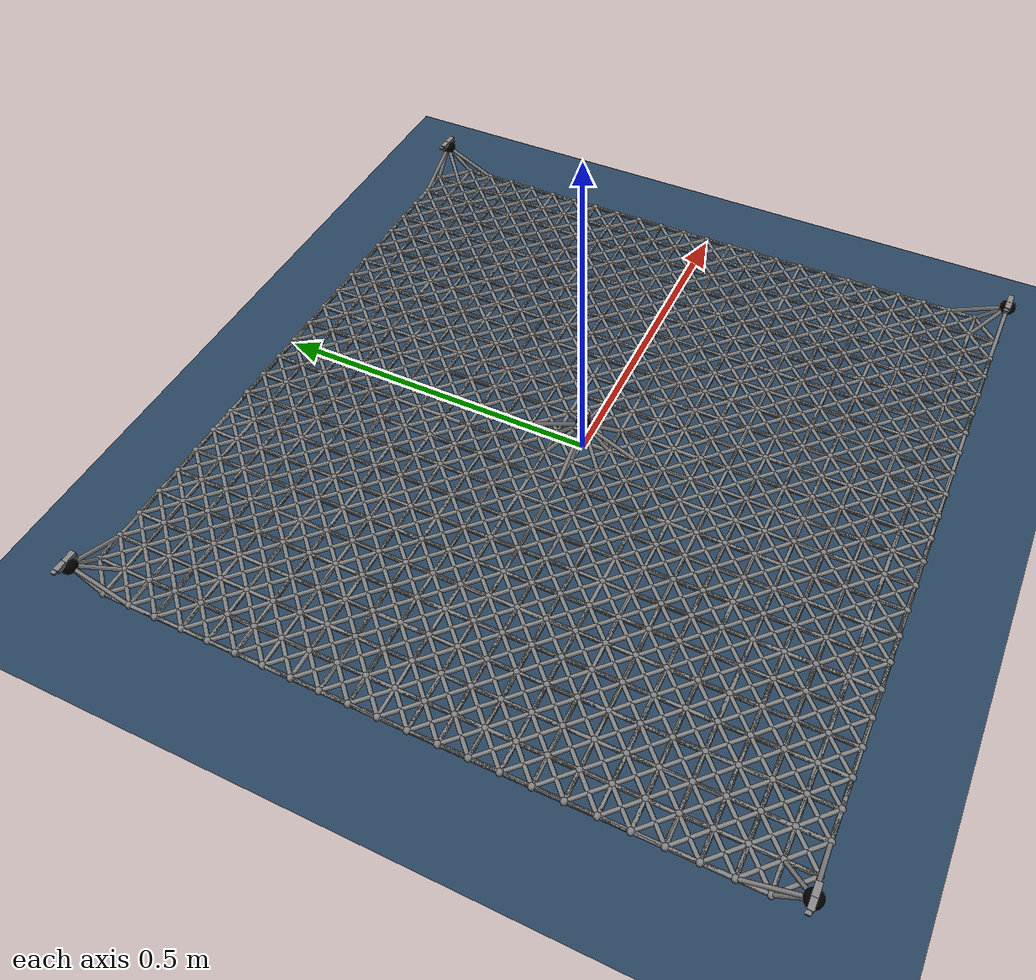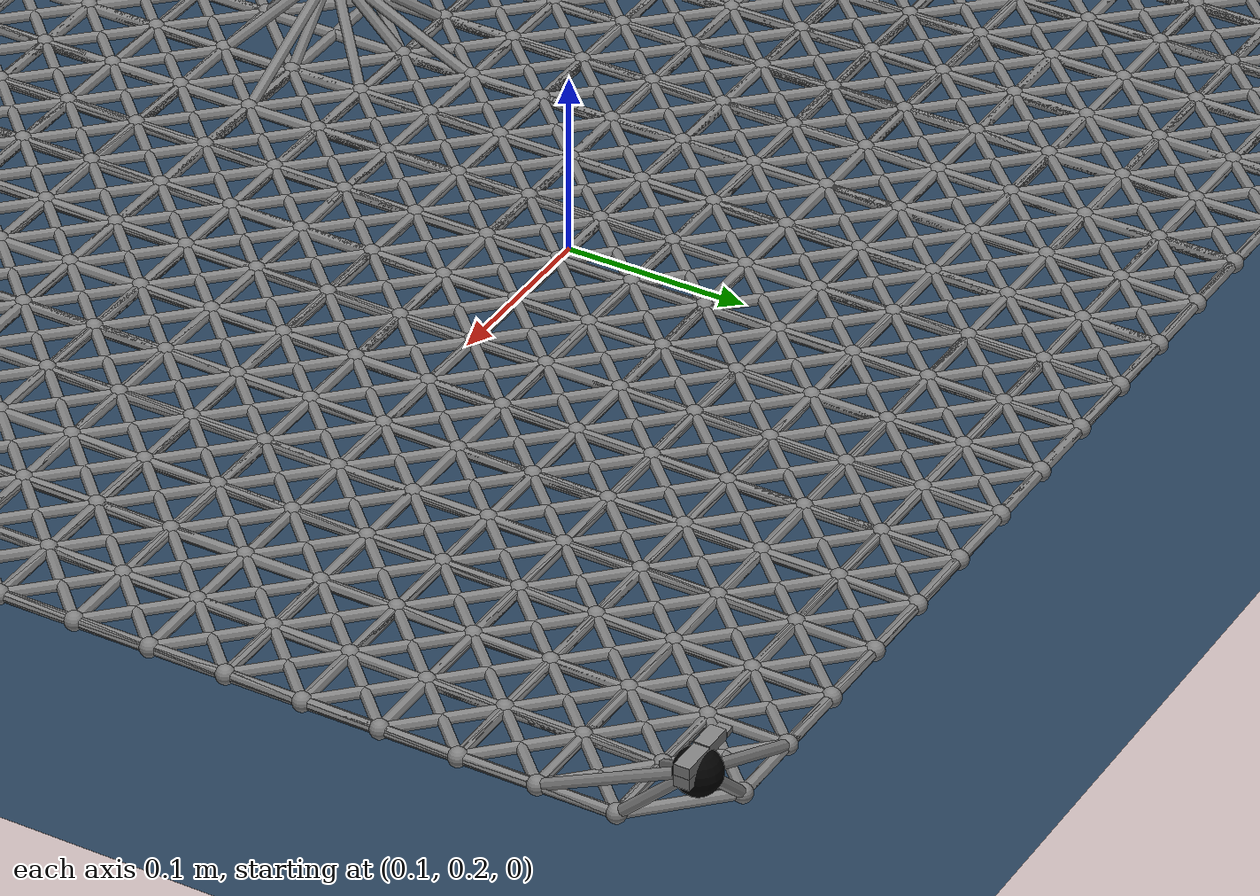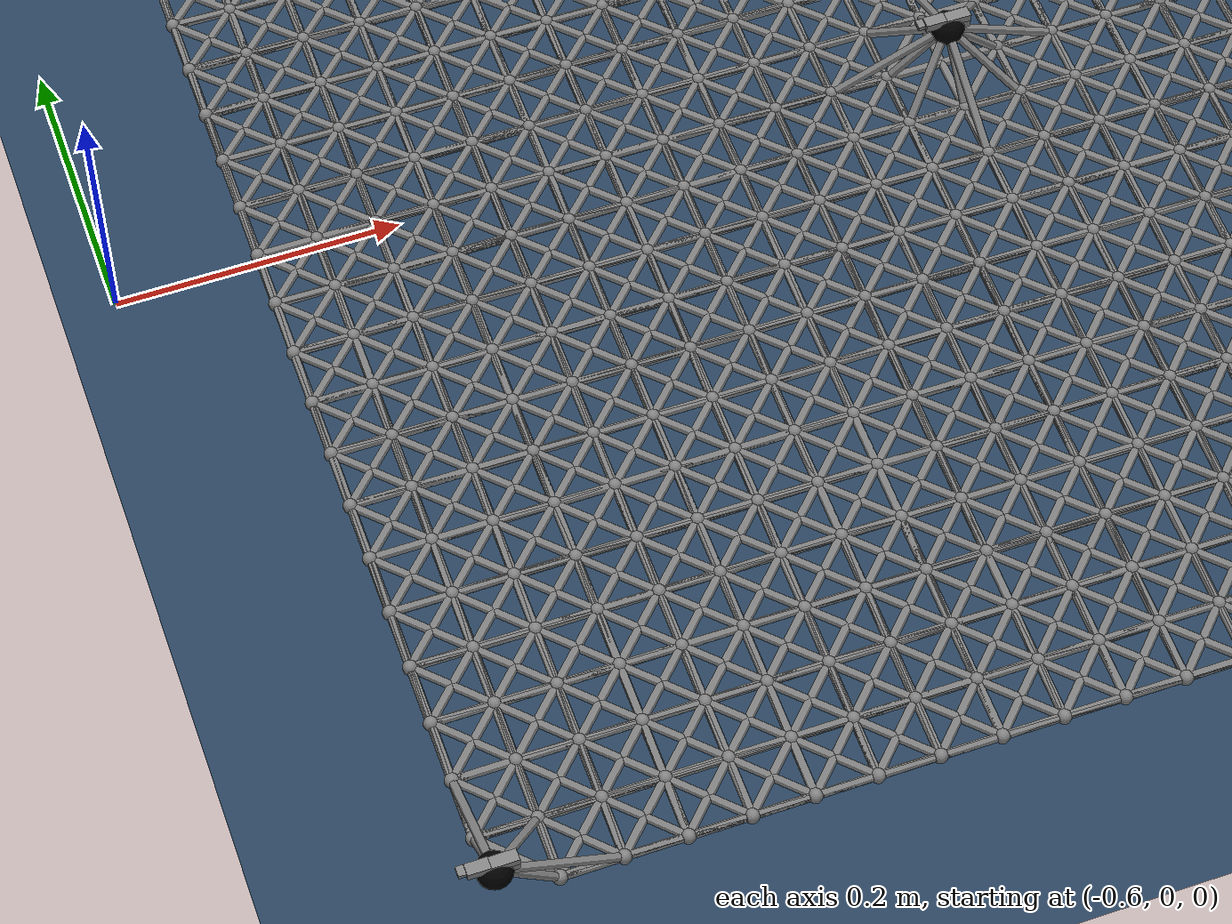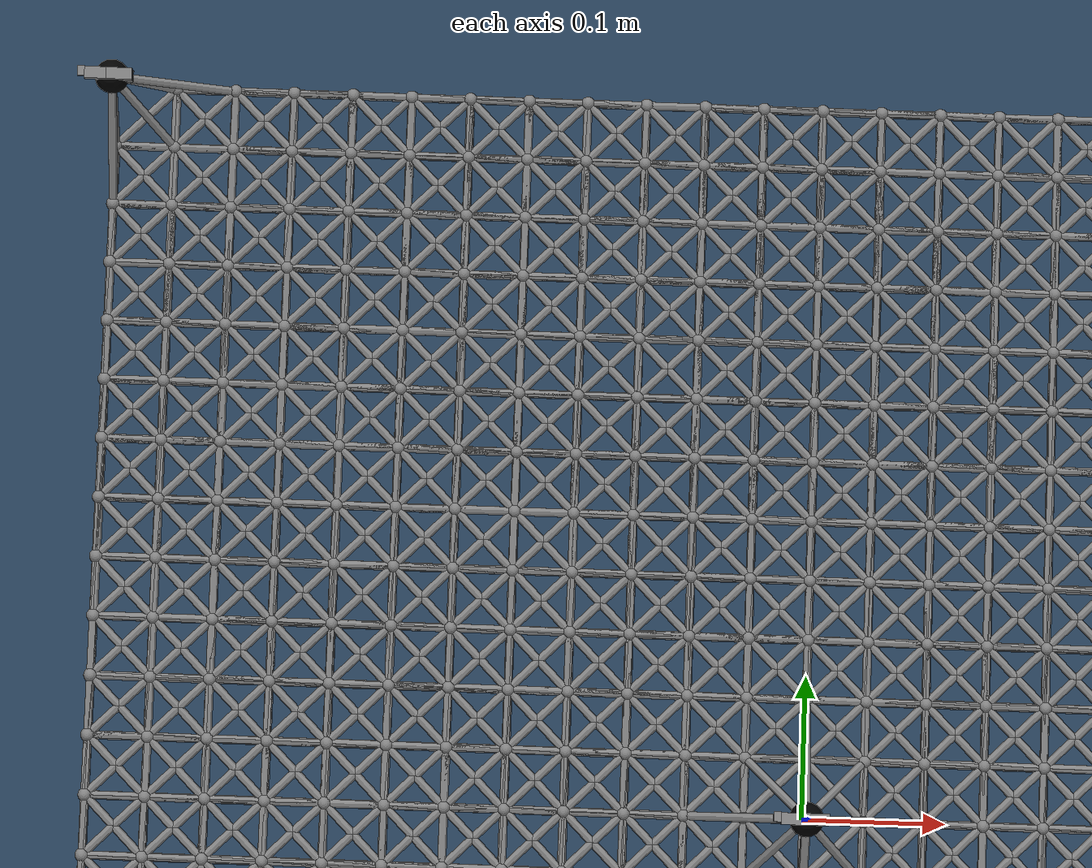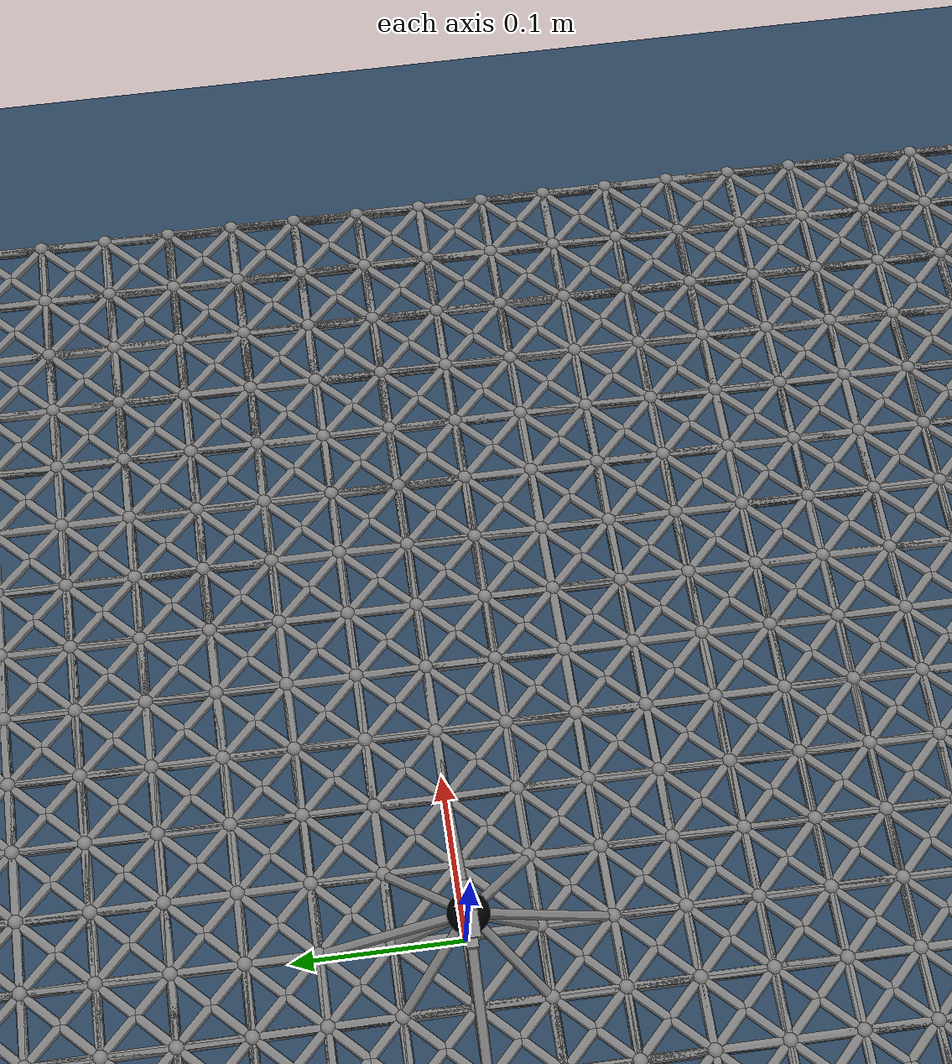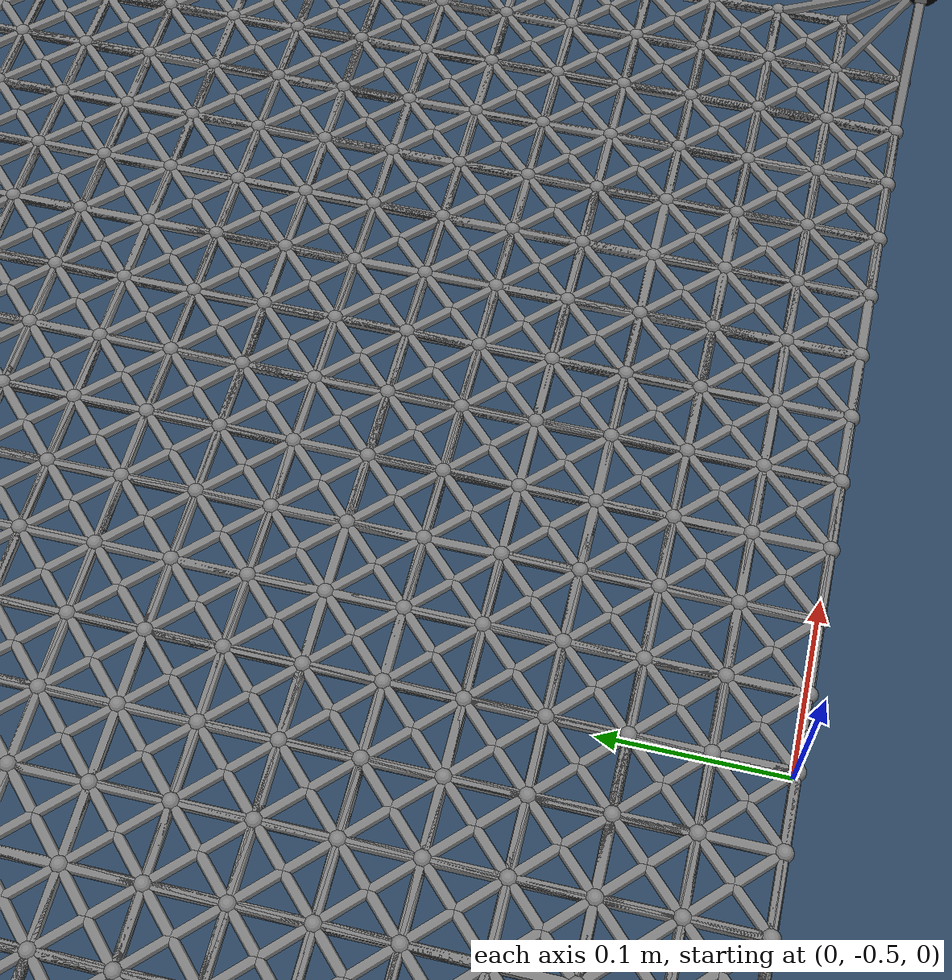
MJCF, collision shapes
<mujoco model="Skydio X2 scene">
  <include file="config_FlySurf_Simulator.xml"/>
  <option timestep="0.002"/>  <!-- Updated timestep -->

  <asset>
    <texture type="skybox" builtin="gradient" rgb1="0.3 0.5 0.7" rgb2="0 0 0" width="512" height="3072"/>
    <texture type="2d" name="groundplane" builtin="checker" mark="edge" rgb1="0.2 0.3 0.4" rgb2="0.1 0.2 0.3"
      markrgb="0.8 0.8 0.8" width="300" height="300"/>
    <material name="groundplane" texture="groundplane" texuniform="true" texrepeat="5 5" reflectance="0.2"/>
  </asset>

  <worldbody>
    <light pos="0 0 1.5" dir="0 0 -1" directional="true"/>
    <geom name="floor" size="0 0 0.05" type="plane" material="groundplane"/>
  </worldbody>
</mujoco>

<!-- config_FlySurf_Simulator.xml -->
<mujoco model="Skydio X2">
  <compiler autolimits="true" assetdir="assets"/>

  <option timestep="0.01" density="1.225" viscosity="1.8e-5"/>
  <default>
    <default class="ball">
        <geom size="0.005" mass="0.0025"/>
    </default>
    <default class="x2">
      <geom mass="0"/>
      <motor ctrlrange="0 13"/>
      <default class="visual">
        <geom group="2" type="mesh" contype="0" conaffinity="0"/>
      </default>
      <default class="collision">
        <geom group="3" type="box"/>
      </default>
      <site group="5"/>
    </default>
  </default>

  <asset>
    <texture type="2d" file="X2_lowpoly_texture_SpinningProps_1024.png"/>
    <material name="phong3SG" texture="X2_lowpoly_texture_SpinningProps_1024"/>
    <material name="invisible" rgba="0 0 0 0"/>
    <mesh class="x2" file="X2_lowpoly.obj" scale="0.0015 0.0015 0.0015"/>
  </asset>

  <worldbody>

    <body name="quad_1" pos="-0.5000 -0.5000 0.05" childclass="x2">
        <joint type="free" damping="0.001"/>
        <geom material="phong3SG" mesh="X2_lowpoly" class="visual" quat="0 0 1 1"/>
        <geom class="collision" size=".009 .00405 .003" pos=".006 0 .003"/>
        <geom class="collision" size=".009 .00405 .003" pos=".006 0 .009"/>
        <geom class="collision" size=".0075 .00405 .003" pos="-.0105 0 .00975"/>
        <geom class="collision" size=".00345 .00255 .0015" pos="-.02055 .0012 .00975" quat="1 0 0 1"/>
        <geom name="point_mass_1" type="sphere" size="0.012" pos="0 0 0" mass="0.32" material="invisible"/>
        <site name="ball_1_1" pos="0 0 0"/>
    </body>

    <body pos="-0.4583 -0.5000 0.01">
        <joint type="free" damping="0.6"/>
        <geom class="ball"/>
        <site name="ball_1_2" pos="0 0 0"/>
    </body>

    <body pos="-0.4167 -0.5000 0.01">
        <joint type="free" damping="0.6"/>
        <geom class="ball"/>
        <site name="ball_1_3" pos="0 0 0"/>
    </body>

    <body pos="-0.3750 -0.5000 0.01">
        <joint type="free" damping="0.6"/>
        <geom class="ball"/>
        <site name="ball_1_4" pos="0 0 0"/>
    </body>

    <body pos="-0.3333 -0.5000 0.01">
        <joint type="free" damping="0.6"/>
        <geom class="ball"/>
        <site name="ball_1_5" pos="0 0 0"/>
    </body>

    <body pos="-0.2917 -0.5000 0.01">
        <joint type="free" damping="0.6"/>
        <geom class="ball"/>
        <site name="ball_1_6" pos="0 0 0"/>
    </body>

    <body pos="-0.2500 -0.5000 0.01">
        <joint type="free" damping="0.6"/>
        <geom class="ball"/>
        <site name="ball_1_7" pos="0 0 0"/>
    </body>

    <body pos="-0.2083 -0.5000 0.01">
        <joint type="free" damping="0.6"/>
        <geom class="ball"/>
        <site name="ball_1_8" pos="0 0 0"/>
    </body>

    <body pos="-0.1667 -0.5000 0.01">
        <joint type="free" damping="0.6"/>
        <geom class="ball"/>
        <site name="ball_1_9" pos="0 0 0"/>
    </body>

    <body pos="-0.1250 -0.5000 0.01">
        <joint type="free" damping="0.6"/>
        <geom class="ball"/>
        <site name="ball_1_10" pos="0 0 0"/>
    </body>

    <body pos="-0.0833 -0.5000 0.01">
        <joint type="free" damping="0.6"/>
        <geom class="ball"/>
        <site name="ball_1_11" pos="0 0 0"/>
    </body>

    <body pos="-0.0417 -0.5000 0.01">
        <joint type="free" damping="0.6"/>
        <geom class="ball"/>
        <site name="ball_1_12" pos="0 0 0"/>
    </body>

    <body pos="0.0000 -0.5000 0.01">
        <joint type="free" damping="0.6"/>
        <geom class="ball"/>
        <site name="ball_1_13" pos="0 0 0"/>
    </body>

    <body pos="0.0417 -0.5000 0.01">
        <joint type="free" damping="0.6"/>
        <geom class="ball"/>
        <site name="ball_1_14" pos="0 0 0"/>
    </body>

    <body pos="0.0833 -0.5000 0.01">
        <joint type="free" damping="0.6"/>
        <geom class="ball"/>
        <site name="ball_1_15" pos="0 0 0"/>
    </body>

    <body pos="0.1250 -0.5000 0.01">
        <joint type="free" damping="0.6"/>
        <geom class="ball"/>
        <site name="ball_1_16" pos="0 0 0"/>
    </body>

    <body pos="0.1667 -0.5000 0.01">
        <joint type="free" damping="0.6"/>
        <geom class="ball"/>
        <site name="ball_1_17" pos="0 0 0"/>
    </body>

    <body pos="0.2083 -0.5000 0.01">
        <joint type="free" damping="0.6"/>
        <geom class="ball"/>
        <site name="ball_1_18" pos="0 0 0"/>
    </body>

    <body pos="0.2500 -0.5000 0.01">
        <joint type="free" damping="0.6"/>
        <geom class="ball"/>
        <site name="ball_1_19" pos="0 0 0"/>
    </body>

    <body pos="0.2917 -0.5000 0.01">
        <joint type="free" damping="0.6"/>
        <geom class="ball"/>
        <site name="ball_1_20" pos="0 0 0"/>
    </body>

    <body pos="0.3333 -0.5000 0.01">
        <joint type="free" damping="0.6"/>
        <geom class="ball"/>
        <site name="ball_1_21" pos="0 0 0"/>
    </body>

    <body pos="0.3750 -0.5000 0.01">
        <joint type="free" damping="0.6"/>
        <geom class="ball"/>
        <site name="ball_1_22" pos="0 0 0"/>
    </body>

    <body pos="0.4167 -0.5000 0.01">
        <joint type="free" damping="0.6"/>
        <geom class="ball"/>
        <site name="ball_1_23" pos="0 0 0"/>
    </body>

    <body pos="0.4583 -0.5000 0.01">
        <joint type="free" damping="0.6"/>
        <geom class="ball"/>
        <site name="ball_1_24" pos="0 0 0"/>
    </body>

    <body name="quad_2" pos="0.5000 -0.5000 0.05" childclass="x2">
        <joint type="free" damping="0.001"/>
        <geom material="phong3SG" mesh="X2_lowpoly" class="visual" quat="0 0 1 1"/>
        <geom class="collision" size=".009 .00405 .003" pos=".006 0 .003"/>
        <geom class="collision" size=".009 .00405 .003" pos=".006 0 .009"/>
        <geom class="collision" size=".0075 .00405 .003" pos="-.0105 0 .00975"/>
        <geom class="collision" size=".00345 .00255 .0015" pos="-.02055 .0012 .00975" quat="1 0 0 1"/>
        <geom name="point_mass_2" type="sphere" size="0.012" pos="0 0 0" mass="0.32" material="invisible"/>
        <site name="ball_1_25" pos="0 0 0"/>
    </body>

    <body pos="-0.5000 -0.4583 0.01">
        <joint type="free" damping="0.6"/>
        <geom class="ball"/>
        <site name="ball_2_1" pos="0 0 0"/>
    </body>

    <body pos="-0.4583 -0.4583 0.01">
        <joint type="free" damping="0.6"/>
        <geom class="ball"/>
        <site name="ball_2_2" pos="0 0 0"/>
    </body>

    <body pos="-0.4167 -0.4583 0.01">
        <joint type="free" damping="0.6"/>
        <geom class="ball"/>
        <site name="ball_2_3" pos="0 0 0"/>
    </body>

    <body pos="-0.3750 -0.4583 0.01">
        <joint type="free" damping="0.6"/>
        <geom class="ball"/>
        <site name="ball_2_4" pos="0 0 0"/>
    </body>

    <body pos="-0.3333 -0.4583 0.01">
        <joint type="free" damping="0.6"/>
        <geom class="ball"/>
        <site name="ball_2_5" pos="0 0 0"/>
    </body>

    <body pos="-0.2917 -0.4583 0.01">
        <joint type="free" damping="0.6"/>
        <geom class="ball"/>
        <site name="ball_2_6" pos="0 0 0"/>
    </body>

    <body pos="-0.2500 -0.4583 0.01">
        <joint type="free" damping="0.6"/>
        <geom class="ball"/>
        <site name="ball_2_7" pos="0 0 0"/>
    </body>

    <body pos="-0.2083 -0.4583 0.01">
        <joint type="free" damping="0.6"/>
        <geom class="ball"/>
        <site name="ball_2_8" pos="0 0 0"/>
    </body>

    <body pos="-0.1667 -0.4583 0.01">
        <joint type="free" damping="0.6"/>
        <geom class="ball"/>
        <site name="ball_2_9" pos="0 0 0"/>
    </body>

    <body pos="-0.1250 -0.4583 0.01">
        <joint type="free" damping="0.6"/>
        <geom class="ball"/>
        <site name="ball_2_10" pos="0 0 0"/>
    </body>

    <body pos="-0.0833 -0.4583 0.01">
        <joint type="free" damping="0.6"/>
        <geom class="ball"/>
        <site name="ball_2_11" pos="0 0 0"/>
    </body>

    <body pos="-0.0417 -0.4583 0.01">
        <joint type="free" damping="0.6"/>
        <geom class="ball"/>
        <site name="ball_2_12" pos="0 0 0"/>
    </body>

    <body pos="0.0000 -0.4583 0.01">
        <joint type="free" damping="0.6"/>
        <geom class="ball"/>
        <site name="ball_2_13" pos="0 0 0"/>
    </body>

    <body pos="0.0417 -0.4583 0.01">
        <joint type="free" damping="0.6"/>
        <geom class="ball"/>
        <site name="ball_2_14" pos="0 0 0"/>
    </body>

    <body pos="0.0833 -0.4583 0.01">
        <joint type="free" damping="0.6"/>
        <geom class="ball"/>
        <site name="ball_2_15" pos="0 0 0"/>
    </body>

    <body pos="0.1250 -0.4583 0.01">
        <joint type="free" damping="0.6"/>
        <geom class="ball"/>
        <site name="ball_2_16" pos="0 0 0"/>
    </body>

    <body pos="0.1667 -0.4583 0.01">
        <joint type="free" damping="0.6"/>
        <geom class="ball"/>
        <site name="ball_2_17" pos="0 0 0"/>
    </body>

    <body pos="0.2083 -0.4583 0.01">
        <joint type="free" damping="0.6"/>
        <geom class="ball"/>
        <site name="ball_2_18" pos="0 0 0"/>
    </body>

    <body pos="0.2500 -0.4583 0.01">
        <joint type="free" damping="0.6"/>
        <geom class="ball"/>
        <site name="ball_2_19" pos="0 0 0"/>
    </body>

    <body pos="0.2917 -0.4583 0.01">
        <joint type="free" damping="0.6"/>
        <geom class="ball"/>
        <site name="ball_2_20" pos="0 0 0"/>
    </body>

    <body pos="0.3333 -0.4583 0.01">
        <joint type="free" damping="0.6"/>
        <geom class="ball"/>
        <site name="ball_2_21" pos="0 0 0"/>
    </body>

    <body pos="0.3750 -0.4583 0.01">
        <joint type="free" damping="0.6"/>
        <geom class="ball"/>
        <site name="ball_2_22" pos="0 0 0"/>
    </body>

    <body pos="0.4167 -0.4583 0.01">
        <joint type="free" damping="0.6"/>
        <geom class="ball"/>
        <site name="ball_2_23" pos="0 0 0"/>
    </body>

    <body pos="0.4583 -0.4583 0.01">
        <joint type="free" damping="0.6"/>
        <geom class="ball"/>
        <site name="ball_2_24" pos="0 0 0"/>
    </body>

    <body pos="0.5000 -0.4583 0.01">
        <joint type="free" damping="0.6"/>
        <geom class="ball"/>
        <site name="ball_2_25" pos="0 0 0"/>
    </body>

    <body pos="-0.5000 -0.4167 0.01">
        <joint type="free" damping="0.6"/>
        <geom class="ball"/>
        <site name="ball_3_1" pos="0 0 0"/>
    </body>

    <body pos="-0.4583 -0.4167 0.01">
        <joint type="free" damping="0.6"/>
        <geom class="ball"/>
        <site name="ball_3_2" pos="0 0 0"/>
    </body>

    <body pos="-0.4167 -0.4167 0.01">
        <joint type="free" damping="0.6"/>
        <geom class="ball"/>
        <site name="ball_3_3" pos="0 0 0"/>
    </body>

    <body pos="-0.3750 -0.4167 0.01">
        <joint type="free" damping="0.6"/>
        <geom class="ball"/>
        <site name="ball_3_4" pos="0 0 0"/>
    </body>

    <body pos="-0.3333 -0.4167 0.01">
        <joint type="free" damping="0.6"/>
        <geom class="ball"/>
        <site name="ball_3_5" pos="0 0 0"/>
    </body>

    <body pos="-0.2917 -0.4167 0.01">
        <joint type="free" damping="0.6"/>
        <geom class="ball"/>
        <site name="ball_3_6" pos="0 0 0"/>
    </body>

    <body pos="-0.2500 -0.4167 0.01">
        <joint type="free" damping="0.6"/>
        <geom class="ball"/>
        <site name="ball_3_7" pos="0 0 0"/>
    </body>

    <body pos="-0.2083 -0.4167 0.01">
        <joint type="free" damping="0.6"/>
        <geom class="ball"/>
        <site name="ball_3_8" pos="0 0 0"/>
    </body>

    <body pos="-0.1667 -0.4167 0.01">
        <joint type="free" damping="0.6"/>
        <geom class="ball"/>
        <site name="ball_3_9" pos="0 0 0"/>
    </body>

    <body pos="-0.1250 -0.4167 0.01">
        <joint type="free" damping="0.6"/>
        <geom class="ball"/>
        <site name="ball_3_10" pos="0 0 0"/>
    </body>

    <body pos="-0.0833 -0.4167 0.01">
        <joint type="free" damping="0.6"/>
        <geom class="ball"/>
        <site name="ball_3_11" pos="0 0 0"/>
    </body>

    <body pos="-0.0417 -0.4167 0.01">
        <joint type="free" damping="0.6"/>
        <geom class="ball"/>
        <site name="ball_3_12" pos="0 0 0"/>
    </body>

    <body pos="0.0000 -0.4167 0.01">
        <joint type="free" damping="0.6"/>
        <geom class="ball"/>
        <site name="ball_3_13" pos="0 0 0"/>
    </body>

    <body pos="0.0417 -0.4167 0.01">
        <joint type="free" damping="0.6"/>
        <geom class="ball"/>
        <site name="ball_3_14" pos="0 0 0"/>
    </body>

    <body pos="0.0833 -0.4167 0.01">
        <joint type="free" damping="0.6"/>
        <geom class="ball"/>
        <site name="ball_3_15" pos="0 0 0"/>
    </body>

    <body pos="0.1250 -0.4167 0.01">
        <joint type="free" damping="0.6"/>
        <geom class="ball"/>
        <site name="ball_3_16" pos="0 0 0"/>
    </body>

    <body pos="0.1667 -0.4167 0.01">
        <joint type="free" damping="0.6"/>
        <geom class="ball"/>
        <site name="ball_3_17" pos="0 0 0"/>
    </body>

    <body pos="0.2083 -0.4167 0.01">
        <joint type="free" damping="0.6"/>
        <geom class="ball"/>
        <site name="ball_3_18" pos="0 0 0"/>
    </body>

    <body pos="0.2500 -0.4167 0.01">
        <joint type="free" damping="0.6"/>
        <geom class="ball"/>
        <site name="ball_3_19" pos="0 0 0"/>
    </body>

    <body pos="0.2917 -0.4167 0.01">
        <joint type="free" damping="0.6"/>
        <geom class="ball"/>
        <site name="ball_3_20" pos="0 0 0"/>
    </body>

    <body pos="0.3333 -0.4167 0.01">
        <joint type="free" damping="0.6"/>
        <geom class="ball"/>
        <site name="ball_3_21" pos="0 0 0"/>
    </body>

    <body pos="0.3750 -0.4167 0.01">
        <joint type="free" damping="0.6"/>
        <geom class="ball"/>
        <site name="ball_3_22" pos="0 0 0"/>
    </body>

    <body pos="0.4167 -0.4167 0.01">
        <joint type="free" damping="0.6"/>
        <geom class="ball"/>
        <site name="ball_3_23" pos="0 0 0"/>
    </body>

    <body pos="0.4583 -0.4167 0.01">
        <joint type="free" damping="0.6"/>
        <geom class="ball"/>
        <site name="ball_3_24" pos="0 0 0"/>
    </body>

    <body pos="0.5000 -0.4167 0.01">
        <joint type="free" damping="0.6"/>
        <geom class="ball"/>
        <site name="ball_3_25" pos="0 0 0"/>
    </body>

    <body pos="-0.5000 -0.3750 0.01">
        <joint type="free" damping="0.6"/>
        <geom class="ball"/>
        <site name="ball_4_1" pos="0 0 0"/>
    </body>

    <body pos="-0.4583 -0.3750 0.01">
        <joint type="free" damping="0.6"/>
        <geom class="ball"/>
        <site name="ball_4_2" pos="0 0 0"/>
    </body>

    <body pos="-0.4167 -0.3750 0.01">
        <joint type="free" damping="0.6"/>
        <geom class="ball"/>
        <site name="ball_4_3" pos="0 0 0"/>
    </body>

    <body pos="-0.3750 -0.3750 0.01">
        <joint type="free" damping="0.6"/>
        <geom class="ball"/>
        <site name="ball_4_4" pos="0 0 0"/>
    </body>

    <body pos="-0.3333 -0.3750 0.01">
        <joint type="free" damping="0.6"/>
        <geom class="ball"/>
        <site name="ball_4_5" pos="0 0 0"/>
    </body>

    <body pos="-0.2917 -0.3750 0.01">
        <joint type="free" damping="0.6"/>
        <geom class="ball"/>
        <site name="ball_4_6" pos="0 0 0"/>
    </body>

    <body pos="-0.2500 -0.3750 0.01">
        <joint type="free" damping="0.6"/>
        <geom class="ball"/>
        <site name="ball_4_7" pos="0 0 0"/>
    </body>

    <body pos="-0.2083 -0.3750 0.01">
        <joint type="free" damping="0.6"/>
        <geom class="ball"/>
        <site name="ball_4_8" pos="0 0 0"/>
    </body>

    <body pos="-0.1667 -0.3750 0.01">
        <joint type="free" damping="0.6"/>
        <geom class="ball"/>
        <site name="ball_4_9" pos="0 0 0"/>
    </body>

    <body pos="-0.1250 -0.3750 0.01">
        <joint type="free" damping="0.6"/>
        <geom class="ball"/>
        <site name="ball_4_10" pos="0 0 0"/>
    </body>

    <body pos="-0.0833 -0.3750 0.01">
        <joint type="free" damping="0.6"/>
        <geom class="ball"/>
        <site name="ball_4_11" pos="0 0 0"/>
    </body>

    <body pos="-0.0417 -0.3750 0.01">
        <joint type="free" damping="0.6"/>
        <geom class="ball"/>
        <site name="ball_4_12" pos="0 0 0"/>
    </body>

    <body pos="0.0000 -0.3750 0.01">
        <joint type="free" damping="0.6"/>
        <geom class="ball"/>
        <site name="ball_4_13" pos="0 0 0"/>
    </body>

    <body pos="0.0417 -0.3750 0.01">
        <joint type="free" damping="0.6"/>
        <geom class="ball"/>
        <site name="ball_4_14" pos="0 0 0"/>
    </body>

    <body pos="0.0833 -0.3750 0.01">
        <joint type="free" damping="0.6"/>
        <geom class="ball"/>
        <site name="ball_4_15" pos="0 0 0"/>
    </body>

    <body pos="0.1250 -0.3750 0.01">
        <joint type="free" damping="0.6"/>
        <geom class="ball"/>
        <site name="ball_4_16" pos="0 0 0"/>
    </body>

    <body pos="0.1667 -0.3750 0.01">
        <joint type="free" damping="0.6"/>
        <geom class="ball"/>
        <site name="ball_4_17" pos="0 0 0"/>
    </body>

    <body pos="0.2083 -0.3750 0.01">
        <joint type="free" damping="0.6"/>
        <geom class="ball"/>
        <site name="ball_4_18" pos="0 0 0"/>
    </body>

    <body pos="0.2500 -0.3750 0.01">
        <joint type="free" damping="0.6"/>
        <geom class="ball"/>
        <site name="ball_4_19" pos="0 0 0"/>
    </body>

    <body pos="0.2917 -0.3750 0.01">
        <joint type="free" damping="0.6"/>
        <geom class="ball"/>
        <site name="ball_4_20" pos="0 0 0"/>
    </body>

    <body pos="0.3333 -0.3750 0.01">
        <joint type="free" damping="0.6"/>
        <geom class="ball"/>
        <site name="ball_4_21" pos="0 0 0"/>
    </body>

    <body pos="0.3750 -0.3750 0.01">
        <joint type="free" damping="0.6"/>
        <geom class="ball"/>
        <site name="ball_4_22" pos="0 0 0"/>
    </body>

    <body pos="0.4167 -0.3750 0.01">
        <joint type="free" damping="0.6"/>
        <geom class="ball"/>
        <site name="ball_4_23" pos="0 0 0"/>
    </body>

    <body pos="0.4583 -0.3750 0.01">
        <joint type="free" damping="0.6"/>
        <geom class="ball"/>
        <site name="ball_4_24" pos="0 0 0"/>
    </body>

    <body pos="0.5000 -0.3750 0.01">
        <joint type="free" damping="0.6"/>
        <geom class="ball"/>
        <site name="ball_4_25" pos="0 0 0"/>
    </body>

    <body pos="-0.5000 -0.3333 0.01">
        <joint type="free" damping="0.6"/>
        <geom class="ball"/>
        <site name="ball_5_1" pos="0 0 0"/>
    </body>

    <body pos="-0.4583 -0.3333 0.01">
        <joint type="free" damping="0.6"/>
        <geom class="ball"/>
        <site name="ball_5_2" pos="0 0 0"/>
    </body>

    <body pos="-0.4167 -0.3333 0.01">
        <joint type="free" damping="0.6"/>
        <geom class="ball"/>
        <site name="ball_5_3" pos="0 0 0"/>
    </body>

    <body pos="-0.3750 -0.3333 0.01">
        <joint type="free" damping="0.6"/>
        <geom class="ball"/>
        <site name="ball_5_4" pos="0 0 0"/>
    </body>

    <body pos="-0.3333 -0.3333 0.01">
        <joint type="free" damping="0.6"/>
        <geom class="ball"/>
        <site name="ball_5_5" pos="0 0 0"/>
    </body>

    <body pos="-0.2917 -0.3333 0.01">
        <joint type="free" damping="0.6"/>
        <geom class="ball"/>
        <site name="ball_5_6" pos="0 0 0"/>
    </body>

    <body pos="-0.2500 -0.3333 0.01">
        <joint type="free" damping="0.6"/>
        <geom class="ball"/>
        <site name="ball_5_7" pos="0 0 0"/>
    </body>

    <body pos="-0.2083 -0.3333 0.01">
        <joint type="free" damping="0.6"/>
        <geom class="ball"/>
        <site name="ball_5_8" pos="0 0 0"/>
    </body>

    <body pos="-0.1667 -0.3333 0.01">
        <joint type="free" damping="0.6"/>
        <geom class="ball"/>
        <site name="ball_5_9" pos="0 0 0"/>
    </body>

    <body pos="-0.1250 -0.3333 0.01">
        <joint type="free" damping="0.6"/>
        <geom class="ball"/>
        <site name="ball_5_10" pos="0 0 0"/>
    </body>

    <body pos="-0.0833 -0.3333 0.01">
        <joint type="free" damping="0.6"/>
        <geom class="ball"/>
        <site name="ball_5_11" pos="0 0 0"/>
    </body>

    <body pos="-0.0417 -0.3333 0.01">
        <joint type="free" damping="0.6"/>
        <geom class="ball"/>
        <site name="ball_5_12" pos="0 0 0"/>
    </body>

    <body pos="0.0000 -0.3333 0.01">
        <joint type="free" damping="0.6"/>
        <geom class="ball"/>
        <site name="ball_5_13" pos="0 0 0"/>
    </body>

    <body pos="0.0417 -0.3333 0.01">
        <joint type="free" damping="0.6"/>
        <geom class="ball"/>
        <site name="ball_5_14" pos="0 0 0"/>
    </body>

    <body pos="0.0833 -0.3333 0.01">
        <joint type="free" damping="0.6"/>
        <geom class="ball"/>
        <site name="ball_5_15" pos="0 0 0"/>
    </body>

    <body pos="0.1250 -0.3333 0.01">
        <joint type="free" damping="0.6"/>
        <geom class="ball"/>
        <site name="ball_5_16" pos="0 0 0"/>
    </body>

    <body pos="0.1667 -0.3333 0.01">
        <joint type="free" damping="0.6"/>
        <geom class="ball"/>
        <site name="ball_5_17" pos="0 0 0"/>
    </body>

    <body pos="0.2083 -0.3333 0.01">
        <joint type="free" damping="0.6"/>
        <geom class="ball"/>
        <site name="ball_5_18" pos="0 0 0"/>
    </body>

    <body pos="0.2500 -0.3333 0.01">
        <joint type="free" damping="0.6"/>
        <geom class="ball"/>
        <site name="ball_5_19" pos="0 0 0"/>
    </body>

    <body pos="0.2917 -0.3333 0.01">
        <joint type="free" damping="0.6"/>
        <geom class="ball"/>
        <site name="ball_5_20" pos="0 0 0"/>
    </body>

    <body pos="0.3333 -0.3333 0.01">
        <joint type="free" damping="0.6"/>
        <geom class="ball"/>
        <site name="ball_5_21" pos="0 0 0"/>
    </body>

    <body pos="0.3750 -0.3333 0.01">
        <joint type="free" damping="0.6"/>
        <geom class="ball"/>
        <site name="ball_5_22" pos="0 0 0"/>
    </body>

    <body pos="0.4167 -0.3333 0.01">
        <joint type="free" damping="0.6"/>
        <geom class="ball"/>
        <site name="ball_5_23" pos="0 0 0"/>
    </body>

    <body pos="0.4583 -0.3333 0.01">
        <joint type="free" damping="0.6"/>
        <geom class="ball"/>
        <site name="ball_5_24" pos="0 0 0"/>
    </body>

    <body pos="0.5000 -0.3333 0.01">
        <joint type="free" damping="0.6"/>
        <geom class="ball"/>
        <site name="ball_5_25" pos="0 0 0"/>
    </body>

    <body pos="-0.5000 -0.2917 0.01">
        <joint type="free" damping="0.6"/>
        <geom class="ball"/>
        <site name="ball_6_1" pos="0 0 0"/>
    </body>

    <body pos="-0.4583 -0.2917 0.01">
        <joint type="free" damping="0.6"/>
        <geom class="ball"/>
        <site name="ball_6_2" pos="0 0 0"/>
    </body>

    <body pos="-0.4167 -0.2917 0.01">
        <joint type="free" damping="0.6"/>
        <geom class="ball"/>
        <site name="ball_6_3" pos="0 0 0"/>
    </body>

    <body pos="-0.3750 -0.2917 0.01">
        <joint type="free" damping="0.6"/>
        <geom class="ball"/>
        <site name="ball_6_4" pos="0 0 0"/>
    </body>

    <body pos="-0.3333 -0.2917 0.01">
        <joint type="free" damping="0.6"/>
        <geom class="ball"/>
        <site name="ball_6_5" pos="0 0 0"/>
    </body>

    <body pos="-0.2917 -0.2917 0.01">
        <joint type="free" damping="0.6"/>
        <geom class="ball"/>
        <site name="ball_6_6" pos="0 0 0"/>
    </body>

    <body pos="-0.2500 -0.2917 0.01">
        <joint type="free" damping="0.6"/>
        <geom class="ball"/>
        <site name="ball_6_7" pos="0 0 0"/>
    </body>

    <body pos="-0.2083 -0.2917 0.01">
        <joint type="free" damping="0.6"/>
        <geom class="ball"/>
        <site name="ball_6_8" pos="0 0 0"/>
    </body>

    <body pos="-0.1667 -0.2917 0.01">
        <joint type="free" damping="0.6"/>
        <geom class="ball"/>
        <site name="ball_6_9" pos="0 0 0"/>
    </body>

    <body pos="-0.1250 -0.2917 0.01">
        <joint type="free" damping="0.6"/>
        <geom class="ball"/>
        <site name="ball_6_10" pos="0 0 0"/>
    </body>

    <body pos="-0.0833 -0.2917 0.01">
        <joint type="free" damping="0.6"/>
        <geom class="ball"/>
        <site name="ball_6_11" pos="0 0 0"/>
    </body>

    <body pos="-0.0417 -0.2917 0.01">
        <joint type="free" damping="0.6"/>
        <geom class="ball"/>
        <site name="ball_6_12" pos="0 0 0"/>
    </body>

    <body pos="0.0000 -0.2917 0.01">
        <joint type="free" damping="0.6"/>
        <geom class="ball"/>
        <site name="ball_6_13" pos="0 0 0"/>
    </body>

    <body pos="0.0417 -0.2917 0.01">
        <joint type="free" damping="0.6"/>
        <geom class="ball"/>
        <site name="ball_6_14" pos="0 0 0"/>
    </body>

    <body pos="0.0833 -0.2917 0.01">
        <joint type="free" damping="0.6"/>
        <geom class="ball"/>
        <site name="ball_6_15" pos="0 0 0"/>
    </body>

    <body pos="0.1250 -0.2917 0.01">
        <joint type="free" damping="0.6"/>
        <geom class="ball"/>
        <site name="ball_6_16" pos="0 0 0"/>
    </body>

    <body pos="0.1667 -0.2917 0.01">
        <joint type="free" damping="0.6"/>
        <geom class="ball"/>
        <site name="ball_6_17" pos="0 0 0"/>
    </body>

    <body pos="0.2083 -0.2917 0.01">
        <joint type="free" damping="0.6"/>
        <geom class="ball"/>
        <site name="ball_6_18" pos="0 0 0"/>
    </body>

    <body pos="0.2500 -0.2917 0.01">
        <joint type="free" damping="0.6"/>
        <geom class="ball"/>
        <site name="ball_6_19" pos="0 0 0"/>
    </body>

    <body pos="0.2917 -0.2917 0.01">
        <joint type="free" damping="0.6"/>
        <geom class="ball"/>
        <site name="ball_6_20" pos="0 0 0"/>
    </body>

    <body pos="0.3333 -0.2917 0.01">
        <joint type="free" damping="0.6"/>
        <geom class="ball"/>
        <site name="ball_6_21" pos="0 0 0"/>
    </body>

    <body pos="0.3750 -0.2917 0.01">
        <joint type="free" damping="0.6"/>
        <geom class="ball"/>
        <site name="ball_6_22" pos="0 0 0"/>
    </body>

    <body pos="0.4167 -0.2917 0.01">
        <joint type="free" damping="0.6"/>
        <geom class="ball"/>
        <site name="ball_6_23" pos="0 0 0"/>
    </body>

    <body pos="0.4583 -0.2917 0.01">
        <joint type="free" damping="0.6"/>
        <geom class="ball"/>
        <site name="ball_6_24" pos="0 0 0"/>
    </body>

    <body pos="0.5000 -0.2917 0.01">
        <joint type="free" damping="0.6"/>
        <geom class="ball"/>
        <site name="ball_6_25" pos="0 0 0"/>
    </body>

    <body pos="-0.5000 -0.2500 0.01">
        <joint type="free" damping="0.6"/>
        <geom class="ball"/>
        <site name="ball_7_1" pos="0 0 0"/>
    </body>

    <body pos="-0.4583 -0.2500 0.01">
        <joint type="free" damping="0.6"/>
        <geom class="ball"/>
        <site name="ball_7_2" pos="0 0 0"/>
    </body>

    <body pos="-0.4167 -0.2500 0.01">
        <joint type="free" damping="0.6"/>
        <geom class="ball"/>
        <site name="ball_7_3" pos="0 0 0"/>
    </body>

    <body pos="-0.3750 -0.2500 0.01">
        <joint type="free" damping="0.6"/>
        <geom class="ball"/>
        <site name="ball_7_4" pos="0 0 0"/>
    </body>

    <body pos="-0.3333 -0.2500 0.01">
        <joint type="free" damping="0.6"/>
        <geom class="ball"/>
        <site name="ball_7_5" pos="0 0 0"/>
    </body>

    <body pos="-0.2917 -0.2500 0.01">
        <joint type="free" damping="0.6"/>
        <geom class="ball"/>
        <site name="ball_7_6" pos="0 0 0"/>
    </body>

    <body pos="-0.2500 -0.2500 0.01">
        <joint type="free" damping="0.6"/>
        <geom class="ball"/>
        <site name="ball_7_7" pos="0 0 0"/>
    </body>

    <body pos="-0.2083 -0.2500 0.01">
        <joint type="free" damping="0.6"/>
        <geom class="ball"/>
        <site name="ball_7_8" pos="0 0 0"/>
    </body>

    <body pos="-0.1667 -0.2500 0.01">
        <joint type="free" damping="0.6"/>
        <geom class="ball"/>
        <site name="ball_7_9" pos="0 0 0"/>
    </body>

    <body pos="-0.1250 -0.2500 0.01">
        <joint type="free" damping="0.6"/>
        <geom class="ball"/>
        <site name="ball_7_10" pos="0 0 0"/>
    </body>

    <body pos="-0.0833 -0.2500 0.01">
        <joint type="free" damping="0.6"/>
        <geom class="ball"/>
        <site name="ball_7_11" pos="0 0 0"/>
    </body>

    <body pos="-0.0417 -0.2500 0.01">
        <joint type="free" damping="0.6"/>
        <geom class="ball"/>
        <site name="ball_7_12" pos="0 0 0"/>
    </body>

    <body pos="0.0000 -0.2500 0.01">
        <joint type="free" damping="0.6"/>
        <geom class="ball"/>
        <site name="ball_7_13" pos="0 0 0"/>
    </body>

    <body pos="0.0417 -0.2500 0.01">
        <joint type="free" damping="0.6"/>
        <geom class="ball"/>
        <site name="ball_7_14" pos="0 0 0"/>
    </body>

    <body pos="0.0833 -0.2500 0.01">
        <joint type="free" damping="0.6"/>
        <geom class="ball"/>
        <site name="ball_7_15" pos="0 0 0"/>
    </body>

    <body pos="0.1250 -0.2500 0.01">
        <joint type="free" damping="0.6"/>
        <geom class="ball"/>
        <site name="ball_7_16" pos="0 0 0"/>
    </body>

    <body pos="0.1667 -0.2500 0.01">
        <joint type="free" damping="0.6"/>
        <geom class="ball"/>
        <site name="ball_7_17" pos="0 0 0"/>
    </body>

    <body pos="0.2083 -0.2500 0.01">
        <joint type="free" damping="0.6"/>
        <geom class="ball"/>
        <site name="ball_7_18" pos="0 0 0"/>
    </body>

    <body pos="0.2500 -0.2500 0.01">
        <joint type="free" damping="0.6"/>
        <geom class="ball"/>
        <site name="ball_7_19" pos="0 0 0"/>
    </body>

    <body pos="0.2917 -0.2500 0.01">
        <joint type="free" damping="0.6"/>
        <geom class="ball"/>
        <site name="ball_7_20" pos="0 0 0"/>
    </body>

    <body pos="0.3333 -0.2500 0.01">
        <joint type="free" damping="0.6"/>
        <geom class="ball"/>
        <site name="ball_7_21" pos="0 0 0"/>
    </body>

    <body pos="0.3750 -0.2500 0.01">
        <joint type="free" damping="0.6"/>
        <geom class="ball"/>
        <site name="ball_7_22" pos="0 0 0"/>
    </body>

    <body pos="0.4167 -0.2500 0.01">
        <joint type="free" damping="0.6"/>
        <geom class="ball"/>
        <site name="ball_7_23" pos="0 0 0"/>
    </body>

    <body pos="0.4583 -0.2500 0.01">
        <joint type="free" damping="0.6"/>
        <geom class="ball"/>
        <site name="ball_7_24" pos="0 0 0"/>
    </body>

    <body pos="0.5000 -0.2500 0.01">
        <joint type="free" damping="0.6"/>
        <geom class="ball"/>
        <site name="ball_7_25" pos="0 0 0"/>
    </body>

    <body pos="-0.5000 -0.2083 0.01">
        <joint type="free" damping="0.6"/>
        <geom class="ball"/>
        <site name="ball_8_1" pos="0 0 0"/>
    </body>

    <body pos="-0.4583 -0.2083 0.01">
        <joint type="free" damping="0.6"/>
        <geom class="ball"/>
        <site name="ball_8_2" pos="0 0 0"/>
    </body>

    <body pos="-0.4167 -0.2083 0.01">
        <joint type="free" damping="0.6"/>
        <geom class="ball"/>
        <site name="ball_8_3" pos="0 0 0"/>
    </body>

    <body pos="-0.3750 -0.2083 0.01">
        <joint type="free" damping="0.6"/>
        <geom class="ball"/>
        <site name="ball_8_4" pos="0 0 0"/>
    </body>

    <body pos="-0.3333 -0.2083 0.01">
        <joint type="free" damping="0.6"/>
        <geom class="ball"/>
        <site name="ball_8_5" pos="0 0 0"/>
    </body>

    <body pos="-0.2917 -0.2083 0.01">
        <joint type="free" damping="0.6"/>
        <geom class="ball"/>
        <site name="ball_8_6" pos="0 0 0"/>
    </body>

    <body pos="-0.2500 -0.2083 0.01">
        <joint type="free" damping="0.6"/>
        <geom class="ball"/>
        <site name="ball_8_7" pos="0 0 0"/>
    </body>

    <body pos="-0.2083 -0.2083 0.01">
        <joint type="free" damping="0.6"/>
        <geom class="ball"/>
        <site name="ball_8_8" pos="0 0 0"/>
    </body>

    <body pos="-0.1667 -0.2083 0.01">
        <joint type="free" damping="0.6"/>
        <geom class="ball"/>
        <site name="ball_8_9" pos="0 0 0"/>
    </body>

    <body pos="-0.1250 -0.2083 0.01">
        <joint type="free" damping="0.6"/>
        <geom class="ball"/>
        <site name="ball_8_10" pos="0 0 0"/>
    </body>

    <body pos="-0.0833 -0.2083 0.01">
        <joint type="free" damping="0.6"/>
        <geom class="ball"/>
        <site name="ball_8_11" pos="0 0 0"/>
    </body>

    <body pos="-0.0417 -0.2083 0.01">
        <joint type="free" damping="0.6"/>
        <geom class="ball"/>
        <site name="ball_8_12" pos="0 0 0"/>
    </body>

    <body pos="0.0000 -0.2083 0.01">
        <joint type="free" damping="0.6"/>
        <geom class="ball"/>
        <site name="ball_8_13" pos="0 0 0"/>
    </body>

    <body pos="0.0417 -0.2083 0.01">
        <joint type="free" damping="0.6"/>
        <geom class="ball"/>
        <site name="ball_8_14" pos="0 0 0"/>
    </body>

    <body pos="0.0833 -0.2083 0.01">
        <joint type="free" damping="0.6"/>
        <geom class="ball"/>
        <site name="ball_8_15" pos="0 0 0"/>
    </body>

    <body pos="0.1250 -0.2083 0.01">
        <joint type="free" damping="0.6"/>
        <geom class="ball"/>
        <site name="ball_8_16" pos="0 0 0"/>
    </body>

    <body pos="0.1667 -0.2083 0.01">
        <joint type="free" damping="0.6"/>
        <geom class="ball"/>
        <site name="ball_8_17" pos="0 0 0"/>
    </body>

    <body pos="0.2083 -0.2083 0.01">
        <joint type="free" damping="0.6"/>
        <geom class="ball"/>
        <site name="ball_8_18" pos="0 0 0"/>
    </body>

    <body pos="0.2500 -0.2083 0.01">
        <joint type="free" damping="0.6"/>
        <geom class="ball"/>
        <site name="ball_8_19" pos="0 0 0"/>
    </body>

    <body pos="0.2917 -0.2083 0.01">
        <joint type="free" damping="0.6"/>
        <geom class="ball"/>
        <site name="ball_8_20" pos="0 0 0"/>
    </body>

    <body pos="0.3333 -0.2083 0.01">
        <joint type="free" damping="0.6"/>
        <geom class="ball"/>
        <site name="ball_8_21" pos="0 0 0"/>
    </body>

    <body pos="0.3750 -0.2083 0.01">
        <joint type="free" damping="0.6"/>
        <geom class="ball"/>
        <site name="ball_8_22" pos="0 0 0"/>
    </body>

    <body pos="0.4167 -0.2083 0.01">
        <joint type="free" damping="0.6"/>
        <geom class="ball"/>
        <site name="ball_8_23" pos="0 0 0"/>
    </body>

    <body pos="0.4583 -0.2083 0.01">
        <joint type="free" damping="0.6"/>
        <geom class="ball"/>
        <site name="ball_8_24" pos="0 0 0"/>
    </body>

    <body pos="0.5000 -0.2083 0.01">
        <joint type="free" damping="0.6"/>
        <geom class="ball"/>
        <site name="ball_8_25" pos="0 0 0"/>
    </body>

    <body pos="-0.5000 -0.1667 0.01">
        <joint type="free" damping="0.6"/>
        <geom class="ball"/>
        <site name="ball_9_1" pos="0 0 0"/>
    </body>

    <body pos="-0.4583 -0.1667 0.01">
        <joint type="free" damping="0.6"/>
        <geom class="ball"/>
        <site name="ball_9_2" pos="0 0 0"/>
    </body>

    <body pos="-0.4167 -0.1667 0.01">
        <joint type="free" damping="0.6"/>
        <geom class="ball"/>
        <site name="ball_9_3" pos="0 0 0"/>
    </body>

    <body pos="-0.3750 -0.1667 0.01">
        <joint type="free" damping="0.6"/>
        <geom class="ball"/>
        <site name="ball_9_4" pos="0 0 0"/>
    </body>

    <body pos="-0.3333 -0.1667 0.01">
        <joint type="free" damping="0.6"/>
        <geom class="ball"/>
        <site name="ball_9_5" pos="0 0 0"/>
    </body>

    <body pos="-0.2917 -0.1667 0.01">
        <joint type="free" damping="0.6"/>
        <geom class="ball"/>
        <site name="ball_9_6" pos="0 0 0"/>
    </body>

    <body pos="-0.2500 -0.1667 0.01">
        <joint type="free" damping="0.6"/>
        <geom class="ball"/>
        <site name="ball_9_7" pos="0 0 0"/>
    </body>

    <body pos="-0.2083 -0.1667 0.01">
        <joint type="free" damping="0.6"/>
        <geom class="ball"/>
        <site name="ball_9_8" pos="0 0 0"/>
    </body>

    <body pos="-0.1667 -0.1667 0.01">
        <joint type="free" damping="0.6"/>
        <geom class="ball"/>
        <site name="ball_9_9" pos="0 0 0"/>
    </body>

    <body pos="-0.1250 -0.1667 0.01">
        <joint type="free" damping="0.6"/>
        <geom class="ball"/>
        <site name="ball_9_10" pos="0 0 0"/>
    </body>

    <body pos="-0.0833 -0.1667 0.01">
        <joint type="free" damping="0.6"/>
        <geom class="ball"/>
        <site name="ball_9_11" pos="0 0 0"/>
    </body>

    <body pos="-0.0417 -0.1667 0.01">
        <joint type="free" damping="0.6"/>
        <geom class="ball"/>
        <site name="ball_9_12" pos="0 0 0"/>
    </body>

    <body pos="0.0000 -0.1667 0.01">
        <joint type="free" damping="0.6"/>
        <geom class="ball"/>
        <site name="ball_9_13" pos="0 0 0"/>
    </body>

    <body pos="0.0417 -0.1667 0.01">
        <joint type="free" damping="0.6"/>
        <geom class="ball"/>
        <site name="ball_9_14" pos="0 0 0"/>
    </body>

    <body pos="0.0833 -0.1667 0.01">
        <joint type="free" damping="0.6"/>
        <geom class="ball"/>
        <site name="ball_9_15" pos="0 0 0"/>
    </body>

    <body pos="0.1250 -0.1667 0.01">
        <joint type="free" damping="0.6"/>
        <geom class="ball"/>
        <site name="ball_9_16" pos="0 0 0"/>
    </body>

    <body pos="0.1667 -0.1667 0.01">
        <joint type="free" damping="0.6"/>
        <geom class="ball"/>
        <site name="ball_9_17" pos="0 0 0"/>
    </body>

    <body pos="0.2083 -0.1667 0.01">
        <joint type="free" damping="0.6"/>
        <geom class="ball"/>
        <site name="ball_9_18" pos="0 0 0"/>
    </body>

    <body pos="0.2500 -0.1667 0.01">
        <joint type="free" damping="0.6"/>
        <geom class="ball"/>
        <site name="ball_9_19" pos="0 0 0"/>
    </body>

    <body pos="0.2917 -0.1667 0.01">
        <joint type="free" damping="0.6"/>
        <geom class="ball"/>
        <site name="ball_9_20" pos="0 0 0"/>
    </body>

    <body pos="0.3333 -0.1667 0.01">
        <joint type="free" damping="0.6"/>
        <geom class="ball"/>
        <site name="ball_9_21" pos="0 0 0"/>
    </body>

    <body pos="0.3750 -0.1667 0.01">
        <joint type="free" damping="0.6"/>
        <geom class="ball"/>
        <site name="ball_9_22" pos="0 0 0"/>
    </body>

    <body pos="0.4167 -0.1667 0.01">
        <joint type="free" damping="0.6"/>
        <geom class="ball"/>
        <site name="ball_9_23" pos="0 0 0"/>
    </body>

    <body pos="0.4583 -0.1667 0.01">
        <joint type="free" damping="0.6"/>
        <geom class="ball"/>
        <site name="ball_9_24" pos="0 0 0"/>
    </body>

    <body pos="0.5000 -0.1667 0.01">
        <joint type="free" damping="0.6"/>
        <geom class="ball"/>
        <site name="ball_9_25" pos="0 0 0"/>
    </body>

    <body pos="-0.5000 -0.1250 0.01">
        <joint type="free" damping="0.6"/>
        <geom class="ball"/>
        <site name="ball_10_1" pos="0 0 0"/>
    </body>

    <body pos="-0.4583 -0.1250 0.01">
        <joint type="free" damping="0.6"/>
        <geom class="ball"/>
        <site name="ball_10_2" pos="0 0 0"/>
    </body>

    <body pos="-0.4167 -0.1250 0.01">
        <joint type="free" damping="0.6"/>
        <geom class="ball"/>
        <site name="ball_10_3" pos="0 0 0"/>
    </body>

    <body pos="-0.3750 -0.1250 0.01">
        <joint type="free" damping="0.6"/>
        <geom class="ball"/>
        <site name="ball_10_4" pos="0 0 0"/>
    </body>

    <body pos="-0.3333 -0.1250 0.01">
        <joint type="free" damping="0.6"/>
        <geom class="ball"/>
        <site name="ball_10_5" pos="0 0 0"/>
    </body>

    <body pos="-0.2917 -0.1250 0.01">
        <joint type="free" damping="0.6"/>
        <geom class="ball"/>
        <site name="ball_10_6" pos="0 0 0"/>
    </body>

    <body pos="-0.2500 -0.1250 0.01">
        <joint type="free" damping="0.6"/>
        <geom class="ball"/>
        <site name="ball_10_7" pos="0 0 0"/>
    </body>

    <body pos="-0.2083 -0.1250 0.01">
        <joint type="free" damping="0.6"/>
        <geom class="ball"/>
        <site name="ball_10_8" pos="0 0 0"/>
    </body>

    <body pos="-0.1667 -0.1250 0.01">
        <joint type="free" damping="0.6"/>
        <geom class="ball"/>
        <site name="ball_10_9" pos="0 0 0"/>
    </body>

    <body pos="-0.1250 -0.1250 0.01">
        <joint type="free" damping="0.6"/>
        <geom class="ball"/>
        <site name="ball_10_10" pos="0 0 0"/>
    </body>

    <body pos="-0.0833 -0.1250 0.01">
        <joint type="free" damping="0.6"/>
        <geom class="ball"/>
        <site name="ball_10_11" pos="0 0 0"/>
    </body>

    <body pos="-0.0417 -0.1250 0.01">
        <joint type="free" damping="0.6"/>
        <geom class="ball"/>
        <site name="ball_10_12" pos="0 0 0"/>
    </body>

    <body pos="0.0000 -0.1250 0.01">
        <joint type="free" damping="0.6"/>
        <geom class="ball"/>
        <site name="ball_10_13" pos="0 0 0"/>
    </body>

    <body pos="0.0417 -0.1250 0.01">
        <joint type="free" damping="0.6"/>
        <geom class="ball"/>
        <site name="ball_10_14" pos="0 0 0"/>
    </body>

    <body pos="0.0833 -0.1250 0.01">
        <joint type="free" damping="0.6"/>
        <geom class="ball"/>
        <site name="ball_10_15" pos="0 0 0"/>
    </body>

    <body pos="0.1250 -0.1250 0.01">
        <joint type="free" damping="0.6"/>
        <geom class="ball"/>
        <site name="ball_10_16" pos="0 0 0"/>
    </body>

    <body pos="0.1667 -0.1250 0.01">
        <joint type="free" damping="0.6"/>
        <geom class="ball"/>
        <site name="ball_10_17" pos="0 0 0"/>
    </body>

    <body pos="0.2083 -0.1250 0.01">
        <joint type="free" damping="0.6"/>
        <geom class="ball"/>
        <site name="ball_10_18" pos="0 0 0"/>
    </body>

    <body pos="0.2500 -0.1250 0.01">
        <joint type="free" damping="0.6"/>
        <geom class="ball"/>
        <site name="ball_10_19" pos="0 0 0"/>
    </body>

    <body pos="0.2917 -0.1250 0.01">
        <joint type="free" damping="0.6"/>
        <geom class="ball"/>
        <site name="ball_10_20" pos="0 0 0"/>
    </body>

    <body pos="0.3333 -0.1250 0.01">
        <joint type="free" damping="0.6"/>
        <geom class="ball"/>
        <site name="ball_10_21" pos="0 0 0"/>
    </body>

    <body pos="0.3750 -0.1250 0.01">
        <joint type="free" damping="0.6"/>
        <geom class="ball"/>
        <site name="ball_10_22" pos="0 0 0"/>
    </body>

    <body pos="0.4167 -0.1250 0.01">
        <joint type="free" damping="0.6"/>
        <geom class="ball"/>
        <site name="ball_10_23" pos="0 0 0"/>
    </body>

    <body pos="0.4583 -0.1250 0.01">
        <joint type="free" damping="0.6"/>
        <geom class="ball"/>
        <site name="ball_10_24" pos="0 0 0"/>
    </body>

    <body pos="0.5000 -0.1250 0.01">
        <joint type="free" damping="0.6"/>
        <geom class="ball"/>
        <site name="ball_10_25" pos="0 0 0"/>
    </body>

    <body pos="-0.5000 -0.0833 0.01">
        <joint type="free" damping="0.6"/>
        <geom class="ball"/>
        <site name="ball_11_1" pos="0 0 0"/>
    </body>

    <body pos="-0.4583 -0.0833 0.01">
        <joint type="free" damping="0.6"/>
        <geom class="ball"/>
        <site name="ball_11_2" pos="0 0 0"/>
    </body>

    <body pos="-0.4167 -0.0833 0.01">
        <joint type="free" damping="0.6"/>
        <geom class="ball"/>
        <site name="ball_11_3" pos="0 0 0"/>
    </body>

    <body pos="-0.3750 -0.0833 0.01">
        <joint type="free" damping="0.6"/>
        <geom class="ball"/>
        <site name="ball_11_4" pos="0 0 0"/>
    </body>

    <body pos="-0.3333 -0.0833 0.01">
        <joint type="free" damping="0.6"/>
        <geom class="ball"/>
        <site name="ball_11_5" pos="0 0 0"/>
    </body>

    <body pos="-0.2917 -0.0833 0.01">
        <joint type="free" damping="0.6"/>
        <geom class="ball"/>
        <site name="ball_11_6" pos="0 0 0"/>
    </body>

    <body pos="-0.2500 -0.0833 0.01">
        <joint type="free" damping="0.6"/>
        <geom class="ball"/>
        <site name="ball_11_7" pos="0 0 0"/>
    </body>

    <body pos="-0.2083 -0.0833 0.01">
        <joint type="free" damping="0.6"/>
        <geom class="ball"/>
        <site name="ball_11_8" pos="0 0 0"/>
    </body>

    <body pos="-0.1667 -0.0833 0.01">
        <joint type="free" damping="0.6"/>
        <geom class="ball"/>
        <site name="ball_11_9" pos="0 0 0"/>
    </body>

    <body pos="-0.1250 -0.0833 0.01">
        <joint type="free" damping="0.6"/>
        <geom class="ball"/>
        <site name="ball_11_10" pos="0 0 0"/>
    </body>

    <body pos="-0.0833 -0.0833 0.01">
        <joint type="free" damping="0.6"/>
        <geom class="ball"/>
        <site name="ball_11_11" pos="0 0 0"/>
    </body>

    <body pos="-0.0417 -0.0833 0.01">
        <joint type="free" damping="0.6"/>
        <geom class="ball"/>
        <site name="ball_11_12" pos="0 0 0"/>
    </body>

    <body pos="0.0000 -0.0833 0.01">
        <joint type="free" damping="0.6"/>
        <geom class="ball"/>
        <site name="ball_11_13" pos="0 0 0"/>
    </body>

    <body pos="0.0417 -0.0833 0.01">
        <joint type="free" damping="0.6"/>
        <geom class="ball"/>
        <site name="ball_11_14" pos="0 0 0"/>
    </body>

    <body pos="0.0833 -0.0833 0.01">
        <joint type="free" damping="0.6"/>
        <geom class="ball"/>
        <site name="ball_11_15" pos="0 0 0"/>
    </body>

    <body pos="0.1250 -0.0833 0.01">
        <joint type="free" damping="0.6"/>
        <geom class="ball"/>
        <site name="ball_11_16" pos="0 0 0"/>
    </body>

    <body pos="0.1667 -0.0833 0.01">
        <joint type="free" damping="0.6"/>
        <geom class="ball"/>
        <site name="ball_11_17" pos="0 0 0"/>
    </body>

    <body pos="0.2083 -0.0833 0.01">
        <joint type="free" damping="0.6"/>
        <geom class="ball"/>
        <site name="ball_11_18" pos="0 0 0"/>
    </body>

    <body pos="0.2500 -0.0833 0.01">
        <joint type="free" damping="0.6"/>
        <geom class="ball"/>
        <site name="ball_11_19" pos="0 0 0"/>
    </body>

    <body pos="0.2917 -0.0833 0.01">
        <joint type="free" damping="0.6"/>
        <geom class="ball"/>
        <site name="ball_11_20" pos="0 0 0"/>
    </body>

    <body pos="0.3333 -0.0833 0.01">
        <joint type="free" damping="0.6"/>
        <geom class="ball"/>
        <site name="ball_11_21" pos="0 0 0"/>
    </body>

    <body pos="0.3750 -0.0833 0.01">
        <joint type="free" damping="0.6"/>
        <geom class="ball"/>
        <site name="ball_11_22" pos="0 0 0"/>
    </body>

    <body pos="0.4167 -0.0833 0.01">
        <joint type="free" damping="0.6"/>
        <geom class="ball"/>
        <site name="ball_11_23" pos="0 0 0"/>
    </body>

    <body pos="0.4583 -0.0833 0.01">
        <joint type="free" damping="0.6"/>
        <geom class="ball"/>
        <site name="ball_11_24" pos="0 0 0"/>
    </body>

    <body pos="0.5000 -0.0833 0.01">
        <joint type="free" damping="0.6"/>
        <geom class="ball"/>
        <site name="ball_11_25" pos="0 0 0"/>
    </body>

    <body pos="-0.5000 -0.0417 0.01">
        <joint type="free" damping="0.6"/>
        <geom class="ball"/>
        <site name="ball_12_1" pos="0 0 0"/>
    </body>

    <body pos="-0.4583 -0.0417 0.01">
        <joint type="free" damping="0.6"/>
        <geom class="ball"/>
        <site name="ball_12_2" pos="0 0 0"/>
    </body>

    <body pos="-0.4167 -0.0417 0.01">
        <joint type="free" damping="0.6"/>
        <geom class="ball"/>
        <site name="ball_12_3" pos="0 0 0"/>
    </body>

    <body pos="-0.3750 -0.0417 0.01">
        <joint type="free" damping="0.6"/>
        <geom class="ball"/>
        <site name="ball_12_4" pos="0 0 0"/>
    </body>

    <body pos="-0.3333 -0.0417 0.01">
        <joint type="free" damping="0.6"/>
        <geom class="ball"/>
        <site name="ball_12_5" pos="0 0 0"/>
    </body>

    <body pos="-0.2917 -0.0417 0.01">
        <joint type="free" damping="0.6"/>
        <geom class="ball"/>
        <site name="ball_12_6" pos="0 0 0"/>
    </body>

    <body pos="-0.2500 -0.0417 0.01">
        <joint type="free" damping="0.6"/>
        <geom class="ball"/>
        <site name="ball_12_7" pos="0 0 0"/>
    </body>

    <body pos="-0.2083 -0.0417 0.01">
        <joint type="free" damping="0.6"/>
        <geom class="ball"/>
        <site name="ball_12_8" pos="0 0 0"/>
    </body>

    <body pos="-0.1667 -0.0417 0.01">
        <joint type="free" damping="0.6"/>
        <geom class="ball"/>
        <site name="ball_12_9" pos="0 0 0"/>
    </body>

    <body pos="-0.1250 -0.0417 0.01">
        <joint type="free" damping="0.6"/>
        <geom class="ball"/>
        <site name="ball_12_10" pos="0 0 0"/>
    </body>

    <body pos="-0.0833 -0.0417 0.01">
        <joint type="free" damping="0.6"/>
        <geom class="ball"/>
        <site name="ball_12_11" pos="0 0 0"/>
    </body>

    <body pos="-0.0417 -0.0417 0.01">
        <joint type="free" damping="0.6"/>
        <geom class="ball"/>
        <site name="ball_12_12" pos="0 0 0"/>
    </body>

    <body pos="0.0000 -0.0417 0.01">
        <joint type="free" damping="0.6"/>
        <geom class="ball"/>
        <site name="ball_12_13" pos="0 0 0"/>
    </body>

    <body pos="0.0417 -0.0417 0.01">
        <joint type="free" damping="0.6"/>
        <geom class="ball"/>
        <site name="ball_12_14" pos="0 0 0"/>
    </body>

    <body pos="0.0833 -0.0417 0.01">
        <joint type="free" damping="0.6"/>
        <geom class="ball"/>
        <site name="ball_12_15" pos="0 0 0"/>
    </body>

    <body pos="0.1250 -0.0417 0.01">
        <joint type="free" damping="0.6"/>
        <geom class="ball"/>
        <site name="ball_12_16" pos="0 0 0"/>
    </body>

    <body pos="0.1667 -0.0417 0.01">
        <joint type="free" damping="0.6"/>
        <geom class="ball"/>
        <site name="ball_12_17" pos="0 0 0"/>
    </body>

    <body pos="0.2083 -0.0417 0.01">
        <joint type="free" damping="0.6"/>
        <geom class="ball"/>
        <site name="ball_12_18" pos="0 0 0"/>
    </body>

    <body pos="0.2500 -0.0417 0.01">
        <joint type="free" damping="0.6"/>
        <geom class="ball"/>
        <site name="ball_12_19" pos="0 0 0"/>
    </body>

    <body pos="0.2917 -0.0417 0.01">
        <joint type="free" damping="0.6"/>
        <geom class="ball"/>
        <site name="ball_12_20" pos="0 0 0"/>
    </body>

    <body pos="0.3333 -0.0417 0.01">
        <joint type="free" damping="0.6"/>
        <geom class="ball"/>
        <site name="ball_12_21" pos="0 0 0"/>
    </body>

    <body pos="0.3750 -0.0417 0.01">
        <joint type="free" damping="0.6"/>
        <geom class="ball"/>
        <site name="ball_12_22" pos="0 0 0"/>
    </body>

    <body pos="0.4167 -0.0417 0.01">
        <joint type="free" damping="0.6"/>
        <geom class="ball"/>
        <site name="ball_12_23" pos="0 0 0"/>
    </body>

    <body pos="0.4583 -0.0417 0.01">
        <joint type="free" damping="0.6"/>
        <geom class="ball"/>
        <site name="ball_12_24" pos="0 0 0"/>
    </body>

    <body pos="0.5000 -0.0417 0.01">
        <joint type="free" damping="0.6"/>
        <geom class="ball"/>
        <site name="ball_12_25" pos="0 0 0"/>
    </body>

    <body pos="-0.5000 0.0000 0.01">
        <joint type="free" damping="0.6"/>
        <geom class="ball"/>
        <site name="ball_13_1" pos="0 0 0"/>
    </body>

    <body pos="-0.4583 0.0000 0.01">
        <joint type="free" damping="0.6"/>
        <geom class="ball"/>
        <site name="ball_13_2" pos="0 0 0"/>
    </body>

    <body pos="-0.4167 0.0000 0.01">
        <joint type="free" damping="0.6"/>
        <geom class="ball"/>
        <site name="ball_13_3" pos="0 0 0"/>
    </body>

    <body pos="-0.3750 0.0000 0.01">
        <joint type="free" damping="0.6"/>
        <geom class="ball"/>
        <site name="ball_13_4" pos="0 0 0"/>
    </body>

    <body pos="-0.3333 0.0000 0.01">
        <joint type="free" damping="0.6"/>
        <geom class="ball"/>
        <site name="ball_13_5" pos="0 0 0"/>
    </body>

    <body pos="-0.2917 0.0000 0.01">
        <joint type="free" damping="0.6"/>
        <geom class="ball"/>
        <site name="ball_13_6" pos="0 0 0"/>
    </body>

    <body pos="-0.2500 0.0000 0.01">
        <joint type="free" damping="0.6"/>
        <geom class="ball"/>
        <site name="ball_13_7" pos="0 0 0"/>
    </body>

    <body pos="-0.2083 0.0000 0.01">
        <joint type="free" damping="0.6"/>
        <geom class="ball"/>
        <site name="ball_13_8" pos="0 0 0"/>
    </body>

    <body pos="-0.1667 0.0000 0.01">
        <joint type="free" damping="0.6"/>
        <geom class="ball"/>
        <site name="ball_13_9" pos="0 0 0"/>
    </body>

    <body pos="-0.1250 0.0000 0.01">
        <joint type="free" damping="0.6"/>
        <geom class="ball"/>
        <site name="ball_13_10" pos="0 0 0"/>
    </body>

    <body pos="-0.0833 0.0000 0.01">
        <joint type="free" damping="0.6"/>
        <geom class="ball"/>
        <site name="ball_13_11" pos="0 0 0"/>
    </body>

    <body pos="-0.0417 0.0000 0.01">
        <joint type="free" damping="0.6"/>
        <geom class="ball"/>
        <site name="ball_13_12" pos="0 0 0"/>
    </body>

    <body name="quad_3" pos="0.0000 0.0000 0.05" childclass="x2">
        <joint type="free" damping="0.001"/>
        <geom material="phong3SG" mesh="X2_lowpoly" class="visual" quat="0 0 1 1"/>
        <geom class="collision" size=".009 .00405 .003" pos=".006 0 .003"/>
        <geom class="collision" size=".009 .00405 .003" pos=".006 0 .009"/>
        <geom class="collision" size=".0075 .00405 .003" pos="-.0105 0 .00975"/>
        <geom class="collision" size=".00345 .00255 .0015" pos="-.02055 .0012 .00975" quat="1 0 0 1"/>
        <geom name="point_mass_3" type="sphere" size="0.012" pos="0 0 0" mass="0.32" material="invisible"/>
        <site name="ball_13_13" pos="0 0 0"/>
    </body>

    <body pos="0.0417 0.0000 0.01">
        <joint type="free" damping="0.6"/>
        <geom class="ball"/>
        <site name="ball_13_14" pos="0 0 0"/>
    </body>

    <body pos="0.0833 0.0000 0.01">
        <joint type="free" damping="0.6"/>
        <geom class="ball"/>
        <site name="ball_13_15" pos="0 0 0"/>
    </body>

    <body pos="0.1250 0.0000 0.01">
        <joint type="free" damping="0.6"/>
        <geom class="ball"/>
        <site name="ball_13_16" pos="0 0 0"/>
    </body>

    <body pos="0.1667 0.0000 0.01">
        <joint type="free" damping="0.6"/>
        <geom class="ball"/>
        <site name="ball_13_17" pos="0 0 0"/>
    </body>

    <body pos="0.2083 0.0000 0.01">
        <joint type="free" damping="0.6"/>
        <geom class="ball"/>
        <site name="ball_13_18" pos="0 0 0"/>
    </body>

    <body pos="0.2500 0.0000 0.01">
        <joint type="free" damping="0.6"/>
        <geom class="ball"/>
        <site name="ball_13_19" pos="0 0 0"/>
    </body>

    <body pos="0.2917 0.0000 0.01">
        <joint type="free" damping="0.6"/>
        <geom class="ball"/>
        <site name="ball_13_20" pos="0 0 0"/>
    </body>

    <body pos="0.3333 0.0000 0.01">
        <joint type="free" damping="0.6"/>
        <geom class="ball"/>
        <site name="ball_13_21" pos="0 0 0"/>
    </body>

    <body pos="0.3750 0.0000 0.01">
        <joint type="free" damping="0.6"/>
        <geom class="ball"/>
        <site name="ball_13_22" pos="0 0 0"/>
    </body>

    <body pos="0.4167 0.0000 0.01">
        <joint type="free" damping="0.6"/>
        <geom class="ball"/>
        <site name="ball_13_23" pos="0 0 0"/>
    </body>

    <body pos="0.4583 0.0000 0.01">
        <joint type="free" damping="0.6"/>
        <geom class="ball"/>
        <site name="ball_13_24" pos="0 0 0"/>
    </body>

    <body pos="0.5000 0.0000 0.01">
        <joint type="free" damping="0.6"/>
        <geom class="ball"/>
        <site name="ball_13_25" pos="0 0 0"/>
    </body>

    <body pos="-0.5000 0.0417 0.01">
        <joint type="free" damping="0.6"/>
        <geom class="ball"/>
        <site name="ball_14_1" pos="0 0 0"/>
    </body>

    <body pos="-0.4583 0.0417 0.01">
        <joint type="free" damping="0.6"/>
        <geom class="ball"/>
        <site name="ball_14_2" pos="0 0 0"/>
    </body>

    <body pos="-0.4167 0.0417 0.01">
        <joint type="free" damping="0.6"/>
        <geom class="ball"/>
        <site name="ball_14_3" pos="0 0 0"/>
    </body>

    <body pos="-0.3750 0.0417 0.01">
        <joint type="free" damping="0.6"/>
        <geom class="ball"/>
        <site name="ball_14_4" pos="0 0 0"/>
    </body>

    <body pos="-0.3333 0.0417 0.01">
        <joint type="free" damping="0.6"/>
        <geom class="ball"/>
        <site name="ball_14_5" pos="0 0 0"/>
    </body>

    <body pos="-0.2917 0.0417 0.01">
        <joint type="free" damping="0.6"/>
        <geom class="ball"/>
        <site name="ball_14_6" pos="0 0 0"/>
    </body>

    <body pos="-0.2500 0.0417 0.01">
        <joint type="free" damping="0.6"/>
        <geom class="ball"/>
        <site name="ball_14_7" pos="0 0 0"/>
    </body>

    <body pos="-0.2083 0.0417 0.01">
        <joint type="free" damping="0.6"/>
        <geom class="ball"/>
        <site name="ball_14_8" pos="0 0 0"/>
    </body>

    <body pos="-0.1667 0.0417 0.01">
        <joint type="free" damping="0.6"/>
        <geom class="ball"/>
        <site name="ball_14_9" pos="0 0 0"/>
    </body>

    <body pos="-0.1250 0.0417 0.01">
        <joint type="free" damping="0.6"/>
        <geom class="ball"/>
        <site name="ball_14_10" pos="0 0 0"/>
    </body>

    <body pos="-0.0833 0.0417 0.01">
        <joint type="free" damping="0.6"/>
        <geom class="ball"/>
        <site name="ball_14_11" pos="0 0 0"/>
    </body>

    <body pos="-0.0417 0.0417 0.01">
        <joint type="free" damping="0.6"/>
        <geom class="ball"/>
        <site name="ball_14_12" pos="0 0 0"/>
    </body>

    <body pos="0.0000 0.0417 0.01">
        <joint type="free" damping="0.6"/>
        <geom class="ball"/>
        <site name="ball_14_13" pos="0 0 0"/>
    </body>

    <body pos="0.0417 0.0417 0.01">
        <joint type="free" damping="0.6"/>
        <geom class="ball"/>
        <site name="ball_14_14" pos="0 0 0"/>
    </body>

    <body pos="0.0833 0.0417 0.01">
        <joint type="free" damping="0.6"/>
        <geom class="ball"/>
        <site name="ball_14_15" pos="0 0 0"/>
    </body>

    <body pos="0.1250 0.0417 0.01">
        <joint type="free" damping="0.6"/>
        <geom class="ball"/>
        <site name="ball_14_16" pos="0 0 0"/>
    </body>

    <body pos="0.1667 0.0417 0.01">
        <joint type="free" damping="0.6"/>
        <geom class="ball"/>
        <site name="ball_14_17" pos="0 0 0"/>
    </body>

    <body pos="0.2083 0.0417 0.01">
        <joint type="free" damping="0.6"/>
        <geom class="ball"/>
        <site name="ball_14_18" pos="0 0 0"/>
    </body>

    <body pos="0.2500 0.0417 0.01">
        <joint type="free" damping="0.6"/>
        <geom class="ball"/>
        <site name="ball_14_19" pos="0 0 0"/>
    </body>

    <body pos="0.2917 0.0417 0.01">
        <joint type="free" damping="0.6"/>
        <geom class="ball"/>
        <site name="ball_14_20" pos="0 0 0"/>
    </body>

    <body pos="0.3333 0.0417 0.01">
        <joint type="free" damping="0.6"/>
        <geom class="ball"/>
        <site name="ball_14_21" pos="0 0 0"/>
    </body>

    <body pos="0.3750 0.0417 0.01">
        <joint type="free" damping="0.6"/>
        <geom class="ball"/>
        <site name="ball_14_22" pos="0 0 0"/>
    </body>

    <body pos="0.4167 0.0417 0.01">
        <joint type="free" damping="0.6"/>
        <geom class="ball"/>
        <site name="ball_14_23" pos="0 0 0"/>
    </body>

    <body pos="0.4583 0.0417 0.01">
        <joint type="free" damping="0.6"/>
        <geom class="ball"/>
        <site name="ball_14_24" pos="0 0 0"/>
    </body>

    <body pos="0.5000 0.0417 0.01">
        <joint type="free" damping="0.6"/>
        <geom class="ball"/>
        <site name="ball_14_25" pos="0 0 0"/>
    </body>

    <body pos="-0.5000 0.0833 0.01">
        <joint type="free" damping="0.6"/>
        <geom class="ball"/>
        <site name="ball_15_1" pos="0 0 0"/>
    </body>

    <body pos="-0.4583 0.0833 0.01">
        <joint type="free" damping="0.6"/>
        <geom class="ball"/>
        <site name="ball_15_2" pos="0 0 0"/>
    </body>

    <body pos="-0.4167 0.0833 0.01">
        <joint type="free" damping="0.6"/>
        <geom class="ball"/>
        <site name="ball_15_3" pos="0 0 0"/>
    </body>

    <body pos="-0.3750 0.0833 0.01">
        <joint type="free" damping="0.6"/>
        <geom class="ball"/>
        <site name="ball_15_4" pos="0 0 0"/>
    </body>

    <body pos="-0.3333 0.0833 0.01">
        <joint type="free" damping="0.6"/>
        <geom class="ball"/>
        <site name="ball_15_5" pos="0 0 0"/>
    </body>

    <body pos="-0.2917 0.0833 0.01">
        <joint type="free" damping="0.6"/>
        <geom class="ball"/>
        <site name="ball_15_6" pos="0 0 0"/>
    </body>

    <body pos="-0.2500 0.0833 0.01">
        <joint type="free" damping="0.6"/>
        <geom class="ball"/>
        <site name="ball_15_7" pos="0 0 0"/>
    </body>

    <body pos="-0.2083 0.0833 0.01">
        <joint type="free" damping="0.6"/>
        <geom class="ball"/>
        <site name="ball_15_8" pos="0 0 0"/>
    </body>

    <body pos="-0.1667 0.0833 0.01">
        <joint type="free" damping="0.6"/>
        <geom class="ball"/>
        <site name="ball_15_9" pos="0 0 0"/>
    </body>

    <body pos="-0.1250 0.0833 0.01">
        <joint type="free" damping="0.6"/>
        <geom class="ball"/>
        <site name="ball_15_10" pos="0 0 0"/>
    </body>

    <body pos="-0.0833 0.0833 0.01">
        <joint type="free" damping="0.6"/>
        <geom class="ball"/>
        <site name="ball_15_11" pos="0 0 0"/>
    </body>

    <body pos="-0.0417 0.0833 0.01">
        <joint type="free" damping="0.6"/>
        <geom class="ball"/>
        <site name="ball_15_12" pos="0 0 0"/>
    </body>

    <body pos="0.0000 0.0833 0.01">
        <joint type="free" damping="0.6"/>
        <geom class="ball"/>
        <site name="ball_15_13" pos="0 0 0"/>
    </body>

    <body pos="0.0417 0.0833 0.01">
        <joint type="free" damping="0.6"/>
        <geom class="ball"/>
        <site name="ball_15_14" pos="0 0 0"/>
    </body>

    <body pos="0.0833 0.0833 0.01">
        <joint type="free" damping="0.6"/>
        <geom class="ball"/>
        <site name="ball_15_15" pos="0 0 0"/>
    </body>

    <body pos="0.1250 0.0833 0.01">
        <joint type="free" damping="0.6"/>
        <geom class="ball"/>
        <site name="ball_15_16" pos="0 0 0"/>
    </body>

    <body pos="0.1667 0.0833 0.01">
        <joint type="free" damping="0.6"/>
        <geom class="ball"/>
        <site name="ball_15_17" pos="0 0 0"/>
    </body>

    <body pos="0.2083 0.0833 0.01">
        <joint type="free" damping="0.6"/>
        <geom class="ball"/>
        <site name="ball_15_18" pos="0 0 0"/>
    </body>

    <body pos="0.2500 0.0833 0.01">
        <joint type="free" damping="0.6"/>
        <geom class="ball"/>
        <site name="ball_15_19" pos="0 0 0"/>
    </body>

    <body pos="0.2917 0.0833 0.01">
        <joint type="free" damping="0.6"/>
        <geom class="ball"/>
        <site name="ball_15_20" pos="0 0 0"/>
    </body>

    <body pos="0.3333 0.0833 0.01">
        <joint type="free" damping="0.6"/>
        <geom class="ball"/>
        <site name="ball_15_21" pos="0 0 0"/>
    </body>

    <body pos="0.3750 0.0833 0.01">
        <joint type="free" damping="0.6"/>
        <geom class="ball"/>
        <site name="ball_15_22" pos="0 0 0"/>
    </body>

    <body pos="0.4167 0.0833 0.01">
        <joint type="free" damping="0.6"/>
        <geom class="ball"/>
        <site name="ball_15_23" pos="0 0 0"/>
    </body>

    <body pos="0.4583 0.0833 0.01">
        <joint type="free" damping="0.6"/>
        <geom class="ball"/>
        <site name="ball_15_24" pos="0 0 0"/>
    </body>

    <body pos="0.5000 0.0833 0.01">
        <joint type="free" damping="0.6"/>
        <geom class="ball"/>
        <site name="ball_15_25" pos="0 0 0"/>
    </body>

    <body pos="-0.5000 0.1250 0.01">
        <joint type="free" damping="0.6"/>
        <geom class="ball"/>
        <site name="ball_16_1" pos="0 0 0"/>
    </body>

    <body pos="-0.4583 0.1250 0.01">
        <joint type="free" damping="0.6"/>
        <geom class="ball"/>
        <site name="ball_16_2" pos="0 0 0"/>
    </body>

    <body pos="-0.4167 0.1250 0.01">
        <joint type="free" damping="0.6"/>
        <geom class="ball"/>
        <site name="ball_16_3" pos="0 0 0"/>
    </body>

    <body pos="-0.3750 0.1250 0.01">
        <joint type="free" damping="0.6"/>
        <geom class="ball"/>
        <site name="ball_16_4" pos="0 0 0"/>
    </body>

    <body pos="-0.3333 0.1250 0.01">
        <joint type="free" damping="0.6"/>
        <geom class="ball"/>
        <site name="ball_16_5" pos="0 0 0"/>
    </body>

    <body pos="-0.2917 0.1250 0.01">
        <joint type="free" damping="0.6"/>
        <geom class="ball"/>
        <site name="ball_16_6" pos="0 0 0"/>
    </body>

    <body pos="-0.2500 0.1250 0.01">
        <joint type="free" damping="0.6"/>
        <geom class="ball"/>
        <site name="ball_16_7" pos="0 0 0"/>
    </body>

    <body pos="-0.2083 0.1250 0.01">
        <joint type="free" damping="0.6"/>
        <geom class="ball"/>
        <site name="ball_16_8" pos="0 0 0"/>
    </body>

    <body pos="-0.1667 0.1250 0.01">
        <joint type="free" damping="0.6"/>
        <geom class="ball"/>
        <site name="ball_16_9" pos="0 0 0"/>
    </body>

    <body pos="-0.1250 0.1250 0.01">
        <joint type="free" damping="0.6"/>
        <geom class="ball"/>
        <site name="ball_16_10" pos="0 0 0"/>
    </body>

    <body pos="-0.0833 0.1250 0.01">
        <joint type="free" damping="0.6"/>
        <geom class="ball"/>
        <site name="ball_16_11" pos="0 0 0"/>
    </body>

    <body pos="-0.0417 0.1250 0.01">
        <joint type="free" damping="0.6"/>
        <geom class="ball"/>
        <site name="ball_16_12" pos="0 0 0"/>
    </body>

    <body pos="0.0000 0.1250 0.01">
        <joint type="free" damping="0.6"/>
        <geom class="ball"/>
        <site name="ball_16_13" pos="0 0 0"/>
    </body>

    <body pos="0.0417 0.1250 0.01">
        <joint type="free" damping="0.6"/>
        <geom class="ball"/>
        <site name="ball_16_14" pos="0 0 0"/>
    </body>

    <body pos="0.0833 0.1250 0.01">
        <joint type="free" damping="0.6"/>
        <geom class="ball"/>
        <site name="ball_16_15" pos="0 0 0"/>
    </body>

    <body pos="0.1250 0.1250 0.01">
        <joint type="free" damping="0.6"/>
        <geom class="ball"/>
        <site name="ball_16_16" pos="0 0 0"/>
    </body>

    <body pos="0.1667 0.1250 0.01">
        <joint type="free" damping="0.6"/>
        <geom class="ball"/>
        <site name="ball_16_17" pos="0 0 0"/>
    </body>

    <body pos="0.2083 0.1250 0.01">
        <joint type="free" damping="0.6"/>
        <geom class="ball"/>
        <site name="ball_16_18" pos="0 0 0"/>
    </body>

    <body pos="0.2500 0.1250 0.01">
        <joint type="free" damping="0.6"/>
        <geom class="ball"/>
        <site name="ball_16_19" pos="0 0 0"/>
    </body>

    <body pos="0.2917 0.1250 0.01">
        <joint type="free" damping="0.6"/>
        <geom class="ball"/>
        <site name="ball_16_20" pos="0 0 0"/>
    </body>

    <body pos="0.3333 0.1250 0.01">
        <joint type="free" damping="0.6"/>
        <geom class="ball"/>
        <site name="ball_16_21" pos="0 0 0"/>
    </body>

    <body pos="0.3750 0.1250 0.01">
        <joint type="free" damping="0.6"/>
        <geom class="ball"/>
        <site name="ball_16_22" pos="0 0 0"/>
    </body>

    <body pos="0.4167 0.1250 0.01">
        <joint type="free" damping="0.6"/>
        <geom class="ball"/>
        <site name="ball_16_23" pos="0 0 0"/>
    </body>

    <body pos="0.4583 0.1250 0.01">
        <joint type="free" damping="0.6"/>
        <geom class="ball"/>
        <site name="ball_16_24" pos="0 0 0"/>
    </body>

    <body pos="0.5000 0.1250 0.01">
        <joint type="free" damping="0.6"/>
        <geom class="ball"/>
        <site name="ball_16_25" pos="0 0 0"/>
    </body>

    <body pos="-0.5000 0.1667 0.01">
        <joint type="free" damping="0.6"/>
        <geom class="ball"/>
        <site name="ball_17_1" pos="0 0 0"/>
    </body>

    <body pos="-0.4583 0.1667 0.01">
        <joint type="free" damping="0.6"/>
        <geom class="ball"/>
        <site name="ball_17_2" pos="0 0 0"/>
    </body>

    <body pos="-0.4167 0.1667 0.01">
        <joint type="free" damping="0.6"/>
        <geom class="ball"/>
        <site name="ball_17_3" pos="0 0 0"/>
    </body>

    <body pos="-0.3750 0.1667 0.01">
        <joint type="free" damping="0.6"/>
        <geom class="ball"/>
        <site name="ball_17_4" pos="0 0 0"/>
    </body>

    <body pos="-0.3333 0.1667 0.01">
        <joint type="free" damping="0.6"/>
        <geom class="ball"/>
        <site name="ball_17_5" pos="0 0 0"/>
    </body>

    <body pos="-0.2917 0.1667 0.01">
        <joint type="free" damping="0.6"/>
        <geom class="ball"/>
        <site name="ball_17_6" pos="0 0 0"/>
    </body>

    <body pos="-0.2500 0.1667 0.01">
        <joint type="free" damping="0.6"/>
        <geom class="ball"/>
        <site name="ball_17_7" pos="0 0 0"/>
    </body>

    <body pos="-0.2083 0.1667 0.01">
        <joint type="free" damping="0.6"/>
        <geom class="ball"/>
        <site name="ball_17_8" pos="0 0 0"/>
    </body>

    <body pos="-0.1667 0.1667 0.01">
        <joint type="free" damping="0.6"/>
        <geom class="ball"/>
        <site name="ball_17_9" pos="0 0 0"/>
    </body>

    <body pos="-0.1250 0.1667 0.01">
        <joint type="free" damping="0.6"/>
        <geom class="ball"/>
        <site name="ball_17_10" pos="0 0 0"/>
    </body>

    <body pos="-0.0833 0.1667 0.01">
        <joint type="free" damping="0.6"/>
        <geom class="ball"/>
        <site name="ball_17_11" pos="0 0 0"/>
    </body>

    <body pos="-0.0417 0.1667 0.01">
        <joint type="free" damping="0.6"/>
        <geom class="ball"/>
        <site name="ball_17_12" pos="0 0 0"/>
    </body>

    <body pos="0.0000 0.1667 0.01">
        <joint type="free" damping="0.6"/>
        <geom class="ball"/>
        <site name="ball_17_13" pos="0 0 0"/>
    </body>

    <body pos="0.0417 0.1667 0.01">
        <joint type="free" damping="0.6"/>
        <geom class="ball"/>
        <site name="ball_17_14" pos="0 0 0"/>
    </body>

    <body pos="0.0833 0.1667 0.01">
        <joint type="free" damping="0.6"/>
        <geom class="ball"/>
        <site name="ball_17_15" pos="0 0 0"/>
    </body>

    <body pos="0.1250 0.1667 0.01">
        <joint type="free" damping="0.6"/>
        <geom class="ball"/>
        <site name="ball_17_16" pos="0 0 0"/>
    </body>

    <body pos="0.1667 0.1667 0.01">
        <joint type="free" damping="0.6"/>
        <geom class="ball"/>
        <site name="ball_17_17" pos="0 0 0"/>
    </body>

    <body pos="0.2083 0.1667 0.01">
        <joint type="free" damping="0.6"/>
        <geom class="ball"/>
        <site name="ball_17_18" pos="0 0 0"/>
    </body>

    <body pos="0.2500 0.1667 0.01">
        <joint type="free" damping="0.6"/>
        <geom class="ball"/>
        <site name="ball_17_19" pos="0 0 0"/>
    </body>

    <body pos="0.2917 0.1667 0.01">
        <joint type="free" damping="0.6"/>
        <geom class="ball"/>
        <site name="ball_17_20" pos="0 0 0"/>
    </body>

    <body pos="0.3333 0.1667 0.01">
        <joint type="free" damping="0.6"/>
        <geom class="ball"/>
        <site name="ball_17_21" pos="0 0 0"/>
    </body>

    <body pos="0.3750 0.1667 0.01">
        <joint type="free" damping="0.6"/>
        <geom class="ball"/>
        <site name="ball_17_22" pos="0 0 0"/>
    </body>

    <body pos="0.4167 0.1667 0.01">
        <joint type="free" damping="0.6"/>
        <geom class="ball"/>
        <site name="ball_17_23" pos="0 0 0"/>
    </body>

    <body pos="0.4583 0.1667 0.01">
        <joint type="free" damping="0.6"/>
        <geom class="ball"/>
        <site name="ball_17_24" pos="0 0 0"/>
    </body>

    <body pos="0.5000 0.1667 0.01">
        <joint type="free" damping="0.6"/>
        <geom class="ball"/>
        <site name="ball_17_25" pos="0 0 0"/>
    </body>

    <body pos="-0.5000 0.2083 0.01">
        <joint type="free" damping="0.6"/>
        <geom class="ball"/>
        <site name="ball_18_1" pos="0 0 0"/>
    </body>

    <body pos="-0.4583 0.2083 0.01">
        <joint type="free" damping="0.6"/>
        <geom class="ball"/>
        <site name="ball_18_2" pos="0 0 0"/>
    </body>

    <body pos="-0.4167 0.2083 0.01">
        <joint type="free" damping="0.6"/>
        <geom class="ball"/>
        <site name="ball_18_3" pos="0 0 0"/>
    </body>

    <body pos="-0.3750 0.2083 0.01">
        <joint type="free" damping="0.6"/>
        <geom class="ball"/>
        <site name="ball_18_4" pos="0 0 0"/>
    </body>

    <body pos="-0.3333 0.2083 0.01">
        <joint type="free" damping="0.6"/>
        <geom class="ball"/>
        <site name="ball_18_5" pos="0 0 0"/>
    </body>

    <body pos="-0.2917 0.2083 0.01">
        <joint type="free" damping="0.6"/>
        <geom class="ball"/>
        <site name="ball_18_6" pos="0 0 0"/>
    </body>

    <body pos="-0.2500 0.2083 0.01">
        <joint type="free" damping="0.6"/>
        <geom class="ball"/>
        <site name="ball_18_7" pos="0 0 0"/>
    </body>

    <body pos="-0.2083 0.2083 0.01">
        <joint type="free" damping="0.6"/>
        <geom class="ball"/>
        <site name="ball_18_8" pos="0 0 0"/>
    </body>

    <body pos="-0.1667 0.2083 0.01">
        <joint type="free" damping="0.6"/>
        <geom class="ball"/>
        <site name="ball_18_9" pos="0 0 0"/>
    </body>

    <body pos="-0.1250 0.2083 0.01">
        <joint type="free" damping="0.6"/>
        <geom class="ball"/>
        <site name="ball_18_10" pos="0 0 0"/>
    </body>

    <body pos="-0.0833 0.2083 0.01">
        <joint type="free" damping="0.6"/>
        <geom class="ball"/>
        <site name="ball_18_11" pos="0 0 0"/>
    </body>

    <body pos="-0.0417 0.2083 0.01">
        <joint type="free" damping="0.6"/>
        <geom class="ball"/>
        <site name="ball_18_12" pos="0 0 0"/>
    </body>

    <body pos="0.0000 0.2083 0.01">
        <joint type="free" damping="0.6"/>
        <geom class="ball"/>
        <site name="ball_18_13" pos="0 0 0"/>
    </body>

    <body pos="0.0417 0.2083 0.01">
        <joint type="free" damping="0.6"/>
        <geom class="ball"/>
        <site name="ball_18_14" pos="0 0 0"/>
    </body>

    <body pos="0.0833 0.2083 0.01">
        <joint type="free" damping="0.6"/>
        <geom class="ball"/>
        <site name="ball_18_15" pos="0 0 0"/>
    </body>

    <body pos="0.1250 0.2083 0.01">
        <joint type="free" damping="0.6"/>
        <geom class="ball"/>
        <site name="ball_18_16" pos="0 0 0"/>
    </body>

    <body pos="0.1667 0.2083 0.01">
        <joint type="free" damping="0.6"/>
        <geom class="ball"/>
        <site name="ball_18_17" pos="0 0 0"/>
    </body>

    <body pos="0.2083 0.2083 0.01">
        <joint type="free" damping="0.6"/>
        <geom class="ball"/>
        <site name="ball_18_18" pos="0 0 0"/>
    </body>

    <body pos="0.2500 0.2083 0.01">
        <joint type="free" damping="0.6"/>
        <geom class="ball"/>
        <site name="ball_18_19" pos="0 0 0"/>
    </body>

    <body pos="0.2917 0.2083 0.01">
        <joint type="free" damping="0.6"/>
        <geom class="ball"/>
        <site name="ball_18_20" pos="0 0 0"/>
    </body>

    <body pos="0.3333 0.2083 0.01">
        <joint type="free" damping="0.6"/>
        <geom class="ball"/>
        <site name="ball_18_21" pos="0 0 0"/>
    </body>

    <body pos="0.3750 0.2083 0.01">
        <joint type="free" damping="0.6"/>
        <geom class="ball"/>
        <site name="ball_18_22" pos="0 0 0"/>
    </body>

    <body pos="0.4167 0.2083 0.01">
        <joint type="free" damping="0.6"/>
        <geom class="ball"/>
        <site name="ball_18_23" pos="0 0 0"/>
    </body>

    <body pos="0.4583 0.2083 0.01">
        <joint type="free" damping="0.6"/>
        <geom class="ball"/>
        <site name="ball_18_24" pos="0 0 0"/>
    </body>

    <body pos="0.5000 0.2083 0.01">
        <joint type="free" damping="0.6"/>
        <geom class="ball"/>
        <site name="ball_18_25" pos="0 0 0"/>
    </body>

    <body pos="-0.5000 0.2500 0.01">
        <joint type="free" damping="0.6"/>
        <geom class="ball"/>
        <site name="ball_19_1" pos="0 0 0"/>
    </body>

    <body pos="-0.4583 0.2500 0.01">
        <joint type="free" damping="0.6"/>
        <geom class="ball"/>
        <site name="ball_19_2" pos="0 0 0"/>
    </body>

    <body pos="-0.4167 0.2500 0.01">
        <joint type="free" damping="0.6"/>
        <geom class="ball"/>
        <site name="ball_19_3" pos="0 0 0"/>
    </body>

    <body pos="-0.3750 0.2500 0.01">
        <joint type="free" damping="0.6"/>
        <geom class="ball"/>
        <site name="ball_19_4" pos="0 0 0"/>
    </body>

    <body pos="-0.3333 0.2500 0.01">
        <joint type="free" damping="0.6"/>
        <geom class="ball"/>
        <site name="ball_19_5" pos="0 0 0"/>
    </body>

    <body pos="-0.2917 0.2500 0.01">
        <joint type="free" damping="0.6"/>
        <geom class="ball"/>
        <site name="ball_19_6" pos="0 0 0"/>
    </body>

    <body pos="-0.2500 0.2500 0.01">
        <joint type="free" damping="0.6"/>
        <geom class="ball"/>
        <site name="ball_19_7" pos="0 0 0"/>
    </body>

    <body pos="-0.2083 0.2500 0.01">
        <joint type="free" damping="0.6"/>
        <geom class="ball"/>
        <site name="ball_19_8" pos="0 0 0"/>
    </body>

    <body pos="-0.1667 0.2500 0.01">
        <joint type="free" damping="0.6"/>
        <geom class="ball"/>
        <site name="ball_19_9" pos="0 0 0"/>
    </body>

    <body pos="-0.1250 0.2500 0.01">
        <joint type="free" damping="0.6"/>
        <geom class="ball"/>
        <site name="ball_19_10" pos="0 0 0"/>
    </body>

    <body pos="-0.0833 0.2500 0.01">
        <joint type="free" damping="0.6"/>
        <geom class="ball"/>
        <site name="ball_19_11" pos="0 0 0"/>
    </body>

    <body pos="-0.0417 0.2500 0.01">
        <joint type="free" damping="0.6"/>
        <geom class="ball"/>
        <site name="ball_19_12" pos="0 0 0"/>
    </body>

    <body pos="0.0000 0.2500 0.01">
        <joint type="free" damping="0.6"/>
        <geom class="ball"/>
        <site name="ball_19_13" pos="0 0 0"/>
    </body>

    <body pos="0.0417 0.2500 0.01">
        <joint type="free" damping="0.6"/>
        <geom class="ball"/>
        <site name="ball_19_14" pos="0 0 0"/>
    </body>

    <body pos="0.0833 0.2500 0.01">
        <joint type="free" damping="0.6"/>
        <geom class="ball"/>
        <site name="ball_19_15" pos="0 0 0"/>
    </body>

    <body pos="0.1250 0.2500 0.01">
        <joint type="free" damping="0.6"/>
        <geom class="ball"/>
        <site name="ball_19_16" pos="0 0 0"/>
    </body>

    <body pos="0.1667 0.2500 0.01">
        <joint type="free" damping="0.6"/>
        <geom class="ball"/>
        <site name="ball_19_17" pos="0 0 0"/>
    </body>

    <body pos="0.2083 0.2500 0.01">
        <joint type="free" damping="0.6"/>
        <geom class="ball"/>
        <site name="ball_19_18" pos="0 0 0"/>
    </body>

    <body pos="0.2500 0.2500 0.01">
        <joint type="free" damping="0.6"/>
        <geom class="ball"/>
        <site name="ball_19_19" pos="0 0 0"/>
    </body>

    <body pos="0.2917 0.2500 0.01">
        <joint type="free" damping="0.6"/>
        <geom class="ball"/>
        <site name="ball_19_20" pos="0 0 0"/>
    </body>

    <body pos="0.3333 0.2500 0.01">
        <joint type="free" damping="0.6"/>
        <geom class="ball"/>
        <site name="ball_19_21" pos="0 0 0"/>
    </body>

    <body pos="0.3750 0.2500 0.01">
        <joint type="free" damping="0.6"/>
        <geom class="ball"/>
        <site name="ball_19_22" pos="0 0 0"/>
    </body>

    <body pos="0.4167 0.2500 0.01">
        <joint type="free" damping="0.6"/>
        <geom class="ball"/>
        <site name="ball_19_23" pos="0 0 0"/>
    </body>

    <body pos="0.4583 0.2500 0.01">
        <joint type="free" damping="0.6"/>
        <geom class="ball"/>
        <site name="ball_19_24" pos="0 0 0"/>
    </body>

    <body pos="0.5000 0.2500 0.01">
        <joint type="free" damping="0.6"/>
        <geom class="ball"/>
        <site name="ball_19_25" pos="0 0 0"/>
    </body>

    <body pos="-0.5000 0.2917 0.01">
        <joint type="free" damping="0.6"/>
        <geom class="ball"/>
        <site name="ball_20_1" pos="0 0 0"/>
    </body>

    <body pos="-0.4583 0.2917 0.01">
        <joint type="free" damping="0.6"/>
        <geom class="ball"/>
        <site name="ball_20_2" pos="0 0 0"/>
    </body>

    <body pos="-0.4167 0.2917 0.01">
        <joint type="free" damping="0.6"/>
        <geom class="ball"/>
        <site name="ball_20_3" pos="0 0 0"/>
    </body>

    <body pos="-0.3750 0.2917 0.01">
        <joint type="free" damping="0.6"/>
        <geom class="ball"/>
        <site name="ball_20_4" pos="0 0 0"/>
    </body>

    <body pos="-0.3333 0.2917 0.01">
        <joint type="free" damping="0.6"/>
        <geom class="ball"/>
        <site name="ball_20_5" pos="0 0 0"/>
    </body>

    <body pos="-0.2917 0.2917 0.01">
        <joint type="free" damping="0.6"/>
        <geom class="ball"/>
        <site name="ball_20_6" pos="0 0 0"/>
    </body>

    <body pos="-0.2500 0.2917 0.01">
        <joint type="free" damping="0.6"/>
        <geom class="ball"/>
        <site name="ball_20_7" pos="0 0 0"/>
    </body>

    <body pos="-0.2083 0.2917 0.01">
        <joint type="free" damping="0.6"/>
        <geom class="ball"/>
        <site name="ball_20_8" pos="0 0 0"/>
    </body>

    <body pos="-0.1667 0.2917 0.01">
        <joint type="free" damping="0.6"/>
        <geom class="ball"/>
        <site name="ball_20_9" pos="0 0 0"/>
    </body>

    <body pos="-0.1250 0.2917 0.01">
        <joint type="free" damping="0.6"/>
        <geom class="ball"/>
        <site name="ball_20_10" pos="0 0 0"/>
    </body>

    <body pos="-0.0833 0.2917 0.01">
        <joint type="free" damping="0.6"/>
        <geom class="ball"/>
        <site name="ball_20_11" pos="0 0 0"/>
    </body>

    <body pos="-0.0417 0.2917 0.01">
        <joint type="free" damping="0.6"/>
        <geom class="ball"/>
        <site name="ball_20_12" pos="0 0 0"/>
    </body>

    <body pos="0.0000 0.2917 0.01">
        <joint type="free" damping="0.6"/>
        <geom class="ball"/>
        <site name="ball_20_13" pos="0 0 0"/>
    </body>

    <body pos="0.0417 0.2917 0.01">
        <joint type="free" damping="0.6"/>
        <geom class="ball"/>
        <site name="ball_20_14" pos="0 0 0"/>
    </body>

    <body pos="0.0833 0.2917 0.01">
        <joint type="free" damping="0.6"/>
        <geom class="ball"/>
        <site name="ball_20_15" pos="0 0 0"/>
    </body>

    <body pos="0.1250 0.2917 0.01">
        <joint type="free" damping="0.6"/>
        <geom class="ball"/>
        <site name="ball_20_16" pos="0 0 0"/>
    </body>

    <body pos="0.1667 0.2917 0.01">
        <joint type="free" damping="0.6"/>
        <geom class="ball"/>
        <site name="ball_20_17" pos="0 0 0"/>
    </body>

    <body pos="0.2083 0.2917 0.01">
        <joint type="free" damping="0.6"/>
        <geom class="ball"/>
        <site name="ball_20_18" pos="0 0 0"/>
    </body>

    <body pos="0.2500 0.2917 0.01">
        <joint type="free" damping="0.6"/>
        <geom class="ball"/>
        <site name="ball_20_19" pos="0 0 0"/>
    </body>

    <body pos="0.2917 0.2917 0.01">
        <joint type="free" damping="0.6"/>
        <geom class="ball"/>
        <site name="ball_20_20" pos="0 0 0"/>
    </body>

    <body pos="0.3333 0.2917 0.01">
        <joint type="free" damping="0.6"/>
        <geom class="ball"/>
        <site name="ball_20_21" pos="0 0 0"/>
    </body>

    <body pos="0.3750 0.2917 0.01">
        <joint type="free" damping="0.6"/>
        <geom class="ball"/>
        <site name="ball_20_22" pos="0 0 0"/>
    </body>

    <body pos="0.4167 0.2917 0.01">
        <joint type="free" damping="0.6"/>
        <geom class="ball"/>
        <site name="ball_20_23" pos="0 0 0"/>
    </body>

    <body pos="0.4583 0.2917 0.01">
        <joint type="free" damping="0.6"/>
        <geom class="ball"/>
        <site name="ball_20_24" pos="0 0 0"/>
    </body>

    <body pos="0.5000 0.2917 0.01">
        <joint type="free" damping="0.6"/>
        <geom class="ball"/>
        <site name="ball_20_25" pos="0 0 0"/>
    </body>

    <body pos="-0.5000 0.3333 0.01">
        <joint type="free" damping="0.6"/>
        <geom class="ball"/>
        <site name="ball_21_1" pos="0 0 0"/>
    </body>

    <body pos="-0.4583 0.3333 0.01">
        <joint type="free" damping="0.6"/>
        <geom class="ball"/>
        <site name="ball_21_2" pos="0 0 0"/>
    </body>

    <body pos="-0.4167 0.3333 0.01">
        <joint type="free" damping="0.6"/>
        <geom class="ball"/>
        <site name="ball_21_3" pos="0 0 0"/>
    </body>

    <body pos="-0.3750 0.3333 0.01">
        <joint type="free" damping="0.6"/>
        <geom class="ball"/>
        <site name="ball_21_4" pos="0 0 0"/>
    </body>

    <body pos="-0.3333 0.3333 0.01">
        <joint type="free" damping="0.6"/>
        <geom class="ball"/>
        <site name="ball_21_5" pos="0 0 0"/>
    </body>

    <body pos="-0.2917 0.3333 0.01">
        <joint type="free" damping="0.6"/>
        <geom class="ball"/>
        <site name="ball_21_6" pos="0 0 0"/>
    </body>

    <body pos="-0.2500 0.3333 0.01">
        <joint type="free" damping="0.6"/>
        <geom class="ball"/>
        <site name="ball_21_7" pos="0 0 0"/>
    </body>

    <body pos="-0.2083 0.3333 0.01">
        <joint type="free" damping="0.6"/>
        <geom class="ball"/>
        <site name="ball_21_8" pos="0 0 0"/>
    </body>

    <body pos="-0.1667 0.3333 0.01">
        <joint type="free" damping="0.6"/>
        <geom class="ball"/>
        <site name="ball_21_9" pos="0 0 0"/>
    </body>

    <body pos="-0.1250 0.3333 0.01">
        <joint type="free" damping="0.6"/>
        <geom class="ball"/>
        <site name="ball_21_10" pos="0 0 0"/>
    </body>

    <body pos="-0.0833 0.3333 0.01">
        <joint type="free" damping="0.6"/>
        <geom class="ball"/>
        <site name="ball_21_11" pos="0 0 0"/>
    </body>

    <body pos="-0.0417 0.3333 0.01">
        <joint type="free" damping="0.6"/>
        <geom class="ball"/>
        <site name="ball_21_12" pos="0 0 0"/>
    </body>

    <body pos="0.0000 0.3333 0.01">
        <joint type="free" damping="0.6"/>
        <geom class="ball"/>
        <site name="ball_21_13" pos="0 0 0"/>
    </body>

    <body pos="0.0417 0.3333 0.01">
        <joint type="free" damping="0.6"/>
        <geom class="ball"/>
        <site name="ball_21_14" pos="0 0 0"/>
    </body>

    <body pos="0.0833 0.3333 0.01">
        <joint type="free" damping="0.6"/>
        <geom class="ball"/>
        <site name="ball_21_15" pos="0 0 0"/>
    </body>

    <body pos="0.1250 0.3333 0.01">
        <joint type="free" damping="0.6"/>
        <geom class="ball"/>
        <site name="ball_21_16" pos="0 0 0"/>
    </body>

    <body pos="0.1667 0.3333 0.01">
        <joint type="free" damping="0.6"/>
        <geom class="ball"/>
        <site name="ball_21_17" pos="0 0 0"/>
    </body>

    <body pos="0.2083 0.3333 0.01">
        <joint type="free" damping="0.6"/>
        <geom class="ball"/>
        <site name="ball_21_18" pos="0 0 0"/>
    </body>

    <body pos="0.2500 0.3333 0.01">
        <joint type="free" damping="0.6"/>
        <geom class="ball"/>
        <site name="ball_21_19" pos="0 0 0"/>
    </body>

    <body pos="0.2917 0.3333 0.01">
        <joint type="free" damping="0.6"/>
        <geom class="ball"/>
        <site name="ball_21_20" pos="0 0 0"/>
    </body>

    <body pos="0.3333 0.3333 0.01">
        <joint type="free" damping="0.6"/>
        <geom class="ball"/>
        <site name="ball_21_21" pos="0 0 0"/>
    </body>

    <body pos="0.3750 0.3333 0.01">
        <joint type="free" damping="0.6"/>
        <geom class="ball"/>
        <site name="ball_21_22" pos="0 0 0"/>
    </body>

    <body pos="0.4167 0.3333 0.01">
        <joint type="free" damping="0.6"/>
        <geom class="ball"/>
        <site name="ball_21_23" pos="0 0 0"/>
    </body>

    <body pos="0.4583 0.3333 0.01">
        <joint type="free" damping="0.6"/>
        <geom class="ball"/>
        <site name="ball_21_24" pos="0 0 0"/>
    </body>

    <body pos="0.5000 0.3333 0.01">
        <joint type="free" damping="0.6"/>
        <geom class="ball"/>
        <site name="ball_21_25" pos="0 0 0"/>
    </body>

    <body pos="-0.5000 0.3750 0.01">
        <joint type="free" damping="0.6"/>
        <geom class="ball"/>
        <site name="ball_22_1" pos="0 0 0"/>
    </body>

    <body pos="-0.4583 0.3750 0.01">
        <joint type="free" damping="0.6"/>
        <geom class="ball"/>
        <site name="ball_22_2" pos="0 0 0"/>
    </body>

    <body pos="-0.4167 0.3750 0.01">
        <joint type="free" damping="0.6"/>
        <geom class="ball"/>
        <site name="ball_22_3" pos="0 0 0"/>
    </body>

    <body pos="-0.3750 0.3750 0.01">
        <joint type="free" damping="0.6"/>
        <geom class="ball"/>
        <site name="ball_22_4" pos="0 0 0"/>
    </body>

    <body pos="-0.3333 0.3750 0.01">
        <joint type="free" damping="0.6"/>
        <geom class="ball"/>
        <site name="ball_22_5" pos="0 0 0"/>
    </body>

    <body pos="-0.2917 0.3750 0.01">
        <joint type="free" damping="0.6"/>
        <geom class="ball"/>
        <site name="ball_22_6" pos="0 0 0"/>
    </body>

    <body pos="-0.2500 0.3750 0.01">
        <joint type="free" damping="0.6"/>
        <geom class="ball"/>
        <site name="ball_22_7" pos="0 0 0"/>
    </body>

    <body pos="-0.2083 0.3750 0.01">
        <joint type="free" damping="0.6"/>
        <geom class="ball"/>
        <site name="ball_22_8" pos="0 0 0"/>
    </body>

    <body pos="-0.1667 0.3750 0.01">
        <joint type="free" damping="0.6"/>
        <geom class="ball"/>
        <site name="ball_22_9" pos="0 0 0"/>
    </body>

    <body pos="-0.1250 0.3750 0.01">
        <joint type="free" damping="0.6"/>
        <geom class="ball"/>
        <site name="ball_22_10" pos="0 0 0"/>
    </body>

    <body pos="-0.0833 0.3750 0.01">
        <joint type="free" damping="0.6"/>
        <geom class="ball"/>
        <site name="ball_22_11" pos="0 0 0"/>
    </body>

    <body pos="-0.0417 0.3750 0.01">
        <joint type="free" damping="0.6"/>
        <geom class="ball"/>
        <site name="ball_22_12" pos="0 0 0"/>
    </body>

    <body pos="0.0000 0.3750 0.01">
        <joint type="free" damping="0.6"/>
        <geom class="ball"/>
        <site name="ball_22_13" pos="0 0 0"/>
    </body>

    <body pos="0.0417 0.3750 0.01">
        <joint type="free" damping="0.6"/>
        <geom class="ball"/>
        <site name="ball_22_14" pos="0 0 0"/>
    </body>

    <body pos="0.0833 0.3750 0.01">
        <joint type="free" damping="0.6"/>
        <geom class="ball"/>
        <site name="ball_22_15" pos="0 0 0"/>
    </body>

    <body pos="0.1250 0.3750 0.01">
        <joint type="free" damping="0.6"/>
        <geom class="ball"/>
        <site name="ball_22_16" pos="0 0 0"/>
    </body>

    <body pos="0.1667 0.3750 0.01">
        <joint type="free" damping="0.6"/>
        <geom class="ball"/>
        <site name="ball_22_17" pos="0 0 0"/>
    </body>

    <body pos="0.2083 0.3750 0.01">
        <joint type="free" damping="0.6"/>
        <geom class="ball"/>
        <site name="ball_22_18" pos="0 0 0"/>
    </body>

    <body pos="0.2500 0.3750 0.01">
        <joint type="free" damping="0.6"/>
        <geom class="ball"/>
        <site name="ball_22_19" pos="0 0 0"/>
    </body>

    <body pos="0.2917 0.3750 0.01">
        <joint type="free" damping="0.6"/>
        <geom class="ball"/>
        <site name="ball_22_20" pos="0 0 0"/>
    </body>

    <body pos="0.3333 0.3750 0.01">
        <joint type="free" damping="0.6"/>
        <geom class="ball"/>
        <site name="ball_22_21" pos="0 0 0"/>
    </body>

    <body pos="0.3750 0.3750 0.01">
        <joint type="free" damping="0.6"/>
        <geom class="ball"/>
        <site name="ball_22_22" pos="0 0 0"/>
    </body>

    <body pos="0.4167 0.3750 0.01">
        <joint type="free" damping="0.6"/>
        <geom class="ball"/>
        <site name="ball_22_23" pos="0 0 0"/>
    </body>

    <body pos="0.4583 0.3750 0.01">
        <joint type="free" damping="0.6"/>
        <geom class="ball"/>
        <site name="ball_22_24" pos="0 0 0"/>
    </body>

    <body pos="0.5000 0.3750 0.01">
        <joint type="free" damping="0.6"/>
        <geom class="ball"/>
        <site name="ball_22_25" pos="0 0 0"/>
    </body>

    <body pos="-0.5000 0.4167 0.01">
        <joint type="free" damping="0.6"/>
        <geom class="ball"/>
        <site name="ball_23_1" pos="0 0 0"/>
    </body>

    <body pos="-0.4583 0.4167 0.01">
        <joint type="free" damping="0.6"/>
        <geom class="ball"/>
        <site name="ball_23_2" pos="0 0 0"/>
    </body>

    <body pos="-0.4167 0.4167 0.01">
        <joint type="free" damping="0.6"/>
        <geom class="ball"/>
        <site name="ball_23_3" pos="0 0 0"/>
    </body>

    <body pos="-0.3750 0.4167 0.01">
        <joint type="free" damping="0.6"/>
        <geom class="ball"/>
        <site name="ball_23_4" pos="0 0 0"/>
    </body>

    <body pos="-0.3333 0.4167 0.01">
        <joint type="free" damping="0.6"/>
        <geom class="ball"/>
        <site name="ball_23_5" pos="0 0 0"/>
    </body>

    <body pos="-0.2917 0.4167 0.01">
        <joint type="free" damping="0.6"/>
        <geom class="ball"/>
        <site name="ball_23_6" pos="0 0 0"/>
    </body>

    <body pos="-0.2500 0.4167 0.01">
        <joint type="free" damping="0.6"/>
        <geom class="ball"/>
        <site name="ball_23_7" pos="0 0 0"/>
    </body>

    <body pos="-0.2083 0.4167 0.01">
        <joint type="free" damping="0.6"/>
        <geom class="ball"/>
        <site name="ball_23_8" pos="0 0 0"/>
    </body>

    <body pos="-0.1667 0.4167 0.01">
        <joint type="free" damping="0.6"/>
        <geom class="ball"/>
        <site name="ball_23_9" pos="0 0 0"/>
    </body>

    <body pos="-0.1250 0.4167 0.01">
        <joint type="free" damping="0.6"/>
        <geom class="ball"/>
        <site name="ball_23_10" pos="0 0 0"/>
    </body>

    <body pos="-0.0833 0.4167 0.01">
        <joint type="free" damping="0.6"/>
        <geom class="ball"/>
        <site name="ball_23_11" pos="0 0 0"/>
    </body>

    <body pos="-0.0417 0.4167 0.01">
        <joint type="free" damping="0.6"/>
        <geom class="ball"/>
        <site name="ball_23_12" pos="0 0 0"/>
    </body>

    <body pos="0.0000 0.4167 0.01">
        <joint type="free" damping="0.6"/>
        <geom class="ball"/>
        <site name="ball_23_13" pos="0 0 0"/>
    </body>

    <body pos="0.0417 0.4167 0.01">
        <joint type="free" damping="0.6"/>
        <geom class="ball"/>
        <site name="ball_23_14" pos="0 0 0"/>
    </body>

    <body pos="0.0833 0.4167 0.01">
        <joint type="free" damping="0.6"/>
        <geom class="ball"/>
        <site name="ball_23_15" pos="0 0 0"/>
    </body>

    <body pos="0.1250 0.4167 0.01">
        <joint type="free" damping="0.6"/>
        <geom class="ball"/>
        <site name="ball_23_16" pos="0 0 0"/>
    </body>

    <body pos="0.1667 0.4167 0.01">
        <joint type="free" damping="0.6"/>
        <geom class="ball"/>
        <site name="ball_23_17" pos="0 0 0"/>
    </body>

    <body pos="0.2083 0.4167 0.01">
        <joint type="free" damping="0.6"/>
        <geom class="ball"/>
        <site name="ball_23_18" pos="0 0 0"/>
    </body>

    <body pos="0.2500 0.4167 0.01">
        <joint type="free" damping="0.6"/>
        <geom class="ball"/>
        <site name="ball_23_19" pos="0 0 0"/>
    </body>

    <body pos="0.2917 0.4167 0.01">
        <joint type="free" damping="0.6"/>
        <geom class="ball"/>
        <site name="ball_23_20" pos="0 0 0"/>
    </body>

    <body pos="0.3333 0.4167 0.01">
        <joint type="free" damping="0.6"/>
        <geom class="ball"/>
        <site name="ball_23_21" pos="0 0 0"/>
    </body>

    <body pos="0.3750 0.4167 0.01">
        <joint type="free" damping="0.6"/>
        <geom class="ball"/>
        <site name="ball_23_22" pos="0 0 0"/>
    </body>

    <body pos="0.4167 0.4167 0.01">
        <joint type="free" damping="0.6"/>
        <geom class="ball"/>
        <site name="ball_23_23" pos="0 0 0"/>
    </body>

    <body pos="0.4583 0.4167 0.01">
        <joint type="free" damping="0.6"/>
        <geom class="ball"/>
        <site name="ball_23_24" pos="0 0 0"/>
    </body>

    <body pos="0.5000 0.4167 0.01">
        <joint type="free" damping="0.6"/>
        <geom class="ball"/>
        <site name="ball_23_25" pos="0 0 0"/>
    </body>

    <body pos="-0.5000 0.4583 0.01">
        <joint type="free" damping="0.6"/>
        <geom class="ball"/>
        <site name="ball_24_1" pos="0 0 0"/>
    </body>

    <body pos="-0.4583 0.4583 0.01">
        <joint type="free" damping="0.6"/>
        <geom class="ball"/>
        <site name="ball_24_2" pos="0 0 0"/>
    </body>

    <body pos="-0.4167 0.4583 0.01">
        <joint type="free" damping="0.6"/>
        <geom class="ball"/>
        <site name="ball_24_3" pos="0 0 0"/>
    </body>

    <body pos="-0.3750 0.4583 0.01">
        <joint type="free" damping="0.6"/>
        <geom class="ball"/>
        <site name="ball_24_4" pos="0 0 0"/>
    </body>

    <body pos="-0.3333 0.4583 0.01">
        <joint type="free" damping="0.6"/>
        <geom class="ball"/>
        <site name="ball_24_5" pos="0 0 0"/>
    </body>

    <body pos="-0.2917 0.4583 0.01">
        <joint type="free" damping="0.6"/>
        <geom class="ball"/>
        <site name="ball_24_6" pos="0 0 0"/>
    </body>

    <body pos="-0.2500 0.4583 0.01">
        <joint type="free" damping="0.6"/>
        <geom class="ball"/>
        <site name="ball_24_7" pos="0 0 0"/>
    </body>

    <body pos="-0.2083 0.4583 0.01">
        <joint type="free" damping="0.6"/>
        <geom class="ball"/>
        <site name="ball_24_8" pos="0 0 0"/>
    </body>

    <body pos="-0.1667 0.4583 0.01">
        <joint type="free" damping="0.6"/>
        <geom class="ball"/>
        <site name="ball_24_9" pos="0 0 0"/>
    </body>

    <body pos="-0.1250 0.4583 0.01">
        <joint type="free" damping="0.6"/>
        <geom class="ball"/>
        <site name="ball_24_10" pos="0 0 0"/>
    </body>

    <body pos="-0.0833 0.4583 0.01">
        <joint type="free" damping="0.6"/>
        <geom class="ball"/>
        <site name="ball_24_11" pos="0 0 0"/>
    </body>

    <body pos="-0.0417 0.4583 0.01">
        <joint type="free" damping="0.6"/>
        <geom class="ball"/>
        <site name="ball_24_12" pos="0 0 0"/>
    </body>

    <body pos="0.0000 0.4583 0.01">
        <joint type="free" damping="0.6"/>
        <geom class="ball"/>
        <site name="ball_24_13" pos="0 0 0"/>
    </body>

    <body pos="0.0417 0.4583 0.01">
        <joint type="free" damping="0.6"/>
        <geom class="ball"/>
        <site name="ball_24_14" pos="0 0 0"/>
    </body>

    <body pos="0.0833 0.4583 0.01">
        <joint type="free" damping="0.6"/>
        <geom class="ball"/>
        <site name="ball_24_15" pos="0 0 0"/>
    </body>

    <body pos="0.1250 0.4583 0.01">
        <joint type="free" damping="0.6"/>
        <geom class="ball"/>
        <site name="ball_24_16" pos="0 0 0"/>
    </body>

    <body pos="0.1667 0.4583 0.01">
        <joint type="free" damping="0.6"/>
        <geom class="ball"/>
        <site name="ball_24_17" pos="0 0 0"/>
    </body>

    <body pos="0.2083 0.4583 0.01">
        <joint type="free" damping="0.6"/>
        <geom class="ball"/>
        <site name="ball_24_18" pos="0 0 0"/>
    </body>

    <body pos="0.2500 0.4583 0.01">
        <joint type="free" damping="0.6"/>
        <geom class="ball"/>
        <site name="ball_24_19" pos="0 0 0"/>
    </body>

    <body pos="0.2917 0.4583 0.01">
        <joint type="free" damping="0.6"/>
        <geom class="ball"/>
        <site name="ball_24_20" pos="0 0 0"/>
    </body>

    <body pos="0.3333 0.4583 0.01">
        <joint type="free" damping="0.6"/>
        <geom class="ball"/>
        <site name="ball_24_21" pos="0 0 0"/>
    </body>

    <body pos="0.3750 0.4583 0.01">
        <joint type="free" damping="0.6"/>
        <geom class="ball"/>
        <site name="ball_24_22" pos="0 0 0"/>
    </body>

    <body pos="0.4167 0.4583 0.01">
        <joint type="free" damping="0.6"/>
        <geom class="ball"/>
        <site name="ball_24_23" pos="0 0 0"/>
    </body>

    <body pos="0.4583 0.4583 0.01">
        <joint type="free" damping="0.6"/>
        <geom class="ball"/>
        <site name="ball_24_24" pos="0 0 0"/>
    </body>

    <body pos="0.5000 0.4583 0.01">
        <joint type="free" damping="0.6"/>
        <geom class="ball"/>
        <site name="ball_24_25" pos="0 0 0"/>
    </body>

    <body name="quad_4" pos="-0.5000 0.5000 0.05" childclass="x2">
        <joint type="free" damping="0.001"/>
        <geom material="phong3SG" mesh="X2_lowpoly" class="visual" quat="0 0 1 1"/>
        <geom class="collision" size=".009 .00405 .003" pos=".006 0 .003"/>
        <geom class="collision" size=".009 .00405 .003" pos=".006 0 .009"/>
        <geom class="collision" size=".0075 .00405 .003" pos="-.0105 0 .00975"/>
        <geom class="collision" size=".00345 .00255 .0015" pos="-.02055 .0012 .00975" quat="1 0 0 1"/>
        <geom name="point_mass_4" type="sphere" size="0.012" pos="0 0 0" mass="0.32" material="invisible"/>
        <site name="ball_25_1" pos="0 0 0"/>
    </body>

    <body pos="-0.4583 0.5000 0.01">
        <joint type="free" damping="0.6"/>
        <geom class="ball"/>
        <site name="ball_25_2" pos="0 0 0"/>
    </body>

    <body pos="-0.4167 0.5000 0.01">
        <joint type="free" damping="0.6"/>
        <geom class="ball"/>
        <site name="ball_25_3" pos="0 0 0"/>
    </body>

    <body pos="-0.3750 0.5000 0.01">
        <joint type="free" damping="0.6"/>
        <geom class="ball"/>
        <site name="ball_25_4" pos="0 0 0"/>
    </body>

    <body pos="-0.3333 0.5000 0.01">
        <joint type="free" damping="0.6"/>
        <geom class="ball"/>
        <site name="ball_25_5" pos="0 0 0"/>
    </body>

    <body pos="-0.2917 0.5000 0.01">
        <joint type="free" damping="0.6"/>
        <geom class="ball"/>
        <site name="ball_25_6" pos="0 0 0"/>
    </body>

    <body pos="-0.2500 0.5000 0.01">
        <joint type="free" damping="0.6"/>
        <geom class="ball"/>
        <site name="ball_25_7" pos="0 0 0"/>
    </body>

    <body pos="-0.2083 0.5000 0.01">
        <joint type="free" damping="0.6"/>
        <geom class="ball"/>
        <site name="ball_25_8" pos="0 0 0"/>
    </body>

    <body pos="-0.1667 0.5000 0.01">
        <joint type="free" damping="0.6"/>
        <geom class="ball"/>
        <site name="ball_25_9" pos="0 0 0"/>
    </body>

    <body pos="-0.1250 0.5000 0.01">
        <joint type="free" damping="0.6"/>
        <geom class="ball"/>
        <site name="ball_25_10" pos="0 0 0"/>
    </body>

    <body pos="-0.0833 0.5000 0.01">
        <joint type="free" damping="0.6"/>
        <geom class="ball"/>
        <site name="ball_25_11" pos="0 0 0"/>
    </body>

    <body pos="-0.0417 0.5000 0.01">
        <joint type="free" damping="0.6"/>
        <geom class="ball"/>
        <site name="ball_25_12" pos="0 0 0"/>
    </body>

    <body pos="0.0000 0.5000 0.01">
        <joint type="free" damping="0.6"/>
        <geom class="ball"/>
        <site name="ball_25_13" pos="0 0 0"/>
    </body>

    <body pos="0.0417 0.5000 0.01">
        <joint type="free" damping="0.6"/>
        <geom class="ball"/>
        <site name="ball_25_14" pos="0 0 0"/>
    </body>

    <body pos="0.0833 0.5000 0.01">
        <joint type="free" damping="0.6"/>
        <geom class="ball"/>
        <site name="ball_25_15" pos="0 0 0"/>
    </body>

    <body pos="0.1250 0.5000 0.01">
        <joint type="free" damping="0.6"/>
        <geom class="ball"/>
        <site name="ball_25_16" pos="0 0 0"/>
    </body>

    <body pos="0.1667 0.5000 0.01">
        <joint type="free" damping="0.6"/>
        <geom class="ball"/>
        <site name="ball_25_17" pos="0 0 0"/>
    </body>

    <body pos="0.2083 0.5000 0.01">
        <joint type="free" damping="0.6"/>
        <geom class="ball"/>
        <site name="ball_25_18" pos="0 0 0"/>
    </body>

    <body pos="0.2500 0.5000 0.01">
        <joint type="free" damping="0.6"/>
        <geom class="ball"/>
        <site name="ball_25_19" pos="0 0 0"/>
    </body>

    <body pos="0.2917 0.5000 0.01">
        <joint type="free" damping="0.6"/>
        <geom class="ball"/>
        <site name="ball_25_20" pos="0 0 0"/>
    </body>

    <body pos="0.3333 0.5000 0.01">
        <joint type="free" damping="0.6"/>
        <geom class="ball"/>
        <site name="ball_25_21" pos="0 0 0"/>
    </body>

    <body pos="0.3750 0.5000 0.01">
        <joint type="free" damping="0.6"/>
        <geom class="ball"/>
        <site name="ball_25_22" pos="0 0 0"/>
    </body>

    <body pos="0.4167 0.5000 0.01">
        <joint type="free" damping="0.6"/>
        <geom class="ball"/>
        <site name="ball_25_23" pos="0 0 0"/>
    </body>

    <body pos="0.4583 0.5000 0.01">
        <joint type="free" damping="0.6"/>
        <geom class="ball"/>
        <site name="ball_25_24" pos="0 0 0"/>
    </body>

    <body name="quad_5" pos="0.5000 0.5000 0.05" childclass="x2">
        <joint type="free" damping="0.001"/>
        <geom material="phong3SG" mesh="X2_lowpoly" class="visual" quat="0 0 1 1"/>
        <geom class="collision" size=".009 .00405 .003" pos=".006 0 .003"/>
        <geom class="collision" size=".009 .00405 .003" pos=".006 0 .009"/>
        <geom class="collision" size=".0075 .00405 .003" pos="-.0105 0 .00975"/>
        <geom class="collision" size=".00345 .00255 .0015" pos="-.02055 .0012 .00975" quat="1 0 0 1"/>
        <geom name="point_mass_5" type="sphere" size="0.012" pos="0 0 0" mass="0.32" material="invisible"/>
        <site name="ball_25_25" pos="0 0 0"/>
    </body>

</worldbody>
<actuator>

    <motor class="x2" name="thrust1_x" site="ball_1_1" gear="1 0 0 0 0 0" ctrlrange="-100.0 100.0"/>
    <motor class="x2" name="thrust1_y" site="ball_1_1" gear="0 1 0 0 0 0" ctrlrange="-100.0 100.0"/>
    <motor class="x2" name="thrust1_z" site="ball_1_1" gear="0 0 1 0 0 0" ctrlrange="0.0 100.0"/>

    <motor class="x2" name="thrust2_x" site="ball_1_25" gear="1 0 0 0 0 0" ctrlrange="-100.0 100.0"/>
    <motor class="x2" name="thrust2_y" site="ball_1_25" gear="0 1 0 0 0 0" ctrlrange="-100.0 100.0"/>
    <motor class="x2" name="thrust2_z" site="ball_1_25" gear="0 0 1 0 0 0" ctrlrange="0.0 100.0"/>

    <motor class="x2" name="thrust3_x" site="ball_13_13" gear="1 0 0 0 0 0" ctrlrange="-100.0 100.0"/>
    <motor class="x2" name="thrust3_y" site="ball_13_13" gear="0 1 0 0 0 0" ctrlrange="-100.0 100.0"/>
    <motor class="x2" name="thrust3_z" site="ball_13_13" gear="0 0 1 0 0 0" ctrlrange="0.0 100.0"/>

    <motor class="x2" name="thrust4_x" site="ball_25_1" gear="1 0 0 0 0 0" ctrlrange="-100.0 100.0"/>
    <motor class="x2" name="thrust4_y" site="ball_25_1" gear="0 1 0 0 0 0" ctrlrange="-100.0 100.0"/>
    <motor class="x2" name="thrust4_z" site="ball_25_1" gear="0 0 1 0 0 0" ctrlrange="0.0 100.0"/>

    <motor class="x2" name="thrust5_x" site="ball_25_25" gear="1 0 0 0 0 0" ctrlrange="-100.0 100.0"/>
    <motor class="x2" name="thrust5_y" site="ball_25_25" gear="0 1 0 0 0 0" ctrlrange="-100.0 100.0"/>
    <motor class="x2" name="thrust5_z" site="ball_25_25" gear="0 0 1 0 0 0" ctrlrange="0.0 100.0"/>
</actuator>
<tendon>

    <spatial range="0.041657 0.041667" limited="true"  width=".003" stiffness="0.0250">
	<site site="ball_1_1"/>
	<site site="ball_1_2"/>
    </spatial>

    <spatial range="0.041657 0.041667" limited="true"  width=".003" stiffness="0.0250">
	<site site="ball_1_2"/>
	<site site="ball_1_3"/>
    </spatial>

    <spatial range="0.041657 0.041667" limited="true"  width=".003" stiffness="0.0250">
	<site site="ball_1_3"/>
	<site site="ball_1_4"/>
    </spatial>

    <spatial range="0.041657 0.041667" limited="true"  width=".003" stiffness="0.0250">
	<site site="ball_1_4"/>
	<site site="ball_1_5"/>
    </spatial>

    <spatial range="0.041657 0.041667" limited="true"  width=".003" stiffness="0.0250">
	<site site="ball_1_5"/>
	<site site="ball_1_6"/>
    </spatial>

    <spatial range="0.041657 0.041667" limited="true"  width=".003" stiffness="0.0250">
	<site site="ball_1_6"/>
	<site site="ball_1_7"/>
    </spatial>

    <spatial range="0.041657 0.041667" limited="true"  width=".003" stiffness="0.0250">
	<site site="ball_1_7"/>
	<site site="ball_1_8"/>
    </spatial>

    <spatial range="0.041657 0.041667" limited="true"  width=".003" stiffness="0.0250">
	<site site="ball_1_8"/>
	<site site="ball_1_9"/>
    </spatial>

    <spatial range="0.041657 0.041667" limited="true"  width=".003" stiffness="0.0250">
	<site site="ball_1_9"/>
	<site site="ball_1_10"/>
    </spatial>

    <spatial range="0.041657 0.041667" limited="true"  width=".003" stiffness="0.0250">
	<site site="ball_1_10"/>
	<site site="ball_1_11"/>
    </spatial>

    <spatial range="0.041657 0.041667" limited="true"  width=".003" stiffness="0.0250">
	<site site="ball_1_11"/>
	<site site="ball_1_12"/>
    </spatial>

    <spatial range="0.041657 0.041667" limited="true"  width=".003" stiffness="0.0250">
	<site site="ball_1_12"/>
	<site site="ball_1_13"/>
    </spatial>

    <spatial range="0.041657 0.041667" limited="true"  width=".003" stiffness="0.0250">
	<site site="ball_1_13"/>
	<site site="ball_1_14"/>
    </spatial>

    <spatial range="0.041657 0.041667" limited="true"  width=".003" stiffness="0.0250">
	<site site="ball_1_14"/>
	<site site="ball_1_15"/>
    </spatial>

    <spatial range="0.041657 0.041667" limited="true"  width=".003" stiffness="0.0250">
	<site site="ball_1_15"/>
	<site site="ball_1_16"/>
    </spatial>

    <spatial range="0.041657 0.041667" limited="true"  width=".003" stiffness="0.0250">
	<site site="ball_1_16"/>
	<site site="ball_1_17"/>
    </spatial>

    <spatial range="0.041657 0.041667" limited="true"  width=".003" stiffness="0.0250">
	<site site="ball_1_17"/>
	<site site="ball_1_18"/>
    </spatial>

    <spatial range="0.041657 0.041667" limited="true"  width=".003" stiffness="0.0250">
	<site site="ball_1_18"/>
	<site site="ball_1_19"/>
    </spatial>

    <spatial range="0.041657 0.041667" limited="true"  width=".003" stiffness="0.0250">
	<site site="ball_1_19"/>
	<site site="ball_1_20"/>
    </spatial>

    <spatial range="0.041657 0.041667" limited="true"  width=".003" stiffness="0.0250">
	<site site="ball_1_20"/>
	<site site="ball_1_21"/>
    </spatial>

    <spatial range="0.041657 0.041667" limited="true"  width=".003" stiffness="0.0250">
	<site site="ball_1_21"/>
	<site site="ball_1_22"/>
    </spatial>

    <spatial range="0.041657 0.041667" limited="true"  width=".003" stiffness="0.0250">
	<site site="ball_1_22"/>
	<site site="ball_1_23"/>
    </spatial>

    <spatial range="0.041657 0.041667" limited="true"  width=".003" stiffness="0.0250">
	<site site="ball_1_23"/>
	<site site="ball_1_24"/>
    </spatial>

    <spatial range="0.041657 0.041667" limited="true"  width=".003" stiffness="0.0250">
	<site site="ball_1_24"/>
	<site site="ball_1_25"/>
    </spatial>

    <spatial range="0.041657 0.041667" limited="true"  width=".003" stiffness="0.0250">
	<site site="ball_2_1"/>
	<site site="ball_2_2"/>
    </spatial>

    <spatial range="0.041657 0.041667" limited="true"  width=".003" stiffness="0.0250">
	<site site="ball_2_2"/>
	<site site="ball_2_3"/>
    </spatial>

    <spatial range="0.041657 0.041667" limited="true"  width=".003" stiffness="0.0250">
	<site site="ball_2_3"/>
	<site site="ball_2_4"/>
    </spatial>

    <spatial range="0.041657 0.041667" limited="true"  width=".003" stiffness="0.0250">
	<site site="ball_2_4"/>
	<site site="ball_2_5"/>
    </spatial>

    <spatial range="0.041657 0.041667" limited="true"  width=".003" stiffness="0.0250">
	<site site="ball_2_5"/>
	<site site="ball_2_6"/>
    </spatial>

    <spatial range="0.041657 0.041667" limited="true"  width=".003" stiffness="0.0250">
	<site site="ball_2_6"/>
	<site site="ball_2_7"/>
    </spatial>

    <spatial range="0.041657 0.041667" limited="true"  width=".003" stiffness="0.0250">
	<site site="ball_2_7"/>
	<site site="ball_2_8"/>
    </spatial>

    <spatial range="0.041657 0.041667" limited="true"  width=".003" stiffness="0.0250">
	<site site="ball_2_8"/>
	<site site="ball_2_9"/>
    </spatial>

    <spatial range="0.041657 0.041667" limited="true"  width=".003" stiffness="0.0250">
	<site site="ball_2_9"/>
	<site site="ball_2_10"/>
    </spatial>

    <spatial range="0.041657 0.041667" limited="true"  width=".003" stiffness="0.0250">
	<site site="ball_2_10"/>
	<site site="ball_2_11"/>
    </spatial>

    <spatial range="0.041657 0.041667" limited="true"  width=".003" stiffness="0.0250">
	<site site="ball_2_11"/>
	<site site="ball_2_12"/>
    </spatial>

    <spatial range="0.041657 0.041667" limited="true"  width=".003" stiffness="0.0250">
	<site site="ball_2_12"/>
	<site site="ball_2_13"/>
    </spatial>

    <spatial range="0.041657 0.041667" limited="true"  width=".003" stiffness="0.0250">
	<site site="ball_2_13"/>
	<site site="ball_2_14"/>
    </spatial>

    <spatial range="0.041657 0.041667" limited="true"  width=".003" stiffness="0.0250">
	<site site="ball_2_14"/>
	<site site="ball_2_15"/>
    </spatial>

    <spatial range="0.041657 0.041667" limited="true"  width=".003" stiffness="0.0250">
	<site site="ball_2_15"/>
	<site site="ball_2_16"/>
    </spatial>

    <spatial range="0.041657 0.041667" limited="true"  width=".003" stiffness="0.0250">
	<site site="ball_2_16"/>
	<site site="ball_2_17"/>
    </spatial>

    <spatial range="0.041657 0.041667" limited="true"  width=".003" stiffness="0.0250">
	<site site="ball_2_17"/>
	<site site="ball_2_18"/>
    </spatial>

    <spatial range="0.041657 0.041667" limited="true"  width=".003" stiffness="0.0250">
	<site site="ball_2_18"/>
	<site site="ball_2_19"/>
    </spatial>

    <spatial range="0.041657 0.041667" limited="true"  width=".003" stiffness="0.0250">
	<site site="ball_2_19"/>
	<site site="ball_2_20"/>
    </spatial>

    <spatial range="0.041657 0.041667" limited="true"  width=".003" stiffness="0.0250">
	<site site="ball_2_20"/>
	<site site="ball_2_21"/>
    </spatial>

    <spatial range="0.041657 0.041667" limited="true"  width=".003" stiffness="0.0250">
	<site site="ball_2_21"/>
	<site site="ball_2_22"/>
    </spatial>

    <spatial range="0.041657 0.041667" limited="true"  width=".003" stiffness="0.0250">
	<site site="ball_2_22"/>
	<site site="ball_2_23"/>
    </spatial>

    <spatial range="0.041657 0.041667" limited="true"  width=".003" stiffness="0.0250">
	<site site="ball_2_23"/>
	<site site="ball_2_24"/>
    </spatial>

    <spatial range="0.041657 0.041667" limited="true"  width=".003" stiffness="0.0250">
	<site site="ball_2_24"/>
	<site site="ball_2_25"/>
    </spatial>

    <spatial range="0.041657 0.041667" limited="true"  width=".003" stiffness="0.0250">
	<site site="ball_3_1"/>
	<site site="ball_3_2"/>
    </spatial>

    <spatial range="0.041657 0.041667" limited="true"  width=".003" stiffness="0.0250">
	<site site="ball_3_2"/>
	<site site="ball_3_3"/>
    </spatial>

    <spatial range="0.041657 0.041667" limited="true"  width=".003" stiffness="0.0250">
	<site site="ball_3_3"/>
	<site site="ball_3_4"/>
    </spatial>

    <spatial range="0.041657 0.041667" limited="true"  width=".003" stiffness="0.0250">
	<site site="ball_3_4"/>
	<site site="ball_3_5"/>
    </spatial>

    <spatial range="0.041657 0.041667" limited="true"  width=".003" stiffness="0.0250">
	<site site="ball_3_5"/>
	<site site="ball_3_6"/>
    </spatial>

    <spatial range="0.041657 0.041667" limited="true"  width=".003" stiffness="0.0250">
	<site site="ball_3_6"/>
	<site site="ball_3_7"/>
    </spatial>

    <spatial range="0.041657 0.041667" limited="true"  width=".003" stiffness="0.0250">
	<site site="ball_3_7"/>
	<site site="ball_3_8"/>
    </spatial>

    <spatial range="0.041657 0.041667" limited="true"  width=".003" stiffness="0.0250">
	<site site="ball_3_8"/>
	<site site="ball_3_9"/>
    </spatial>

    <spatial range="0.041657 0.041667" limited="true"  width=".003" stiffness="0.0250">
	<site site="ball_3_9"/>
	<site site="ball_3_10"/>
    </spatial>

    <spatial range="0.041657 0.041667" limited="true"  width=".003" stiffness="0.0250">
	<site site="ball_3_10"/>
	<site site="ball_3_11"/>
    </spatial>

    <spatial range="0.041657 0.041667" limited="true"  width=".003" stiffness="0.0250">
	<site site="ball_3_11"/>
	<site site="ball_3_12"/>
    </spatial>

    <spatial range="0.041657 0.041667" limited="true"  width=".003" stiffness="0.0250">
	<site site="ball_3_12"/>
	<site site="ball_3_13"/>
    </spatial>

    <spatial range="0.041657 0.041667" limited="true"  width=".003" stiffness="0.0250">
	<site site="ball_3_13"/>
	<site site="ball_3_14"/>
    </spatial>

    <spatial range="0.041657 0.041667" limited="true"  width=".003" stiffness="0.0250">
	<site site="ball_3_14"/>
	<site site="ball_3_15"/>
    </spatial>

    <spatial range="0.041657 0.041667" limited="true"  width=".003" stiffness="0.0250">
	<site site="ball_3_15"/>
	<site site="ball_3_16"/>
    </spatial>

    <spatial range="0.041657 0.041667" limited="true"  width=".003" stiffness="0.0250">
	<site site="ball_3_16"/>
	<site site="ball_3_17"/>
    </spatial>

    <spatial range="0.041657 0.041667" limited="true"  width=".003" stiffness="0.0250">
	<site site="ball_3_17"/>
	<site site="ball_3_18"/>
    </spatial>

    <spatial range="0.041657 0.041667" limited="true"  width=".003" stiffness="0.0250">
	<site site="ball_3_18"/>
	<site site="ball_3_19"/>
    </spatial>

    <spatial range="0.041657 0.041667" limited="true"  width=".003" stiffness="0.0250">
	<site site="ball_3_19"/>
	<site site="ball_3_20"/>
    </spatial>

    <spatial range="0.041657 0.041667" limited="true"  width=".003" stiffness="0.0250">
	<site site="ball_3_20"/>
	<site site="ball_3_21"/>
    </spatial>

    <spatial range="0.041657 0.041667" limited="true"  width=".003" stiffness="0.0250">
	<site site="ball_3_21"/>
	<site site="ball_3_22"/>
    </spatial>

    <spatial range="0.041657 0.041667" limited="true"  width=".003" stiffness="0.0250">
	<site site="ball_3_22"/>
	<site site="ball_3_23"/>
    </spatial>

    <spatial range="0.041657 0.041667" limited="true"  width=".003" stiffness="0.0250">
	<site site="ball_3_23"/>
	<site site="ball_3_24"/>
    </spatial>

    <spatial range="0.041657 0.041667" limited="true"  width=".003" stiffness="0.0250">
	<site site="ball_3_24"/>
	<site site="ball_3_25"/>
    </spatial>

    <spatial range="0.041657 0.041667" limited="true"  width=".003" stiffness="0.0250">
	<site site="ball_4_1"/>
	<site site="ball_4_2"/>
    </spatial>

    <spatial range="0.041657 0.041667" limited="true"  width=".003" stiffness="0.0250">
	<site site="ball_4_2"/>
	<site site="ball_4_3"/>
    </spatial>

    <spatial range="0.041657 0.041667" limited="true"  width=".003" stiffness="0.0250">
	<site site="ball_4_3"/>
	<site site="ball_4_4"/>
    </spatial>

    <spatial range="0.041657 0.041667" limited="true"  width=".003" stiffness="0.0250">
	<site site="ball_4_4"/>
	<site site="ball_4_5"/>
    </spatial>

    <spatial range="0.041657 0.041667" limited="true"  width=".003" stiffness="0.0250">
	<site site="ball_4_5"/>
	<site site="ball_4_6"/>
    </spatial>

    <spatial range="0.041657 0.041667" limited="true"  width=".003" stiffness="0.0250">
	<site site="ball_4_6"/>
	<site site="ball_4_7"/>
    </spatial>

    <spatial range="0.041657 0.041667" limited="true"  width=".003" stiffness="0.0250">
	<site site="ball_4_7"/>
	<site site="ball_4_8"/>
    </spatial>

    <spatial range="0.041657 0.041667" limited="true"  width=".003" stiffness="0.0250">
	<site site="ball_4_8"/>
	<site site="ball_4_9"/>
    </spatial>

    <spatial range="0.041657 0.041667" limited="true"  width=".003" stiffness="0.0250">
	<site site="ball_4_9"/>
	<site site="ball_4_10"/>
    </spatial>

    <spatial range="0.041657 0.041667" limited="true"  width=".003" stiffness="0.0250">
	<site site="ball_4_10"/>
	<site site="ball_4_11"/>
    </spatial>

    <spatial range="0.041657 0.041667" limited="true"  width=".003" stiffness="0.0250">
	<site site="ball_4_11"/>
	<site site="ball_4_12"/>
    </spatial>

    <spatial range="0.041657 0.041667" limited="true"  width=".003" stiffness="0.0250">
	<site site="ball_4_12"/>
	<site site="ball_4_13"/>
    </spatial>

    <spatial range="0.041657 0.041667" limited="true"  width=".003" stiffness="0.0250">
	<site site="ball_4_13"/>
	<site site="ball_4_14"/>
    </spatial>

    <spatial range="0.041657 0.041667" limited="true"  width=".003" stiffness="0.0250">
	<site site="ball_4_14"/>
	<site site="ball_4_15"/>
    </spatial>

    <spatial range="0.041657 0.041667" limited="true"  width=".003" stiffness="0.0250">
	<site site="ball_4_15"/>
	<site site="ball_4_16"/>
    </spatial>

    <spatial range="0.041657 0.041667" limited="true"  width=".003" stiffness="0.0250">
	<site site="ball_4_16"/>
	<site site="ball_4_17"/>
    </spatial>

    <spatial range="0.041657 0.041667" limited="true"  width=".003" stiffness="0.0250">
	<site site="ball_4_17"/>
	<site site="ball_4_18"/>
    </spatial>

    <spatial range="0.041657 0.041667" limited="true"  width=".003" stiffness="0.0250">
	<site site="ball_4_18"/>
	<site site="ball_4_19"/>
    </spatial>

    <spatial range="0.041657 0.041667" limited="true"  width=".003" stiffness="0.0250">
	<site site="ball_4_19"/>
	<site site="ball_4_20"/>
    </spatial>

    <spatial range="0.041657 0.041667" limited="true"  width=".003" stiffness="0.0250">
	<site site="ball_4_20"/>
	<site site="ball_4_21"/>
    </spatial>

    <spatial range="0.041657 0.041667" limited="true"  width=".003" stiffness="0.0250">
	<site site="ball_4_21"/>
	<site site="ball_4_22"/>
    </spatial>

    <spatial range="0.041657 0.041667" limited="true"  width=".003" stiffness="0.0250">
	<site site="ball_4_22"/>
	<site site="ball_4_23"/>
    </spatial>

    <spatial range="0.041657 0.041667" limited="true"  width=".003" stiffness="0.0250">
	<site site="ball_4_23"/>
	<site site="ball_4_24"/>
    </spatial>

    <spatial range="0.041657 0.041667" limited="true"  width=".003" stiffness="0.0250">
	<site site="ball_4_24"/>
	<site site="ball_4_25"/>
    </spatial>

    <spatial range="0.041657 0.041667" limited="true"  width=".003" stiffness="0.0250">
	<site site="ball_5_1"/>
	<site site="ball_5_2"/>
    </spatial>

    <spatial range="0.041657 0.041667" limited="true"  width=".003" stiffness="0.0250">
	<site site="ball_5_2"/>
	<site site="ball_5_3"/>
    </spatial>

    <spatial range="0.041657 0.041667" limited="true"  width=".003" stiffness="0.0250">
	<site site="ball_5_3"/>
	<site site="ball_5_4"/>
    </spatial>

    <spatial range="0.041657 0.041667" limited="true"  width=".003" stiffness="0.0250">
	<site site="ball_5_4"/>
	<site site="ball_5_5"/>
    </spatial>

    <spatial range="0.041657 0.041667" limited="true"  width=".003" stiffness="0.0250">
	<site site="ball_5_5"/>
	<site site="ball_5_6"/>
    </spatial>

    <spatial range="0.041657 0.041667" limited="true"  width=".003" stiffness="0.0250">
	<site site="ball_5_6"/>
	<site site="ball_5_7"/>
    </spatial>

    <spatial range="0.041657 0.041667" limited="true"  width=".003" stiffness="0.0250">
	<site site="ball_5_7"/>
	<site site="ball_5_8"/>
    </spatial>

    <spatial range="0.041657 0.041667" limited="true"  width=".003" stiffness="0.0250">
	<site site="ball_5_8"/>
	<site site="ball_5_9"/>
    </spatial>

    <spatial range="0.041657 0.041667" limited="true"  width=".003" stiffness="0.0250">
	<site site="ball_5_9"/>
	<site site="ball_5_10"/>
    </spatial>

    <spatial range="0.041657 0.041667" limited="true"  width=".003" stiffness="0.0250">
	<site site="ball_5_10"/>
	<site site="ball_5_11"/>
    </spatial>

    <spatial range="0.041657 0.041667" limited="true"  width=".003" stiffness="0.0250">
	<site site="ball_5_11"/>
	<site site="ball_5_12"/>
    </spatial>

    <spatial range="0.041657 0.041667" limited="true"  width=".003" stiffness="0.0250">
	<site site="ball_5_12"/>
	<site site="ball_5_13"/>
    </spatial>

    <spatial range="0.041657 0.041667" limited="true"  width=".003" stiffness="0.0250">
	<site site="ball_5_13"/>
	<site site="ball_5_14"/>
    </spatial>

    <spatial range="0.041657 0.041667" limited="true"  width=".003" stiffness="0.0250">
	<site site="ball_5_14"/>
	<site site="ball_5_15"/>
    </spatial>

    <spatial range="0.041657 0.041667" limited="true"  width=".003" stiffness="0.0250">
	<site site="ball_5_15"/>
	<site site="ball_5_16"/>
    </spatial>

    <spatial range="0.041657 0.041667" limited="true"  width=".003" stiffness="0.0250">
	<site site="ball_5_16"/>
	<site site="ball_5_17"/>
    </spatial>

    <spatial range="0.041657 0.041667" limited="true"  width=".003" stiffness="0.0250">
	<site site="ball_5_17"/>
	<site site="ball_5_18"/>
    </spatial>

    <spatial range="0.041657 0.041667" limited="true"  width=".003" stiffness="0.0250">
	<site site="ball_5_18"/>
	<site site="ball_5_19"/>
    </spatial>

    <spatial range="0.041657 0.041667" limited="true"  width=".003" stiffness="0.0250">
	<site site="ball_5_19"/>
	<site site="ball_5_20"/>
    </spatial>

    <spatial range="0.041657 0.041667" limited="true"  width=".003" stiffness="0.0250">
	<site site="ball_5_20"/>
	<site site="ball_5_21"/>
    </spatial>

    <spatial range="0.041657 0.041667" limited="true"  width=".003" stiffness="0.0250">
	<site site="ball_5_21"/>
	<site site="ball_5_22"/>
    </spatial>

    <spatial range="0.041657 0.041667" limited="true"  width=".003" stiffness="0.0250">
	<site site="ball_5_22"/>
	<site site="ball_5_23"/>
    </spatial>

    <spatial range="0.041657 0.041667" limited="true"  width=".003" stiffness="0.0250">
	<site site="ball_5_23"/>
	<site site="ball_5_24"/>
    </spatial>

    <spatial range="0.041657 0.041667" limited="true"  width=".003" stiffness="0.0250">
	<site site="ball_5_24"/>
	<site site="ball_5_25"/>
    </spatial>

    <spatial range="0.041657 0.041667" limited="true"  width=".003" stiffness="0.0250">
	<site site="ball_6_1"/>
	<site site="ball_6_2"/>
    </spatial>

    <spatial range="0.041657 0.041667" limited="true"  width=".003" stiffness="0.0250">
	<site site="ball_6_2"/>
	<site site="ball_6_3"/>
    </spatial>

    <spatial range="0.041657 0.041667" limited="true"  width=".003" stiffness="0.0250">
	<site site="ball_6_3"/>
	<site site="ball_6_4"/>
    </spatial>

    <spatial range="0.041657 0.041667" limited="true"  width=".003" stiffness="0.0250">
	<site site="ball_6_4"/>
	<site site="ball_6_5"/>
    </spatial>

    <spatial range="0.041657 0.041667" limited="true"  width=".003" stiffness="0.0250">
	<site site="ball_6_5"/>
	<site site="ball_6_6"/>
    </spatial>

    <spatial range="0.041657 0.041667" limited="true"  width=".003" stiffness="0.0250">
	<site site="ball_6_6"/>
	<site site="ball_6_7"/>
    </spatial>

    <spatial range="0.041657 0.041667" limited="true"  width=".003" stiffness="0.0250">
	<site site="ball_6_7"/>
	<site site="ball_6_8"/>
    </spatial>

    <spatial range="0.041657 0.041667" limited="true"  width=".003" stiffness="0.0250">
	<site site="ball_6_8"/>
	<site site="ball_6_9"/>
    </spatial>

    <spatial range="0.041657 0.041667" limited="true"  width=".003" stiffness="0.0250">
	<site site="ball_6_9"/>
	<site site="ball_6_10"/>
    </spatial>

    <spatial range="0.041657 0.041667" limited="true"  width=".003" stiffness="0.0250">
	<site site="ball_6_10"/>
	<site site="ball_6_11"/>
    </spatial>

    <spatial range="0.041657 0.041667" limited="true"  width=".003" stiffness="0.0250">
	<site site="ball_6_11"/>
	<site site="ball_6_12"/>
    </spatial>

    <spatial range="0.041657 0.041667" limited="true"  width=".003" stiffness="0.0250">
	<site site="ball_6_12"/>
	<site site="ball_6_13"/>
    </spatial>

    <spatial range="0.041657 0.041667" limited="true"  width=".003" stiffness="0.0250">
	<site site="ball_6_13"/>
	<site site="ball_6_14"/>
    </spatial>

    <spatial range="0.041657 0.041667" limited="true"  width=".003" stiffness="0.0250">
	<site site="ball_6_14"/>
	<site site="ball_6_15"/>
    </spatial>

    <spatial range="0.041657 0.041667" limited="true"  width=".003" stiffness="0.0250">
	<site site="ball_6_15"/>
	<site site="ball_6_16"/>
    </spatial>

    <spatial range="0.041657 0.041667" limited="true"  width=".003" stiffness="0.0250">
	<site site="ball_6_16"/>
	<site site="ball_6_17"/>
    </spatial>

    <spatial range="0.041657 0.041667" limited="true"  width=".003" stiffness="0.0250">
	<site site="ball_6_17"/>
	<site site="ball_6_18"/>
    </spatial>

    <spatial range="0.041657 0.041667" limited="true"  width=".003" stiffness="0.0250">
	<site site="ball_6_18"/>
	<site site="ball_6_19"/>
    </spatial>

    <spatial range="0.041657 0.041667" limited="true"  width=".003" stiffness="0.0250">
	<site site="ball_6_19"/>
	<site site="ball_6_20"/>
    </spatial>

    <spatial range="0.041657 0.041667" limited="true"  width=".003" stiffness="0.0250">
	<site site="ball_6_20"/>
	<site site="ball_6_21"/>
    </spatial>

    <spatial range="0.041657 0.041667" limited="true"  width=".003" stiffness="0.0250">
	<site site="ball_6_21"/>
	<site site="ball_6_22"/>
    </spatial>

    <spatial range="0.041657 0.041667" limited="true"  width=".003" stiffness="0.0250">
	<site site="ball_6_22"/>
	<site site="ball_6_23"/>
    </spatial>

    <spatial range="0.041657 0.041667" limited="true"  width=".003" stiffness="0.0250">
	<site site="ball_6_23"/>
	<site site="ball_6_24"/>
    </spatial>

    <spatial range="0.041657 0.041667" limited="true"  width=".003" stiffness="0.0250">
	<site site="ball_6_24"/>
	<site site="ball_6_25"/>
    </spatial>

    <spatial range="0.041657 0.041667" limited="true"  width=".003" stiffness="0.0250">
	<site site="ball_7_1"/>
	<site site="ball_7_2"/>
    </spatial>

    <spatial range="0.041657 0.041667" limited="true"  width=".003" stiffness="0.0250">
	<site site="ball_7_2"/>
	<site site="ball_7_3"/>
    </spatial>

    <spatial range="0.041657 0.041667" limited="true"  width=".003" stiffness="0.0250">
	<site site="ball_7_3"/>
	<site site="ball_7_4"/>
    </spatial>

    <spatial range="0.041657 0.041667" limited="true"  width=".003" stiffness="0.0250">
	<site site="ball_7_4"/>
	<site site="ball_7_5"/>
    </spatial>

    <spatial range="0.041657 0.041667" limited="true"  width=".003" stiffness="0.0250">
	<site site="ball_7_5"/>
	<site site="ball_7_6"/>
    </spatial>

    <spatial range="0.041657 0.041667" limited="true"  width=".003" stiffness="0.0250">
	<site site="ball_7_6"/>
	<site site="ball_7_7"/>
    </spatial>

    <spatial range="0.041657 0.041667" limited="true"  width=".003" stiffness="0.0250">
	<site site="ball_7_7"/>
	<site site="ball_7_8"/>
    </spatial>

    <spatial range="0.041657 0.041667" limited="true"  width=".003" stiffness="0.0250">
	<site site="ball_7_8"/>
	<site site="ball_7_9"/>
    </spatial>

    <spatial range="0.041657 0.041667" limited="true"  width=".003" stiffness="0.0250">
	<site site="ball_7_9"/>
	<site site="ball_7_10"/>
    </spatial>

    <spatial range="0.041657 0.041667" limited="true"  width=".003" stiffness="0.0250">
	<site site="ball_7_10"/>
	<site site="ball_7_11"/>
    </spatial>

    <spatial range="0.041657 0.041667" limited="true"  width=".003" stiffness="0.0250">
	<site site="ball_7_11"/>
	<site site="ball_7_12"/>
    </spatial>

    <spatial range="0.041657 0.041667" limited="true"  width=".003" stiffness="0.0250">
	<site site="ball_7_12"/>
	<site site="ball_7_13"/>
    </spatial>

    <spatial range="0.041657 0.041667" limited="true"  width=".003" stiffness="0.0250">
	<site site="ball_7_13"/>
	<site site="ball_7_14"/>
    </spatial>

    <spatial range="0.041657 0.041667" limited="true"  width=".003" stiffness="0.0250">
	<site site="ball_7_14"/>
	<site site="ball_7_15"/>
    </spatial>

    <spatial range="0.041657 0.041667" limited="true"  width=".003" stiffness="0.0250">
	<site site="ball_7_15"/>
	<site site="ball_7_16"/>
    </spatial>

    <spatial range="0.041657 0.041667" limited="true"  width=".003" stiffness="0.0250">
	<site site="ball_7_16"/>
	<site site="ball_7_17"/>
    </spatial>

    <spatial range="0.041657 0.041667" limited="true"  width=".003" stiffness="0.0250">
	<site site="ball_7_17"/>
	<site site="ball_7_18"/>
    </spatial>

    <spatial range="0.041657 0.041667" limited="true"  width=".003" stiffness="0.0250">
	<site site="ball_7_18"/>
	<site site="ball_7_19"/>
    </spatial>

    <spatial range="0.041657 0.041667" limited="true"  width=".003" stiffness="0.0250">
	<site site="ball_7_19"/>
	<site site="ball_7_20"/>
    </spatial>

    <spatial range="0.041657 0.041667" limited="true"  width=".003" stiffness="0.0250">
	<site site="ball_7_20"/>
	<site site="ball_7_21"/>
    </spatial>

    <spatial range="0.041657 0.041667" limited="true"  width=".003" stiffness="0.0250">
	<site site="ball_7_21"/>
	<site site="ball_7_22"/>
    </spatial>

    <spatial range="0.041657 0.041667" limited="true"  width=".003" stiffness="0.0250">
	<site site="ball_7_22"/>
	<site site="ball_7_23"/>
    </spatial>

    <spatial range="0.041657 0.041667" limited="true"  width=".003" stiffness="0.0250">
	<site site="ball_7_23"/>
	<site site="ball_7_24"/>
    </spatial>

    <spatial range="0.041657 0.041667" limited="true"  width=".003" stiffness="0.0250">
	<site site="ball_7_24"/>
	<site site="ball_7_25"/>
    </spatial>

    <spatial range="0.041657 0.041667" limited="true"  width=".003" stiffness="0.0250">
	<site site="ball_8_1"/>
	<site site="ball_8_2"/>
    </spatial>

    <spatial range="0.041657 0.041667" limited="true"  width=".003" stiffness="0.0250">
	<site site="ball_8_2"/>
	<site site="ball_8_3"/>
    </spatial>

    <spatial range="0.041657 0.041667" limited="true"  width=".003" stiffness="0.0250">
	<site site="ball_8_3"/>
	<site site="ball_8_4"/>
    </spatial>

    <spatial range="0.041657 0.041667" limited="true"  width=".003" stiffness="0.0250">
	<site site="ball_8_4"/>
	<site site="ball_8_5"/>
    </spatial>

    <spatial range="0.041657 0.041667" limited="true"  width=".003" stiffness="0.0250">
	<site site="ball_8_5"/>
	<site site="ball_8_6"/>
    </spatial>

    <spatial range="0.041657 0.041667" limited="true"  width=".003" stiffness="0.0250">
	<site site="ball_8_6"/>
	<site site="ball_8_7"/>
    </spatial>

    <spatial range="0.041657 0.041667" limited="true"  width=".003" stiffness="0.0250">
	<site site="ball_8_7"/>
	<site site="ball_8_8"/>
    </spatial>

    <spatial range="0.041657 0.041667" limited="true"  width=".003" stiffness="0.0250">
	<site site="ball_8_8"/>
	<site site="ball_8_9"/>
    </spatial>

    <spatial range="0.041657 0.041667" limited="true"  width=".003" stiffness="0.0250">
	<site site="ball_8_9"/>
	<site site="ball_8_10"/>
    </spatial>

    <spatial range="0.041657 0.041667" limited="true"  width=".003" stiffness="0.0250">
	<site site="ball_8_10"/>
	<site site="ball_8_11"/>
    </spatial>

    <spatial range="0.041657 0.041667" limited="true"  width=".003" stiffness="0.0250">
	<site site="ball_8_11"/>
	<site site="ball_8_12"/>
    </spatial>

    <spatial range="0.041657 0.041667" limited="true"  width=".003" stiffness="0.0250">
	<site site="ball_8_12"/>
	<site site="ball_8_13"/>
    </spatial>

    <spatial range="0.041657 0.041667" limited="true"  width=".003" stiffness="0.0250">
	<site site="ball_8_13"/>
	<site site="ball_8_14"/>
    </spatial>

    <spatial range="0.041657 0.041667" limited="true"  width=".003" stiffness="0.0250">
	<site site="ball_8_14"/>
	<site site="ball_8_15"/>
    </spatial>

    <spatial range="0.041657 0.041667" limited="true"  width=".003" stiffness="0.0250">
	<site site="ball_8_15"/>
	<site site="ball_8_16"/>
    </spatial>

    <spatial range="0.041657 0.041667" limited="true"  width=".003" stiffness="0.0250">
	<site site="ball_8_16"/>
	<site site="ball_8_17"/>
    </spatial>

    <spatial range="0.041657 0.041667" limited="true"  width=".003" stiffness="0.0250">
	<site site="ball_8_17"/>
	<site site="ball_8_18"/>
    </spatial>

    <spatial range="0.041657 0.041667" limited="true"  width=".003" stiffness="0.0250">
	<site site="ball_8_18"/>
	<site site="ball_8_19"/>
    </spatial>

    <spatial range="0.041657 0.041667" limited="true"  width=".003" stiffness="0.0250">
	<site site="ball_8_19"/>
	<site site="ball_8_20"/>
    </spatial>

    <spatial range="0.041657 0.041667" limited="true"  width=".003" stiffness="0.0250">
	<site site="ball_8_20"/>
	<site site="ball_8_21"/>
    </spatial>

    <spatial range="0.041657 0.041667" limited="true"  width=".003" stiffness="0.0250">
	<site site="ball_8_21"/>
	<site site="ball_8_22"/>
    </spatial>

    <spatial range="0.041657 0.041667" limited="true"  width=".003" stiffness="0.0250">
	<site site="ball_8_22"/>
	<site site="ball_8_23"/>
    </spatial>

    <spatial range="0.041657 0.041667" limited="true"  width=".003" stiffness="0.0250">
	<site site="ball_8_23"/>
	<site site="ball_8_24"/>
    </spatial>

    <spatial range="0.041657 0.041667" limited="true"  width=".003" stiffness="0.0250">
	<site site="ball_8_24"/>
	<site site="ball_8_25"/>
    </spatial>

    <spatial range="0.041657 0.041667" limited="true"  width=".003" stiffness="0.0250">
	<site site="ball_9_1"/>
	<site site="ball_9_2"/>
    </spatial>

    <spatial range="0.041657 0.041667" limited="true"  width=".003" stiffness="0.0250">
	<site site="ball_9_2"/>
	<site site="ball_9_3"/>
    </spatial>

    <spatial range="0.041657 0.041667" limited="true"  width=".003" stiffness="0.0250">
	<site site="ball_9_3"/>
	<site site="ball_9_4"/>
    </spatial>

    <spatial range="0.041657 0.041667" limited="true"  width=".003" stiffness="0.0250">
	<site site="ball_9_4"/>
	<site site="ball_9_5"/>
    </spatial>

    <spatial range="0.041657 0.041667" limited="true"  width=".003" stiffness="0.0250">
	<site site="ball_9_5"/>
	<site site="ball_9_6"/>
    </spatial>

    <spatial range="0.041657 0.041667" limited="true"  width=".003" stiffness="0.0250">
	<site site="ball_9_6"/>
	<site site="ball_9_7"/>
    </spatial>

    <spatial range="0.041657 0.041667" limited="true"  width=".003" stiffness="0.0250">
	<site site="ball_9_7"/>
	<site site="ball_9_8"/>
    </spatial>

    <spatial range="0.041657 0.041667" limited="true"  width=".003" stiffness="0.0250">
	<site site="ball_9_8"/>
	<site site="ball_9_9"/>
    </spatial>

    <spatial range="0.041657 0.041667" limited="true"  width=".003" stiffness="0.0250">
	<site site="ball_9_9"/>
	<site site="ball_9_10"/>
    </spatial>

    <spatial range="0.041657 0.041667" limited="true"  width=".003" stiffness="0.0250">
	<site site="ball_9_10"/>
	<site site="ball_9_11"/>
    </spatial>

    <spatial range="0.041657 0.041667" limited="true"  width=".003" stiffness="0.0250">
	<site site="ball_9_11"/>
	<site site="ball_9_12"/>
    </spatial>

    <spatial range="0.041657 0.041667" limited="true"  width=".003" stiffness="0.0250">
	<site site="ball_9_12"/>
	<site site="ball_9_13"/>
    </spatial>

    <spatial range="0.041657 0.041667" limited="true"  width=".003" stiffness="0.0250">
	<site site="ball_9_13"/>
	<site site="ball_9_14"/>
    </spatial>

    <spatial range="0.041657 0.041667" limited="true"  width=".003" stiffness="0.0250">
	<site site="ball_9_14"/>
	<site site="ball_9_15"/>
    </spatial>

    <spatial range="0.041657 0.041667" limited="true"  width=".003" stiffness="0.0250">
	<site site="ball_9_15"/>
	<site site="ball_9_16"/>
    </spatial>

    <spatial range="0.041657 0.041667" limited="true"  width=".003" stiffness="0.0250">
	<site site="ball_9_16"/>
	<site site="ball_9_17"/>
    </spatial>

    <spatial range="0.041657 0.041667" limited="true"  width=".003" stiffness="0.0250">
	<site site="ball_9_17"/>
	<site site="ball_9_18"/>
    </spatial>

    <spatial range="0.041657 0.041667" limited="true"  width=".003" stiffness="0.0250">
	<site site="ball_9_18"/>
	<site site="ball_9_19"/>
    </spatial>

    <spatial range="0.041657 0.041667" limited="true"  width=".003" stiffness="0.0250">
	<site site="ball_9_19"/>
	<site site="ball_9_20"/>
    </spatial>

    <spatial range="0.041657 0.041667" limited="true"  width=".003" stiffness="0.0250">
	<site site="ball_9_20"/>
	<site site="ball_9_21"/>
    </spatial>

    <spatial range="0.041657 0.041667" limited="true"  width=".003" stiffness="0.0250">
	<site site="ball_9_21"/>
	<site site="ball_9_22"/>
    </spatial>

    <spatial range="0.041657 0.041667" limited="true"  width=".003" stiffness="0.0250">
	<site site="ball_9_22"/>
	<site site="ball_9_23"/>
    </spatial>

    <spatial range="0.041657 0.041667" limited="true"  width=".003" stiffness="0.0250">
	<site site="ball_9_23"/>
	<site site="ball_9_24"/>
    </spatial>

    <spatial range="0.041657 0.041667" limited="true"  width=".003" stiffness="0.0250">
	<site site="ball_9_24"/>
	<site site="ball_9_25"/>
    </spatial>

    <spatial range="0.041657 0.041667" limited="true"  width=".003" stiffness="0.0250">
	<site site="ball_10_1"/>
	<site site="ball_10_2"/>
    </spatial>

    <spatial range="0.041657 0.041667" limited="true"  width=".003" stiffness="0.0250">
	<site site="ball_10_2"/>
	<site site="ball_10_3"/>
    </spatial>

    <spatial range="0.041657 0.041667" limited="true"  width=".003" stiffness="0.0250">
	<site site="ball_10_3"/>
	<site site="ball_10_4"/>
    </spatial>

    <spatial range="0.041657 0.041667" limited="true"  width=".003" stiffness="0.0250">
	<site site="ball_10_4"/>
	<site site="ball_10_5"/>
    </spatial>

    <spatial range="0.041657 0.041667" limited="true"  width=".003" stiffness="0.0250">
	<site site="ball_10_5"/>
	<site site="ball_10_6"/>
    </spatial>

    <spatial range="0.041657 0.041667" limited="true"  width=".003" stiffness="0.0250">
	<site site="ball_10_6"/>
	<site site="ball_10_7"/>
    </spatial>

    <spatial range="0.041657 0.041667" limited="true"  width=".003" stiffness="0.0250">
	<site site="ball_10_7"/>
	<site site="ball_10_8"/>
    </spatial>

    <spatial range="0.041657 0.041667" limited="true"  width=".003" stiffness="0.0250">
	<site site="ball_10_8"/>
	<site site="ball_10_9"/>
    </spatial>

    <spatial range="0.041657 0.041667" limited="true"  width=".003" stiffness="0.0250">
	<site site="ball_10_9"/>
	<site site="ball_10_10"/>
    </spatial>

    <spatial range="0.041657 0.041667" limited="true"  width=".003" stiffness="0.0250">
	<site site="ball_10_10"/>
	<site site="ball_10_11"/>
    </spatial>

    <spatial range="0.041657 0.041667" limited="true"  width=".003" stiffness="0.0250">
	<site site="ball_10_11"/>
	<site site="ball_10_12"/>
    </spatial>

    <spatial range="0.041657 0.041667" limited="true"  width=".003" stiffness="0.0250">
	<site site="ball_10_12"/>
	<site site="ball_10_13"/>
    </spatial>

    <spatial range="0.041657 0.041667" limited="true"  width=".003" stiffness="0.0250">
	<site site="ball_10_13"/>
	<site site="ball_10_14"/>
    </spatial>

    <spatial range="0.041657 0.041667" limited="true"  width=".003" stiffness="0.0250">
	<site site="ball_10_14"/>
	<site site="ball_10_15"/>
    </spatial>

    <spatial range="0.041657 0.041667" limited="true"  width=".003" stiffness="0.0250">
	<site site="ball_10_15"/>
	<site site="ball_10_16"/>
    </spatial>

    <spatial range="0.041657 0.041667" limited="true"  width=".003" stiffness="0.0250">
	<site site="ball_10_16"/>
	<site site="ball_10_17"/>
    </spatial>

    <spatial range="0.041657 0.041667" limited="true"  width=".003" stiffness="0.0250">
	<site site="ball_10_17"/>
	<site site="ball_10_18"/>
    </spatial>

    <spatial range="0.041657 0.041667" limited="true"  width=".003" stiffness="0.0250">
	<site site="ball_10_18"/>
	<site site="ball_10_19"/>
    </spatial>

    <spatial range="0.041657 0.041667" limited="true"  width=".003" stiffness="0.0250">
	<site site="ball_10_19"/>
	<site site="ball_10_20"/>
    </spatial>

    <spatial range="0.041657 0.041667" limited="true"  width=".003" stiffness="0.0250">
	<site site="ball_10_20"/>
	<site site="ball_10_21"/>
    </spatial>

    <spatial range="0.041657 0.041667" limited="true"  width=".003" stiffness="0.0250">
	<site site="ball_10_21"/>
	<site site="ball_10_22"/>
    </spatial>

    <spatial range="0.041657 0.041667" limited="true"  width=".003" stiffness="0.0250">
	<site site="ball_10_22"/>
	<site site="ball_10_23"/>
    </spatial>

    <spatial range="0.041657 0.041667" limited="true"  width=".003" stiffness="0.0250">
	<site site="ball_10_23"/>
	<site site="ball_10_24"/>
    </spatial>

    <spatial range="0.041657 0.041667" limited="true"  width=".003" stiffness="0.0250">
	<site site="ball_10_24"/>
	<site site="ball_10_25"/>
    </spatial>

    <spatial range="0.041657 0.041667" limited="true"  width=".003" stiffness="0.0250">
	<site site="ball_11_1"/>
	<site site="ball_11_2"/>
    </spatial>

    <spatial range="0.041657 0.041667" limited="true"  width=".003" stiffness="0.0250">
	<site site="ball_11_2"/>
	<site site="ball_11_3"/>
    </spatial>

    <spatial range="0.041657 0.041667" limited="true"  width=".003" stiffness="0.0250">
	<site site="ball_11_3"/>
	<site site="ball_11_4"/>
    </spatial>

    <spatial range="0.041657 0.041667" limited="true"  width=".003" stiffness="0.0250">
	<site site="ball_11_4"/>
	<site site="ball_11_5"/>
    </spatial>

    <spatial range="0.041657 0.041667" limited="true"  width=".003" stiffness="0.0250">
	<site site="ball_11_5"/>
	<site site="ball_11_6"/>
    </spatial>

    <spatial range="0.041657 0.041667" limited="true"  width=".003" stiffness="0.0250">
	<site site="ball_11_6"/>
	<site site="ball_11_7"/>
    </spatial>

    <spatial range="0.041657 0.041667" limited="true"  width=".003" stiffness="0.0250">
	<site site="ball_11_7"/>
	<site site="ball_11_8"/>
    </spatial>

    <spatial range="0.041657 0.041667" limited="true"  width=".003" stiffness="0.0250">
	<site site="ball_11_8"/>
	<site site="ball_11_9"/>
    </spatial>

    <spatial range="0.041657 0.041667" limited="true"  width=".003" stiffness="0.0250">
	<site site="ball_11_9"/>
	<site site="ball_11_10"/>
    </spatial>

    <spatial range="0.041657 0.041667" limited="true"  width=".003" stiffness="0.0250">
	<site site="ball_11_10"/>
	<site site="ball_11_11"/>
    </spatial>

    <spatial range="0.041657 0.041667" limited="true"  width=".003" stiffness="0.0250">
	<site site="ball_11_11"/>
	<site site="ball_11_12"/>
    </spatial>

    <spatial range="0.041657 0.041667" limited="true"  width=".003" stiffness="0.0250">
	<site site="ball_11_12"/>
	<site site="ball_11_13"/>
    </spatial>

    <spatial range="0.041657 0.041667" limited="true"  width=".003" stiffness="0.0250">
	<site site="ball_11_13"/>
	<site site="ball_11_14"/>
    </spatial>

    <spatial range="0.041657 0.041667" limited="true"  width=".003" stiffness="0.0250">
	<site site="ball_11_14"/>
	<site site="ball_11_15"/>
    </spatial>

    <spatial range="0.041657 0.041667" limited="true"  width=".003" stiffness="0.0250">
	<site site="ball_11_15"/>
	<site site="ball_11_16"/>
    </spatial>

    <spatial range="0.041657 0.041667" limited="true"  width=".003" stiffness="0.0250">
	<site site="ball_11_16"/>
	<site site="ball_11_17"/>
    </spatial>

    <spatial range="0.041657 0.041667" limited="true"  width=".003" stiffness="0.0250">
	<site site="ball_11_17"/>
	<site site="ball_11_18"/>
    </spatial>

    <spatial range="0.041657 0.041667" limited="true"  width=".003" stiffness="0.0250">
	<site site="ball_11_18"/>
	<site site="ball_11_19"/>
    </spatial>

    <spatial range="0.041657 0.041667" limited="true"  width=".003" stiffness="0.0250">
	<site site="ball_11_19"/>
	<site site="ball_11_20"/>
    </spatial>

    <spatial range="0.041657 0.041667" limited="true"  width=".003" stiffness="0.0250">
	<site site="ball_11_20"/>
	<site site="ball_11_21"/>
    </spatial>

    <spatial range="0.041657 0.041667" limited="true"  width=".003" stiffness="0.0250">
	<site site="ball_11_21"/>
	<site site="ball_11_22"/>
    </spatial>

    <spatial range="0.041657 0.041667" limited="true"  width=".003" stiffness="0.0250">
	<site site="ball_11_22"/>
	<site site="ball_11_23"/>
    </spatial>

    <spatial range="0.041657 0.041667" limited="true"  width=".003" stiffness="0.0250">
	<site site="ball_11_23"/>
	<site site="ball_11_24"/>
    </spatial>

    <spatial range="0.041657 0.041667" limited="true"  width=".003" stiffness="0.0250">
	<site site="ball_11_24"/>
	<site site="ball_11_25"/>
    </spatial>

    <spatial range="0.041657 0.041667" limited="true"  width=".003" stiffness="0.0250">
	<site site="ball_12_1"/>
	<site site="ball_12_2"/>
    </spatial>

    <spatial range="0.041657 0.041667" limited="true"  width=".003" stiffness="0.0250">
	<site site="ball_12_2"/>
	<site site="ball_12_3"/>
    </spatial>

    <spatial range="0.041657 0.041667" limited="true"  width=".003" stiffness="0.0250">
	<site site="ball_12_3"/>
	<site site="ball_12_4"/>
    </spatial>

    <spatial range="0.041657 0.041667" limited="true"  width=".003" stiffness="0.0250">
	<site site="ball_12_4"/>
	<site site="ball_12_5"/>
    </spatial>

    <spatial range="0.041657 0.041667" limited="true"  width=".003" stiffness="0.0250">
	<site site="ball_12_5"/>
	<site site="ball_12_6"/>
    </spatial>

    <spatial range="0.041657 0.041667" limited="true"  width=".003" stiffness="0.0250">
	<site site="ball_12_6"/>
	<site site="ball_12_7"/>
    </spatial>

    <spatial range="0.041657 0.041667" limited="true"  width=".003" stiffness="0.0250">
	<site site="ball_12_7"/>
	<site site="ball_12_8"/>
    </spatial>

    <spatial range="0.041657 0.041667" limited="true"  width=".003" stiffness="0.0250">
	<site site="ball_12_8"/>
	<site site="ball_12_9"/>
    </spatial>

    <spatial range="0.041657 0.041667" limited="true"  width=".003" stiffness="0.0250">
	<site site="ball_12_9"/>
	<site site="ball_12_10"/>
    </spatial>

    <spatial range="0.041657 0.041667" limited="true"  width=".003" stiffness="0.0250">
	<site site="ball_12_10"/>
	<site site="ball_12_11"/>
    </spatial>

    <spatial range="0.041657 0.041667" limited="true"  width=".003" stiffness="0.0250">
	<site site="ball_12_11"/>
	<site site="ball_12_12"/>
    </spatial>

    <spatial range="0.041657 0.041667" limited="true"  width=".003" stiffness="0.0250">
	<site site="ball_12_12"/>
	<site site="ball_12_13"/>
    </spatial>

    <spatial range="0.041657 0.041667" limited="true"  width=".003" stiffness="0.0250">
	<site site="ball_12_13"/>
	<site site="ball_12_14"/>
    </spatial>

    <spatial range="0.041657 0.041667" limited="true"  width=".003" stiffness="0.0250">
	<site site="ball_12_14"/>
	<site site="ball_12_15"/>
    </spatial>

    <spatial range="0.041657 0.041667" limited="true"  width=".003" stiffness="0.0250">
	<site site="ball_12_15"/>
	<site site="ball_12_16"/>
    </spatial>

    <spatial range="0.041657 0.041667" limited="true"  width=".003" stiffness="0.0250">
	<site site="ball_12_16"/>
	<site site="ball_12_17"/>
    </spatial>

    <spatial range="0.041657 0.041667" limited="true"  width=".003" stiffness="0.0250">
	<site site="ball_12_17"/>
	<site site="ball_12_18"/>
    </spatial>

    <spatial range="0.041657 0.041667" limited="true"  width=".003" stiffness="0.0250">
	<site site="ball_12_18"/>
	<site site="ball_12_19"/>
    </spatial>

    <spatial range="0.041657 0.041667" limited="true"  width=".003" stiffness="0.0250">
	<site site="ball_12_19"/>
	<site site="ball_12_20"/>
    </spatial>

    <spatial range="0.041657 0.041667" limited="true"  width=".003" stiffness="0.0250">
	<site site="ball_12_20"/>
	<site site="ball_12_21"/>
    </spatial>

    <spatial range="0.041657 0.041667" limited="true"  width=".003" stiffness="0.0250">
	<site site="ball_12_21"/>
	<site site="ball_12_22"/>
    </spatial>

    <spatial range="0.041657 0.041667" limited="true"  width=".003" stiffness="0.0250">
	<site site="ball_12_22"/>
	<site site="ball_12_23"/>
    </spatial>

    <spatial range="0.041657 0.041667" limited="true"  width=".003" stiffness="0.0250">
	<site site="ball_12_23"/>
	<site site="ball_12_24"/>
    </spatial>

    <spatial range="0.041657 0.041667" limited="true"  width=".003" stiffness="0.0250">
	<site site="ball_12_24"/>
	<site site="ball_12_25"/>
    </spatial>

    <spatial range="0.041657 0.041667" limited="true"  width=".003" stiffness="0.0250">
	<site site="ball_13_1"/>
	<site site="ball_13_2"/>
    </spatial>

    <spatial range="0.041657 0.041667" limited="true"  width=".003" stiffness="0.0250">
	<site site="ball_13_2"/>
	<site site="ball_13_3"/>
    </spatial>

    <spatial range="0.041657 0.041667" limited="true"  width=".003" stiffness="0.0250">
	<site site="ball_13_3"/>
	<site site="ball_13_4"/>
    </spatial>

    <spatial range="0.041657 0.041667" limited="true"  width=".003" stiffness="0.0250">
	<site site="ball_13_4"/>
	<site site="ball_13_5"/>
    </spatial>

    <spatial range="0.041657 0.041667" limited="true"  width=".003" stiffness="0.0250">
	<site site="ball_13_5"/>
	<site site="ball_13_6"/>
    </spatial>

    <spatial range="0.041657 0.041667" limited="true"  width=".003" stiffness="0.0250">
	<site site="ball_13_6"/>
	<site site="ball_13_7"/>
    </spatial>

    <spatial range="0.041657 0.041667" limited="true"  width=".003" stiffness="0.0250">
	<site site="ball_13_7"/>
	<site site="ball_13_8"/>
    </spatial>

    <spatial range="0.041657 0.041667" limited="true"  width=".003" stiffness="0.0250">
	<site site="ball_13_8"/>
	<site site="ball_13_9"/>
    </spatial>

    <spatial range="0.041657 0.041667" limited="true"  width=".003" stiffness="0.0250">
	<site site="ball_13_9"/>
	<site site="ball_13_10"/>
    </spatial>

    <spatial range="0.041657 0.041667" limited="true"  width=".003" stiffness="0.0250">
	<site site="ball_13_10"/>
	<site site="ball_13_11"/>
    </spatial>

    <spatial range="0.041657 0.041667" limited="true"  width=".003" stiffness="0.0250">
	<site site="ball_13_11"/>
	<site site="ball_13_12"/>
    </spatial>

    <spatial range="0.041657 0.041667" limited="true"  width=".003" stiffness="0.0250">
	<site site="ball_13_12"/>
	<site site="ball_13_13"/>
    </spatial>

    <spatial range="0.041657 0.041667" limited="true"  width=".003" stiffness="0.0250">
	<site site="ball_13_13"/>
	<site site="ball_13_14"/>
    </spatial>

    <spatial range="0.041657 0.041667" limited="true"  width=".003" stiffness="0.0250">
	<site site="ball_13_14"/>
	<site site="ball_13_15"/>
    </spatial>

    <spatial range="0.041657 0.041667" limited="true"  width=".003" stiffness="0.0250">
	<site site="ball_13_15"/>
	<site site="ball_13_16"/>
    </spatial>

    <spatial range="0.041657 0.041667" limited="true"  width=".003" stiffness="0.0250">
	<site site="ball_13_16"/>
	<site site="ball_13_17"/>
    </spatial>

    <spatial range="0.041657 0.041667" limited="true"  width=".003" stiffness="0.0250">
	<site site="ball_13_17"/>
	<site site="ball_13_18"/>
    </spatial>

    <spatial range="0.041657 0.041667" limited="true"  width=".003" stiffness="0.0250">
	<site site="ball_13_18"/>
	<site site="ball_13_19"/>
    </spatial>

    <spatial range="0.041657 0.041667" limited="true"  width=".003" stiffness="0.0250">
	<site site="ball_13_19"/>
	<site site="ball_13_20"/>
    </spatial>

    <spatial range="0.041657 0.041667" limited="true"  width=".003" stiffness="0.0250">
	<site site="ball_13_20"/>
	<site site="ball_13_21"/>
    </spatial>

    <spatial range="0.041657 0.041667" limited="true"  width=".003" stiffness="0.0250">
	<site site="ball_13_21"/>
	<site site="ball_13_22"/>
    </spatial>

    <spatial range="0.041657 0.041667" limited="true"  width=".003" stiffness="0.0250">
	<site site="ball_13_22"/>
	<site site="ball_13_23"/>
    </spatial>

    <spatial range="0.041657 0.041667" limited="true"  width=".003" stiffness="0.0250">
	<site site="ball_13_23"/>
	<site site="ball_13_24"/>
    </spatial>

    <spatial range="0.041657 0.041667" limited="true"  width=".003" stiffness="0.0250">
	<site site="ball_13_24"/>
	<site site="ball_13_25"/>
    </spatial>

    <spatial range="0.041657 0.041667" limited="true"  width=".003" stiffness="0.0250">
	<site site="ball_14_1"/>
	<site site="ball_14_2"/>
    </spatial>

    <spatial range="0.041657 0.041667" limited="true"  width=".003" stiffness="0.0250">
	<site site="ball_14_2"/>
	<site site="ball_14_3"/>
    </spatial>

    <spatial range="0.041657 0.041667" limited="true"  width=".003" stiffness="0.0250">
	<site site="ball_14_3"/>
	<site site="ball_14_4"/>
    </spatial>

    <spatial range="0.041657 0.041667" limited="true"  width=".003" stiffness="0.0250">
	<site site="ball_14_4"/>
	<site site="ball_14_5"/>
    </spatial>

    <spatial range="0.041657 0.041667" limited="true"  width=".003" stiffness="0.0250">
	<site site="ball_14_5"/>
	<site site="ball_14_6"/>
    </spatial>

    <spatial range="0.041657 0.041667" limited="true"  width=".003" stiffness="0.0250">
	<site site="ball_14_6"/>
	<site site="ball_14_7"/>
    </spatial>

    <spatial range="0.041657 0.041667" limited="true"  width=".003" stiffness="0.0250">
	<site site="ball_14_7"/>
	<site site="ball_14_8"/>
    </spatial>

    <spatial range="0.041657 0.041667" limited="true"  width=".003" stiffness="0.0250">
	<site site="ball_14_8"/>
	<site site="ball_14_9"/>
    </spatial>

    <spatial range="0.041657 0.041667" limited="true"  width=".003" stiffness="0.0250">
	<site site="ball_14_9"/>
	<site site="ball_14_10"/>
    </spatial>

    <spatial range="0.041657 0.041667" limited="true"  width=".003" stiffness="0.0250">
	<site site="ball_14_10"/>
	<site site="ball_14_11"/>
    </spatial>

    <spatial range="0.041657 0.041667" limited="true"  width=".003" stiffness="0.0250">
	<site site="ball_14_11"/>
	<site site="ball_14_12"/>
    </spatial>

    <spatial range="0.041657 0.041667" limited="true"  width=".003" stiffness="0.0250">
	<site site="ball_14_12"/>
	<site site="ball_14_13"/>
    </spatial>

    <spatial range="0.041657 0.041667" limited="true"  width=".003" stiffness="0.0250">
	<site site="ball_14_13"/>
	<site site="ball_14_14"/>
    </spatial>

    <spatial range="0.041657 0.041667" limited="true"  width=".003" stiffness="0.0250">
	<site site="ball_14_14"/>
	<site site="ball_14_15"/>
    </spatial>

    <spatial range="0.041657 0.041667" limited="true"  width=".003" stiffness="0.0250">
	<site site="ball_14_15"/>
	<site site="ball_14_16"/>
    </spatial>

    <spatial range="0.041657 0.041667" limited="true"  width=".003" stiffness="0.0250">
	<site site="ball_14_16"/>
	<site site="ball_14_17"/>
    </spatial>

    <spatial range="0.041657 0.041667" limited="true"  width=".003" stiffness="0.0250">
	<site site="ball_14_17"/>
	<site site="ball_14_18"/>
    </spatial>

    <spatial range="0.041657 0.041667" limited="true"  width=".003" stiffness="0.0250">
	<site site="ball_14_18"/>
	<site site="ball_14_19"/>
    </spatial>

    <spatial range="0.041657 0.041667" limited="true"  width=".003" stiffness="0.0250">
	<site site="ball_14_19"/>
	<site site="ball_14_20"/>
    </spatial>

    <spatial range="0.041657 0.041667" limited="true"  width=".003" stiffness="0.0250">
	<site site="ball_14_20"/>
	<site site="ball_14_21"/>
    </spatial>

    <spatial range="0.041657 0.041667" limited="true"  width=".003" stiffness="0.0250">
	<site site="ball_14_21"/>
	<site site="ball_14_22"/>
    </spatial>

    <spatial range="0.041657 0.041667" limited="true"  width=".003" stiffness="0.0250">
	<site site="ball_14_22"/>
	<site site="ball_14_23"/>
    </spatial>

    <spatial range="0.041657 0.041667" limited="true"  width=".003" stiffness="0.0250">
	<site site="ball_14_23"/>
	<site site="ball_14_24"/>
    </spatial>

    <spatial range="0.041657 0.041667" limited="true"  width=".003" stiffness="0.0250">
	<site site="ball_14_24"/>
	<site site="ball_14_25"/>
    </spatial>

    <spatial range="0.041657 0.041667" limited="true"  width=".003" stiffness="0.0250">
	<site site="ball_15_1"/>
	<site site="ball_15_2"/>
    </spatial>

    <spatial range="0.041657 0.041667" limited="true"  width=".003" stiffness="0.0250">
	<site site="ball_15_2"/>
	<site site="ball_15_3"/>
    </spatial>

    <spatial range="0.041657 0.041667" limited="true"  width=".003" stiffness="0.0250">
	<site site="ball_15_3"/>
	<site site="ball_15_4"/>
    </spatial>

    <spatial range="0.041657 0.041667" limited="true"  width=".003" stiffness="0.0250">
	<site site="ball_15_4"/>
	<site site="ball_15_5"/>
    </spatial>

    <spatial range="0.041657 0.041667" limited="true"  width=".003" stiffness="0.0250">
	<site site="ball_15_5"/>
	<site site="ball_15_6"/>
    </spatial>

    <spatial range="0.041657 0.041667" limited="true"  width=".003" stiffness="0.0250">
	<site site="ball_15_6"/>
	<site site="ball_15_7"/>
    </spatial>

    <spatial range="0.041657 0.041667" limited="true"  width=".003" stiffness="0.0250">
	<site site="ball_15_7"/>
	<site site="ball_15_8"/>
    </spatial>

    <spatial range="0.041657 0.041667" limited="true"  width=".003" stiffness="0.0250">
	<site site="ball_15_8"/>
	<site site="ball_15_9"/>
    </spatial>

    <spatial range="0.041657 0.041667" limited="true"  width=".003" stiffness="0.0250">
	<site site="ball_15_9"/>
	<site site="ball_15_10"/>
    </spatial>

    <spatial range="0.041657 0.041667" limited="true"  width=".003" stiffness="0.0250">
	<site site="ball_15_10"/>
	<site site="ball_15_11"/>
    </spatial>

    <spatial range="0.041657 0.041667" limited="true"  width=".003" stiffness="0.0250">
	<site site="ball_15_11"/>
	<site site="ball_15_12"/>
    </spatial>

    <spatial range="0.041657 0.041667" limited="true"  width=".003" stiffness="0.0250">
	<site site="ball_15_12"/>
	<site site="ball_15_13"/>
    </spatial>

    <spatial range="0.041657 0.041667" limited="true"  width=".003" stiffness="0.0250">
	<site site="ball_15_13"/>
	<site site="ball_15_14"/>
    </spatial>

    <spatial range="0.041657 0.041667" limited="true"  width=".003" stiffness="0.0250">
	<site site="ball_15_14"/>
	<site site="ball_15_15"/>
    </spatial>

    <spatial range="0.041657 0.041667" limited="true"  width=".003" stiffness="0.0250">
	<site site="ball_15_15"/>
	<site site="ball_15_16"/>
    </spatial>

    <spatial range="0.041657 0.041667" limited="true"  width=".003" stiffness="0.0250">
	<site site="ball_15_16"/>
	<site site="ball_15_17"/>
    </spatial>

    <spatial range="0.041657 0.041667" limited="true"  width=".003" stiffness="0.0250">
	<site site="ball_15_17"/>
	<site site="ball_15_18"/>
    </spatial>

    <spatial range="0.041657 0.041667" limited="true"  width=".003" stiffness="0.0250">
	<site site="ball_15_18"/>
	<site site="ball_15_19"/>
    </spatial>

    <spatial range="0.041657 0.041667" limited="true"  width=".003" stiffness="0.0250">
	<site site="ball_15_19"/>
	<site site="ball_15_20"/>
    </spatial>

    <spatial range="0.041657 0.041667" limited="true"  width=".003" stiffness="0.0250">
	<site site="ball_15_20"/>
	<site site="ball_15_21"/>
    </spatial>

    <spatial range="0.041657 0.041667" limited="true"  width=".003" stiffness="0.0250">
	<site site="ball_15_21"/>
	<site site="ball_15_22"/>
    </spatial>

    <spatial range="0.041657 0.041667" limited="true"  width=".003" stiffness="0.0250">
	<site site="ball_15_22"/>
	<site site="ball_15_23"/>
    </spatial>

    <spatial range="0.041657 0.041667" limited="true"  width=".003" stiffness="0.0250">
	<site site="ball_15_23"/>
	<site site="ball_15_24"/>
    </spatial>

    <spatial range="0.041657 0.041667" limited="true"  width=".003" stiffness="0.0250">
	<site site="ball_15_24"/>
	<site site="ball_15_25"/>
    </spatial>

    <spatial range="0.041657 0.041667" limited="true"  width=".003" stiffness="0.0250">
	<site site="ball_16_1"/>
	<site site="ball_16_2"/>
    </spatial>

    <spatial range="0.041657 0.041667" limited="true"  width=".003" stiffness="0.0250">
	<site site="ball_16_2"/>
	<site site="ball_16_3"/>
    </spatial>

    <spatial range="0.041657 0.041667" limited="true"  width=".003" stiffness="0.0250">
	<site site="ball_16_3"/>
	<site site="ball_16_4"/>
    </spatial>

    <spatial range="0.041657 0.041667" limited="true"  width=".003" stiffness="0.0250">
	<site site="ball_16_4"/>
	<site site="ball_16_5"/>
    </spatial>

    <spatial range="0.041657 0.041667" limited="true"  width=".003" stiffness="0.0250">
	<site site="ball_16_5"/>
	<site site="ball_16_6"/>
    </spatial>

    <spatial range="0.041657 0.041667" limited="true"  width=".003" stiffness="0.0250">
	<site site="ball_16_6"/>
	<site site="ball_16_7"/>
    </spatial>

    <spatial range="0.041657 0.041667" limited="true"  width=".003" stiffness="0.0250">
	<site site="ball_16_7"/>
	<site site="ball_16_8"/>
    </spatial>

    <spatial range="0.041657 0.041667" limited="true"  width=".003" stiffness="0.0250">
	<site site="ball_16_8"/>
	<site site="ball_16_9"/>
    </spatial>

    <spatial range="0.041657 0.041667" limited="true"  width=".003" stiffness="0.0250">
	<site site="ball_16_9"/>
	<site site="ball_16_10"/>
    </spatial>

    <spatial range="0.041657 0.041667" limited="true"  width=".003" stiffness="0.0250">
	<site site="ball_16_10"/>
	<site site="ball_16_11"/>
    </spatial>

    <spatial range="0.041657 0.041667" limited="true"  width=".003" stiffness="0.0250">
	<site site="ball_16_11"/>
	<site site="ball_16_12"/>
    </spatial>

    <spatial range="0.041657 0.041667" limited="true"  width=".003" stiffness="0.0250">
	<site site="ball_16_12"/>
	<site site="ball_16_13"/>
    </spatial>

    <spatial range="0.041657 0.041667" limited="true"  width=".003" stiffness="0.0250">
	<site site="ball_16_13"/>
	<site site="ball_16_14"/>
    </spatial>

    <spatial range="0.041657 0.041667" limited="true"  width=".003" stiffness="0.0250">
	<site site="ball_16_14"/>
	<site site="ball_16_15"/>
    </spatial>

    <spatial range="0.041657 0.041667" limited="true"  width=".003" stiffness="0.0250">
	<site site="ball_16_15"/>
	<site site="ball_16_16"/>
    </spatial>

    <spatial range="0.041657 0.041667" limited="true"  width=".003" stiffness="0.0250">
	<site site="ball_16_16"/>
	<site site="ball_16_17"/>
    </spatial>

    <spatial range="0.041657 0.041667" limited="true"  width=".003" stiffness="0.0250">
	<site site="ball_16_17"/>
	<site site="ball_16_18"/>
    </spatial>

    <spatial range="0.041657 0.041667" limited="true"  width=".003" stiffness="0.0250">
	<site site="ball_16_18"/>
	<site site="ball_16_19"/>
    </spatial>

    <spatial range="0.041657 0.041667" limited="true"  width=".003" stiffness="0.0250">
	<site site="ball_16_19"/>
	<site site="ball_16_20"/>
    </spatial>

    <spatial range="0.041657 0.041667" limited="true"  width=".003" stiffness="0.0250">
	<site site="ball_16_20"/>
	<site site="ball_16_21"/>
    </spatial>

    <spatial range="0.041657 0.041667" limited="true"  width=".003" stiffness="0.0250">
	<site site="ball_16_21"/>
	<site site="ball_16_22"/>
    </spatial>

    <spatial range="0.041657 0.041667" limited="true"  width=".003" stiffness="0.0250">
	<site site="ball_16_22"/>
	<site site="ball_16_23"/>
    </spatial>

    <spatial range="0.041657 0.041667" limited="true"  width=".003" stiffness="0.0250">
	<site site="ball_16_23"/>
	<site site="ball_16_24"/>
    </spatial>

    <spatial range="0.041657 0.041667" limited="true"  width=".003" stiffness="0.0250">
	<site site="ball_16_24"/>
	<site site="ball_16_25"/>
    </spatial>

    <spatial range="0.041657 0.041667" limited="true"  width=".003" stiffness="0.0250">
	<site site="ball_17_1"/>
	<site site="ball_17_2"/>
    </spatial>

    <spatial range="0.041657 0.041667" limited="true"  width=".003" stiffness="0.0250">
	<site site="ball_17_2"/>
	<site site="ball_17_3"/>
    </spatial>

    <spatial range="0.041657 0.041667" limited="true"  width=".003" stiffness="0.0250">
	<site site="ball_17_3"/>
	<site site="ball_17_4"/>
    </spatial>

    <spatial range="0.041657 0.041667" limited="true"  width=".003" stiffness="0.0250">
	<site site="ball_17_4"/>
	<site site="ball_17_5"/>
    </spatial>

    <spatial range="0.041657 0.041667" limited="true"  width=".003" stiffness="0.0250">
	<site site="ball_17_5"/>
	<site site="ball_17_6"/>
    </spatial>

    <spatial range="0.041657 0.041667" limited="true"  width=".003" stiffness="0.0250">
	<site site="ball_17_6"/>
	<site site="ball_17_7"/>
    </spatial>

    <spatial range="0.041657 0.041667" limited="true"  width=".003" stiffness="0.0250">
	<site site="ball_17_7"/>
	<site site="ball_17_8"/>
    </spatial>

    <spatial range="0.041657 0.041667" limited="true"  width=".003" stiffness="0.0250">
	<site site="ball_17_8"/>
	<site site="ball_17_9"/>
    </spatial>

    <spatial range="0.041657 0.041667" limited="true"  width=".003" stiffness="0.0250">
	<site site="ball_17_9"/>
	<site site="ball_17_10"/>
    </spatial>

    <spatial range="0.041657 0.041667" limited="true"  width=".003" stiffness="0.0250">
	<site site="ball_17_10"/>
	<site site="ball_17_11"/>
    </spatial>

    <spatial range="0.041657 0.041667" limited="true"  width=".003" stiffness="0.0250">
	<site site="ball_17_11"/>
	<site site="ball_17_12"/>
    </spatial>

    <spatial range="0.041657 0.041667" limited="true"  width=".003" stiffness="0.0250">
	<site site="ball_17_12"/>
	<site site="ball_17_13"/>
    </spatial>

    <spatial range="0.041657 0.041667" limited="true"  width=".003" stiffness="0.0250">
	<site site="ball_17_13"/>
	<site site="ball_17_14"/>
    </spatial>

    <spatial range="0.041657 0.041667" limited="true"  width=".003" stiffness="0.0250">
	<site site="ball_17_14"/>
	<site site="ball_17_15"/>
    </spatial>

    <spatial range="0.041657 0.041667" limited="true"  width=".003" stiffness="0.0250">
	<site site="ball_17_15"/>
	<site site="ball_17_16"/>
    </spatial>

    <spatial range="0.041657 0.041667" limited="true"  width=".003" stiffness="0.0250">
	<site site="ball_17_16"/>
	<site site="ball_17_17"/>
    </spatial>

    <spatial range="0.041657 0.041667" limited="true"  width=".003" stiffness="0.0250">
	<site site="ball_17_17"/>
	<site site="ball_17_18"/>
    </spatial>

    <spatial range="0.041657 0.041667" limited="true"  width=".003" stiffness="0.0250">
	<site site="ball_17_18"/>
	<site site="ball_17_19"/>
    </spatial>

    <spatial range="0.041657 0.041667" limited="true"  width=".003" stiffness="0.0250">
	<site site="ball_17_19"/>
	<site site="ball_17_20"/>
    </spatial>

    <spatial range="0.041657 0.041667" limited="true"  width=".003" stiffness="0.0250">
	<site site="ball_17_20"/>
	<site site="ball_17_21"/>
    </spatial>

    <spatial range="0.041657 0.041667" limited="true"  width=".003" stiffness="0.0250">
	<site site="ball_17_21"/>
	<site site="ball_17_22"/>
    </spatial>

    <spatial range="0.041657 0.041667" limited="true"  width=".003" stiffness="0.0250">
	<site site="ball_17_22"/>
	<site site="ball_17_23"/>
    </spatial>

    <spatial range="0.041657 0.041667" limited="true"  width=".003" stiffness="0.0250">
	<site site="ball_17_23"/>
	<site site="ball_17_24"/>
    </spatial>

    <spatial range="0.041657 0.041667" limited="true"  width=".003" stiffness="0.0250">
	<site site="ball_17_24"/>
	<site site="ball_17_25"/>
    </spatial>

    <spatial range="0.041657 0.041667" limited="true"  width=".003" stiffness="0.0250">
	<site site="ball_18_1"/>
	<site site="ball_18_2"/>
    </spatial>

    <spatial range="0.041657 0.041667" limited="true"  width=".003" stiffness="0.0250">
	<site site="ball_18_2"/>
	<site site="ball_18_3"/>
    </spatial>

    <spatial range="0.041657 0.041667" limited="true"  width=".003" stiffness="0.0250">
	<site site="ball_18_3"/>
	<site site="ball_18_4"/>
    </spatial>

    <spatial range="0.041657 0.041667" limited="true"  width=".003" stiffness="0.0250">
	<site site="ball_18_4"/>
	<site site="ball_18_5"/>
    </spatial>

    <spatial range="0.041657 0.041667" limited="true"  width=".003" stiffness="0.0250">
	<site site="ball_18_5"/>
	<site site="ball_18_6"/>
    </spatial>

    <spatial range="0.041657 0.041667" limited="true"  width=".003" stiffness="0.0250">
	<site site="ball_18_6"/>
	<site site="ball_18_7"/>
    </spatial>

    <spatial range="0.041657 0.041667" limited="true"  width=".003" stiffness="0.0250">
	<site site="ball_18_7"/>
	<site site="ball_18_8"/>
    </spatial>

    <spatial range="0.041657 0.041667" limited="true"  width=".003" stiffness="0.0250">
	<site site="ball_18_8"/>
	<site site="ball_18_9"/>
    </spatial>

    <spatial range="0.041657 0.041667" limited="true"  width=".003" stiffness="0.0250">
	<site site="ball_18_9"/>
	<site site="ball_18_10"/>
    </spatial>

    <spatial range="0.041657 0.041667" limited="true"  width=".003" stiffness="0.0250">
	<site site="ball_18_10"/>
	<site site="ball_18_11"/>
    </spatial>

    <spatial range="0.041657 0.041667" limited="true"  width=".003" stiffness="0.0250">
	<site site="ball_18_11"/>
	<site site="ball_18_12"/>
    </spatial>

    <spatial range="0.041657 0.041667" limited="true"  width=".003" stiffness="0.0250">
	<site site="ball_18_12"/>
	<site site="ball_18_13"/>
    </spatial>

    <spatial range="0.041657 0.041667" limited="true"  width=".003" stiffness="0.0250">
	<site site="ball_18_13"/>
	<site site="ball_18_14"/>
    </spatial>

    <spatial range="0.041657 0.041667" limited="true"  width=".003" stiffness="0.0250">
	<site site="ball_18_14"/>
	<site site="ball_18_15"/>
    </spatial>

    <spatial range="0.041657 0.041667" limited="true"  width=".003" stiffness="0.0250">
	<site site="ball_18_15"/>
	<site site="ball_18_16"/>
    </spatial>

    <spatial range="0.041657 0.041667" limited="true"  width=".003" stiffness="0.0250">
	<site site="ball_18_16"/>
	<site site="ball_18_17"/>
    </spatial>

    <spatial range="0.041657 0.041667" limited="true"  width=".003" stiffness="0.0250">
	<site site="ball_18_17"/>
	<site site="ball_18_18"/>
    </spatial>

    <spatial range="0.041657 0.041667" limited="true"  width=".003" stiffness="0.0250">
	<site site="ball_18_18"/>
	<site site="ball_18_19"/>
    </spatial>

    <spatial range="0.041657 0.041667" limited="true"  width=".003" stiffness="0.0250">
	<site site="ball_18_19"/>
	<site site="ball_18_20"/>
    </spatial>

    <spatial range="0.041657 0.041667" limited="true"  width=".003" stiffness="0.0250">
	<site site="ball_18_20"/>
	<site site="ball_18_21"/>
    </spatial>

    <spatial range="0.041657 0.041667" limited="true"  width=".003" stiffness="0.0250">
	<site site="ball_18_21"/>
	<site site="ball_18_22"/>
    </spatial>

    <spatial range="0.041657 0.041667" limited="true"  width=".003" stiffness="0.0250">
	<site site="ball_18_22"/>
	<site site="ball_18_23"/>
    </spatial>

    <spatial range="0.041657 0.041667" limited="true"  width=".003" stiffness="0.0250">
	<site site="ball_18_23"/>
	<site site="ball_18_24"/>
    </spatial>

    <spatial range="0.041657 0.041667" limited="true"  width=".003" stiffness="0.0250">
	<site site="ball_18_24"/>
	<site site="ball_18_25"/>
    </spatial>

    <spatial range="0.041657 0.041667" limited="true"  width=".003" stiffness="0.0250">
	<site site="ball_19_1"/>
	<site site="ball_19_2"/>
    </spatial>

    <spatial range="0.041657 0.041667" limited="true"  width=".003" stiffness="0.0250">
	<site site="ball_19_2"/>
	<site site="ball_19_3"/>
    </spatial>

    <spatial range="0.041657 0.041667" limited="true"  width=".003" stiffness="0.0250">
	<site site="ball_19_3"/>
	<site site="ball_19_4"/>
    </spatial>

    <spatial range="0.041657 0.041667" limited="true"  width=".003" stiffness="0.0250">
	<site site="ball_19_4"/>
	<site site="ball_19_5"/>
    </spatial>

    <spatial range="0.041657 0.041667" limited="true"  width=".003" stiffness="0.0250">
	<site site="ball_19_5"/>
	<site site="ball_19_6"/>
    </spatial>

    <spatial range="0.041657 0.041667" limited="true"  width=".003" stiffness="0.0250">
	<site site="ball_19_6"/>
	<site site="ball_19_7"/>
    </spatial>

    <spatial range="0.041657 0.041667" limited="true"  width=".003" stiffness="0.0250">
	<site site="ball_19_7"/>
	<site site="ball_19_8"/>
    </spatial>

    <spatial range="0.041657 0.041667" limited="true"  width=".003" stiffness="0.0250">
	<site site="ball_19_8"/>
	<site site="ball_19_9"/>
    </spatial>

    <spatial range="0.041657 0.041667" limited="true"  width=".003" stiffness="0.0250">
	<site site="ball_19_9"/>
	<site site="ball_19_10"/>
    </spatial>

    <spatial range="0.041657 0.041667" limited="true"  width=".003" stiffness="0.0250">
	<site site="ball_19_10"/>
	<site site="ball_19_11"/>
    </spatial>

    <spatial range="0.041657 0.041667" limited="true"  width=".003" stiffness="0.0250">
	<site site="ball_19_11"/>
	<site site="ball_19_12"/>
    </spatial>

    <spatial range="0.041657 0.041667" limited="true"  width=".003" stiffness="0.0250">
	<site site="ball_19_12"/>
	<site site="ball_19_13"/>
    </spatial>

    <spatial range="0.041657 0.041667" limited="true"  width=".003" stiffness="0.0250">
	<site site="ball_19_13"/>
	<site site="ball_19_14"/>
    </spatial>

    <spatial range="0.041657 0.041667" limited="true"  width=".003" stiffness="0.0250">
	<site site="ball_19_14"/>
	<site site="ball_19_15"/>
    </spatial>

    <spatial range="0.041657 0.041667" limited="true"  width=".003" stiffness="0.0250">
	<site site="ball_19_15"/>
	<site site="ball_19_16"/>
    </spatial>

    <spatial range="0.041657 0.041667" limited="true"  width=".003" stiffness="0.0250">
	<site site="ball_19_16"/>
	<site site="ball_19_17"/>
    </spatial>

    <spatial range="0.041657 0.041667" limited="true"  width=".003" stiffness="0.0250">
	<site site="ball_19_17"/>
	<site site="ball_19_18"/>
    </spatial>

    <spatial range="0.041657 0.041667" limited="true"  width=".003" stiffness="0.0250">
	<site site="ball_19_18"/>
	<site site="ball_19_19"/>
    </spatial>

    <spatial range="0.041657 0.041667" limited="true"  width=".003" stiffness="0.0250">
	<site site="ball_19_19"/>
	<site site="ball_19_20"/>
    </spatial>

    <spatial range="0.041657 0.041667" limited="true"  width=".003" stiffness="0.0250">
	<site site="ball_19_20"/>
	<site site="ball_19_21"/>
    </spatial>

    <spatial range="0.041657 0.041667" limited="true"  width=".003" stiffness="0.0250">
	<site site="ball_19_21"/>
	<site site="ball_19_22"/>
    </spatial>

    <spatial range="0.041657 0.041667" limited="true"  width=".003" stiffness="0.0250">
	<site site="ball_19_22"/>
	<site site="ball_19_23"/>
    </spatial>

    <spatial range="0.041657 0.041667" limited="true"  width=".003" stiffness="0.0250">
	<site site="ball_19_23"/>
	<site site="ball_19_24"/>
    </spatial>

    <spatial range="0.041657 0.041667" limited="true"  width=".003" stiffness="0.0250">
	<site site="ball_19_24"/>
	<site site="ball_19_25"/>
    </spatial>

    <spatial range="0.041657 0.041667" limited="true"  width=".003" stiffness="0.0250">
	<site site="ball_20_1"/>
	<site site="ball_20_2"/>
    </spatial>

    <spatial range="0.041657 0.041667" limited="true"  width=".003" stiffness="0.0250">
	<site site="ball_20_2"/>
	<site site="ball_20_3"/>
    </spatial>

    <spatial range="0.041657 0.041667" limited="true"  width=".003" stiffness="0.0250">
	<site site="ball_20_3"/>
	<site site="ball_20_4"/>
    </spatial>

    <spatial range="0.041657 0.041667" limited="true"  width=".003" stiffness="0.0250">
	<site site="ball_20_4"/>
	<site site="ball_20_5"/>
    </spatial>

    <spatial range="0.041657 0.041667" limited="true"  width=".003" stiffness="0.0250">
	<site site="ball_20_5"/>
	<site site="ball_20_6"/>
    </spatial>

    <spatial range="0.041657 0.041667" limited="true"  width=".003" stiffness="0.0250">
	<site site="ball_20_6"/>
	<site site="ball_20_7"/>
    </spatial>

    <spatial range="0.041657 0.041667" limited="true"  width=".003" stiffness="0.0250">
	<site site="ball_20_7"/>
	<site site="ball_20_8"/>
    </spatial>

    <spatial range="0.041657 0.041667" limited="true"  width=".003" stiffness="0.0250">
	<site site="ball_20_8"/>
	<site site="ball_20_9"/>
    </spatial>

    <spatial range="0.041657 0.041667" limited="true"  width=".003" stiffness="0.0250">
	<site site="ball_20_9"/>
	<site site="ball_20_10"/>
    </spatial>

    <spatial range="0.041657 0.041667" limited="true"  width=".003" stiffness="0.0250">
	<site site="ball_20_10"/>
	<site site="ball_20_11"/>
    </spatial>

    <spatial range="0.041657 0.041667" limited="true"  width=".003" stiffness="0.0250">
	<site site="ball_20_11"/>
	<site site="ball_20_12"/>
    </spatial>

    <spatial range="0.041657 0.041667" limited="true"  width=".003" stiffness="0.0250">
	<site site="ball_20_12"/>
	<site site="ball_20_13"/>
    </spatial>

    <spatial range="0.041657 0.041667" limited="true"  width=".003" stiffness="0.0250">
	<site site="ball_20_13"/>
	<site site="ball_20_14"/>
    </spatial>

    <spatial range="0.041657 0.041667" limited="true"  width=".003" stiffness="0.0250">
	<site site="ball_20_14"/>
	<site site="ball_20_15"/>
    </spatial>

    <spatial range="0.041657 0.041667" limited="true"  width=".003" stiffness="0.0250">
	<site site="ball_20_15"/>
	<site site="ball_20_16"/>
    </spatial>

    <spatial range="0.041657 0.041667" limited="true"  width=".003" stiffness="0.0250">
	<site site="ball_20_16"/>
	<site site="ball_20_17"/>
    </spatial>

    <spatial range="0.041657 0.041667" limited="true"  width=".003" stiffness="0.0250">
	<site site="ball_20_17"/>
	<site site="ball_20_18"/>
    </spatial>

    <spatial range="0.041657 0.041667" limited="true"  width=".003" stiffness="0.0250">
	<site site="ball_20_18"/>
	<site site="ball_20_19"/>
    </spatial>

    <spatial range="0.041657 0.041667" limited="true"  width=".003" stiffness="0.0250">
	<site site="ball_20_19"/>
	<site site="ball_20_20"/>
    </spatial>

    <spatial range="0.041657 0.041667" limited="true"  width=".003" stiffness="0.0250">
	<site site="ball_20_20"/>
	<site site="ball_20_21"/>
    </spatial>

    <spatial range="0.041657 0.041667" limited="true"  width=".003" stiffness="0.0250">
	<site site="ball_20_21"/>
	<site site="ball_20_22"/>
    </spatial>

    <spatial range="0.041657 0.041667" limited="true"  width=".003" stiffness="0.0250">
	<site site="ball_20_22"/>
	<site site="ball_20_23"/>
    </spatial>

    <spatial range="0.041657 0.041667" limited="true"  width=".003" stiffness="0.0250">
	<site site="ball_20_23"/>
	<site site="ball_20_24"/>
    </spatial>

    <spatial range="0.041657 0.041667" limited="true"  width=".003" stiffness="0.0250">
	<site site="ball_20_24"/>
	<site site="ball_20_25"/>
    </spatial>

    <spatial range="0.041657 0.041667" limited="true"  width=".003" stiffness="0.0250">
	<site site="ball_21_1"/>
	<site site="ball_21_2"/>
    </spatial>

    <spatial range="0.041657 0.041667" limited="true"  width=".003" stiffness="0.0250">
	<site site="ball_21_2"/>
	<site site="ball_21_3"/>
    </spatial>

    <spatial range="0.041657 0.041667" limited="true"  width=".003" stiffness="0.0250">
	<site site="ball_21_3"/>
	<site site="ball_21_4"/>
    </spatial>

    <spatial range="0.041657 0.041667" limited="true"  width=".003" stiffness="0.0250">
	<site site="ball_21_4"/>
	<site site="ball_21_5"/>
    </spatial>

    <spatial range="0.041657 0.041667" limited="true"  width=".003" stiffness="0.0250">
	<site site="ball_21_5"/>
	<site site="ball_21_6"/>
    </spatial>

    <spatial range="0.041657 0.041667" limited="true"  width=".003" stiffness="0.0250">
	<site site="ball_21_6"/>
	<site site="ball_21_7"/>
    </spatial>

    <spatial range="0.041657 0.041667" limited="true"  width=".003" stiffness="0.0250">
	<site site="ball_21_7"/>
	<site site="ball_21_8"/>
    </spatial>

    <spatial range="0.041657 0.041667" limited="true"  width=".003" stiffness="0.0250">
	<site site="ball_21_8"/>
	<site site="ball_21_9"/>
    </spatial>

    <spatial range="0.041657 0.041667" limited="true"  width=".003" stiffness="0.0250">
	<site site="ball_21_9"/>
	<site site="ball_21_10"/>
    </spatial>

    <spatial range="0.041657 0.041667" limited="true"  width=".003" stiffness="0.0250">
	<site site="ball_21_10"/>
	<site site="ball_21_11"/>
    </spatial>

    <spatial range="0.041657 0.041667" limited="true"  width=".003" stiffness="0.0250">
	<site site="ball_21_11"/>
	<site site="ball_21_12"/>
    </spatial>

    <spatial range="0.041657 0.041667" limited="true"  width=".003" stiffness="0.0250">
	<site site="ball_21_12"/>
	<site site="ball_21_13"/>
    </spatial>

    <spatial range="0.041657 0.041667" limited="true"  width=".003" stiffness="0.0250">
	<site site="ball_21_13"/>
	<site site="ball_21_14"/>
    </spatial>

    <spatial range="0.041657 0.041667" limited="true"  width=".003" stiffness="0.0250">
	<site site="ball_21_14"/>
	<site site="ball_21_15"/>
    </spatial>

    <spatial range="0.041657 0.041667" limited="true"  width=".003" stiffness="0.0250">
	<site site="ball_21_15"/>
	<site site="ball_21_16"/>
    </spatial>

    <spatial range="0.041657 0.041667" limited="true"  width=".003" stiffness="0.0250">
	<site site="ball_21_16"/>
	<site site="ball_21_17"/>
    </spatial>

    <spatial range="0.041657 0.041667" limited="true"  width=".003" stiffness="0.0250">
	<site site="ball_21_17"/>
	<site site="ball_21_18"/>
    </spatial>

    <spatial range="0.041657 0.041667" limited="true"  width=".003" stiffness="0.0250">
	<site site="ball_21_18"/>
	<site site="ball_21_19"/>
    </spatial>

    <spatial range="0.041657 0.041667" limited="true"  width=".003" stiffness="0.0250">
	<site site="ball_21_19"/>
	<site site="ball_21_20"/>
    </spatial>

    <spatial range="0.041657 0.041667" limited="true"  width=".003" stiffness="0.0250">
	<site site="ball_21_20"/>
	<site site="ball_21_21"/>
    </spatial>

    <spatial range="0.041657 0.041667" limited="true"  width=".003" stiffness="0.0250">
	<site site="ball_21_21"/>
	<site site="ball_21_22"/>
    </spatial>

    <spatial range="0.041657 0.041667" limited="true"  width=".003" stiffness="0.0250">
	<site site="ball_21_22"/>
	<site site="ball_21_23"/>
    </spatial>

    <spatial range="0.041657 0.041667" limited="true"  width=".003" stiffness="0.0250">
	<site site="ball_21_23"/>
	<site site="ball_21_24"/>
    </spatial>

    <spatial range="0.041657 0.041667" limited="true"  width=".003" stiffness="0.0250">
	<site site="ball_21_24"/>
	<site site="ball_21_25"/>
    </spatial>

    <spatial range="0.041657 0.041667" limited="true"  width=".003" stiffness="0.0250">
	<site site="ball_22_1"/>
	<site site="ball_22_2"/>
    </spatial>

    <spatial range="0.041657 0.041667" limited="true"  width=".003" stiffness="0.0250">
	<site site="ball_22_2"/>
	<site site="ball_22_3"/>
    </spatial>

    <spatial range="0.041657 0.041667" limited="true"  width=".003" stiffness="0.0250">
	<site site="ball_22_3"/>
	<site site="ball_22_4"/>
    </spatial>

    <spatial range="0.041657 0.041667" limited="true"  width=".003" stiffness="0.0250">
	<site site="ball_22_4"/>
	<site site="ball_22_5"/>
    </spatial>

    <spatial range="0.041657 0.041667" limited="true"  width=".003" stiffness="0.0250">
	<site site="ball_22_5"/>
	<site site="ball_22_6"/>
    </spatial>

    <spatial range="0.041657 0.041667" limited="true"  width=".003" stiffness="0.0250">
	<site site="ball_22_6"/>
	<site site="ball_22_7"/>
    </spatial>

    <spatial range="0.041657 0.041667" limited="true"  width=".003" stiffness="0.0250">
	<site site="ball_22_7"/>
	<site site="ball_22_8"/>
    </spatial>

    <spatial range="0.041657 0.041667" limited="true"  width=".003" stiffness="0.0250">
	<site site="ball_22_8"/>
	<site site="ball_22_9"/>
    </spatial>

    <spatial range="0.041657 0.041667" limited="true"  width=".003" stiffness="0.0250">
	<site site="ball_22_9"/>
	<site site="ball_22_10"/>
    </spatial>

    <spatial range="0.041657 0.041667" limited="true"  width=".003" stiffness="0.0250">
	<site site="ball_22_10"/>
	<site site="ball_22_11"/>
    </spatial>

    <spatial range="0.041657 0.041667" limited="true"  width=".003" stiffness="0.0250">
	<site site="ball_22_11"/>
	<site site="ball_22_12"/>
    </spatial>

    <spatial range="0.041657 0.041667" limited="true"  width=".003" stiffness="0.0250">
	<site site="ball_22_12"/>
	<site site="ball_22_13"/>
    </spatial>

    <spatial range="0.041657 0.041667" limited="true"  width=".003" stiffness="0.0250">
	<site site="ball_22_13"/>
	<site site="ball_22_14"/>
    </spatial>

    <spatial range="0.041657 0.041667" limited="true"  width=".003" stiffness="0.0250">
	<site site="ball_22_14"/>
	<site site="ball_22_15"/>
    </spatial>

    <spatial range="0.041657 0.041667" limited="true"  width=".003" stiffness="0.0250">
	<site site="ball_22_15"/>
	<site site="ball_22_16"/>
    </spatial>

    <spatial range="0.041657 0.041667" limited="true"  width=".003" stiffness="0.0250">
	<site site="ball_22_16"/>
	<site site="ball_22_17"/>
    </spatial>

    <spatial range="0.041657 0.041667" limited="true"  width=".003" stiffness="0.0250">
	<site site="ball_22_17"/>
	<site site="ball_22_18"/>
    </spatial>

    <spatial range="0.041657 0.041667" limited="true"  width=".003" stiffness="0.0250">
	<site site="ball_22_18"/>
	<site site="ball_22_19"/>
    </spatial>

    <spatial range="0.041657 0.041667" limited="true"  width=".003" stiffness="0.0250">
	<site site="ball_22_19"/>
	<site site="ball_22_20"/>
    </spatial>

    <spatial range="0.041657 0.041667" limited="true"  width=".003" stiffness="0.0250">
	<site site="ball_22_20"/>
	<site site="ball_22_21"/>
    </spatial>

    <spatial range="0.041657 0.041667" limited="true"  width=".003" stiffness="0.0250">
	<site site="ball_22_21"/>
	<site site="ball_22_22"/>
    </spatial>

    <spatial range="0.041657 0.041667" limited="true"  width=".003" stiffness="0.0250">
	<site site="ball_22_22"/>
	<site site="ball_22_23"/>
    </spatial>

    <spatial range="0.041657 0.041667" limited="true"  width=".003" stiffness="0.0250">
	<site site="ball_22_23"/>
	<site site="ball_22_24"/>
    </spatial>

    <spatial range="0.041657 0.041667" limited="true"  width=".003" stiffness="0.0250">
	<site site="ball_22_24"/>
	<site site="ball_22_25"/>
    </spatial>

    <spatial range="0.041657 0.041667" limited="true"  width=".003" stiffness="0.0250">
	<site site="ball_23_1"/>
	<site site="ball_23_2"/>
    </spatial>

    <spatial range="0.041657 0.041667" limited="true"  width=".003" stiffness="0.0250">
	<site site="ball_23_2"/>
	<site site="ball_23_3"/>
    </spatial>

    <spatial range="0.041657 0.041667" limited="true"  width=".003" stiffness="0.0250">
	<site site="ball_23_3"/>
	<site site="ball_23_4"/>
    </spatial>

    <spatial range="0.041657 0.041667" limited="true"  width=".003" stiffness="0.0250">
	<site site="ball_23_4"/>
	<site site="ball_23_5"/>
    </spatial>

    <spatial range="0.041657 0.041667" limited="true"  width=".003" stiffness="0.0250">
	<site site="ball_23_5"/>
	<site site="ball_23_6"/>
    </spatial>

    <spatial range="0.041657 0.041667" limited="true"  width=".003" stiffness="0.0250">
	<site site="ball_23_6"/>
	<site site="ball_23_7"/>
    </spatial>

    <spatial range="0.041657 0.041667" limited="true"  width=".003" stiffness="0.0250">
	<site site="ball_23_7"/>
	<site site="ball_23_8"/>
    </spatial>

    <spatial range="0.041657 0.041667" limited="true"  width=".003" stiffness="0.0250">
	<site site="ball_23_8"/>
	<site site="ball_23_9"/>
    </spatial>

    <spatial range="0.041657 0.041667" limited="true"  width=".003" stiffness="0.0250">
	<site site="ball_23_9"/>
	<site site="ball_23_10"/>
    </spatial>

    <spatial range="0.041657 0.041667" limited="true"  width=".003" stiffness="0.0250">
	<site site="ball_23_10"/>
	<site site="ball_23_11"/>
    </spatial>

    <spatial range="0.041657 0.041667" limited="true"  width=".003" stiffness="0.0250">
	<site site="ball_23_11"/>
	<site site="ball_23_12"/>
    </spatial>

    <spatial range="0.041657 0.041667" limited="true"  width=".003" stiffness="0.0250">
	<site site="ball_23_12"/>
	<site site="ball_23_13"/>
    </spatial>

    <spatial range="0.041657 0.041667" limited="true"  width=".003" stiffness="0.0250">
	<site site="ball_23_13"/>
	<site site="ball_23_14"/>
    </spatial>

    <spatial range="0.041657 0.041667" limited="true"  width=".003" stiffness="0.0250">
	<site site="ball_23_14"/>
	<site site="ball_23_15"/>
    </spatial>

    <spatial range="0.041657 0.041667" limited="true"  width=".003" stiffness="0.0250">
	<site site="ball_23_15"/>
	<site site="ball_23_16"/>
    </spatial>

    <spatial range="0.041657 0.041667" limited="true"  width=".003" stiffness="0.0250">
	<site site="ball_23_16"/>
	<site site="ball_23_17"/>
    </spatial>

    <spatial range="0.041657 0.041667" limited="true"  width=".003" stiffness="0.0250">
	<site site="ball_23_17"/>
	<site site="ball_23_18"/>
    </spatial>

    <spatial range="0.041657 0.041667" limited="true"  width=".003" stiffness="0.0250">
	<site site="ball_23_18"/>
	<site site="ball_23_19"/>
    </spatial>

    <spatial range="0.041657 0.041667" limited="true"  width=".003" stiffness="0.0250">
	<site site="ball_23_19"/>
	<site site="ball_23_20"/>
    </spatial>

    <spatial range="0.041657 0.041667" limited="true"  width=".003" stiffness="0.0250">
	<site site="ball_23_20"/>
	<site site="ball_23_21"/>
    </spatial>

    <spatial range="0.041657 0.041667" limited="true"  width=".003" stiffness="0.0250">
	<site site="ball_23_21"/>
	<site site="ball_23_22"/>
    </spatial>

    <spatial range="0.041657 0.041667" limited="true"  width=".003" stiffness="0.0250">
	<site site="ball_23_22"/>
	<site site="ball_23_23"/>
    </spatial>

    <spatial range="0.041657 0.041667" limited="true"  width=".003" stiffness="0.0250">
	<site site="ball_23_23"/>
	<site site="ball_23_24"/>
    </spatial>

    <spatial range="0.041657 0.041667" limited="true"  width=".003" stiffness="0.0250">
	<site site="ball_23_24"/>
	<site site="ball_23_25"/>
    </spatial>

    <spatial range="0.041657 0.041667" limited="true"  width=".003" stiffness="0.0250">
	<site site="ball_24_1"/>
	<site site="ball_24_2"/>
    </spatial>

    <spatial range="0.041657 0.041667" limited="true"  width=".003" stiffness="0.0250">
	<site site="ball_24_2"/>
	<site site="ball_24_3"/>
    </spatial>

    <spatial range="0.041657 0.041667" limited="true"  width=".003" stiffness="0.0250">
	<site site="ball_24_3"/>
	<site site="ball_24_4"/>
    </spatial>

    <spatial range="0.041657 0.041667" limited="true"  width=".003" stiffness="0.0250">
	<site site="ball_24_4"/>
	<site site="ball_24_5"/>
    </spatial>

    <spatial range="0.041657 0.041667" limited="true"  width=".003" stiffness="0.0250">
	<site site="ball_24_5"/>
	<site site="ball_24_6"/>
    </spatial>

    <spatial range="0.041657 0.041667" limited="true"  width=".003" stiffness="0.0250">
	<site site="ball_24_6"/>
	<site site="ball_24_7"/>
    </spatial>

    <spatial range="0.041657 0.041667" limited="true"  width=".003" stiffness="0.0250">
	<site site="ball_24_7"/>
	<site site="ball_24_8"/>
    </spatial>

    <spatial range="0.041657 0.041667" limited="true"  width=".003" stiffness="0.0250">
	<site site="ball_24_8"/>
	<site site="ball_24_9"/>
    </spatial>

    <spatial range="0.041657 0.041667" limited="true"  width=".003" stiffness="0.0250">
	<site site="ball_24_9"/>
	<site site="ball_24_10"/>
    </spatial>

    <spatial range="0.041657 0.041667" limited="true"  width=".003" stiffness="0.0250">
	<site site="ball_24_10"/>
	<site site="ball_24_11"/>
    </spatial>

    <spatial range="0.041657 0.041667" limited="true"  width=".003" stiffness="0.0250">
	<site site="ball_24_11"/>
	<site site="ball_24_12"/>
    </spatial>

    <spatial range="0.041657 0.041667" limited="true"  width=".003" stiffness="0.0250">
	<site site="ball_24_12"/>
	<site site="ball_24_13"/>
    </spatial>

    <spatial range="0.041657 0.041667" limited="true"  width=".003" stiffness="0.0250">
	<site site="ball_24_13"/>
	<site site="ball_24_14"/>
    </spatial>

    <spatial range="0.041657 0.041667" limited="true"  width=".003" stiffness="0.0250">
	<site site="ball_24_14"/>
	<site site="ball_24_15"/>
    </spatial>

    <spatial range="0.041657 0.041667" limited="true"  width=".003" stiffness="0.0250">
	<site site="ball_24_15"/>
	<site site="ball_24_16"/>
    </spatial>

    <spatial range="0.041657 0.041667" limited="true"  width=".003" stiffness="0.0250">
	<site site="ball_24_16"/>
	<site site="ball_24_17"/>
    </spatial>

    <spatial range="0.041657 0.041667" limited="true"  width=".003" stiffness="0.0250">
	<site site="ball_24_17"/>
	<site site="ball_24_18"/>
    </spatial>

    <spatial range="0.041657 0.041667" limited="true"  width=".003" stiffness="0.0250">
	<site site="ball_24_18"/>
	<site site="ball_24_19"/>
    </spatial>

    <spatial range="0.041657 0.041667" limited="true"  width=".003" stiffness="0.0250">
	<site site="ball_24_19"/>
	<site site="ball_24_20"/>
    </spatial>

    <spatial range="0.041657 0.041667" limited="true"  width=".003" stiffness="0.0250">
	<site site="ball_24_20"/>
	<site site="ball_24_21"/>
    </spatial>

    <spatial range="0.041657 0.041667" limited="true"  width=".003" stiffness="0.0250">
	<site site="ball_24_21"/>
	<site site="ball_24_22"/>
    </spatial>

    <spatial range="0.041657 0.041667" limited="true"  width=".003" stiffness="0.0250">
	<site site="ball_24_22"/>
	<site site="ball_24_23"/>
    </spatial>

    <spatial range="0.041657 0.041667" limited="true"  width=".003" stiffness="0.0250">
	<site site="ball_24_23"/>
	<site site="ball_24_24"/>
    </spatial>

    <spatial range="0.041657 0.041667" limited="true"  width=".003" stiffness="0.0250">
	<site site="ball_24_24"/>
	<site site="ball_24_25"/>
    </spatial>

    <spatial range="0.041657 0.041667" limited="true"  width=".003" stiffness="0.0250">
	<site site="ball_25_1"/>
	<site site="ball_25_2"/>
    </spatial>

    <spatial range="0.041657 0.041667" limited="true"  width=".003" stiffness="0.0250">
	<site site="ball_25_2"/>
	<site site="ball_25_3"/>
    </spatial>

    <spatial range="0.041657 0.041667" limited="true"  width=".003" stiffness="0.0250">
	<site site="ball_25_3"/>
	<site site="ball_25_4"/>
    </spatial>

    <spatial range="0.041657 0.041667" limited="true"  width=".003" stiffness="0.0250">
	<site site="ball_25_4"/>
	<site site="ball_25_5"/>
    </spatial>

    <spatial range="0.041657 0.041667" limited="true"  width=".003" stiffness="0.0250">
	<site site="ball_25_5"/>
	<site site="ball_25_6"/>
    </spatial>

    <spatial range="0.041657 0.041667" limited="true"  width=".003" stiffness="0.0250">
	<site site="ball_25_6"/>
	<site site="ball_25_7"/>
    </spatial>

    <spatial range="0.041657 0.041667" limited="true"  width=".003" stiffness="0.0250">
	<site site="ball_25_7"/>
	<site site="ball_25_8"/>
    </spatial>

    <spatial range="0.041657 0.041667" limited="true"  width=".003" stiffness="0.0250">
	<site site="ball_25_8"/>
	<site site="ball_25_9"/>
    </spatial>

    <spatial range="0.041657 0.041667" limited="true"  width=".003" stiffness="0.0250">
	<site site="ball_25_9"/>
	<site site="ball_25_10"/>
    </spatial>

    <spatial range="0.041657 0.041667" limited="true"  width=".003" stiffness="0.0250">
	<site site="ball_25_10"/>
	<site site="ball_25_11"/>
    </spatial>

    <spatial range="0.041657 0.041667" limited="true"  width=".003" stiffness="0.0250">
	<site site="ball_25_11"/>
	<site site="ball_25_12"/>
    </spatial>

    <spatial range="0.041657 0.041667" limited="true"  width=".003" stiffness="0.0250">
	<site site="ball_25_12"/>
	<site site="ball_25_13"/>
    </spatial>

    <spatial range="0.041657 0.041667" limited="true"  width=".003" stiffness="0.0250">
	<site site="ball_25_13"/>
	<site site="ball_25_14"/>
    </spatial>

    <spatial range="0.041657 0.041667" limited="true"  width=".003" stiffness="0.0250">
	<site site="ball_25_14"/>
	<site site="ball_25_15"/>
    </spatial>

    <spatial range="0.041657 0.041667" limited="true"  width=".003" stiffness="0.0250">
	<site site="ball_25_15"/>
	<site site="ball_25_16"/>
    </spatial>

    <spatial range="0.041657 0.041667" limited="true"  width=".003" stiffness="0.0250">
	<site site="ball_25_16"/>
	<site site="ball_25_17"/>
    </spatial>

    <spatial range="0.041657 0.041667" limited="true"  width=".003" stiffness="0.0250">
	<site site="ball_25_17"/>
	<site site="ball_25_18"/>
    </spatial>

    <spatial range="0.041657 0.041667" limited="true"  width=".003" stiffness="0.0250">
	<site site="ball_25_18"/>
	<site site="ball_25_19"/>
    </spatial>

    <spatial range="0.041657 0.041667" limited="true"  width=".003" stiffness="0.0250">
	<site site="ball_25_19"/>
	<site site="ball_25_20"/>
    </spatial>

    <spatial range="0.041657 0.041667" limited="true"  width=".003" stiffness="0.0250">
	<site site="ball_25_20"/>
	<site site="ball_25_21"/>
    </spatial>

    <spatial range="0.041657 0.041667" limited="true"  width=".003" stiffness="0.0250">
	<site site="ball_25_21"/>
	<site site="ball_25_22"/>
    </spatial>

    <spatial range="0.041657 0.041667" limited="true"  width=".003" stiffness="0.0250">
	<site site="ball_25_22"/>
	<site site="ball_25_23"/>
    </spatial>

    <spatial range="0.041657 0.041667" limited="true"  width=".003" stiffness="0.0250">
	<site site="ball_25_23"/>
	<site site="ball_25_24"/>
    </spatial>

    <spatial range="0.041657 0.041667" limited="true"  width=".003" stiffness="0.0250">
	<site site="ball_25_24"/>
	<site site="ball_25_25"/>
    </spatial>

    <spatial range="0.041657 0.041667" limited="true"  width=".003" stiffness="0.0250">
    <site site="ball_1_1"/>
    <site site="ball_2_1"/>
    </spatial>

    <spatial range="0.041657 0.041667" limited="true"  width=".003" stiffness="0.0250">
    <site site="ball_1_2"/>
    <site site="ball_2_2"/>
    </spatial>

    <spatial range="0.041657 0.041667" limited="true"  width=".003" stiffness="0.0250">
    <site site="ball_1_3"/>
    <site site="ball_2_3"/>
    </spatial>

    <spatial range="0.041657 0.041667" limited="true"  width=".003" stiffness="0.0250">
    <site site="ball_1_4"/>
    <site site="ball_2_4"/>
    </spatial>

    <spatial range="0.041657 0.041667" limited="true"  width=".003" stiffness="0.0250">
    <site site="ball_1_5"/>
    <site site="ball_2_5"/>
    </spatial>

    <spatial range="0.041657 0.041667" limited="true"  width=".003" stiffness="0.0250">
    <site site="ball_1_6"/>
    <site site="ball_2_6"/>
    </spatial>

    <spatial range="0.041657 0.041667" limited="true"  width=".003" stiffness="0.0250">
    <site site="ball_1_7"/>
    <site site="ball_2_7"/>
    </spatial>

    <spatial range="0.041657 0.041667" limited="true"  width=".003" stiffness="0.0250">
    <site site="ball_1_8"/>
    <site site="ball_2_8"/>
    </spatial>

    <spatial range="0.041657 0.041667" limited="true"  width=".003" stiffness="0.0250">
    <site site="ball_1_9"/>
    <site site="ball_2_9"/>
    </spatial>

    <spatial range="0.041657 0.041667" limited="true"  width=".003" stiffness="0.0250">
    <site site="ball_1_10"/>
    <site site="ball_2_10"/>
    </spatial>

    <spatial range="0.041657 0.041667" limited="true"  width=".003" stiffness="0.0250">
    <site site="ball_1_11"/>
    <site site="ball_2_11"/>
    </spatial>

    <spatial range="0.041657 0.041667" limited="true"  width=".003" stiffness="0.0250">
    <site site="ball_1_12"/>
    <site site="ball_2_12"/>
    </spatial>

    <spatial range="0.041657 0.041667" limited="true"  width=".003" stiffness="0.0250">
    <site site="ball_1_13"/>
    <site site="ball_2_13"/>
    </spatial>

    <spatial range="0.041657 0.041667" limited="true"  width=".003" stiffness="0.0250">
    <site site="ball_1_14"/>
    <site site="ball_2_14"/>
    </spatial>

    <spatial range="0.041657 0.041667" limited="true"  width=".003" stiffness="0.0250">
    <site site="ball_1_15"/>
    <site site="ball_2_15"/>
    </spatial>

    <spatial range="0.041657 0.041667" limited="true"  width=".003" stiffness="0.0250">
    <site site="ball_1_16"/>
    <site site="ball_2_16"/>
    </spatial>

    <spatial range="0.041657 0.041667" limited="true"  width=".003" stiffness="0.0250">
    <site site="ball_1_17"/>
    <site site="ball_2_17"/>
    </spatial>

    <spatial range="0.041657 0.041667" limited="true"  width=".003" stiffness="0.0250">
    <site site="ball_1_18"/>
    <site site="ball_2_18"/>
    </spatial>

    <spatial range="0.041657 0.041667" limited="true"  width=".003" stiffness="0.0250">
    <site site="ball_1_19"/>
    <site site="ball_2_19"/>
    </spatial>

    <spatial range="0.041657 0.041667" limited="true"  width=".003" stiffness="0.0250">
    <site site="ball_1_20"/>
    <site site="ball_2_20"/>
    </spatial>

    <spatial range="0.041657 0.041667" limited="true"  width=".003" stiffness="0.0250">
    <site site="ball_1_21"/>
    <site site="ball_2_21"/>
    </spatial>

    <spatial range="0.041657 0.041667" limited="true"  width=".003" stiffness="0.0250">
    <site site="ball_1_22"/>
    <site site="ball_2_22"/>
    </spatial>

    <spatial range="0.041657 0.041667" limited="true"  width=".003" stiffness="0.0250">
    <site site="ball_1_23"/>
    <site site="ball_2_23"/>
    </spatial>

    <spatial range="0.041657 0.041667" limited="true"  width=".003" stiffness="0.0250">
    <site site="ball_1_24"/>
    <site site="ball_2_24"/>
    </spatial>

    <spatial range="0.041657 0.041667" limited="true"  width=".003" stiffness="0.0250">
    <site site="ball_1_25"/>
    <site site="ball_2_25"/>
    </spatial>

    <spatial range="0.041657 0.041667" limited="true"  width=".003" stiffness="0.0250">
    <site site="ball_2_1"/>
    <site site="ball_3_1"/>
    </spatial>

    <spatial range="0.041657 0.041667" limited="true"  width=".003" stiffness="0.0250">
    <site site="ball_2_2"/>
    <site site="ball_3_2"/>
    </spatial>

    <spatial range="0.041657 0.041667" limited="true"  width=".003" stiffness="0.0250">
    <site site="ball_2_3"/>
    <site site="ball_3_3"/>
    </spatial>

    <spatial range="0.041657 0.041667" limited="true"  width=".003" stiffness="0.0250">
    <site site="ball_2_4"/>
    <site site="ball_3_4"/>
    </spatial>

    <spatial range="0.041657 0.041667" limited="true"  width=".003" stiffness="0.0250">
    <site site="ball_2_5"/>
    <site site="ball_3_5"/>
    </spatial>

    <spatial range="0.041657 0.041667" limited="true"  width=".003" stiffness="0.0250">
    <site site="ball_2_6"/>
    <site site="ball_3_6"/>
    </spatial>

    <spatial range="0.041657 0.041667" limited="true"  width=".003" stiffness="0.0250">
    <site site="ball_2_7"/>
    <site site="ball_3_7"/>
    </spatial>

    <spatial range="0.041657 0.041667" limited="true"  width=".003" stiffness="0.0250">
    <site site="ball_2_8"/>
    <site site="ball_3_8"/>
    </spatial>

    <spatial range="0.041657 0.041667" limited="true"  width=".003" stiffness="0.0250">
    <site site="ball_2_9"/>
    <site site="ball_3_9"/>
    </spatial>

    <spatial range="0.041657 0.041667" limited="true"  width=".003" stiffness="0.0250">
    <site site="ball_2_10"/>
    <site site="ball_3_10"/>
    </spatial>

    <spatial range="0.041657 0.041667" limited="true"  width=".003" stiffness="0.0250">
    <site site="ball_2_11"/>
    <site site="ball_3_11"/>
    </spatial>

    <spatial range="0.041657 0.041667" limited="true"  width=".003" stiffness="0.0250">
    <site site="ball_2_12"/>
    <site site="ball_3_12"/>
    </spatial>

    <spatial range="0.041657 0.041667" limited="true"  width=".003" stiffness="0.0250">
    <site site="ball_2_13"/>
    <site site="ball_3_13"/>
    </spatial>

    <spatial range="0.041657 0.041667" limited="true"  width=".003" stiffness="0.0250">
    <site site="ball_2_14"/>
    <site site="ball_3_14"/>
    </spatial>

    <spatial range="0.041657 0.041667" limited="true"  width=".003" stiffness="0.0250">
    <site site="ball_2_15"/>
    <site site="ball_3_15"/>
    </spatial>

    <spatial range="0.041657 0.041667" limited="true"  width=".003" stiffness="0.0250">
    <site site="ball_2_16"/>
    <site site="ball_3_16"/>
    </spatial>

    <spatial range="0.041657 0.041667" limited="true"  width=".003" stiffness="0.0250">
    <site site="ball_2_17"/>
    <site site="ball_3_17"/>
    </spatial>

    <spatial range="0.041657 0.041667" limited="true"  width=".003" stiffness="0.0250">
    <site site="ball_2_18"/>
    <site site="ball_3_18"/>
    </spatial>

    <spatial range="0.041657 0.041667" limited="true"  width=".003" stiffness="0.0250">
    <site site="ball_2_19"/>
    <site site="ball_3_19"/>
    </spatial>

    <spatial range="0.041657 0.041667" limited="true"  width=".003" stiffness="0.0250">
    <site site="ball_2_20"/>
    <site site="ball_3_20"/>
    </spatial>

    <spatial range="0.041657 0.041667" limited="true"  width=".003" stiffness="0.0250">
    <site site="ball_2_21"/>
    <site site="ball_3_21"/>
    </spatial>

    <spatial range="0.041657 0.041667" limited="true"  width=".003" stiffness="0.0250">
    <site site="ball_2_22"/>
    <site site="ball_3_22"/>
    </spatial>

    <spatial range="0.041657 0.041667" limited="true"  width=".003" stiffness="0.0250">
    <site site="ball_2_23"/>
    <site site="ball_3_23"/>
    </spatial>

    <spatial range="0.041657 0.041667" limited="true"  width=".003" stiffness="0.0250">
    <site site="ball_2_24"/>
    <site site="ball_3_24"/>
    </spatial>

    <spatial range="0.041657 0.041667" limited="true"  width=".003" stiffness="0.0250">
    <site site="ball_2_25"/>
    <site site="ball_3_25"/>
    </spatial>

    <spatial range="0.041657 0.041667" limited="true"  width=".003" stiffness="0.0250">
    <site site="ball_3_1"/>
    <site site="ball_4_1"/>
    </spatial>

    <spatial range="0.041657 0.041667" limited="true"  width=".003" stiffness="0.0250">
    <site site="ball_3_2"/>
    <site site="ball_4_2"/>
    </spatial>

    <spatial range="0.041657 0.041667" limited="true"  width=".003" stiffness="0.0250">
    <site site="ball_3_3"/>
    <site site="ball_4_3"/>
    </spatial>

    <spatial range="0.041657 0.041667" limited="true"  width=".003" stiffness="0.0250">
    <site site="ball_3_4"/>
    <site site="ball_4_4"/>
    </spatial>

    <spatial range="0.041657 0.041667" limited="true"  width=".003" stiffness="0.0250">
    <site site="ball_3_5"/>
    <site site="ball_4_5"/>
    </spatial>

    <spatial range="0.041657 0.041667" limited="true"  width=".003" stiffness="0.0250">
    <site site="ball_3_6"/>
    <site site="ball_4_6"/>
    </spatial>

    <spatial range="0.041657 0.041667" limited="true"  width=".003" stiffness="0.0250">
    <site site="ball_3_7"/>
    <site site="ball_4_7"/>
    </spatial>

    <spatial range="0.041657 0.041667" limited="true"  width=".003" stiffness="0.0250">
    <site site="ball_3_8"/>
    <site site="ball_4_8"/>
    </spatial>

    <spatial range="0.041657 0.041667" limited="true"  width=".003" stiffness="0.0250">
    <site site="ball_3_9"/>
    <site site="ball_4_9"/>
    </spatial>

    <spatial range="0.041657 0.041667" limited="true"  width=".003" stiffness="0.0250">
    <site site="ball_3_10"/>
    <site site="ball_4_10"/>
    </spatial>

    <spatial range="0.041657 0.041667" limited="true"  width=".003" stiffness="0.0250">
    <site site="ball_3_11"/>
    <site site="ball_4_11"/>
    </spatial>

    <spatial range="0.041657 0.041667" limited="true"  width=".003" stiffness="0.0250">
    <site site="ball_3_12"/>
    <site site="ball_4_12"/>
    </spatial>

    <spatial range="0.041657 0.041667" limited="true"  width=".003" stiffness="0.0250">
    <site site="ball_3_13"/>
    <site site="ball_4_13"/>
    </spatial>

    <spatial range="0.041657 0.041667" limited="true"  width=".003" stiffness="0.0250">
    <site site="ball_3_14"/>
    <site site="ball_4_14"/>
    </spatial>

    <spatial range="0.041657 0.041667" limited="true"  width=".003" stiffness="0.0250">
    <site site="ball_3_15"/>
    <site site="ball_4_15"/>
    </spatial>

    <spatial range="0.041657 0.041667" limited="true"  width=".003" stiffness="0.0250">
    <site site="ball_3_16"/>
    <site site="ball_4_16"/>
    </spatial>

    <spatial range="0.041657 0.041667" limited="true"  width=".003" stiffness="0.0250">
    <site site="ball_3_17"/>
    <site site="ball_4_17"/>
    </spatial>

    <spatial range="0.041657 0.041667" limited="true"  width=".003" stiffness="0.0250">
    <site site="ball_3_18"/>
    <site site="ball_4_18"/>
    </spatial>

    <spatial range="0.041657 0.041667" limited="true"  width=".003" stiffness="0.0250">
    <site site="ball_3_19"/>
    <site site="ball_4_19"/>
    </spatial>

    <spatial range="0.041657 0.041667" limited="true"  width=".003" stiffness="0.0250">
    <site site="ball_3_20"/>
    <site site="ball_4_20"/>
    </spatial>

    <spatial range="0.041657 0.041667" limited="true"  width=".003" stiffness="0.0250">
    <site site="ball_3_21"/>
    <site site="ball_4_21"/>
    </spatial>

    <spatial range="0.041657 0.041667" limited="true"  width=".003" stiffness="0.0250">
    <site site="ball_3_22"/>
    <site site="ball_4_22"/>
    </spatial>

    <spatial range="0.041657 0.041667" limited="true"  width=".003" stiffness="0.0250">
    <site site="ball_3_23"/>
    <site site="ball_4_23"/>
    </spatial>

    <spatial range="0.041657 0.041667" limited="true"  width=".003" stiffness="0.0250">
    <site site="ball_3_24"/>
    <site site="ball_4_24"/>
    </spatial>

    <spatial range="0.041657 0.041667" limited="true"  width=".003" stiffness="0.0250">
    <site site="ball_3_25"/>
    <site site="ball_4_25"/>
    </spatial>

    <spatial range="0.041657 0.041667" limited="true"  width=".003" stiffness="0.0250">
    <site site="ball_4_1"/>
    <site site="ball_5_1"/>
    </spatial>

    <spatial range="0.041657 0.041667" limited="true"  width=".003" stiffness="0.0250">
    <site site="ball_4_2"/>
    <site site="ball_5_2"/>
    </spatial>

    <spatial range="0.041657 0.041667" limited="true"  width=".003" stiffness="0.0250">
    <site site="ball_4_3"/>
    <site site="ball_5_3"/>
    </spatial>

    <spatial range="0.041657 0.041667" limited="true"  width=".003" stiffness="0.0250">
    <site site="ball_4_4"/>
    <site site="ball_5_4"/>
    </spatial>

    <spatial range="0.041657 0.041667" limited="true"  width=".003" stiffness="0.0250">
    <site site="ball_4_5"/>
    <site site="ball_5_5"/>
    </spatial>

    <spatial range="0.041657 0.041667" limited="true"  width=".003" stiffness="0.0250">
    <site site="ball_4_6"/>
    <site site="ball_5_6"/>
    </spatial>

    <spatial range="0.041657 0.041667" limited="true"  width=".003" stiffness="0.0250">
    <site site="ball_4_7"/>
    <site site="ball_5_7"/>
    </spatial>

    <spatial range="0.041657 0.041667" limited="true"  width=".003" stiffness="0.0250">
    <site site="ball_4_8"/>
    <site site="ball_5_8"/>
    </spatial>

    <spatial range="0.041657 0.041667" limited="true"  width=".003" stiffness="0.0250">
    <site site="ball_4_9"/>
    <site site="ball_5_9"/>
    </spatial>

    <spatial range="0.041657 0.041667" limited="true"  width=".003" stiffness="0.0250">
    <site site="ball_4_10"/>
    <site site="ball_5_10"/>
    </spatial>

    <spatial range="0.041657 0.041667" limited="true"  width=".003" stiffness="0.0250">
    <site site="ball_4_11"/>
    <site site="ball_5_11"/>
    </spatial>

    <spatial range="0.041657 0.041667" limited="true"  width=".003" stiffness="0.0250">
    <site site="ball_4_12"/>
    <site site="ball_5_12"/>
    </spatial>

    <spatial range="0.041657 0.041667" limited="true"  width=".003" stiffness="0.0250">
    <site site="ball_4_13"/>
    <site site="ball_5_13"/>
    </spatial>

    <spatial range="0.041657 0.041667" limited="true"  width=".003" stiffness="0.0250">
    <site site="ball_4_14"/>
    <site site="ball_5_14"/>
    </spatial>

    <spatial range="0.041657 0.041667" limited="true"  width=".003" stiffness="0.0250">
    <site site="ball_4_15"/>
    <site site="ball_5_15"/>
    </spatial>

    <spatial range="0.041657 0.041667" limited="true"  width=".003" stiffness="0.0250">
    <site site="ball_4_16"/>
    <site site="ball_5_16"/>
    </spatial>

    <spatial range="0.041657 0.041667" limited="true"  width=".003" stiffness="0.0250">
    <site site="ball_4_17"/>
    <site site="ball_5_17"/>
    </spatial>

    <spatial range="0.041657 0.041667" limited="true"  width=".003" stiffness="0.0250">
    <site site="ball_4_18"/>
    <site site="ball_5_18"/>
    </spatial>

    <spatial range="0.041657 0.041667" limited="true"  width=".003" stiffness="0.0250">
    <site site="ball_4_19"/>
    <site site="ball_5_19"/>
    </spatial>

    <spatial range="0.041657 0.041667" limited="true"  width=".003" stiffness="0.0250">
    <site site="ball_4_20"/>
    <site site="ball_5_20"/>
    </spatial>

    <spatial range="0.041657 0.041667" limited="true"  width=".003" stiffness="0.0250">
    <site site="ball_4_21"/>
    <site site="ball_5_21"/>
    </spatial>

    <spatial range="0.041657 0.041667" limited="true"  width=".003" stiffness="0.0250">
    <site site="ball_4_22"/>
    <site site="ball_5_22"/>
    </spatial>

    <spatial range="0.041657 0.041667" limited="true"  width=".003" stiffness="0.0250">
    <site site="ball_4_23"/>
    <site site="ball_5_23"/>
    </spatial>

    <spatial range="0.041657 0.041667" limited="true"  width=".003" stiffness="0.0250">
    <site site="ball_4_24"/>
    <site site="ball_5_24"/>
    </spatial>

    <spatial range="0.041657 0.041667" limited="true"  width=".003" stiffness="0.0250">
    <site site="ball_4_25"/>
    <site site="ball_5_25"/>
    </spatial>

    <spatial range="0.041657 0.041667" limited="true"  width=".003" stiffness="0.0250">
    <site site="ball_5_1"/>
    <site site="ball_6_1"/>
    </spatial>

    <spatial range="0.041657 0.041667" limited="true"  width=".003" stiffness="0.0250">
    <site site="ball_5_2"/>
    <site site="ball_6_2"/>
    </spatial>

    <spatial range="0.041657 0.041667" limited="true"  width=".003" stiffness="0.0250">
    <site site="ball_5_3"/>
    <site site="ball_6_3"/>
    </spatial>

    <spatial range="0.041657 0.041667" limited="true"  width=".003" stiffness="0.0250">
    <site site="ball_5_4"/>
    <site site="ball_6_4"/>
    </spatial>

    <spatial range="0.041657 0.041667" limited="true"  width=".003" stiffness="0.0250">
    <site site="ball_5_5"/>
    <site site="ball_6_5"/>
    </spatial>

    <spatial range="0.041657 0.041667" limited="true"  width=".003" stiffness="0.0250">
    <site site="ball_5_6"/>
    <site site="ball_6_6"/>
    </spatial>

    <spatial range="0.041657 0.041667" limited="true"  width=".003" stiffness="0.0250">
    <site site="ball_5_7"/>
    <site site="ball_6_7"/>
    </spatial>

    <spatial range="0.041657 0.041667" limited="true"  width=".003" stiffness="0.0250">
    <site site="ball_5_8"/>
    <site site="ball_6_8"/>
    </spatial>

    <spatial range="0.041657 0.041667" limited="true"  width=".003" stiffness="0.0250">
    <site site="ball_5_9"/>
    <site site="ball_6_9"/>
    </spatial>

    <spatial range="0.041657 0.041667" limited="true"  width=".003" stiffness="0.0250">
    <site site="ball_5_10"/>
    <site site="ball_6_10"/>
    </spatial>

    <spatial range="0.041657 0.041667" limited="true"  width=".003" stiffness="0.0250">
    <site site="ball_5_11"/>
    <site site="ball_6_11"/>
    </spatial>

    <spatial range="0.041657 0.041667" limited="true"  width=".003" stiffness="0.0250">
    <site site="ball_5_12"/>
    <site site="ball_6_12"/>
    </spatial>

    <spatial range="0.041657 0.041667" limited="true"  width=".003" stiffness="0.0250">
    <site site="ball_5_13"/>
    <site site="ball_6_13"/>
    </spatial>

    <spatial range="0.041657 0.041667" limited="true"  width=".003" stiffness="0.0250">
    <site site="ball_5_14"/>
    <site site="ball_6_14"/>
    </spatial>

    <spatial range="0.041657 0.041667" limited="true"  width=".003" stiffness="0.0250">
    <site site="ball_5_15"/>
    <site site="ball_6_15"/>
    </spatial>

    <spatial range="0.041657 0.041667" limited="true"  width=".003" stiffness="0.0250">
    <site site="ball_5_16"/>
    <site site="ball_6_16"/>
    </spatial>

    <spatial range="0.041657 0.041667" limited="true"  width=".003" stiffness="0.0250">
    <site site="ball_5_17"/>
    <site site="ball_6_17"/>
    </spatial>

    <spatial range="0.041657 0.041667" limited="true"  width=".003" stiffness="0.0250">
    <site site="ball_5_18"/>
    <site site="ball_6_18"/>
    </spatial>

    <spatial range="0.041657 0.041667" limited="true"  width=".003" stiffness="0.0250">
    <site site="ball_5_19"/>
    <site site="ball_6_19"/>
    </spatial>

    <spatial range="0.041657 0.041667" limited="true"  width=".003" stiffness="0.0250">
    <site site="ball_5_20"/>
    <site site="ball_6_20"/>
    </spatial>

    <spatial range="0.041657 0.041667" limited="true"  width=".003" stiffness="0.0250">
    <site site="ball_5_21"/>
    <site site="ball_6_21"/>
    </spatial>

    <spatial range="0.041657 0.041667" limited="true"  width=".003" stiffness="0.0250">
    <site site="ball_5_22"/>
    <site site="ball_6_22"/>
    </spatial>

    <spatial range="0.041657 0.041667" limited="true"  width=".003" stiffness="0.0250">
    <site site="ball_5_23"/>
    <site site="ball_6_23"/>
    </spatial>

    <spatial range="0.041657 0.041667" limited="true"  width=".003" stiffness="0.0250">
    <site site="ball_5_24"/>
    <site site="ball_6_24"/>
    </spatial>

    <spatial range="0.041657 0.041667" limited="true"  width=".003" stiffness="0.0250">
    <site site="ball_5_25"/>
    <site site="ball_6_25"/>
    </spatial>

    <spatial range="0.041657 0.041667" limited="true"  width=".003" stiffness="0.0250">
    <site site="ball_6_1"/>
    <site site="ball_7_1"/>
    </spatial>

    <spatial range="0.041657 0.041667" limited="true"  width=".003" stiffness="0.0250">
    <site site="ball_6_2"/>
    <site site="ball_7_2"/>
    </spatial>

    <spatial range="0.041657 0.041667" limited="true"  width=".003" stiffness="0.0250">
    <site site="ball_6_3"/>
    <site site="ball_7_3"/>
    </spatial>

    <spatial range="0.041657 0.041667" limited="true"  width=".003" stiffness="0.0250">
    <site site="ball_6_4"/>
    <site site="ball_7_4"/>
    </spatial>

    <spatial range="0.041657 0.041667" limited="true"  width=".003" stiffness="0.0250">
    <site site="ball_6_5"/>
    <site site="ball_7_5"/>
    </spatial>

    <spatial range="0.041657 0.041667" limited="true"  width=".003" stiffness="0.0250">
    <site site="ball_6_6"/>
    <site site="ball_7_6"/>
    </spatial>

    <spatial range="0.041657 0.041667" limited="true"  width=".003" stiffness="0.0250">
    <site site="ball_6_7"/>
    <site site="ball_7_7"/>
    </spatial>

    <spatial range="0.041657 0.041667" limited="true"  width=".003" stiffness="0.0250">
    <site site="ball_6_8"/>
    <site site="ball_7_8"/>
    </spatial>

    <spatial range="0.041657 0.041667" limited="true"  width=".003" stiffness="0.0250">
    <site site="ball_6_9"/>
    <site site="ball_7_9"/>
    </spatial>

    <spatial range="0.041657 0.041667" limited="true"  width=".003" stiffness="0.0250">
    <site site="ball_6_10"/>
    <site site="ball_7_10"/>
    </spatial>

    <spatial range="0.041657 0.041667" limited="true"  width=".003" stiffness="0.0250">
    <site site="ball_6_11"/>
    <site site="ball_7_11"/>
    </spatial>

    <spatial range="0.041657 0.041667" limited="true"  width=".003" stiffness="0.0250">
    <site site="ball_6_12"/>
    <site site="ball_7_12"/>
    </spatial>

    <spatial range="0.041657 0.041667" limited="true"  width=".003" stiffness="0.0250">
    <site site="ball_6_13"/>
    <site site="ball_7_13"/>
    </spatial>

    <spatial range="0.041657 0.041667" limited="true"  width=".003" stiffness="0.0250">
    <site site="ball_6_14"/>
    <site site="ball_7_14"/>
    </spatial>

    <spatial range="0.041657 0.041667" limited="true"  width=".003" stiffness="0.0250">
    <site site="ball_6_15"/>
    <site site="ball_7_15"/>
    </spatial>

    <spatial range="0.041657 0.041667" limited="true"  width=".003" stiffness="0.0250">
    <site site="ball_6_16"/>
    <site site="ball_7_16"/>
    </spatial>

    <spatial range="0.041657 0.041667" limited="true"  width=".003" stiffness="0.0250">
    <site site="ball_6_17"/>
    <site site="ball_7_17"/>
    </spatial>

    <spatial range="0.041657 0.041667" limited="true"  width=".003" stiffness="0.0250">
    <site site="ball_6_18"/>
    <site site="ball_7_18"/>
    </spatial>

    <spatial range="0.041657 0.041667" limited="true"  width=".003" stiffness="0.0250">
    <site site="ball_6_19"/>
    <site site="ball_7_19"/>
    </spatial>

    <spatial range="0.041657 0.041667" limited="true"  width=".003" stiffness="0.0250">
    <site site="ball_6_20"/>
    <site site="ball_7_20"/>
    </spatial>

    <spatial range="0.041657 0.041667" limited="true"  width=".003" stiffness="0.0250">
    <site site="ball_6_21"/>
    <site site="ball_7_21"/>
    </spatial>

    <spatial range="0.041657 0.041667" limited="true"  width=".003" stiffness="0.0250">
    <site site="ball_6_22"/>
    <site site="ball_7_22"/>
    </spatial>

    <spatial range="0.041657 0.041667" limited="true"  width=".003" stiffness="0.0250">
    <site site="ball_6_23"/>
    <site site="ball_7_23"/>
    </spatial>

    <spatial range="0.041657 0.041667" limited="true"  width=".003" stiffness="0.0250">
    <site site="ball_6_24"/>
    <site site="ball_7_24"/>
    </spatial>

    <spatial range="0.041657 0.041667" limited="true"  width=".003" stiffness="0.0250">
    <site site="ball_6_25"/>
    <site site="ball_7_25"/>
    </spatial>

    <spatial range="0.041657 0.041667" limited="true"  width=".003" stiffness="0.0250">
    <site site="ball_7_1"/>
    <site site="ball_8_1"/>
    </spatial>

    <spatial range="0.041657 0.041667" limited="true"  width=".003" stiffness="0.0250">
    <site site="ball_7_2"/>
    <site site="ball_8_2"/>
    </spatial>

    <spatial range="0.041657 0.041667" limited="true"  width=".003" stiffness="0.0250">
    <site site="ball_7_3"/>
    <site site="ball_8_3"/>
    </spatial>

    <spatial range="0.041657 0.041667" limited="true"  width=".003" stiffness="0.0250">
    <site site="ball_7_4"/>
    <site site="ball_8_4"/>
    </spatial>

    <spatial range="0.041657 0.041667" limited="true"  width=".003" stiffness="0.0250">
    <site site="ball_7_5"/>
    <site site="ball_8_5"/>
    </spatial>

    <spatial range="0.041657 0.041667" limited="true"  width=".003" stiffness="0.0250">
    <site site="ball_7_6"/>
    <site site="ball_8_6"/>
    </spatial>

    <spatial range="0.041657 0.041667" limited="true"  width=".003" stiffness="0.0250">
    <site site="ball_7_7"/>
    <site site="ball_8_7"/>
    </spatial>

    <spatial range="0.041657 0.041667" limited="true"  width=".003" stiffness="0.0250">
    <site site="ball_7_8"/>
    <site site="ball_8_8"/>
    </spatial>

    <spatial range="0.041657 0.041667" limited="true"  width=".003" stiffness="0.0250">
    <site site="ball_7_9"/>
    <site site="ball_8_9"/>
    </spatial>

    <spatial range="0.041657 0.041667" limited="true"  width=".003" stiffness="0.0250">
    <site site="ball_7_10"/>
    <site site="ball_8_10"/>
    </spatial>

    <spatial range="0.041657 0.041667" limited="true"  width=".003" stiffness="0.0250">
    <site site="ball_7_11"/>
    <site site="ball_8_11"/>
    </spatial>

    <spatial range="0.041657 0.041667" limited="true"  width=".003" stiffness="0.0250">
    <site site="ball_7_12"/>
    <site site="ball_8_12"/>
    </spatial>

    <spatial range="0.041657 0.041667" limited="true"  width=".003" stiffness="0.0250">
    <site site="ball_7_13"/>
    <site site="ball_8_13"/>
    </spatial>

    <spatial range="0.041657 0.041667" limited="true"  width=".003" stiffness="0.0250">
    <site site="ball_7_14"/>
    <site site="ball_8_14"/>
    </spatial>

    <spatial range="0.041657 0.041667" limited="true"  width=".003" stiffness="0.0250">
    <site site="ball_7_15"/>
    <site site="ball_8_15"/>
    </spatial>

    <spatial range="0.041657 0.041667" limited="true"  width=".003" stiffness="0.0250">
    <site site="ball_7_16"/>
    <site site="ball_8_16"/>
    </spatial>

    <spatial range="0.041657 0.041667" limited="true"  width=".003" stiffness="0.0250">
    <site site="ball_7_17"/>
    <site site="ball_8_17"/>
    </spatial>

    <spatial range="0.041657 0.041667" limited="true"  width=".003" stiffness="0.0250">
    <site site="ball_7_18"/>
    <site site="ball_8_18"/>
    </spatial>

    <spatial range="0.041657 0.041667" limited="true"  width=".003" stiffness="0.0250">
    <site site="ball_7_19"/>
    <site site="ball_8_19"/>
    </spatial>

    <spatial range="0.041657 0.041667" limited="true"  width=".003" stiffness="0.0250">
    <site site="ball_7_20"/>
    <site site="ball_8_20"/>
    </spatial>

    <spatial range="0.041657 0.041667" limited="true"  width=".003" stiffness="0.0250">
    <site site="ball_7_21"/>
    <site site="ball_8_21"/>
    </spatial>

    <spatial range="0.041657 0.041667" limited="true"  width=".003" stiffness="0.0250">
    <site site="ball_7_22"/>
    <site site="ball_8_22"/>
    </spatial>

    <spatial range="0.041657 0.041667" limited="true"  width=".003" stiffness="0.0250">
    <site site="ball_7_23"/>
    <site site="ball_8_23"/>
    </spatial>

    <spatial range="0.041657 0.041667" limited="true"  width=".003" stiffness="0.0250">
    <site site="ball_7_24"/>
    <site site="ball_8_24"/>
    </spatial>

    <spatial range="0.041657 0.041667" limited="true"  width=".003" stiffness="0.0250">
    <site site="ball_7_25"/>
    <site site="ball_8_25"/>
    </spatial>

    <spatial range="0.041657 0.041667" limited="true"  width=".003" stiffness="0.0250">
    <site site="ball_8_1"/>
    <site site="ball_9_1"/>
    </spatial>

    <spatial range="0.041657 0.041667" limited="true"  width=".003" stiffness="0.0250">
    <site site="ball_8_2"/>
    <site site="ball_9_2"/>
    </spatial>

    <spatial range="0.041657 0.041667" limited="true"  width=".003" stiffness="0.0250">
    <site site="ball_8_3"/>
    <site site="ball_9_3"/>
    </spatial>

    <spatial range="0.041657 0.041667" limited="true"  width=".003" stiffness="0.0250">
    <site site="ball_8_4"/>
    <site site="ball_9_4"/>
    </spatial>

    <spatial range="0.041657 0.041667" limited="true"  width=".003" stiffness="0.0250">
    <site site="ball_8_5"/>
    <site site="ball_9_5"/>
    </spatial>

    <spatial range="0.041657 0.041667" limited="true"  width=".003" stiffness="0.0250">
    <site site="ball_8_6"/>
    <site site="ball_9_6"/>
    </spatial>

    <spatial range="0.041657 0.041667" limited="true"  width=".003" stiffness="0.0250">
    <site site="ball_8_7"/>
    <site site="ball_9_7"/>
    </spatial>

    <spatial range="0.041657 0.041667" limited="true"  width=".003" stiffness="0.0250">
    <site site="ball_8_8"/>
    <site site="ball_9_8"/>
    </spatial>

    <spatial range="0.041657 0.041667" limited="true"  width=".003" stiffness="0.0250">
    <site site="ball_8_9"/>
    <site site="ball_9_9"/>
    </spatial>

    <spatial range="0.041657 0.041667" limited="true"  width=".003" stiffness="0.0250">
    <site site="ball_8_10"/>
    <site site="ball_9_10"/>
    </spatial>

    <spatial range="0.041657 0.041667" limited="true"  width=".003" stiffness="0.0250">
    <site site="ball_8_11"/>
    <site site="ball_9_11"/>
    </spatial>

    <spatial range="0.041657 0.041667" limited="true"  width=".003" stiffness="0.0250">
    <site site="ball_8_12"/>
    <site site="ball_9_12"/>
    </spatial>

    <spatial range="0.041657 0.041667" limited="true"  width=".003" stiffness="0.0250">
    <site site="ball_8_13"/>
    <site site="ball_9_13"/>
    </spatial>

    <spatial range="0.041657 0.041667" limited="true"  width=".003" stiffness="0.0250">
    <site site="ball_8_14"/>
    <site site="ball_9_14"/>
    </spatial>

    <spatial range="0.041657 0.041667" limited="true"  width=".003" stiffness="0.0250">
    <site site="ball_8_15"/>
    <site site="ball_9_15"/>
    </spatial>

    <spatial range="0.041657 0.041667" limited="true"  width=".003" stiffness="0.0250">
    <site site="ball_8_16"/>
    <site site="ball_9_16"/>
    </spatial>

    <spatial range="0.041657 0.041667" limited="true"  width=".003" stiffness="0.0250">
    <site site="ball_8_17"/>
    <site site="ball_9_17"/>
    </spatial>

    <spatial range="0.041657 0.041667" limited="true"  width=".003" stiffness="0.0250">
    <site site="ball_8_18"/>
    <site site="ball_9_18"/>
    </spatial>

    <spatial range="0.041657 0.041667" limited="true"  width=".003" stiffness="0.0250">
    <site site="ball_8_19"/>
    <site site="ball_9_19"/>
    </spatial>

    <spatial range="0.041657 0.041667" limited="true"  width=".003" stiffness="0.0250">
    <site site="ball_8_20"/>
    <site site="ball_9_20"/>
    </spatial>

    <spatial range="0.041657 0.041667" limited="true"  width=".003" stiffness="0.0250">
    <site site="ball_8_21"/>
    <site site="ball_9_21"/>
    </spatial>

    <spatial range="0.041657 0.041667" limited="true"  width=".003" stiffness="0.0250">
    <site site="ball_8_22"/>
    <site site="ball_9_22"/>
    </spatial>

    <spatial range="0.041657 0.041667" limited="true"  width=".003" stiffness="0.0250">
    <site site="ball_8_23"/>
    <site site="ball_9_23"/>
    </spatial>

    <spatial range="0.041657 0.041667" limited="true"  width=".003" stiffness="0.0250">
    <site site="ball_8_24"/>
    <site site="ball_9_24"/>
    </spatial>

    <spatial range="0.041657 0.041667" limited="true"  width=".003" stiffness="0.0250">
    <site site="ball_8_25"/>
    <site site="ball_9_25"/>
    </spatial>

    <spatial range="0.041657 0.041667" limited="true"  width=".003" stiffness="0.0250">
    <site site="ball_9_1"/>
    <site site="ball_10_1"/>
    </spatial>

    <spatial range="0.041657 0.041667" limited="true"  width=".003" stiffness="0.0250">
    <site site="ball_9_2"/>
    <site site="ball_10_2"/>
    </spatial>

    <spatial range="0.041657 0.041667" limited="true"  width=".003" stiffness="0.0250">
    <site site="ball_9_3"/>
    <site site="ball_10_3"/>
    </spatial>

    <spatial range="0.041657 0.041667" limited="true"  width=".003" stiffness="0.0250">
    <site site="ball_9_4"/>
    <site site="ball_10_4"/>
    </spatial>

    <spatial range="0.041657 0.041667" limited="true"  width=".003" stiffness="0.0250">
    <site site="ball_9_5"/>
    <site site="ball_10_5"/>
    </spatial>

    <spatial range="0.041657 0.041667" limited="true"  width=".003" stiffness="0.0250">
    <site site="ball_9_6"/>
    <site site="ball_10_6"/>
    </spatial>

    <spatial range="0.041657 0.041667" limited="true"  width=".003" stiffness="0.0250">
    <site site="ball_9_7"/>
    <site site="ball_10_7"/>
    </spatial>

    <spatial range="0.041657 0.041667" limited="true"  width=".003" stiffness="0.0250">
    <site site="ball_9_8"/>
    <site site="ball_10_8"/>
    </spatial>

    <spatial range="0.041657 0.041667" limited="true"  width=".003" stiffness="0.0250">
    <site site="ball_9_9"/>
    <site site="ball_10_9"/>
    </spatial>

    <spatial range="0.041657 0.041667" limited="true"  width=".003" stiffness="0.0250">
    <site site="ball_9_10"/>
    <site site="ball_10_10"/>
    </spatial>

    <spatial range="0.041657 0.041667" limited="true"  width=".003" stiffness="0.0250">
    <site site="ball_9_11"/>
    <site site="ball_10_11"/>
    </spatial>

    <spatial range="0.041657 0.041667" limited="true"  width=".003" stiffness="0.0250">
    <site site="ball_9_12"/>
    <site site="ball_10_12"/>
    </spatial>

    <spatial range="0.041657 0.041667" limited="true"  width=".003" stiffness="0.0250">
    <site site="ball_9_13"/>
    <site site="ball_10_13"/>
    </spatial>

    <spatial range="0.041657 0.041667" limited="true"  width=".003" stiffness="0.0250">
    <site site="ball_9_14"/>
    <site site="ball_10_14"/>
    </spatial>

    <spatial range="0.041657 0.041667" limited="true"  width=".003" stiffness="0.0250">
    <site site="ball_9_15"/>
    <site site="ball_10_15"/>
    </spatial>

    <spatial range="0.041657 0.041667" limited="true"  width=".003" stiffness="0.0250">
    <site site="ball_9_16"/>
    <site site="ball_10_16"/>
    </spatial>

    <spatial range="0.041657 0.041667" limited="true"  width=".003" stiffness="0.0250">
    <site site="ball_9_17"/>
    <site site="ball_10_17"/>
    </spatial>

    <spatial range="0.041657 0.041667" limited="true"  width=".003" stiffness="0.0250">
    <site site="ball_9_18"/>
    <site site="ball_10_18"/>
    </spatial>

    <spatial range="0.041657 0.041667" limited="true"  width=".003" stiffness="0.0250">
    <site site="ball_9_19"/>
    <site site="ball_10_19"/>
    </spatial>

    <spatial range="0.041657 0.041667" limited="true"  width=".003" stiffness="0.0250">
    <site site="ball_9_20"/>
    <site site="ball_10_20"/>
    </spatial>

    <spatial range="0.041657 0.041667" limited="true"  width=".003" stiffness="0.0250">
    <site site="ball_9_21"/>
    <site site="ball_10_21"/>
    </spatial>

    <spatial range="0.041657 0.041667" limited="true"  width=".003" stiffness="0.0250">
    <site site="ball_9_22"/>
    <site site="ball_10_22"/>
    </spatial>

    <spatial range="0.041657 0.041667" limited="true"  width=".003" stiffness="0.0250">
    <site site="ball_9_23"/>
    <site site="ball_10_23"/>
    </spatial>

    <spatial range="0.041657 0.041667" limited="true"  width=".003" stiffness="0.0250">
    <site site="ball_9_24"/>
    <site site="ball_10_24"/>
    </spatial>

    <spatial range="0.041657 0.041667" limited="true"  width=".003" stiffness="0.0250">
    <site site="ball_9_25"/>
    <site site="ball_10_25"/>
    </spatial>

    <spatial range="0.041657 0.041667" limited="true"  width=".003" stiffness="0.0250">
    <site site="ball_10_1"/>
    <site site="ball_11_1"/>
    </spatial>

    <spatial range="0.041657 0.041667" limited="true"  width=".003" stiffness="0.0250">
    <site site="ball_10_2"/>
    <site site="ball_11_2"/>
    </spatial>

    <spatial range="0.041657 0.041667" limited="true"  width=".003" stiffness="0.0250">
    <site site="ball_10_3"/>
    <site site="ball_11_3"/>
    </spatial>

    <spatial range="0.041657 0.041667" limited="true"  width=".003" stiffness="0.0250">
    <site site="ball_10_4"/>
    <site site="ball_11_4"/>
    </spatial>

    <spatial range="0.041657 0.041667" limited="true"  width=".003" stiffness="0.0250">
    <site site="ball_10_5"/>
    <site site="ball_11_5"/>
    </spatial>

    <spatial range="0.041657 0.041667" limited="true"  width=".003" stiffness="0.0250">
    <site site="ball_10_6"/>
    <site site="ball_11_6"/>
    </spatial>

    <spatial range="0.041657 0.041667" limited="true"  width=".003" stiffness="0.0250">
    <site site="ball_10_7"/>
    <site site="ball_11_7"/>
    </spatial>

    <spatial range="0.041657 0.041667" limited="true"  width=".003" stiffness="0.0250">
    <site site="ball_10_8"/>
    <site site="ball_11_8"/>
    </spatial>

    <spatial range="0.041657 0.041667" limited="true"  width=".003" stiffness="0.0250">
    <site site="ball_10_9"/>
    <site site="ball_11_9"/>
    </spatial>

    <spatial range="0.041657 0.041667" limited="true"  width=".003" stiffness="0.0250">
    <site site="ball_10_10"/>
    <site site="ball_11_10"/>
    </spatial>

    <spatial range="0.041657 0.041667" limited="true"  width=".003" stiffness="0.0250">
    <site site="ball_10_11"/>
    <site site="ball_11_11"/>
    </spatial>

    <spatial range="0.041657 0.041667" limited="true"  width=".003" stiffness="0.0250">
    <site site="ball_10_12"/>
    <site site="ball_11_12"/>
    </spatial>

    <spatial range="0.041657 0.041667" limited="true"  width=".003" stiffness="0.0250">
    <site site="ball_10_13"/>
    <site site="ball_11_13"/>
    </spatial>

    <spatial range="0.041657 0.041667" limited="true"  width=".003" stiffness="0.0250">
    <site site="ball_10_14"/>
    <site site="ball_11_14"/>
    </spatial>

    <spatial range="0.041657 0.041667" limited="true"  width=".003" stiffness="0.0250">
    <site site="ball_10_15"/>
    <site site="ball_11_15"/>
    </spatial>

    <spatial range="0.041657 0.041667" limited="true"  width=".003" stiffness="0.0250">
    <site site="ball_10_16"/>
    <site site="ball_11_16"/>
    </spatial>

    <spatial range="0.041657 0.041667" limited="true"  width=".003" stiffness="0.0250">
    <site site="ball_10_17"/>
    <site site="ball_11_17"/>
    </spatial>

    <spatial range="0.041657 0.041667" limited="true"  width=".003" stiffness="0.0250">
    <site site="ball_10_18"/>
    <site site="ball_11_18"/>
    </spatial>

    <spatial range="0.041657 0.041667" limited="true"  width=".003" stiffness="0.0250">
    <site site="ball_10_19"/>
    <site site="ball_11_19"/>
    </spatial>

    <spatial range="0.041657 0.041667" limited="true"  width=".003" stiffness="0.0250">
    <site site="ball_10_20"/>
    <site site="ball_11_20"/>
    </spatial>

    <spatial range="0.041657 0.041667" limited="true"  width=".003" stiffness="0.0250">
    <site site="ball_10_21"/>
    <site site="ball_11_21"/>
    </spatial>

    <spatial range="0.041657 0.041667" limited="true"  width=".003" stiffness="0.0250">
    <site site="ball_10_22"/>
    <site site="ball_11_22"/>
    </spatial>

    <spatial range="0.041657 0.041667" limited="true"  width=".003" stiffness="0.0250">
    <site site="ball_10_23"/>
    <site site="ball_11_23"/>
    </spatial>

    <spatial range="0.041657 0.041667" limited="true"  width=".003" stiffness="0.0250">
    <site site="ball_10_24"/>
    <site site="ball_11_24"/>
    </spatial>

    <spatial range="0.041657 0.041667" limited="true"  width=".003" stiffness="0.0250">
    <site site="ball_10_25"/>
    <site site="ball_11_25"/>
    </spatial>

    <spatial range="0.041657 0.041667" limited="true"  width=".003" stiffness="0.0250">
    <site site="ball_11_1"/>
    <site site="ball_12_1"/>
    </spatial>

    <spatial range="0.041657 0.041667" limited="true"  width=".003" stiffness="0.0250">
    <site site="ball_11_2"/>
    <site site="ball_12_2"/>
    </spatial>

    <spatial range="0.041657 0.041667" limited="true"  width=".003" stiffness="0.0250">
    <site site="ball_11_3"/>
    <site site="ball_12_3"/>
    </spatial>

    <spatial range="0.041657 0.041667" limited="true"  width=".003" stiffness="0.0250">
    <site site="ball_11_4"/>
    <site site="ball_12_4"/>
    </spatial>

    <spatial range="0.041657 0.041667" limited="true"  width=".003" stiffness="0.0250">
    <site site="ball_11_5"/>
    <site site="ball_12_5"/>
    </spatial>

    <spatial range="0.041657 0.041667" limited="true"  width=".003" stiffness="0.0250">
    <site site="ball_11_6"/>
    <site site="ball_12_6"/>
    </spatial>

    <spatial range="0.041657 0.041667" limited="true"  width=".003" stiffness="0.0250">
    <site site="ball_11_7"/>
    <site site="ball_12_7"/>
    </spatial>

    <spatial range="0.041657 0.041667" limited="true"  width=".003" stiffness="0.0250">
    <site site="ball_11_8"/>
    <site site="ball_12_8"/>
    </spatial>

    <spatial range="0.041657 0.041667" limited="true"  width=".003" stiffness="0.0250">
    <site site="ball_11_9"/>
    <site site="ball_12_9"/>
    </spatial>

    <spatial range="0.041657 0.041667" limited="true"  width=".003" stiffness="0.0250">
    <site site="ball_11_10"/>
    <site site="ball_12_10"/>
    </spatial>

    <spatial range="0.041657 0.041667" limited="true"  width=".003" stiffness="0.0250">
    <site site="ball_11_11"/>
    <site site="ball_12_11"/>
    </spatial>

    <spatial range="0.041657 0.041667" limited="true"  width=".003" stiffness="0.0250">
    <site site="ball_11_12"/>
    <site site="ball_12_12"/>
    </spatial>

    <spatial range="0.041657 0.041667" limited="true"  width=".003" stiffness="0.0250">
    <site site="ball_11_13"/>
    <site site="ball_12_13"/>
    </spatial>

    <spatial range="0.041657 0.041667" limited="true"  width=".003" stiffness="0.0250">
    <site site="ball_11_14"/>
    <site site="ball_12_14"/>
    </spatial>

    <spatial range="0.041657 0.041667" limited="true"  width=".003" stiffness="0.0250">
    <site site="ball_11_15"/>
    <site site="ball_12_15"/>
    </spatial>

    <spatial range="0.041657 0.041667" limited="true"  width=".003" stiffness="0.0250">
    <site site="ball_11_16"/>
    <site site="ball_12_16"/>
    </spatial>

    <spatial range="0.041657 0.041667" limited="true"  width=".003" stiffness="0.0250">
    <site site="ball_11_17"/>
    <site site="ball_12_17"/>
    </spatial>

    <spatial range="0.041657 0.041667" limited="true"  width=".003" stiffness="0.0250">
    <site site="ball_11_18"/>
    <site site="ball_12_18"/>
    </spatial>

    <spatial range="0.041657 0.041667" limited="true"  width=".003" stiffness="0.0250">
    <site site="ball_11_19"/>
    <site site="ball_12_19"/>
    </spatial>

    <spatial range="0.041657 0.041667" limited="true"  width=".003" stiffness="0.0250">
    <site site="ball_11_20"/>
    <site site="ball_12_20"/>
    </spatial>

    <spatial range="0.041657 0.041667" limited="true"  width=".003" stiffness="0.0250">
    <site site="ball_11_21"/>
    <site site="ball_12_21"/>
    </spatial>

    <spatial range="0.041657 0.041667" limited="true"  width=".003" stiffness="0.0250">
    <site site="ball_11_22"/>
    <site site="ball_12_22"/>
    </spatial>

    <spatial range="0.041657 0.041667" limited="true"  width=".003" stiffness="0.0250">
    <site site="ball_11_23"/>
    <site site="ball_12_23"/>
    </spatial>

    <spatial range="0.041657 0.041667" limited="true"  width=".003" stiffness="0.0250">
    <site site="ball_11_24"/>
    <site site="ball_12_24"/>
    </spatial>

    <spatial range="0.041657 0.041667" limited="true"  width=".003" stiffness="0.0250">
    <site site="ball_11_25"/>
    <site site="ball_12_25"/>
    </spatial>

    <spatial range="0.041657 0.041667" limited="true"  width=".003" stiffness="0.0250">
    <site site="ball_12_1"/>
    <site site="ball_13_1"/>
    </spatial>

    <spatial range="0.041657 0.041667" limited="true"  width=".003" stiffness="0.0250">
    <site site="ball_12_2"/>
    <site site="ball_13_2"/>
    </spatial>

    <spatial range="0.041657 0.041667" limited="true"  width=".003" stiffness="0.0250">
    <site site="ball_12_3"/>
    <site site="ball_13_3"/>
    </spatial>

    <spatial range="0.041657 0.041667" limited="true"  width=".003" stiffness="0.0250">
    <site site="ball_12_4"/>
    <site site="ball_13_4"/>
    </spatial>

    <spatial range="0.041657 0.041667" limited="true"  width=".003" stiffness="0.0250">
    <site site="ball_12_5"/>
    <site site="ball_13_5"/>
    </spatial>

    <spatial range="0.041657 0.041667" limited="true"  width=".003" stiffness="0.0250">
    <site site="ball_12_6"/>
    <site site="ball_13_6"/>
    </spatial>

    <spatial range="0.041657 0.041667" limited="true"  width=".003" stiffness="0.0250">
    <site site="ball_12_7"/>
    <site site="ball_13_7"/>
    </spatial>

    <spatial range="0.041657 0.041667" limited="true"  width=".003" stiffness="0.0250">
    <site site="ball_12_8"/>
    <site site="ball_13_8"/>
    </spatial>

    <spatial range="0.041657 0.041667" limited="true"  width=".003" stiffness="0.0250">
    <site site="ball_12_9"/>
    <site site="ball_13_9"/>
    </spatial>

    <spatial range="0.041657 0.041667" limited="true"  width=".003" stiffness="0.0250">
    <site site="ball_12_10"/>
    <site site="ball_13_10"/>
    </spatial>

    <spatial range="0.041657 0.041667" limited="true"  width=".003" stiffness="0.0250">
    <site site="ball_12_11"/>
    <site site="ball_13_11"/>
    </spatial>

    <spatial range="0.041657 0.041667" limited="true"  width=".003" stiffness="0.0250">
    <site site="ball_12_12"/>
    <site site="ball_13_12"/>
    </spatial>

    <spatial range="0.041657 0.041667" limited="true"  width=".003" stiffness="0.0250">
    <site site="ball_12_13"/>
    <site site="ball_13_13"/>
    </spatial>

    <spatial range="0.041657 0.041667" limited="true"  width=".003" stiffness="0.0250">
    <site site="ball_12_14"/>
    <site site="ball_13_14"/>
    </spatial>

    <spatial range="0.041657 0.041667" limited="true"  width=".003" stiffness="0.0250">
    <site site="ball_12_15"/>
    <site site="ball_13_15"/>
    </spatial>

    <spatial range="0.041657 0.041667" limited="true"  width=".003" stiffness="0.0250">
    <site site="ball_12_16"/>
    <site site="ball_13_16"/>
    </spatial>

    <spatial range="0.041657 0.041667" limited="true"  width=".003" stiffness="0.0250">
    <site site="ball_12_17"/>
    <site site="ball_13_17"/>
    </spatial>

    <spatial range="0.041657 0.041667" limited="true"  width=".003" stiffness="0.0250">
    <site site="ball_12_18"/>
    <site site="ball_13_18"/>
    </spatial>

    <spatial range="0.041657 0.041667" limited="true"  width=".003" stiffness="0.0250">
    <site site="ball_12_19"/>
    <site site="ball_13_19"/>
    </spatial>

    <spatial range="0.041657 0.041667" limited="true"  width=".003" stiffness="0.0250">
    <site site="ball_12_20"/>
    <site site="ball_13_20"/>
    </spatial>

    <spatial range="0.041657 0.041667" limited="true"  width=".003" stiffness="0.0250">
    <site site="ball_12_21"/>
    <site site="ball_13_21"/>
    </spatial>

    <spatial range="0.041657 0.041667" limited="true"  width=".003" stiffness="0.0250">
    <site site="ball_12_22"/>
    <site site="ball_13_22"/>
    </spatial>

    <spatial range="0.041657 0.041667" limited="true"  width=".003" stiffness="0.0250">
    <site site="ball_12_23"/>
    <site site="ball_13_23"/>
    </spatial>

    <spatial range="0.041657 0.041667" limited="true"  width=".003" stiffness="0.0250">
    <site site="ball_12_24"/>
    <site site="ball_13_24"/>
    </spatial>

    <spatial range="0.041657 0.041667" limited="true"  width=".003" stiffness="0.0250">
    <site site="ball_12_25"/>
    <site site="ball_13_25"/>
    </spatial>

    <spatial range="0.041657 0.041667" limited="true"  width=".003" stiffness="0.0250">
    <site site="ball_13_1"/>
    <site site="ball_14_1"/>
    </spatial>

    <spatial range="0.041657 0.041667" limited="true"  width=".003" stiffness="0.0250">
    <site site="ball_13_2"/>
    <site site="ball_14_2"/>
    </spatial>

    <spatial range="0.041657 0.041667" limited="true"  width=".003" stiffness="0.0250">
    <site site="ball_13_3"/>
    <site site="ball_14_3"/>
    </spatial>

    <spatial range="0.041657 0.041667" limited="true"  width=".003" stiffness="0.0250">
    <site site="ball_13_4"/>
    <site site="ball_14_4"/>
    </spatial>

    <spatial range="0.041657 0.041667" limited="true"  width=".003" stiffness="0.0250">
    <site site="ball_13_5"/>
    <site site="ball_14_5"/>
    </spatial>

    <spatial range="0.041657 0.041667" limited="true"  width=".003" stiffness="0.0250">
    <site site="ball_13_6"/>
    <site site="ball_14_6"/>
    </spatial>

    <spatial range="0.041657 0.041667" limited="true"  width=".003" stiffness="0.0250">
    <site site="ball_13_7"/>
    <site site="ball_14_7"/>
    </spatial>

    <spatial range="0.041657 0.041667" limited="true"  width=".003" stiffness="0.0250">
    <site site="ball_13_8"/>
    <site site="ball_14_8"/>
    </spatial>

    <spatial range="0.041657 0.041667" limited="true"  width=".003" stiffness="0.0250">
    <site site="ball_13_9"/>
    <site site="ball_14_9"/>
    </spatial>

    <spatial range="0.041657 0.041667" limited="true"  width=".003" stiffness="0.0250">
    <site site="ball_13_10"/>
    <site site="ball_14_10"/>
    </spatial>

    <spatial range="0.041657 0.041667" limited="true"  width=".003" stiffness="0.0250">
    <site site="ball_13_11"/>
    <site site="ball_14_11"/>
    </spatial>

    <spatial range="0.041657 0.041667" limited="true"  width=".003" stiffness="0.0250">
    <site site="ball_13_12"/>
    <site site="ball_14_12"/>
    </spatial>

    <spatial range="0.041657 0.041667" limited="true"  width=".003" stiffness="0.0250">
    <site site="ball_13_13"/>
    <site site="ball_14_13"/>
    </spatial>

    <spatial range="0.041657 0.041667" limited="true"  width=".003" stiffness="0.0250">
    <site site="ball_13_14"/>
    <site site="ball_14_14"/>
    </spatial>

    <spatial range="0.041657 0.041667" limited="true"  width=".003" stiffness="0.0250">
    <site site="ball_13_15"/>
    <site site="ball_14_15"/>
    </spatial>

    <spatial range="0.041657 0.041667" limited="true"  width=".003" stiffness="0.0250">
    <site site="ball_13_16"/>
    <site site="ball_14_16"/>
    </spatial>

    <spatial range="0.041657 0.041667" limited="true"  width=".003" stiffness="0.0250">
    <site site="ball_13_17"/>
    <site site="ball_14_17"/>
    </spatial>

    <spatial range="0.041657 0.041667" limited="true"  width=".003" stiffness="0.0250">
    <site site="ball_13_18"/>
    <site site="ball_14_18"/>
    </spatial>

    <spatial range="0.041657 0.041667" limited="true"  width=".003" stiffness="0.0250">
    <site site="ball_13_19"/>
    <site site="ball_14_19"/>
    </spatial>

    <spatial range="0.041657 0.041667" limited="true"  width=".003" stiffness="0.0250">
    <site site="ball_13_20"/>
    <site site="ball_14_20"/>
    </spatial>

    <spatial range="0.041657 0.041667" limited="true"  width=".003" stiffness="0.0250">
    <site site="ball_13_21"/>
    <site site="ball_14_21"/>
    </spatial>

    <spatial range="0.041657 0.041667" limited="true"  width=".003" stiffness="0.0250">
    <site site="ball_13_22"/>
    <site site="ball_14_22"/>
    </spatial>

    <spatial range="0.041657 0.041667" limited="true"  width=".003" stiffness="0.0250">
    <site site="ball_13_23"/>
    <site site="ball_14_23"/>
    </spatial>

    <spatial range="0.041657 0.041667" limited="true"  width=".003" stiffness="0.0250">
    <site site="ball_13_24"/>
    <site site="ball_14_24"/>
    </spatial>

    <spatial range="0.041657 0.041667" limited="true"  width=".003" stiffness="0.0250">
    <site site="ball_13_25"/>
    <site site="ball_14_25"/>
    </spatial>

    <spatial range="0.041657 0.041667" limited="true"  width=".003" stiffness="0.0250">
    <site site="ball_14_1"/>
    <site site="ball_15_1"/>
    </spatial>

    <spatial range="0.041657 0.041667" limited="true"  width=".003" stiffness="0.0250">
    <site site="ball_14_2"/>
    <site site="ball_15_2"/>
    </spatial>

    <spatial range="0.041657 0.041667" limited="true"  width=".003" stiffness="0.0250">
    <site site="ball_14_3"/>
    <site site="ball_15_3"/>
    </spatial>

    <spatial range="0.041657 0.041667" limited="true"  width=".003" stiffness="0.0250">
    <site site="ball_14_4"/>
    <site site="ball_15_4"/>
    </spatial>

    <spatial range="0.041657 0.041667" limited="true"  width=".003" stiffness="0.0250">
    <site site="ball_14_5"/>
    <site site="ball_15_5"/>
    </spatial>

    <spatial range="0.041657 0.041667" limited="true"  width=".003" stiffness="0.0250">
    <site site="ball_14_6"/>
    <site site="ball_15_6"/>
    </spatial>

    <spatial range="0.041657 0.041667" limited="true"  width=".003" stiffness="0.0250">
    <site site="ball_14_7"/>
    <site site="ball_15_7"/>
    </spatial>

    <spatial range="0.041657 0.041667" limited="true"  width=".003" stiffness="0.0250">
    <site site="ball_14_8"/>
    <site site="ball_15_8"/>
    </spatial>

    <spatial range="0.041657 0.041667" limited="true"  width=".003" stiffness="0.0250">
    <site site="ball_14_9"/>
    <site site="ball_15_9"/>
    </spatial>

    <spatial range="0.041657 0.041667" limited="true"  width=".003" stiffness="0.0250">
    <site site="ball_14_10"/>
    <site site="ball_15_10"/>
    </spatial>

    <spatial range="0.041657 0.041667" limited="true"  width=".003" stiffness="0.0250">
    <site site="ball_14_11"/>
    <site site="ball_15_11"/>
    </spatial>

    <spatial range="0.041657 0.041667" limited="true"  width=".003" stiffness="0.0250">
    <site site="ball_14_12"/>
    <site site="ball_15_12"/>
    </spatial>

    <spatial range="0.041657 0.041667" limited="true"  width=".003" stiffness="0.0250">
    <site site="ball_14_13"/>
    <site site="ball_15_13"/>
    </spatial>

    <spatial range="0.041657 0.041667" limited="true"  width=".003" stiffness="0.0250">
    <site site="ball_14_14"/>
    <site site="ball_15_14"/>
    </spatial>

    <spatial range="0.041657 0.041667" limited="true"  width=".003" stiffness="0.0250">
    <site site="ball_14_15"/>
    <site site="ball_15_15"/>
    </spatial>

    <spatial range="0.041657 0.041667" limited="true"  width=".003" stiffness="0.0250">
    <site site="ball_14_16"/>
    <site site="ball_15_16"/>
    </spatial>

    <spatial range="0.041657 0.041667" limited="true"  width=".003" stiffness="0.0250">
    <site site="ball_14_17"/>
    <site site="ball_15_17"/>
    </spatial>

    <spatial range="0.041657 0.041667" limited="true"  width=".003" stiffness="0.0250">
    <site site="ball_14_18"/>
    <site site="ball_15_18"/>
    </spatial>

    <spatial range="0.041657 0.041667" limited="true"  width=".003" stiffness="0.0250">
    <site site="ball_14_19"/>
    <site site="ball_15_19"/>
    </spatial>

    <spatial range="0.041657 0.041667" limited="true"  width=".003" stiffness="0.0250">
    <site site="ball_14_20"/>
    <site site="ball_15_20"/>
    </spatial>

    <spatial range="0.041657 0.041667" limited="true"  width=".003" stiffness="0.0250">
    <site site="ball_14_21"/>
    <site site="ball_15_21"/>
    </spatial>

    <spatial range="0.041657 0.041667" limited="true"  width=".003" stiffness="0.0250">
    <site site="ball_14_22"/>
    <site site="ball_15_22"/>
    </spatial>

    <spatial range="0.041657 0.041667" limited="true"  width=".003" stiffness="0.0250">
    <site site="ball_14_23"/>
    <site site="ball_15_23"/>
    </spatial>

    <spatial range="0.041657 0.041667" limited="true"  width=".003" stiffness="0.0250">
    <site site="ball_14_24"/>
    <site site="ball_15_24"/>
    </spatial>

    <spatial range="0.041657 0.041667" limited="true"  width=".003" stiffness="0.0250">
    <site site="ball_14_25"/>
    <site site="ball_15_25"/>
    </spatial>

    <spatial range="0.041657 0.041667" limited="true"  width=".003" stiffness="0.0250">
    <site site="ball_15_1"/>
    <site site="ball_16_1"/>
    </spatial>

    <spatial range="0.041657 0.041667" limited="true"  width=".003" stiffness="0.0250">
    <site site="ball_15_2"/>
    <site site="ball_16_2"/>
    </spatial>

    <spatial range="0.041657 0.041667" limited="true"  width=".003" stiffness="0.0250">
    <site site="ball_15_3"/>
    <site site="ball_16_3"/>
    </spatial>

    <spatial range="0.041657 0.041667" limited="true"  width=".003" stiffness="0.0250">
    <site site="ball_15_4"/>
    <site site="ball_16_4"/>
    </spatial>

    <spatial range="0.041657 0.041667" limited="true"  width=".003" stiffness="0.0250">
    <site site="ball_15_5"/>
    <site site="ball_16_5"/>
    </spatial>

    <spatial range="0.041657 0.041667" limited="true"  width=".003" stiffness="0.0250">
    <site site="ball_15_6"/>
    <site site="ball_16_6"/>
    </spatial>

    <spatial range="0.041657 0.041667" limited="true"  width=".003" stiffness="0.0250">
    <site site="ball_15_7"/>
    <site site="ball_16_7"/>
    </spatial>

    <spatial range="0.041657 0.041667" limited="true"  width=".003" stiffness="0.0250">
    <site site="ball_15_8"/>
    <site site="ball_16_8"/>
    </spatial>

    <spatial range="0.041657 0.041667" limited="true"  width=".003" stiffness="0.0250">
    <site site="ball_15_9"/>
    <site site="ball_16_9"/>
    </spatial>

    <spatial range="0.041657 0.041667" limited="true"  width=".003" stiffness="0.0250">
    <site site="ball_15_10"/>
    <site site="ball_16_10"/>
    </spatial>

    <spatial range="0.041657 0.041667" limited="true"  width=".003" stiffness="0.0250">
    <site site="ball_15_11"/>
    <site site="ball_16_11"/>
    </spatial>

    <spatial range="0.041657 0.041667" limited="true"  width=".003" stiffness="0.0250">
    <site site="ball_15_12"/>
    <site site="ball_16_12"/>
    </spatial>

    <spatial range="0.041657 0.041667" limited="true"  width=".003" stiffness="0.0250">
    <site site="ball_15_13"/>
    <site site="ball_16_13"/>
    </spatial>

    <spatial range="0.041657 0.041667" limited="true"  width=".003" stiffness="0.0250">
    <site site="ball_15_14"/>
    <site site="ball_16_14"/>
    </spatial>

    <spatial range="0.041657 0.041667" limited="true"  width=".003" stiffness="0.0250">
    <site site="ball_15_15"/>
    <site site="ball_16_15"/>
    </spatial>

    <spatial range="0.041657 0.041667" limited="true"  width=".003" stiffness="0.0250">
    <site site="ball_15_16"/>
    <site site="ball_16_16"/>
    </spatial>

    <spatial range="0.041657 0.041667" limited="true"  width=".003" stiffness="0.0250">
    <site site="ball_15_17"/>
    <site site="ball_16_17"/>
    </spatial>

    <spatial range="0.041657 0.041667" limited="true"  width=".003" stiffness="0.0250">
    <site site="ball_15_18"/>
    <site site="ball_16_18"/>
    </spatial>

    <spatial range="0.041657 0.041667" limited="true"  width=".003" stiffness="0.0250">
    <site site="ball_15_19"/>
    <site site="ball_16_19"/>
    </spatial>

    <spatial range="0.041657 0.041667" limited="true"  width=".003" stiffness="0.0250">
    <site site="ball_15_20"/>
    <site site="ball_16_20"/>
    </spatial>

    <spatial range="0.041657 0.041667" limited="true"  width=".003" stiffness="0.0250">
    <site site="ball_15_21"/>
    <site site="ball_16_21"/>
    </spatial>

    <spatial range="0.041657 0.041667" limited="true"  width=".003" stiffness="0.0250">
    <site site="ball_15_22"/>
    <site site="ball_16_22"/>
    </spatial>

    <spatial range="0.041657 0.041667" limited="true"  width=".003" stiffness="0.0250">
    <site site="ball_15_23"/>
    <site site="ball_16_23"/>
    </spatial>

    <spatial range="0.041657 0.041667" limited="true"  width=".003" stiffness="0.0250">
    <site site="ball_15_24"/>
    <site site="ball_16_24"/>
    </spatial>

    <spatial range="0.041657 0.041667" limited="true"  width=".003" stiffness="0.0250">
    <site site="ball_15_25"/>
    <site site="ball_16_25"/>
    </spatial>

    <spatial range="0.041657 0.041667" limited="true"  width=".003" stiffness="0.0250">
    <site site="ball_16_1"/>
    <site site="ball_17_1"/>
    </spatial>

    <spatial range="0.041657 0.041667" limited="true"  width=".003" stiffness="0.0250">
    <site site="ball_16_2"/>
    <site site="ball_17_2"/>
    </spatial>

    <spatial range="0.041657 0.041667" limited="true"  width=".003" stiffness="0.0250">
    <site site="ball_16_3"/>
    <site site="ball_17_3"/>
    </spatial>

    <spatial range="0.041657 0.041667" limited="true"  width=".003" stiffness="0.0250">
    <site site="ball_16_4"/>
    <site site="ball_17_4"/>
    </spatial>

    <spatial range="0.041657 0.041667" limited="true"  width=".003" stiffness="0.0250">
    <site site="ball_16_5"/>
    <site site="ball_17_5"/>
    </spatial>

    <spatial range="0.041657 0.041667" limited="true"  width=".003" stiffness="0.0250">
    <site site="ball_16_6"/>
    <site site="ball_17_6"/>
    </spatial>

    <spatial range="0.041657 0.041667" limited="true"  width=".003" stiffness="0.0250">
    <site site="ball_16_7"/>
    <site site="ball_17_7"/>
    </spatial>

    <spatial range="0.041657 0.041667" limited="true"  width=".003" stiffness="0.0250">
    <site site="ball_16_8"/>
    <site site="ball_17_8"/>
    </spatial>

    <spatial range="0.041657 0.041667" limited="true"  width=".003" stiffness="0.0250">
    <site site="ball_16_9"/>
    <site site="ball_17_9"/>
    </spatial>

    <spatial range="0.041657 0.041667" limited="true"  width=".003" stiffness="0.0250">
    <site site="ball_16_10"/>
    <site site="ball_17_10"/>
    </spatial>

    <spatial range="0.041657 0.041667" limited="true"  width=".003" stiffness="0.0250">
    <site site="ball_16_11"/>
    <site site="ball_17_11"/>
    </spatial>

    <spatial range="0.041657 0.041667" limited="true"  width=".003" stiffness="0.0250">
    <site site="ball_16_12"/>
    <site site="ball_17_12"/>
    </spatial>

    <spatial range="0.041657 0.041667" limited="true"  width=".003" stiffness="0.0250">
    <site site="ball_16_13"/>
    <site site="ball_17_13"/>
    </spatial>

    <spatial range="0.041657 0.041667" limited="true"  width=".003" stiffness="0.0250">
    <site site="ball_16_14"/>
    <site site="ball_17_14"/>
    </spatial>

    <spatial range="0.041657 0.041667" limited="true"  width=".003" stiffness="0.0250">
    <site site="ball_16_15"/>
    <site site="ball_17_15"/>
    </spatial>

    <spatial range="0.041657 0.041667" limited="true"  width=".003" stiffness="0.0250">
    <site site="ball_16_16"/>
    <site site="ball_17_16"/>
    </spatial>

    <spatial range="0.041657 0.041667" limited="true"  width=".003" stiffness="0.0250">
    <site site="ball_16_17"/>
    <site site="ball_17_17"/>
    </spatial>

    <spatial range="0.041657 0.041667" limited="true"  width=".003" stiffness="0.0250">
    <site site="ball_16_18"/>
    <site site="ball_17_18"/>
    </spatial>

    <spatial range="0.041657 0.041667" limited="true"  width=".003" stiffness="0.0250">
    <site site="ball_16_19"/>
    <site site="ball_17_19"/>
    </spatial>

    <spatial range="0.041657 0.041667" limited="true"  width=".003" stiffness="0.0250">
    <site site="ball_16_20"/>
    <site site="ball_17_20"/>
    </spatial>

    <spatial range="0.041657 0.041667" limited="true"  width=".003" stiffness="0.0250">
    <site site="ball_16_21"/>
    <site site="ball_17_21"/>
    </spatial>

    <spatial range="0.041657 0.041667" limited="true"  width=".003" stiffness="0.0250">
    <site site="ball_16_22"/>
    <site site="ball_17_22"/>
    </spatial>

    <spatial range="0.041657 0.041667" limited="true"  width=".003" stiffness="0.0250">
    <site site="ball_16_23"/>
    <site site="ball_17_23"/>
    </spatial>

    <spatial range="0.041657 0.041667" limited="true"  width=".003" stiffness="0.0250">
    <site site="ball_16_24"/>
    <site site="ball_17_24"/>
    </spatial>

    <spatial range="0.041657 0.041667" limited="true"  width=".003" stiffness="0.0250">
    <site site="ball_16_25"/>
    <site site="ball_17_25"/>
    </spatial>

    <spatial range="0.041657 0.041667" limited="true"  width=".003" stiffness="0.0250">
    <site site="ball_17_1"/>
    <site site="ball_18_1"/>
    </spatial>

    <spatial range="0.041657 0.041667" limited="true"  width=".003" stiffness="0.0250">
    <site site="ball_17_2"/>
    <site site="ball_18_2"/>
    </spatial>

    <spatial range="0.041657 0.041667" limited="true"  width=".003" stiffness="0.0250">
    <site site="ball_17_3"/>
    <site site="ball_18_3"/>
    </spatial>

    <spatial range="0.041657 0.041667" limited="true"  width=".003" stiffness="0.0250">
    <site site="ball_17_4"/>
    <site site="ball_18_4"/>
    </spatial>

    <spatial range="0.041657 0.041667" limited="true"  width=".003" stiffness="0.0250">
    <site site="ball_17_5"/>
    <site site="ball_18_5"/>
    </spatial>

    <spatial range="0.041657 0.041667" limited="true"  width=".003" stiffness="0.0250">
    <site site="ball_17_6"/>
    <site site="ball_18_6"/>
    </spatial>

    <spatial range="0.041657 0.041667" limited="true"  width=".003" stiffness="0.0250">
    <site site="ball_17_7"/>
    <site site="ball_18_7"/>
    </spatial>

    <spatial range="0.041657 0.041667" limited="true"  width=".003" stiffness="0.0250">
    <site site="ball_17_8"/>
    <site site="ball_18_8"/>
    </spatial>

    <spatial range="0.041657 0.041667" limited="true"  width=".003" stiffness="0.0250">
    <site site="ball_17_9"/>
    <site site="ball_18_9"/>
    </spatial>

    <spatial range="0.041657 0.041667" limited="true"  width=".003" stiffness="0.0250">
    <site site="ball_17_10"/>
    <site site="ball_18_10"/>
    </spatial>

    <spatial range="0.041657 0.041667" limited="true"  width=".003" stiffness="0.0250">
    <site site="ball_17_11"/>
    <site site="ball_18_11"/>
    </spatial>

    <spatial range="0.041657 0.041667" limited="true"  width=".003" stiffness="0.0250">
    <site site="ball_17_12"/>
    <site site="ball_18_12"/>
    </spatial>

    <spatial range="0.041657 0.041667" limited="true"  width=".003" stiffness="0.0250">
    <site site="ball_17_13"/>
    <site site="ball_18_13"/>
    </spatial>

    <spatial range="0.041657 0.041667" limited="true"  width=".003" stiffness="0.0250">
    <site site="ball_17_14"/>
    <site site="ball_18_14"/>
    </spatial>

    <spatial range="0.041657 0.041667" limited="true"  width=".003" stiffness="0.0250">
    <site site="ball_17_15"/>
    <site site="ball_18_15"/>
    </spatial>

    <spatial range="0.041657 0.041667" limited="true"  width=".003" stiffness="0.0250">
    <site site="ball_17_16"/>
    <site site="ball_18_16"/>
    </spatial>

    <spatial range="0.041657 0.041667" limited="true"  width=".003" stiffness="0.0250">
    <site site="ball_17_17"/>
    <site site="ball_18_17"/>
    </spatial>

    <spatial range="0.041657 0.041667" limited="true"  width=".003" stiffness="0.0250">
    <site site="ball_17_18"/>
    <site site="ball_18_18"/>
    </spatial>

    <spatial range="0.041657 0.041667" limited="true"  width=".003" stiffness="0.0250">
    <site site="ball_17_19"/>
    <site site="ball_18_19"/>
    </spatial>

    <spatial range="0.041657 0.041667" limited="true"  width=".003" stiffness="0.0250">
    <site site="ball_17_20"/>
    <site site="ball_18_20"/>
    </spatial>

    <spatial range="0.041657 0.041667" limited="true"  width=".003" stiffness="0.0250">
    <site site="ball_17_21"/>
    <site site="ball_18_21"/>
    </spatial>

    <spatial range="0.041657 0.041667" limited="true"  width=".003" stiffness="0.0250">
    <site site="ball_17_22"/>
    <site site="ball_18_22"/>
    </spatial>

    <spatial range="0.041657 0.041667" limited="true"  width=".003" stiffness="0.0250">
    <site site="ball_17_23"/>
    <site site="ball_18_23"/>
    </spatial>

    <spatial range="0.041657 0.041667" limited="true"  width=".003" stiffness="0.0250">
    <site site="ball_17_24"/>
    <site site="ball_18_24"/>
    </spatial>

    <spatial range="0.041657 0.041667" limited="true"  width=".003" stiffness="0.0250">
    <site site="ball_17_25"/>
    <site site="ball_18_25"/>
    </spatial>

    <spatial range="0.041657 0.041667" limited="true"  width=".003" stiffness="0.0250">
    <site site="ball_18_1"/>
    <site site="ball_19_1"/>
    </spatial>

    <spatial range="0.041657 0.041667" limited="true"  width=".003" stiffness="0.0250">
    <site site="ball_18_2"/>
    <site site="ball_19_2"/>
    </spatial>

    <spatial range="0.041657 0.041667" limited="true"  width=".003" stiffness="0.0250">
    <site site="ball_18_3"/>
    <site site="ball_19_3"/>
    </spatial>

    <spatial range="0.041657 0.041667" limited="true"  width=".003" stiffness="0.0250">
    <site site="ball_18_4"/>
    <site site="ball_19_4"/>
    </spatial>

    <spatial range="0.041657 0.041667" limited="true"  width=".003" stiffness="0.0250">
    <site site="ball_18_5"/>
    <site site="ball_19_5"/>
    </spatial>

    <spatial range="0.041657 0.041667" limited="true"  width=".003" stiffness="0.0250">
    <site site="ball_18_6"/>
    <site site="ball_19_6"/>
    </spatial>

    <spatial range="0.041657 0.041667" limited="true"  width=".003" stiffness="0.0250">
    <site site="ball_18_7"/>
    <site site="ball_19_7"/>
    </spatial>

    <spatial range="0.041657 0.041667" limited="true"  width=".003" stiffness="0.0250">
    <site site="ball_18_8"/>
    <site site="ball_19_8"/>
    </spatial>

    <spatial range="0.041657 0.041667" limited="true"  width=".003" stiffness="0.0250">
    <site site="ball_18_9"/>
    <site site="ball_19_9"/>
    </spatial>

    <spatial range="0.041657 0.041667" limited="true"  width=".003" stiffness="0.0250">
    <site site="ball_18_10"/>
    <site site="ball_19_10"/>
    </spatial>

    <spatial range="0.041657 0.041667" limited="true"  width=".003" stiffness="0.0250">
    <site site="ball_18_11"/>
    <site site="ball_19_11"/>
    </spatial>

    <spatial range="0.041657 0.041667" limited="true"  width=".003" stiffness="0.0250">
    <site site="ball_18_12"/>
    <site site="ball_19_12"/>
    </spatial>

    <spatial range="0.041657 0.041667" limited="true"  width=".003" stiffness="0.0250">
    <site site="ball_18_13"/>
    <site site="ball_19_13"/>
    </spatial>

    <spatial range="0.041657 0.041667" limited="true"  width=".003" stiffness="0.0250">
    <site site="ball_18_14"/>
    <site site="ball_19_14"/>
    </spatial>

    <spatial range="0.041657 0.041667" limited="true"  width=".003" stiffness="0.0250">
    <site site="ball_18_15"/>
    <site site="ball_19_15"/>
    </spatial>

    <spatial range="0.041657 0.041667" limited="true"  width=".003" stiffness="0.0250">
    <site site="ball_18_16"/>
    <site site="ball_19_16"/>
    </spatial>

    <spatial range="0.041657 0.041667" limited="true"  width=".003" stiffness="0.0250">
    <site site="ball_18_17"/>
    <site site="ball_19_17"/>
    </spatial>

    <spatial range="0.041657 0.041667" limited="true"  width=".003" stiffness="0.0250">
    <site site="ball_18_18"/>
    <site site="ball_19_18"/>
    </spatial>

    <spatial range="0.041657 0.041667" limited="true"  width=".003" stiffness="0.0250">
    <site site="ball_18_19"/>
    <site site="ball_19_19"/>
    </spatial>

    <spatial range="0.041657 0.041667" limited="true"  width=".003" stiffness="0.0250">
    <site site="ball_18_20"/>
    <site site="ball_19_20"/>
    </spatial>

    <spatial range="0.041657 0.041667" limited="true"  width=".003" stiffness="0.0250">
    <site site="ball_18_21"/>
    <site site="ball_19_21"/>
    </spatial>

    <spatial range="0.041657 0.041667" limited="true"  width=".003" stiffness="0.0250">
    <site site="ball_18_22"/>
    <site site="ball_19_22"/>
    </spatial>

    <spatial range="0.041657 0.041667" limited="true"  width=".003" stiffness="0.0250">
    <site site="ball_18_23"/>
    <site site="ball_19_23"/>
    </spatial>

    <spatial range="0.041657 0.041667" limited="true"  width=".003" stiffness="0.0250">
    <site site="ball_18_24"/>
    <site site="ball_19_24"/>
    </spatial>

    <spatial range="0.041657 0.041667" limited="true"  width=".003" stiffness="0.0250">
    <site site="ball_18_25"/>
    <site site="ball_19_25"/>
    </spatial>

    <spatial range="0.041657 0.041667" limited="true"  width=".003" stiffness="0.0250">
    <site site="ball_19_1"/>
    <site site="ball_20_1"/>
    </spatial>

    <spatial range="0.041657 0.041667" limited="true"  width=".003" stiffness="0.0250">
    <site site="ball_19_2"/>
    <site site="ball_20_2"/>
    </spatial>

    <spatial range="0.041657 0.041667" limited="true"  width=".003" stiffness="0.0250">
    <site site="ball_19_3"/>
    <site site="ball_20_3"/>
    </spatial>

    <spatial range="0.041657 0.041667" limited="true"  width=".003" stiffness="0.0250">
    <site site="ball_19_4"/>
    <site site="ball_20_4"/>
    </spatial>

    <spatial range="0.041657 0.041667" limited="true"  width=".003" stiffness="0.0250">
    <site site="ball_19_5"/>
    <site site="ball_20_5"/>
    </spatial>

    <spatial range="0.041657 0.041667" limited="true"  width=".003" stiffness="0.0250">
    <site site="ball_19_6"/>
    <site site="ball_20_6"/>
    </spatial>

    <spatial range="0.041657 0.041667" limited="true"  width=".003" stiffness="0.0250">
    <site site="ball_19_7"/>
    <site site="ball_20_7"/>
    </spatial>

    <spatial range="0.041657 0.041667" limited="true"  width=".003" stiffness="0.0250">
    <site site="ball_19_8"/>
    <site site="ball_20_8"/>
    </spatial>

    <spatial range="0.041657 0.041667" limited="true"  width=".003" stiffness="0.0250">
    <site site="ball_19_9"/>
    <site site="ball_20_9"/>
    </spatial>

    <spatial range="0.041657 0.041667" limited="true"  width=".003" stiffness="0.0250">
    <site site="ball_19_10"/>
    <site site="ball_20_10"/>
    </spatial>

    <spatial range="0.041657 0.041667" limited="true"  width=".003" stiffness="0.0250">
    <site site="ball_19_11"/>
    <site site="ball_20_11"/>
    </spatial>

    <spatial range="0.041657 0.041667" limited="true"  width=".003" stiffness="0.0250">
    <site site="ball_19_12"/>
    <site site="ball_20_12"/>
    </spatial>

    <spatial range="0.041657 0.041667" limited="true"  width=".003" stiffness="0.0250">
    <site site="ball_19_13"/>
    <site site="ball_20_13"/>
    </spatial>

    <spatial range="0.041657 0.041667" limited="true"  width=".003" stiffness="0.0250">
    <site site="ball_19_14"/>
    <site site="ball_20_14"/>
    </spatial>

    <spatial range="0.041657 0.041667" limited="true"  width=".003" stiffness="0.0250">
    <site site="ball_19_15"/>
    <site site="ball_20_15"/>
    </spatial>

    <spatial range="0.041657 0.041667" limited="true"  width=".003" stiffness="0.0250">
    <site site="ball_19_16"/>
    <site site="ball_20_16"/>
    </spatial>

    <spatial range="0.041657 0.041667" limited="true"  width=".003" stiffness="0.0250">
    <site site="ball_19_17"/>
    <site site="ball_20_17"/>
    </spatial>

    <spatial range="0.041657 0.041667" limited="true"  width=".003" stiffness="0.0250">
    <site site="ball_19_18"/>
    <site site="ball_20_18"/>
    </spatial>

    <spatial range="0.041657 0.041667" limited="true"  width=".003" stiffness="0.0250">
    <site site="ball_19_19"/>
    <site site="ball_20_19"/>
    </spatial>

    <spatial range="0.041657 0.041667" limited="true"  width=".003" stiffness="0.0250">
    <site site="ball_19_20"/>
    <site site="ball_20_20"/>
    </spatial>

    <spatial range="0.041657 0.041667" limited="true"  width=".003" stiffness="0.0250">
    <site site="ball_19_21"/>
    <site site="ball_20_21"/>
    </spatial>

    <spatial range="0.041657 0.041667" limited="true"  width=".003" stiffness="0.0250">
    <site site="ball_19_22"/>
    <site site="ball_20_22"/>
    </spatial>

    <spatial range="0.041657 0.041667" limited="true"  width=".003" stiffness="0.0250">
    <site site="ball_19_23"/>
    <site site="ball_20_23"/>
    </spatial>

    <spatial range="0.041657 0.041667" limited="true"  width=".003" stiffness="0.0250">
    <site site="ball_19_24"/>
    <site site="ball_20_24"/>
    </spatial>

    <spatial range="0.041657 0.041667" limited="true"  width=".003" stiffness="0.0250">
    <site site="ball_19_25"/>
    <site site="ball_20_25"/>
    </spatial>

    <spatial range="0.041657 0.041667" limited="true"  width=".003" stiffness="0.0250">
    <site site="ball_20_1"/>
    <site site="ball_21_1"/>
    </spatial>

    <spatial range="0.041657 0.041667" limited="true"  width=".003" stiffness="0.0250">
    <site site="ball_20_2"/>
    <site site="ball_21_2"/>
    </spatial>

    <spatial range="0.041657 0.041667" limited="true"  width=".003" stiffness="0.0250">
    <site site="ball_20_3"/>
    <site site="ball_21_3"/>
    </spatial>

    <spatial range="0.041657 0.041667" limited="true"  width=".003" stiffness="0.0250">
    <site site="ball_20_4"/>
    <site site="ball_21_4"/>
    </spatial>

    <spatial range="0.041657 0.041667" limited="true"  width=".003" stiffness="0.0250">
    <site site="ball_20_5"/>
    <site site="ball_21_5"/>
    </spatial>

    <spatial range="0.041657 0.041667" limited="true"  width=".003" stiffness="0.0250">
    <site site="ball_20_6"/>
    <site site="ball_21_6"/>
    </spatial>

    <spatial range="0.041657 0.041667" limited="true"  width=".003" stiffness="0.0250">
    <site site="ball_20_7"/>
    <site site="ball_21_7"/>
    </spatial>

    <spatial range="0.041657 0.041667" limited="true"  width=".003" stiffness="0.0250">
    <site site="ball_20_8"/>
    <site site="ball_21_8"/>
    </spatial>

    <spatial range="0.041657 0.041667" limited="true"  width=".003" stiffness="0.0250">
    <site site="ball_20_9"/>
    <site site="ball_21_9"/>
    </spatial>

    <spatial range="0.041657 0.041667" limited="true"  width=".003" stiffness="0.0250">
    <site site="ball_20_10"/>
    <site site="ball_21_10"/>
    </spatial>

    <spatial range="0.041657 0.041667" limited="true"  width=".003" stiffness="0.0250">
    <site site="ball_20_11"/>
    <site site="ball_21_11"/>
    </spatial>

    <spatial range="0.041657 0.041667" limited="true"  width=".003" stiffness="0.0250">
    <site site="ball_20_12"/>
    <site site="ball_21_12"/>
    </spatial>

    <spatial range="0.041657 0.041667" limited="true"  width=".003" stiffness="0.0250">
    <site site="ball_20_13"/>
    <site site="ball_21_13"/>
    </spatial>

    <spatial range="0.041657 0.041667" limited="true"  width=".003" stiffness="0.0250">
    <site site="ball_20_14"/>
    <site site="ball_21_14"/>
    </spatial>

    <spatial range="0.041657 0.041667" limited="true"  width=".003" stiffness="0.0250">
    <site site="ball_20_15"/>
    <site site="ball_21_15"/>
    </spatial>

    <spatial range="0.041657 0.041667" limited="true"  width=".003" stiffness="0.0250">
    <site site="ball_20_16"/>
    <site site="ball_21_16"/>
    </spatial>

    <spatial range="0.041657 0.041667" limited="true"  width=".003" stiffness="0.0250">
    <site site="ball_20_17"/>
    <site site="ball_21_17"/>
    </spatial>

    <spatial range="0.041657 0.041667" limited="true"  width=".003" stiffness="0.0250">
    <site site="ball_20_18"/>
    <site site="ball_21_18"/>
    </spatial>

    <spatial range="0.041657 0.041667" limited="true"  width=".003" stiffness="0.0250">
    <site site="ball_20_19"/>
    <site site="ball_21_19"/>
    </spatial>

    <spatial range="0.041657 0.041667" limited="true"  width=".003" stiffness="0.0250">
    <site site="ball_20_20"/>
    <site site="ball_21_20"/>
    </spatial>

    <spatial range="0.041657 0.041667" limited="true"  width=".003" stiffness="0.0250">
    <site site="ball_20_21"/>
    <site site="ball_21_21"/>
    </spatial>

    <spatial range="0.041657 0.041667" limited="true"  width=".003" stiffness="0.0250">
    <site site="ball_20_22"/>
    <site site="ball_21_22"/>
    </spatial>

    <spatial range="0.041657 0.041667" limited="true"  width=".003" stiffness="0.0250">
    <site site="ball_20_23"/>
    <site site="ball_21_23"/>
    </spatial>

    <spatial range="0.041657 0.041667" limited="true"  width=".003" stiffness="0.0250">
    <site site="ball_20_24"/>
    <site site="ball_21_24"/>
    </spatial>

    <spatial range="0.041657 0.041667" limited="true"  width=".003" stiffness="0.0250">
    <site site="ball_20_25"/>
    <site site="ball_21_25"/>
    </spatial>

    <spatial range="0.041657 0.041667" limited="true"  width=".003" stiffness="0.0250">
    <site site="ball_21_1"/>
    <site site="ball_22_1"/>
    </spatial>

    <spatial range="0.041657 0.041667" limited="true"  width=".003" stiffness="0.0250">
    <site site="ball_21_2"/>
    <site site="ball_22_2"/>
    </spatial>

    <spatial range="0.041657 0.041667" limited="true"  width=".003" stiffness="0.0250">
    <site site="ball_21_3"/>
    <site site="ball_22_3"/>
    </spatial>

    <spatial range="0.041657 0.041667" limited="true"  width=".003" stiffness="0.0250">
    <site site="ball_21_4"/>
    <site site="ball_22_4"/>
    </spatial>

    <spatial range="0.041657 0.041667" limited="true"  width=".003" stiffness="0.0250">
    <site site="ball_21_5"/>
    <site site="ball_22_5"/>
    </spatial>

    <spatial range="0.041657 0.041667" limited="true"  width=".003" stiffness="0.0250">
    <site site="ball_21_6"/>
    <site site="ball_22_6"/>
    </spatial>

    <spatial range="0.041657 0.041667" limited="true"  width=".003" stiffness="0.0250">
    <site site="ball_21_7"/>
    <site site="ball_22_7"/>
    </spatial>

    <spatial range="0.041657 0.041667" limited="true"  width=".003" stiffness="0.0250">
    <site site="ball_21_8"/>
    <site site="ball_22_8"/>
    </spatial>

    <spatial range="0.041657 0.041667" limited="true"  width=".003" stiffness="0.0250">
    <site site="ball_21_9"/>
    <site site="ball_22_9"/>
    </spatial>

    <spatial range="0.041657 0.041667" limited="true"  width=".003" stiffness="0.0250">
    <site site="ball_21_10"/>
    <site site="ball_22_10"/>
    </spatial>

    <spatial range="0.041657 0.041667" limited="true"  width=".003" stiffness="0.0250">
    <site site="ball_21_11"/>
    <site site="ball_22_11"/>
    </spatial>

    <spatial range="0.041657 0.041667" limited="true"  width=".003" stiffness="0.0250">
    <site site="ball_21_12"/>
    <site site="ball_22_12"/>
    </spatial>

    <spatial range="0.041657 0.041667" limited="true"  width=".003" stiffness="0.0250">
    <site site="ball_21_13"/>
    <site site="ball_22_13"/>
    </spatial>

    <spatial range="0.041657 0.041667" limited="true"  width=".003" stiffness="0.0250">
    <site site="ball_21_14"/>
    <site site="ball_22_14"/>
    </spatial>

    <spatial range="0.041657 0.041667" limited="true"  width=".003" stiffness="0.0250">
    <site site="ball_21_15"/>
    <site site="ball_22_15"/>
    </spatial>

    <spatial range="0.041657 0.041667" limited="true"  width=".003" stiffness="0.0250">
    <site site="ball_21_16"/>
    <site site="ball_22_16"/>
    </spatial>

    <spatial range="0.041657 0.041667" limited="true"  width=".003" stiffness="0.0250">
    <site site="ball_21_17"/>
    <site site="ball_22_17"/>
    </spatial>

    <spatial range="0.041657 0.041667" limited="true"  width=".003" stiffness="0.0250">
    <site site="ball_21_18"/>
    <site site="ball_22_18"/>
    </spatial>

    <spatial range="0.041657 0.041667" limited="true"  width=".003" stiffness="0.0250">
    <site site="ball_21_19"/>
    <site site="ball_22_19"/>
    </spatial>

    <spatial range="0.041657 0.041667" limited="true"  width=".003" stiffness="0.0250">
    <site site="ball_21_20"/>
    <site site="ball_22_20"/>
    </spatial>

    <spatial range="0.041657 0.041667" limited="true"  width=".003" stiffness="0.0250">
    <site site="ball_21_21"/>
    <site site="ball_22_21"/>
    </spatial>

    <spatial range="0.041657 0.041667" limited="true"  width=".003" stiffness="0.0250">
    <site site="ball_21_22"/>
    <site site="ball_22_22"/>
    </spatial>

    <spatial range="0.041657 0.041667" limited="true"  width=".003" stiffness="0.0250">
    <site site="ball_21_23"/>
    <site site="ball_22_23"/>
    </spatial>

    <spatial range="0.041657 0.041667" limited="true"  width=".003" stiffness="0.0250">
    <site site="ball_21_24"/>
    <site site="ball_22_24"/>
    </spatial>

    <spatial range="0.041657 0.041667" limited="true"  width=".003" stiffness="0.0250">
    <site site="ball_21_25"/>
    <site site="ball_22_25"/>
    </spatial>

    <spatial range="0.041657 0.041667" limited="true"  width=".003" stiffness="0.0250">
    <site site="ball_22_1"/>
    <site site="ball_23_1"/>
    </spatial>

    <spatial range="0.041657 0.041667" limited="true"  width=".003" stiffness="0.0250">
    <site site="ball_22_2"/>
    <site site="ball_23_2"/>
    </spatial>

    <spatial range="0.041657 0.041667" limited="true"  width=".003" stiffness="0.0250">
    <site site="ball_22_3"/>
    <site site="ball_23_3"/>
    </spatial>

    <spatial range="0.041657 0.041667" limited="true"  width=".003" stiffness="0.0250">
    <site site="ball_22_4"/>
    <site site="ball_23_4"/>
    </spatial>

    <spatial range="0.041657 0.041667" limited="true"  width=".003" stiffness="0.0250">
    <site site="ball_22_5"/>
    <site site="ball_23_5"/>
    </spatial>

    <spatial range="0.041657 0.041667" limited="true"  width=".003" stiffness="0.0250">
    <site site="ball_22_6"/>
    <site site="ball_23_6"/>
    </spatial>

    <spatial range="0.041657 0.041667" limited="true"  width=".003" stiffness="0.0250">
    <site site="ball_22_7"/>
    <site site="ball_23_7"/>
    </spatial>

    <spatial range="0.041657 0.041667" limited="true"  width=".003" stiffness="0.0250">
    <site site="ball_22_8"/>
    <site site="ball_23_8"/>
    </spatial>

    <spatial range="0.041657 0.041667" limited="true"  width=".003" stiffness="0.0250">
    <site site="ball_22_9"/>
    <site site="ball_23_9"/>
    </spatial>

    <spatial range="0.041657 0.041667" limited="true"  width=".003" stiffness="0.0250">
    <site site="ball_22_10"/>
    <site site="ball_23_10"/>
    </spatial>

    <spatial range="0.041657 0.041667" limited="true"  width=".003" stiffness="0.0250">
    <site site="ball_22_11"/>
    <site site="ball_23_11"/>
    </spatial>

    <spatial range="0.041657 0.041667" limited="true"  width=".003" stiffness="0.0250">
    <site site="ball_22_12"/>
    <site site="ball_23_12"/>
    </spatial>

    <spatial range="0.041657 0.041667" limited="true"  width=".003" stiffness="0.0250">
    <site site="ball_22_13"/>
    <site site="ball_23_13"/>
    </spatial>

    <spatial range="0.041657 0.041667" limited="true"  width=".003" stiffness="0.0250">
    <site site="ball_22_14"/>
    <site site="ball_23_14"/>
    </spatial>

    <spatial range="0.041657 0.041667" limited="true"  width=".003" stiffness="0.0250">
    <site site="ball_22_15"/>
    <site site="ball_23_15"/>
    </spatial>

    <spatial range="0.041657 0.041667" limited="true"  width=".003" stiffness="0.0250">
    <site site="ball_22_16"/>
    <site site="ball_23_16"/>
    </spatial>

    <spatial range="0.041657 0.041667" limited="true"  width=".003" stiffness="0.0250">
    <site site="ball_22_17"/>
    <site site="ball_23_17"/>
    </spatial>

    <spatial range="0.041657 0.041667" limited="true"  width=".003" stiffness="0.0250">
    <site site="ball_22_18"/>
    <site site="ball_23_18"/>
    </spatial>

    <spatial range="0.041657 0.041667" limited="true"  width=".003" stiffness="0.0250">
    <site site="ball_22_19"/>
    <site site="ball_23_19"/>
    </spatial>

    <spatial range="0.041657 0.041667" limited="true"  width=".003" stiffness="0.0250">
    <site site="ball_22_20"/>
    <site site="ball_23_20"/>
    </spatial>

    <spatial range="0.041657 0.041667" limited="true"  width=".003" stiffness="0.0250">
    <site site="ball_22_21"/>
    <site site="ball_23_21"/>
    </spatial>

    <spatial range="0.041657 0.041667" limited="true"  width=".003" stiffness="0.0250">
    <site site="ball_22_22"/>
    <site site="ball_23_22"/>
    </spatial>

    <spatial range="0.041657 0.041667" limited="true"  width=".003" stiffness="0.0250">
    <site site="ball_22_23"/>
    <site site="ball_23_23"/>
    </spatial>

    <spatial range="0.041657 0.041667" limited="true"  width=".003" stiffness="0.0250">
    <site site="ball_22_24"/>
    <site site="ball_23_24"/>
    </spatial>

    <spatial range="0.041657 0.041667" limited="true"  width=".003" stiffness="0.0250">
    <site site="ball_22_25"/>
    <site site="ball_23_25"/>
    </spatial>

    <spatial range="0.041657 0.041667" limited="true"  width=".003" stiffness="0.0250">
    <site site="ball_23_1"/>
    <site site="ball_24_1"/>
    </spatial>

    <spatial range="0.041657 0.041667" limited="true"  width=".003" stiffness="0.0250">
    <site site="ball_23_2"/>
    <site site="ball_24_2"/>
    </spatial>

    <spatial range="0.041657 0.041667" limited="true"  width=".003" stiffness="0.0250">
    <site site="ball_23_3"/>
    <site site="ball_24_3"/>
    </spatial>

    <spatial range="0.041657 0.041667" limited="true"  width=".003" stiffness="0.0250">
    <site site="ball_23_4"/>
    <site site="ball_24_4"/>
    </spatial>

    <spatial range="0.041657 0.041667" limited="true"  width=".003" stiffness="0.0250">
    <site site="ball_23_5"/>
    <site site="ball_24_5"/>
    </spatial>

    <spatial range="0.041657 0.041667" limited="true"  width=".003" stiffness="0.0250">
    <site site="ball_23_6"/>
    <site site="ball_24_6"/>
    </spatial>

    <spatial range="0.041657 0.041667" limited="true"  width=".003" stiffness="0.0250">
    <site site="ball_23_7"/>
    <site site="ball_24_7"/>
    </spatial>

    <spatial range="0.041657 0.041667" limited="true"  width=".003" stiffness="0.0250">
    <site site="ball_23_8"/>
    <site site="ball_24_8"/>
    </spatial>

    <spatial range="0.041657 0.041667" limited="true"  width=".003" stiffness="0.0250">
    <site site="ball_23_9"/>
    <site site="ball_24_9"/>
    </spatial>

    <spatial range="0.041657 0.041667" limited="true"  width=".003" stiffness="0.0250">
    <site site="ball_23_10"/>
    <site site="ball_24_10"/>
    </spatial>

    <spatial range="0.041657 0.041667" limited="true"  width=".003" stiffness="0.0250">
    <site site="ball_23_11"/>
    <site site="ball_24_11"/>
    </spatial>

    <spatial range="0.041657 0.041667" limited="true"  width=".003" stiffness="0.0250">
    <site site="ball_23_12"/>
    <site site="ball_24_12"/>
    </spatial>

    <spatial range="0.041657 0.041667" limited="true"  width=".003" stiffness="0.0250">
    <site site="ball_23_13"/>
    <site site="ball_24_13"/>
    </spatial>

    <spatial range="0.041657 0.041667" limited="true"  width=".003" stiffness="0.0250">
    <site site="ball_23_14"/>
    <site site="ball_24_14"/>
    </spatial>

    <spatial range="0.041657 0.041667" limited="true"  width=".003" stiffness="0.0250">
    <site site="ball_23_15"/>
    <site site="ball_24_15"/>
    </spatial>

    <spatial range="0.041657 0.041667" limited="true"  width=".003" stiffness="0.0250">
    <site site="ball_23_16"/>
    <site site="ball_24_16"/>
    </spatial>

    <spatial range="0.041657 0.041667" limited="true"  width=".003" stiffness="0.0250">
    <site site="ball_23_17"/>
    <site site="ball_24_17"/>
    </spatial>

    <spatial range="0.041657 0.041667" limited="true"  width=".003" stiffness="0.0250">
    <site site="ball_23_18"/>
    <site site="ball_24_18"/>
    </spatial>

    <spatial range="0.041657 0.041667" limited="true"  width=".003" stiffness="0.0250">
    <site site="ball_23_19"/>
    <site site="ball_24_19"/>
    </spatial>

    <spatial range="0.041657 0.041667" limited="true"  width=".003" stiffness="0.0250">
    <site site="ball_23_20"/>
    <site site="ball_24_20"/>
    </spatial>

    <spatial range="0.041657 0.041667" limited="true"  width=".003" stiffness="0.0250">
    <site site="ball_23_21"/>
    <site site="ball_24_21"/>
    </spatial>

    <spatial range="0.041657 0.041667" limited="true"  width=".003" stiffness="0.0250">
    <site site="ball_23_22"/>
    <site site="ball_24_22"/>
    </spatial>

    <spatial range="0.041657 0.041667" limited="true"  width=".003" stiffness="0.0250">
    <site site="ball_23_23"/>
    <site site="ball_24_23"/>
    </spatial>

    <spatial range="0.041657 0.041667" limited="true"  width=".003" stiffness="0.0250">
    <site site="ball_23_24"/>
    <site site="ball_24_24"/>
    </spatial>

    <spatial range="0.041657 0.041667" limited="true"  width=".003" stiffness="0.0250">
    <site site="ball_23_25"/>
    <site site="ball_24_25"/>
    </spatial>

    <spatial range="0.041657 0.041667" limited="true"  width=".003" stiffness="0.0250">
    <site site="ball_24_1"/>
    <site site="ball_25_1"/>
    </spatial>

    <spatial range="0.041657 0.041667" limited="true"  width=".003" stiffness="0.0250">
    <site site="ball_24_2"/>
    <site site="ball_25_2"/>
    </spatial>

    <spatial range="0.041657 0.041667" limited="true"  width=".003" stiffness="0.0250">
    <site site="ball_24_3"/>
    <site site="ball_25_3"/>
    </spatial>

    <spatial range="0.041657 0.041667" limited="true"  width=".003" stiffness="0.0250">
    <site site="ball_24_4"/>
    <site site="ball_25_4"/>
    </spatial>

    <spatial range="0.041657 0.041667" limited="true"  width=".003" stiffness="0.0250">
    <site site="ball_24_5"/>
    <site site="ball_25_5"/>
    </spatial>

    <spatial range="0.041657 0.041667" limited="true"  width=".003" stiffness="0.0250">
    <site site="ball_24_6"/>
    <site site="ball_25_6"/>
    </spatial>

    <spatial range="0.041657 0.041667" limited="true"  width=".003" stiffness="0.0250">
    <site site="ball_24_7"/>
    <site site="ball_25_7"/>
    </spatial>

    <spatial range="0.041657 0.041667" limited="true"  width=".003" stiffness="0.0250">
    <site site="ball_24_8"/>
    <site site="ball_25_8"/>
    </spatial>

    <spatial range="0.041657 0.041667" limited="true"  width=".003" stiffness="0.0250">
    <site site="ball_24_9"/>
    <site site="ball_25_9"/>
    </spatial>

    <spatial range="0.041657 0.041667" limited="true"  width=".003" stiffness="0.0250">
    <site site="ball_24_10"/>
    <site site="ball_25_10"/>
    </spatial>

    <spatial range="0.041657 0.041667" limited="true"  width=".003" stiffness="0.0250">
    <site site="ball_24_11"/>
    <site site="ball_25_11"/>
    </spatial>

    <spatial range="0.041657 0.041667" limited="true"  width=".003" stiffness="0.0250">
    <site site="ball_24_12"/>
    <site site="ball_25_12"/>
    </spatial>

    <spatial range="0.041657 0.041667" limited="true"  width=".003" stiffness="0.0250">
    <site site="ball_24_13"/>
    <site site="ball_25_13"/>
    </spatial>

    <spatial range="0.041657 0.041667" limited="true"  width=".003" stiffness="0.0250">
    <site site="ball_24_14"/>
    <site site="ball_25_14"/>
    </spatial>

    <spatial range="0.041657 0.041667" limited="true"  width=".003" stiffness="0.0250">
    <site site="ball_24_15"/>
    <site site="ball_25_15"/>
    </spatial>

    <spatial range="0.041657 0.041667" limited="true"  width=".003" stiffness="0.0250">
    <site site="ball_24_16"/>
    <site site="ball_25_16"/>
    </spatial>

    <spatial range="0.041657 0.041667" limited="true"  width=".003" stiffness="0.0250">
    <site site="ball_24_17"/>
    <site site="ball_25_17"/>
    </spatial>

    <spatial range="0.041657 0.041667" limited="true"  width=".003" stiffness="0.0250">
    <site site="ball_24_18"/>
    <site site="ball_25_18"/>
    </spatial>

    <spatial range="0.041657 0.041667" limited="true"  width=".003" stiffness="0.0250">
    <site site="ball_24_19"/>
    <site site="ball_25_19"/>
    </spatial>

    <spatial range="0.041657 0.041667" limited="true"  width=".003" stiffness="0.0250">
    <site site="ball_24_20"/>
    <site site="ball_25_20"/>
    </spatial>

    <spatial range="0.041657 0.041667" limited="true"  width=".003" stiffness="0.0250">
    <site site="ball_24_21"/>
    <site site="ball_25_21"/>
    </spatial>

    <spatial range="0.041657 0.041667" limited="true"  width=".003" stiffness="0.0250">
    <site site="ball_24_22"/>
    <site site="ball_25_22"/>
    </spatial>

    <spatial range="0.041657 0.041667" limited="true"  width=".003" stiffness="0.0250">
    <site site="ball_24_23"/>
    <site site="ball_25_23"/>
    </spatial>

    <spatial range="0.041657 0.041667" limited="true"  width=".003" stiffness="0.0250">
    <site site="ball_24_24"/>
    <site site="ball_25_24"/>
    </spatial>

    <spatial range="0.041657 0.041667" limited="true"  width=".003" stiffness="0.0250">
    <site site="ball_24_25"/>
    <site site="ball_25_25"/>
    </spatial>

    <spatial range="0.083323 0.083333" limited="true"  width=".003" stiffness="0.0050">
    <site site="ball_1_1"/>
    <site site="ball_1_3"/>
    </spatial>

    <spatial range="0.083323 0.083333" limited="true"  width=".003" stiffness="0.0050">
    <site site="ball_1_1"/>
    <site site="ball_3_1"/>
    </spatial>

    <spatial range="0.083323 0.083333" limited="true"  width=".003" stiffness="0.0050">
    <site site="ball_1_2"/>
    <site site="ball_1_4"/>
    </spatial>

    <spatial range="0.083323 0.083333" limited="true"  width=".003" stiffness="0.0050">
    <site site="ball_1_2"/>
    <site site="ball_3_2"/>
    </spatial>

    <spatial range="0.083323 0.083333" limited="true"  width=".003" stiffness="0.0050">
    <site site="ball_1_3"/>
    <site site="ball_1_5"/>
    </spatial>

    <spatial range="0.083323 0.083333" limited="true"  width=".003" stiffness="0.0050">
    <site site="ball_1_3"/>
    <site site="ball_3_3"/>
    </spatial>

    <spatial range="0.083323 0.083333" limited="true"  width=".003" stiffness="0.0050">
    <site site="ball_1_4"/>
    <site site="ball_1_6"/>
    </spatial>

    <spatial range="0.083323 0.083333" limited="true"  width=".003" stiffness="0.0050">
    <site site="ball_1_4"/>
    <site site="ball_3_4"/>
    </spatial>

    <spatial range="0.083323 0.083333" limited="true"  width=".003" stiffness="0.0050">
    <site site="ball_1_5"/>
    <site site="ball_1_7"/>
    </spatial>

    <spatial range="0.083323 0.083333" limited="true"  width=".003" stiffness="0.0050">
    <site site="ball_1_5"/>
    <site site="ball_3_5"/>
    </spatial>

    <spatial range="0.083323 0.083333" limited="true"  width=".003" stiffness="0.0050">
    <site site="ball_1_6"/>
    <site site="ball_1_8"/>
    </spatial>

    <spatial range="0.083323 0.083333" limited="true"  width=".003" stiffness="0.0050">
    <site site="ball_1_6"/>
    <site site="ball_3_6"/>
    </spatial>

    <spatial range="0.083323 0.083333" limited="true"  width=".003" stiffness="0.0050">
    <site site="ball_1_7"/>
    <site site="ball_1_9"/>
    </spatial>

    <spatial range="0.083323 0.083333" limited="true"  width=".003" stiffness="0.0050">
    <site site="ball_1_7"/>
    <site site="ball_3_7"/>
    </spatial>

    <spatial range="0.083323 0.083333" limited="true"  width=".003" stiffness="0.0050">
    <site site="ball_1_8"/>
    <site site="ball_1_10"/>
    </spatial>

    <spatial range="0.083323 0.083333" limited="true"  width=".003" stiffness="0.0050">
    <site site="ball_1_8"/>
    <site site="ball_3_8"/>
    </spatial>

    <spatial range="0.083323 0.083333" limited="true"  width=".003" stiffness="0.0050">
    <site site="ball_1_9"/>
    <site site="ball_1_11"/>
    </spatial>

    <spatial range="0.083323 0.083333" limited="true"  width=".003" stiffness="0.0050">
    <site site="ball_1_9"/>
    <site site="ball_3_9"/>
    </spatial>

    <spatial range="0.083323 0.083333" limited="true"  width=".003" stiffness="0.0050">
    <site site="ball_1_10"/>
    <site site="ball_1_12"/>
    </spatial>

    <spatial range="0.083323 0.083333" limited="true"  width=".003" stiffness="0.0050">
    <site site="ball_1_10"/>
    <site site="ball_3_10"/>
    </spatial>

    <spatial range="0.083323 0.083333" limited="true"  width=".003" stiffness="0.0050">
    <site site="ball_1_11"/>
    <site site="ball_1_13"/>
    </spatial>

    <spatial range="0.083323 0.083333" limited="true"  width=".003" stiffness="0.0050">
    <site site="ball_1_11"/>
    <site site="ball_3_11"/>
    </spatial>

    <spatial range="0.083323 0.083333" limited="true"  width=".003" stiffness="0.0050">
    <site site="ball_1_12"/>
    <site site="ball_1_14"/>
    </spatial>

    <spatial range="0.083323 0.083333" limited="true"  width=".003" stiffness="0.0050">
    <site site="ball_1_12"/>
    <site site="ball_3_12"/>
    </spatial>

    <spatial range="0.083323 0.083333" limited="true"  width=".003" stiffness="0.0050">
    <site site="ball_1_13"/>
    <site site="ball_1_15"/>
    </spatial>

    <spatial range="0.083323 0.083333" limited="true"  width=".003" stiffness="0.0050">
    <site site="ball_1_13"/>
    <site site="ball_3_13"/>
    </spatial>

    <spatial range="0.083323 0.083333" limited="true"  width=".003" stiffness="0.0050">
    <site site="ball_1_14"/>
    <site site="ball_1_16"/>
    </spatial>

    <spatial range="0.083323 0.083333" limited="true"  width=".003" stiffness="0.0050">
    <site site="ball_1_14"/>
    <site site="ball_3_14"/>
    </spatial>

    <spatial range="0.083323 0.083333" limited="true"  width=".003" stiffness="0.0050">
    <site site="ball_1_15"/>
    <site site="ball_1_17"/>
    </spatial>

    <spatial range="0.083323 0.083333" limited="true"  width=".003" stiffness="0.0050">
    <site site="ball_1_15"/>
    <site site="ball_3_15"/>
    </spatial>

    <spatial range="0.083323 0.083333" limited="true"  width=".003" stiffness="0.0050">
    <site site="ball_1_16"/>
    <site site="ball_1_18"/>
    </spatial>

    <spatial range="0.083323 0.083333" limited="true"  width=".003" stiffness="0.0050">
    <site site="ball_1_16"/>
    <site site="ball_3_16"/>
    </spatial>

    <spatial range="0.083323 0.083333" limited="true"  width=".003" stiffness="0.0050">
    <site site="ball_1_17"/>
    <site site="ball_1_19"/>
    </spatial>

    <spatial range="0.083323 0.083333" limited="true"  width=".003" stiffness="0.0050">
    <site site="ball_1_17"/>
    <site site="ball_3_17"/>
    </spatial>

    <spatial range="0.083323 0.083333" limited="true"  width=".003" stiffness="0.0050">
    <site site="ball_1_18"/>
    <site site="ball_1_20"/>
    </spatial>

    <spatial range="0.083323 0.083333" limited="true"  width=".003" stiffness="0.0050">
    <site site="ball_1_18"/>
    <site site="ball_3_18"/>
    </spatial>

    <spatial range="0.083323 0.083333" limited="true"  width=".003" stiffness="0.0050">
    <site site="ball_1_19"/>
    <site site="ball_1_21"/>
    </spatial>

    <spatial range="0.083323 0.083333" limited="true"  width=".003" stiffness="0.0050">
    <site site="ball_1_19"/>
    <site site="ball_3_19"/>
    </spatial>

    <spatial range="0.083323 0.083333" limited="true"  width=".003" stiffness="0.0050">
    <site site="ball_1_20"/>
    <site site="ball_1_22"/>
    </spatial>

    <spatial range="0.083323 0.083333" limited="true"  width=".003" stiffness="0.0050">
    <site site="ball_1_20"/>
    <site site="ball_3_20"/>
    </spatial>

    <spatial range="0.083323 0.083333" limited="true"  width=".003" stiffness="0.0050">
    <site site="ball_1_21"/>
    <site site="ball_1_23"/>
    </spatial>

    <spatial range="0.083323 0.083333" limited="true"  width=".003" stiffness="0.0050">
    <site site="ball_1_21"/>
    <site site="ball_3_21"/>
    </spatial>

    <spatial range="0.083323 0.083333" limited="true"  width=".003" stiffness="0.0050">
    <site site="ball_1_22"/>
    <site site="ball_1_24"/>
    </spatial>

    <spatial range="0.083323 0.083333" limited="true"  width=".003" stiffness="0.0050">
    <site site="ball_1_22"/>
    <site site="ball_3_22"/>
    </spatial>

    <spatial range="0.083323 0.083333" limited="true"  width=".003" stiffness="0.0050">
    <site site="ball_1_23"/>
    <site site="ball_1_25"/>
    </spatial>

    <spatial range="0.083323 0.083333" limited="true"  width=".003" stiffness="0.0050">
    <site site="ball_1_23"/>
    <site site="ball_3_23"/>
    </spatial>

    <spatial range="0.083323 0.083333" limited="true"  width=".003" stiffness="0.0050">
    <site site="ball_1_24"/>
    <site site="ball_3_24"/>
    </spatial>

    <spatial range="0.083323 0.083333" limited="true"  width=".003" stiffness="0.0050">
    <site site="ball_1_25"/>
    <site site="ball_3_25"/>
    </spatial>

    <spatial range="0.083323 0.083333" limited="true"  width=".003" stiffness="0.0050">
    <site site="ball_2_1"/>
    <site site="ball_2_3"/>
    </spatial>

    <spatial range="0.083323 0.083333" limited="true"  width=".003" stiffness="0.0050">
    <site site="ball_2_1"/>
    <site site="ball_4_1"/>
    </spatial>

    <spatial range="0.083323 0.083333" limited="true"  width=".003" stiffness="0.0050">
    <site site="ball_2_2"/>
    <site site="ball_2_4"/>
    </spatial>

    <spatial range="0.083323 0.083333" limited="true"  width=".003" stiffness="0.0050">
    <site site="ball_2_2"/>
    <site site="ball_4_2"/>
    </spatial>

    <spatial range="0.083323 0.083333" limited="true"  width=".003" stiffness="0.0050">
    <site site="ball_2_3"/>
    <site site="ball_2_5"/>
    </spatial>

    <spatial range="0.083323 0.083333" limited="true"  width=".003" stiffness="0.0050">
    <site site="ball_2_3"/>
    <site site="ball_4_3"/>
    </spatial>

    <spatial range="0.083323 0.083333" limited="true"  width=".003" stiffness="0.0050">
    <site site="ball_2_4"/>
    <site site="ball_2_6"/>
    </spatial>

    <spatial range="0.083323 0.083333" limited="true"  width=".003" stiffness="0.0050">
    <site site="ball_2_4"/>
    <site site="ball_4_4"/>
    </spatial>

    <spatial range="0.083323 0.083333" limited="true"  width=".003" stiffness="0.0050">
    <site site="ball_2_5"/>
    <site site="ball_2_7"/>
    </spatial>

    <spatial range="0.083323 0.083333" limited="true"  width=".003" stiffness="0.0050">
    <site site="ball_2_5"/>
    <site site="ball_4_5"/>
    </spatial>

    <spatial range="0.083323 0.083333" limited="true"  width=".003" stiffness="0.0050">
    <site site="ball_2_6"/>
    <site site="ball_2_8"/>
    </spatial>

    <spatial range="0.083323 0.083333" limited="true"  width=".003" stiffness="0.0050">
    <site site="ball_2_6"/>
    <site site="ball_4_6"/>
    </spatial>

    <spatial range="0.083323 0.083333" limited="true"  width=".003" stiffness="0.0050">
    <site site="ball_2_7"/>
    <site site="ball_2_9"/>
    </spatial>

    <spatial range="0.083323 0.083333" limited="true"  width=".003" stiffness="0.0050">
    <site site="ball_2_7"/>
    <site site="ball_4_7"/>
    </spatial>

    <spatial range="0.083323 0.083333" limited="true"  width=".003" stiffness="0.0050">
    <site site="ball_2_8"/>
    <site site="ball_2_10"/>
    </spatial>

    <spatial range="0.083323 0.083333" limited="true"  width=".003" stiffness="0.0050">
    <site site="ball_2_8"/>
    <site site="ball_4_8"/>
    </spatial>

    <spatial range="0.083323 0.083333" limited="true"  width=".003" stiffness="0.0050">
    <site site="ball_2_9"/>
    <site site="ball_2_11"/>
    </spatial>

    <spatial range="0.083323 0.083333" limited="true"  width=".003" stiffness="0.0050">
    <site site="ball_2_9"/>
    <site site="ball_4_9"/>
    </spatial>

    <spatial range="0.083323 0.083333" limited="true"  width=".003" stiffness="0.0050">
    <site site="ball_2_10"/>
    <site site="ball_2_12"/>
    </spatial>

    <spatial range="0.083323 0.083333" limited="true"  width=".003" stiffness="0.0050">
    <site site="ball_2_10"/>
    <site site="ball_4_10"/>
    </spatial>

    <spatial range="0.083323 0.083333" limited="true"  width=".003" stiffness="0.0050">
    <site site="ball_2_11"/>
    <site site="ball_2_13"/>
    </spatial>

    <spatial range="0.083323 0.083333" limited="true"  width=".003" stiffness="0.0050">
    <site site="ball_2_11"/>
    <site site="ball_4_11"/>
    </spatial>

    <spatial range="0.083323 0.083333" limited="true"  width=".003" stiffness="0.0050">
    <site site="ball_2_12"/>
    <site site="ball_2_14"/>
    </spatial>

    <spatial range="0.083323 0.083333" limited="true"  width=".003" stiffness="0.0050">
    <site site="ball_2_12"/>
    <site site="ball_4_12"/>
    </spatial>

    <spatial range="0.083323 0.083333" limited="true"  width=".003" stiffness="0.0050">
    <site site="ball_2_13"/>
    <site site="ball_2_15"/>
    </spatial>

    <spatial range="0.083323 0.083333" limited="true"  width=".003" stiffness="0.0050">
    <site site="ball_2_13"/>
    <site site="ball_4_13"/>
    </spatial>

    <spatial range="0.083323 0.083333" limited="true"  width=".003" stiffness="0.0050">
    <site site="ball_2_14"/>
    <site site="ball_2_16"/>
    </spatial>

    <spatial range="0.083323 0.083333" limited="true"  width=".003" stiffness="0.0050">
    <site site="ball_2_14"/>
    <site site="ball_4_14"/>
    </spatial>

    <spatial range="0.083323 0.083333" limited="true"  width=".003" stiffness="0.0050">
    <site site="ball_2_15"/>
    <site site="ball_2_17"/>
    </spatial>

    <spatial range="0.083323 0.083333" limited="true"  width=".003" stiffness="0.0050">
    <site site="ball_2_15"/>
    <site site="ball_4_15"/>
    </spatial>

    <spatial range="0.083323 0.083333" limited="true"  width=".003" stiffness="0.0050">
    <site site="ball_2_16"/>
    <site site="ball_2_18"/>
    </spatial>

    <spatial range="0.083323 0.083333" limited="true"  width=".003" stiffness="0.0050">
    <site site="ball_2_16"/>
    <site site="ball_4_16"/>
    </spatial>

    <spatial range="0.083323 0.083333" limited="true"  width=".003" stiffness="0.0050">
    <site site="ball_2_17"/>
    <site site="ball_2_19"/>
    </spatial>

    <spatial range="0.083323 0.083333" limited="true"  width=".003" stiffness="0.0050">
    <site site="ball_2_17"/>
    <site site="ball_4_17"/>
    </spatial>

    <spatial range="0.083323 0.083333" limited="true"  width=".003" stiffness="0.0050">
    <site site="ball_2_18"/>
    <site site="ball_2_20"/>
    </spatial>

    <spatial range="0.083323 0.083333" limited="true"  width=".003" stiffness="0.0050">
    <site site="ball_2_18"/>
    <site site="ball_4_18"/>
    </spatial>

    <spatial range="0.083323 0.083333" limited="true"  width=".003" stiffness="0.0050">
    <site site="ball_2_19"/>
    <site site="ball_2_21"/>
    </spatial>

    <spatial range="0.083323 0.083333" limited="true"  width=".003" stiffness="0.0050">
    <site site="ball_2_19"/>
    <site site="ball_4_19"/>
    </spatial>

    <spatial range="0.083323 0.083333" limited="true"  width=".003" stiffness="0.0050">
    <site site="ball_2_20"/>
    <site site="ball_2_22"/>
    </spatial>

    <spatial range="0.083323 0.083333" limited="true"  width=".003" stiffness="0.0050">
    <site site="ball_2_20"/>
    <site site="ball_4_20"/>
    </spatial>

    <spatial range="0.083323 0.083333" limited="true"  width=".003" stiffness="0.0050">
    <site site="ball_2_21"/>
    <site site="ball_2_23"/>
    </spatial>

    <spatial range="0.083323 0.083333" limited="true"  width=".003" stiffness="0.0050">
    <site site="ball_2_21"/>
    <site site="ball_4_21"/>
    </spatial>

    <spatial range="0.083323 0.083333" limited="true"  width=".003" stiffness="0.0050">
    <site site="ball_2_22"/>
    <site site="ball_2_24"/>
    </spatial>

    <spatial range="0.083323 0.083333" limited="true"  width=".003" stiffness="0.0050">
    <site site="ball_2_22"/>
    <site site="ball_4_22"/>
    </spatial>

    <spatial range="0.083323 0.083333" limited="true"  width=".003" stiffness="0.0050">
    <site site="ball_2_23"/>
    <site site="ball_2_25"/>
    </spatial>

    <spatial range="0.083323 0.083333" limited="true"  width=".003" stiffness="0.0050">
    <site site="ball_2_23"/>
    <site site="ball_4_23"/>
    </spatial>

    <spatial range="0.083323 0.083333" limited="true"  width=".003" stiffness="0.0050">
    <site site="ball_2_24"/>
    <site site="ball_4_24"/>
    </spatial>

    <spatial range="0.083323 0.083333" limited="true"  width=".003" stiffness="0.0050">
    <site site="ball_2_25"/>
    <site site="ball_4_25"/>
    </spatial>

    <spatial range="0.083323 0.083333" limited="true"  width=".003" stiffness="0.0050">
    <site site="ball_3_1"/>
    <site site="ball_3_3"/>
    </spatial>

    <spatial range="0.083323 0.083333" limited="true"  width=".003" stiffness="0.0050">
    <site site="ball_3_1"/>
    <site site="ball_5_1"/>
    </spatial>

    <spatial range="0.083323 0.083333" limited="true"  width=".003" stiffness="0.0050">
    <site site="ball_3_2"/>
    <site site="ball_3_4"/>
    </spatial>

    <spatial range="0.083323 0.083333" limited="true"  width=".003" stiffness="0.0050">
    <site site="ball_3_2"/>
    <site site="ball_5_2"/>
    </spatial>

    <spatial range="0.083323 0.083333" limited="true"  width=".003" stiffness="0.0050">
    <site site="ball_3_3"/>
    <site site="ball_3_5"/>
    </spatial>

    <spatial range="0.083323 0.083333" limited="true"  width=".003" stiffness="0.0050">
    <site site="ball_3_3"/>
    <site site="ball_5_3"/>
    </spatial>

    <spatial range="0.083323 0.083333" limited="true"  width=".003" stiffness="0.0050">
    <site site="ball_3_4"/>
    <site site="ball_3_6"/>
    </spatial>

    <spatial range="0.083323 0.083333" limited="true"  width=".003" stiffness="0.0050">
    <site site="ball_3_4"/>
    <site site="ball_5_4"/>
    </spatial>

    <spatial range="0.083323 0.083333" limited="true"  width=".003" stiffness="0.0050">
    <site site="ball_3_5"/>
    <site site="ball_3_7"/>
    </spatial>

    <spatial range="0.083323 0.083333" limited="true"  width=".003" stiffness="0.0050">
    <site site="ball_3_5"/>
    <site site="ball_5_5"/>
    </spatial>

    <spatial range="0.083323 0.083333" limited="true"  width=".003" stiffness="0.0050">
    <site site="ball_3_6"/>
    <site site="ball_3_8"/>
    </spatial>

    <spatial range="0.083323 0.083333" limited="true"  width=".003" stiffness="0.0050">
    <site site="ball_3_6"/>
    <site site="ball_5_6"/>
    </spatial>

    <spatial range="0.083323 0.083333" limited="true"  width=".003" stiffness="0.0050">
    <site site="ball_3_7"/>
    <site site="ball_3_9"/>
    </spatial>

    <spatial range="0.083323 0.083333" limited="true"  width=".003" stiffness="0.0050">
    <site site="ball_3_7"/>
    <site site="ball_5_7"/>
    </spatial>

    <spatial range="0.083323 0.083333" limited="true"  width=".003" stiffness="0.0050">
    <site site="ball_3_8"/>
    <site site="ball_3_10"/>
    </spatial>

    <spatial range="0.083323 0.083333" limited="true"  width=".003" stiffness="0.0050">
    <site site="ball_3_8"/>
    <site site="ball_5_8"/>
    </spatial>

    <spatial range="0.083323 0.083333" limited="true"  width=".003" stiffness="0.0050">
    <site site="ball_3_9"/>
    <site site="ball_3_11"/>
    </spatial>

    <spatial range="0.083323 0.083333" limited="true"  width=".003" stiffness="0.0050">
    <site site="ball_3_9"/>
    <site site="ball_5_9"/>
    </spatial>

    <spatial range="0.083323 0.083333" limited="true"  width=".003" stiffness="0.0050">
    <site site="ball_3_10"/>
    <site site="ball_3_12"/>
    </spatial>

    <spatial range="0.083323 0.083333" limited="true"  width=".003" stiffness="0.0050">
    <site site="ball_3_10"/>
    <site site="ball_5_10"/>
    </spatial>

    <spatial range="0.083323 0.083333" limited="true"  width=".003" stiffness="0.0050">
    <site site="ball_3_11"/>
    <site site="ball_3_13"/>
    </spatial>

    <spatial range="0.083323 0.083333" limited="true"  width=".003" stiffness="0.0050">
    <site site="ball_3_11"/>
    <site site="ball_5_11"/>
    </spatial>

    <spatial range="0.083323 0.083333" limited="true"  width=".003" stiffness="0.0050">
    <site site="ball_3_12"/>
    <site site="ball_3_14"/>
    </spatial>

    <spatial range="0.083323 0.083333" limited="true"  width=".003" stiffness="0.0050">
    <site site="ball_3_12"/>
    <site site="ball_5_12"/>
    </spatial>

    <spatial range="0.083323 0.083333" limited="true"  width=".003" stiffness="0.0050">
    <site site="ball_3_13"/>
    <site site="ball_3_15"/>
    </spatial>

    <spatial range="0.083323 0.083333" limited="true"  width=".003" stiffness="0.0050">
    <site site="ball_3_13"/>
    <site site="ball_5_13"/>
    </spatial>

    <spatial range="0.083323 0.083333" limited="true"  width=".003" stiffness="0.0050">
    <site site="ball_3_14"/>
    <site site="ball_3_16"/>
    </spatial>

    <spatial range="0.083323 0.083333" limited="true"  width=".003" stiffness="0.0050">
    <site site="ball_3_14"/>
    <site site="ball_5_14"/>
    </spatial>

    <spatial range="0.083323 0.083333" limited="true"  width=".003" stiffness="0.0050">
    <site site="ball_3_15"/>
    <site site="ball_3_17"/>
    </spatial>

    <spatial range="0.083323 0.083333" limited="true"  width=".003" stiffness="0.0050">
    <site site="ball_3_15"/>
    <site site="ball_5_15"/>
    </spatial>

    <spatial range="0.083323 0.083333" limited="true"  width=".003" stiffness="0.0050">
    <site site="ball_3_16"/>
    <site site="ball_3_18"/>
    </spatial>

    <spatial range="0.083323 0.083333" limited="true"  width=".003" stiffness="0.0050">
    <site site="ball_3_16"/>
    <site site="ball_5_16"/>
    </spatial>

    <spatial range="0.083323 0.083333" limited="true"  width=".003" stiffness="0.0050">
    <site site="ball_3_17"/>
    <site site="ball_3_19"/>
    </spatial>

    <spatial range="0.083323 0.083333" limited="true"  width=".003" stiffness="0.0050">
    <site site="ball_3_17"/>
    <site site="ball_5_17"/>
    </spatial>

    <spatial range="0.083323 0.083333" limited="true"  width=".003" stiffness="0.0050">
    <site site="ball_3_18"/>
    <site site="ball_3_20"/>
    </spatial>

    <spatial range="0.083323 0.083333" limited="true"  width=".003" stiffness="0.0050">
    <site site="ball_3_18"/>
    <site site="ball_5_18"/>
    </spatial>

    <spatial range="0.083323 0.083333" limited="true"  width=".003" stiffness="0.0050">
    <site site="ball_3_19"/>
    <site site="ball_3_21"/>
    </spatial>

    <spatial range="0.083323 0.083333" limited="true"  width=".003" stiffness="0.0050">
    <site site="ball_3_19"/>
    <site site="ball_5_19"/>
    </spatial>

    <spatial range="0.083323 0.083333" limited="true"  width=".003" stiffness="0.0050">
    <site site="ball_3_20"/>
    <site site="ball_3_22"/>
    </spatial>

    <spatial range="0.083323 0.083333" limited="true"  width=".003" stiffness="0.0050">
    <site site="ball_3_20"/>
    <site site="ball_5_20"/>
    </spatial>

    <spatial range="0.083323 0.083333" limited="true"  width=".003" stiffness="0.0050">
    <site site="ball_3_21"/>
    <site site="ball_3_23"/>
    </spatial>

    <spatial range="0.083323 0.083333" limited="true"  width=".003" stiffness="0.0050">
    <site site="ball_3_21"/>
    <site site="ball_5_21"/>
    </spatial>

    <spatial range="0.083323 0.083333" limited="true"  width=".003" stiffness="0.0050">
    <site site="ball_3_22"/>
    <site site="ball_3_24"/>
    </spatial>

    <spatial range="0.083323 0.083333" limited="true"  width=".003" stiffness="0.0050">
    <site site="ball_3_22"/>
    <site site="ball_5_22"/>
    </spatial>

    <spatial range="0.083323 0.083333" limited="true"  width=".003" stiffness="0.0050">
    <site site="ball_3_23"/>
    <site site="ball_3_25"/>
    </spatial>

    <spatial range="0.083323 0.083333" limited="true"  width=".003" stiffness="0.0050">
    <site site="ball_3_23"/>
    <site site="ball_5_23"/>
    </spatial>

    <spatial range="0.083323 0.083333" limited="true"  width=".003" stiffness="0.0050">
    <site site="ball_3_24"/>
    <site site="ball_5_24"/>
    </spatial>

    <spatial range="0.083323 0.083333" limited="true"  width=".003" stiffness="0.0050">
    <site site="ball_3_25"/>
    <site site="ball_5_25"/>
    </spatial>

    <spatial range="0.083323 0.083333" limited="true"  width=".003" stiffness="0.0050">
    <site site="ball_4_1"/>
    <site site="ball_4_3"/>
    </spatial>

    <spatial range="0.083323 0.083333" limited="true"  width=".003" stiffness="0.0050">
    <site site="ball_4_1"/>
    <site site="ball_6_1"/>
    </spatial>

    <spatial range="0.083323 0.083333" limited="true"  width=".003" stiffness="0.0050">
    <site site="ball_4_2"/>
    <site site="ball_4_4"/>
    </spatial>

    <spatial range="0.083323 0.083333" limited="true"  width=".003" stiffness="0.0050">
    <site site="ball_4_2"/>
    <site site="ball_6_2"/>
    </spatial>

    <spatial range="0.083323 0.083333" limited="true"  width=".003" stiffness="0.0050">
    <site site="ball_4_3"/>
    <site site="ball_4_5"/>
    </spatial>

    <spatial range="0.083323 0.083333" limited="true"  width=".003" stiffness="0.0050">
    <site site="ball_4_3"/>
    <site site="ball_6_3"/>
    </spatial>

    <spatial range="0.083323 0.083333" limited="true"  width=".003" stiffness="0.0050">
    <site site="ball_4_4"/>
    <site site="ball_4_6"/>
    </spatial>

    <spatial range="0.083323 0.083333" limited="true"  width=".003" stiffness="0.0050">
    <site site="ball_4_4"/>
    <site site="ball_6_4"/>
    </spatial>

    <spatial range="0.083323 0.083333" limited="true"  width=".003" stiffness="0.0050">
    <site site="ball_4_5"/>
    <site site="ball_4_7"/>
    </spatial>

    <spatial range="0.083323 0.083333" limited="true"  width=".003" stiffness="0.0050">
    <site site="ball_4_5"/>
    <site site="ball_6_5"/>
    </spatial>

    <spatial range="0.083323 0.083333" limited="true"  width=".003" stiffness="0.0050">
    <site site="ball_4_6"/>
    <site site="ball_4_8"/>
    </spatial>

    <spatial range="0.083323 0.083333" limited="true"  width=".003" stiffness="0.0050">
    <site site="ball_4_6"/>
    <site site="ball_6_6"/>
    </spatial>

    <spatial range="0.083323 0.083333" limited="true"  width=".003" stiffness="0.0050">
    <site site="ball_4_7"/>
    <site site="ball_4_9"/>
    </spatial>

    <spatial range="0.083323 0.083333" limited="true"  width=".003" stiffness="0.0050">
    <site site="ball_4_7"/>
    <site site="ball_6_7"/>
    </spatial>

    <spatial range="0.083323 0.083333" limited="true"  width=".003" stiffness="0.0050">
    <site site="ball_4_8"/>
    <site site="ball_4_10"/>
    </spatial>

    <spatial range="0.083323 0.083333" limited="true"  width=".003" stiffness="0.0050">
    <site site="ball_4_8"/>
    <site site="ball_6_8"/>
    </spatial>

    <spatial range="0.083323 0.083333" limited="true"  width=".003" stiffness="0.0050">
    <site site="ball_4_9"/>
    <site site="ball_4_11"/>
    </spatial>

    <spatial range="0.083323 0.083333" limited="true"  width=".003" stiffness="0.0050">
    <site site="ball_4_9"/>
    <site site="ball_6_9"/>
    </spatial>

    <spatial range="0.083323 0.083333" limited="true"  width=".003" stiffness="0.0050">
    <site site="ball_4_10"/>
    <site site="ball_4_12"/>
    </spatial>

    <spatial range="0.083323 0.083333" limited="true"  width=".003" stiffness="0.0050">
    <site site="ball_4_10"/>
    <site site="ball_6_10"/>
    </spatial>

    <spatial range="0.083323 0.083333" limited="true"  width=".003" stiffness="0.0050">
    <site site="ball_4_11"/>
    <site site="ball_4_13"/>
    </spatial>

    <spatial range="0.083323 0.083333" limited="true"  width=".003" stiffness="0.0050">
    <site site="ball_4_11"/>
    <site site="ball_6_11"/>
    </spatial>

    <spatial range="0.083323 0.083333" limited="true"  width=".003" stiffness="0.0050">
    <site site="ball_4_12"/>
    <site site="ball_4_14"/>
    </spatial>

    <spatial range="0.083323 0.083333" limited="true"  width=".003" stiffness="0.0050">
    <site site="ball_4_12"/>
    <site site="ball_6_12"/>
    </spatial>

    <spatial range="0.083323 0.083333" limited="true"  width=".003" stiffness="0.0050">
    <site site="ball_4_13"/>
    <site site="ball_4_15"/>
    </spatial>

    <spatial range="0.083323 0.083333" limited="true"  width=".003" stiffness="0.0050">
    <site site="ball_4_13"/>
    <site site="ball_6_13"/>
    </spatial>

    <spatial range="0.083323 0.083333" limited="true"  width=".003" stiffness="0.0050">
    <site site="ball_4_14"/>
    <site site="ball_4_16"/>
    </spatial>

    <spatial range="0.083323 0.083333" limited="true"  width=".003" stiffness="0.0050">
    <site site="ball_4_14"/>
    <site site="ball_6_14"/>
    </spatial>

    <spatial range="0.083323 0.083333" limited="true"  width=".003" stiffness="0.0050">
    <site site="ball_4_15"/>
    <site site="ball_4_17"/>
    </spatial>

    <spatial range="0.083323 0.083333" limited="true"  width=".003" stiffness="0.0050">
    <site site="ball_4_15"/>
    <site site="ball_6_15"/>
    </spatial>

    <spatial range="0.083323 0.083333" limited="true"  width=".003" stiffness="0.0050">
    <site site="ball_4_16"/>
    <site site="ball_4_18"/>
    </spatial>

    <spatial range="0.083323 0.083333" limited="true"  width=".003" stiffness="0.0050">
    <site site="ball_4_16"/>
    <site site="ball_6_16"/>
    </spatial>

    <spatial range="0.083323 0.083333" limited="true"  width=".003" stiffness="0.0050">
    <site site="ball_4_17"/>
    <site site="ball_4_19"/>
    </spatial>

    <spatial range="0.083323 0.083333" limited="true"  width=".003" stiffness="0.0050">
    <site site="ball_4_17"/>
    <site site="ball_6_17"/>
    </spatial>

    <spatial range="0.083323 0.083333" limited="true"  width=".003" stiffness="0.0050">
    <site site="ball_4_18"/>
    <site site="ball_4_20"/>
    </spatial>

    <spatial range="0.083323 0.083333" limited="true"  width=".003" stiffness="0.0050">
    <site site="ball_4_18"/>
    <site site="ball_6_18"/>
    </spatial>

    <spatial range="0.083323 0.083333" limited="true"  width=".003" stiffness="0.0050">
    <site site="ball_4_19"/>
    <site site="ball_4_21"/>
    </spatial>

    <spatial range="0.083323 0.083333" limited="true"  width=".003" stiffness="0.0050">
    <site site="ball_4_19"/>
    <site site="ball_6_19"/>
    </spatial>

    <spatial range="0.083323 0.083333" limited="true"  width=".003" stiffness="0.0050">
    <site site="ball_4_20"/>
    <site site="ball_4_22"/>
    </spatial>

    <spatial range="0.083323 0.083333" limited="true"  width=".003" stiffness="0.0050">
    <site site="ball_4_20"/>
    <site site="ball_6_20"/>
    </spatial>

    <spatial range="0.083323 0.083333" limited="true"  width=".003" stiffness="0.0050">
    <site site="ball_4_21"/>
    <site site="ball_4_23"/>
    </spatial>

    <spatial range="0.083323 0.083333" limited="true"  width=".003" stiffness="0.0050">
    <site site="ball_4_21"/>
    <site site="ball_6_21"/>
    </spatial>

    <spatial range="0.083323 0.083333" limited="true"  width=".003" stiffness="0.0050">
    <site site="ball_4_22"/>
    <site site="ball_4_24"/>
    </spatial>

    <spatial range="0.083323 0.083333" limited="true"  width=".003" stiffness="0.0050">
    <site site="ball_4_22"/>
    <site site="ball_6_22"/>
    </spatial>

    <spatial range="0.083323 0.083333" limited="true"  width=".003" stiffness="0.0050">
    <site site="ball_4_23"/>
    <site site="ball_4_25"/>
    </spatial>

    <spatial range="0.083323 0.083333" limited="true"  width=".003" stiffness="0.0050">
    <site site="ball_4_23"/>
    <site site="ball_6_23"/>
    </spatial>

    <spatial range="0.083323 0.083333" limited="true"  width=".003" stiffness="0.0050">
    <site site="ball_4_24"/>
    <site site="ball_6_24"/>
    </spatial>

    <spatial range="0.083323 0.083333" limited="true"  width=".003" stiffness="0.0050">
    <site site="ball_4_25"/>
    <site site="ball_6_25"/>
    </spatial>

    <spatial range="0.083323 0.083333" limited="true"  width=".003" stiffness="0.0050">
    <site site="ball_5_1"/>
    <site site="ball_5_3"/>
    </spatial>

    <spatial range="0.083323 0.083333" limited="true"  width=".003" stiffness="0.0050">
    <site site="ball_5_1"/>
    <site site="ball_7_1"/>
    </spatial>

    <spatial range="0.083323 0.083333" limited="true"  width=".003" stiffness="0.0050">
    <site site="ball_5_2"/>
    <site site="ball_5_4"/>
    </spatial>

    <spatial range="0.083323 0.083333" limited="true"  width=".003" stiffness="0.0050">
    <site site="ball_5_2"/>
    <site site="ball_7_2"/>
    </spatial>

    <spatial range="0.083323 0.083333" limited="true"  width=".003" stiffness="0.0050">
    <site site="ball_5_3"/>
    <site site="ball_5_5"/>
    </spatial>

    <spatial range="0.083323 0.083333" limited="true"  width=".003" stiffness="0.0050">
    <site site="ball_5_3"/>
    <site site="ball_7_3"/>
    </spatial>

    <spatial range="0.083323 0.083333" limited="true"  width=".003" stiffness="0.0050">
    <site site="ball_5_4"/>
    <site site="ball_5_6"/>
    </spatial>

    <spatial range="0.083323 0.083333" limited="true"  width=".003" stiffness="0.0050">
    <site site="ball_5_4"/>
    <site site="ball_7_4"/>
    </spatial>

    <spatial range="0.083323 0.083333" limited="true"  width=".003" stiffness="0.0050">
    <site site="ball_5_5"/>
    <site site="ball_5_7"/>
    </spatial>

    <spatial range="0.083323 0.083333" limited="true"  width=".003" stiffness="0.0050">
    <site site="ball_5_5"/>
    <site site="ball_7_5"/>
    </spatial>

    <spatial range="0.083323 0.083333" limited="true"  width=".003" stiffness="0.0050">
    <site site="ball_5_6"/>
    <site site="ball_5_8"/>
    </spatial>

    <spatial range="0.083323 0.083333" limited="true"  width=".003" stiffness="0.0050">
    <site site="ball_5_6"/>
    <site site="ball_7_6"/>
    </spatial>

    <spatial range="0.083323 0.083333" limited="true"  width=".003" stiffness="0.0050">
    <site site="ball_5_7"/>
    <site site="ball_5_9"/>
    </spatial>

    <spatial range="0.083323 0.083333" limited="true"  width=".003" stiffness="0.0050">
    <site site="ball_5_7"/>
    <site site="ball_7_7"/>
    </spatial>

    <spatial range="0.083323 0.083333" limited="true"  width=".003" stiffness="0.0050">
    <site site="ball_5_8"/>
    <site site="ball_5_10"/>
    </spatial>

    <spatial range="0.083323 0.083333" limited="true"  width=".003" stiffness="0.0050">
    <site site="ball_5_8"/>
    <site site="ball_7_8"/>
    </spatial>

    <spatial range="0.083323 0.083333" limited="true"  width=".003" stiffness="0.0050">
    <site site="ball_5_9"/>
    <site site="ball_5_11"/>
    </spatial>

    <spatial range="0.083323 0.083333" limited="true"  width=".003" stiffness="0.0050">
    <site site="ball_5_9"/>
    <site site="ball_7_9"/>
    </spatial>

    <spatial range="0.083323 0.083333" limited="true"  width=".003" stiffness="0.0050">
    <site site="ball_5_10"/>
    <site site="ball_5_12"/>
    </spatial>

    <spatial range="0.083323 0.083333" limited="true"  width=".003" stiffness="0.0050">
    <site site="ball_5_10"/>
    <site site="ball_7_10"/>
    </spatial>

    <spatial range="0.083323 0.083333" limited="true"  width=".003" stiffness="0.0050">
    <site site="ball_5_11"/>
    <site site="ball_5_13"/>
    </spatial>

    <spatial range="0.083323 0.083333" limited="true"  width=".003" stiffness="0.0050">
    <site site="ball_5_11"/>
    <site site="ball_7_11"/>
    </spatial>

    <spatial range="0.083323 0.083333" limited="true"  width=".003" stiffness="0.0050">
    <site site="ball_5_12"/>
    <site site="ball_5_14"/>
    </spatial>

    <spatial range="0.083323 0.083333" limited="true"  width=".003" stiffness="0.0050">
    <site site="ball_5_12"/>
    <site site="ball_7_12"/>
    </spatial>

    <spatial range="0.083323 0.083333" limited="true"  width=".003" stiffness="0.0050">
    <site site="ball_5_13"/>
    <site site="ball_5_15"/>
    </spatial>

    <spatial range="0.083323 0.083333" limited="true"  width=".003" stiffness="0.0050">
    <site site="ball_5_13"/>
    <site site="ball_7_13"/>
    </spatial>

    <spatial range="0.083323 0.083333" limited="true"  width=".003" stiffness="0.0050">
    <site site="ball_5_14"/>
    <site site="ball_5_16"/>
    </spatial>

    <spatial range="0.083323 0.083333" limited="true"  width=".003" stiffness="0.0050">
    <site site="ball_5_14"/>
    <site site="ball_7_14"/>
    </spatial>

    <spatial range="0.083323 0.083333" limited="true"  width=".003" stiffness="0.0050">
    <site site="ball_5_15"/>
    <site site="ball_5_17"/>
    </spatial>

    <spatial range="0.083323 0.083333" limited="true"  width=".003" stiffness="0.0050">
    <site site="ball_5_15"/>
    <site site="ball_7_15"/>
    </spatial>

    <spatial range="0.083323 0.083333" limited="true"  width=".003" stiffness="0.0050">
    <site site="ball_5_16"/>
    <site site="ball_5_18"/>
    </spatial>

    <spatial range="0.083323 0.083333" limited="true"  width=".003" stiffness="0.0050">
    <site site="ball_5_16"/>
    <site site="ball_7_16"/>
    </spatial>

    <spatial range="0.083323 0.083333" limited="true"  width=".003" stiffness="0.0050">
    <site site="ball_5_17"/>
    <site site="ball_5_19"/>
    </spatial>

    <spatial range="0.083323 0.083333" limited="true"  width=".003" stiffness="0.0050">
    <site site="ball_5_17"/>
    <site site="ball_7_17"/>
    </spatial>

    <spatial range="0.083323 0.083333" limited="true"  width=".003" stiffness="0.0050">
    <site site="ball_5_18"/>
    <site site="ball_5_20"/>
    </spatial>

    <spatial range="0.083323 0.083333" limited="true"  width=".003" stiffness="0.0050">
    <site site="ball_5_18"/>
    <site site="ball_7_18"/>
    </spatial>

    <spatial range="0.083323 0.083333" limited="true"  width=".003" stiffness="0.0050">
    <site site="ball_5_19"/>
    <site site="ball_5_21"/>
    </spatial>

    <spatial range="0.083323 0.083333" limited="true"  width=".003" stiffness="0.0050">
    <site site="ball_5_19"/>
    <site site="ball_7_19"/>
    </spatial>

    <spatial range="0.083323 0.083333" limited="true"  width=".003" stiffness="0.0050">
    <site site="ball_5_20"/>
    <site site="ball_5_22"/>
    </spatial>

    <spatial range="0.083323 0.083333" limited="true"  width=".003" stiffness="0.0050">
    <site site="ball_5_20"/>
    <site site="ball_7_20"/>
    </spatial>

    <spatial range="0.083323 0.083333" limited="true"  width=".003" stiffness="0.0050">
    <site site="ball_5_21"/>
    <site site="ball_5_23"/>
    </spatial>

    <spatial range="0.083323 0.083333" limited="true"  width=".003" stiffness="0.0050">
    <site site="ball_5_21"/>
    <site site="ball_7_21"/>
    </spatial>

    <spatial range="0.083323 0.083333" limited="true"  width=".003" stiffness="0.0050">
    <site site="ball_5_22"/>
    <site site="ball_5_24"/>
    </spatial>

    <spatial range="0.083323 0.083333" limited="true"  width=".003" stiffness="0.0050">
    <site site="ball_5_22"/>
    <site site="ball_7_22"/>
    </spatial>

    <spatial range="0.083323 0.083333" limited="true"  width=".003" stiffness="0.0050">
    <site site="ball_5_23"/>
    <site site="ball_5_25"/>
    </spatial>

    <spatial range="0.083323 0.083333" limited="true"  width=".003" stiffness="0.0050">
    <site site="ball_5_23"/>
    <site site="ball_7_23"/>
    </spatial>

    <spatial range="0.083323 0.083333" limited="true"  width=".003" stiffness="0.0050">
    <site site="ball_5_24"/>
    <site site="ball_7_24"/>
    </spatial>

    <spatial range="0.083323 0.083333" limited="true"  width=".003" stiffness="0.0050">
    <site site="ball_5_25"/>
    <site site="ball_7_25"/>
    </spatial>

    <spatial range="0.083323 0.083333" limited="true"  width=".003" stiffness="0.0050">
    <site site="ball_6_1"/>
    <site site="ball_6_3"/>
    </spatial>

    <spatial range="0.083323 0.083333" limited="true"  width=".003" stiffness="0.0050">
    <site site="ball_6_1"/>
    <site site="ball_8_1"/>
    </spatial>

    <spatial range="0.083323 0.083333" limited="true"  width=".003" stiffness="0.0050">
    <site site="ball_6_2"/>
    <site site="ball_6_4"/>
    </spatial>

    <spatial range="0.083323 0.083333" limited="true"  width=".003" stiffness="0.0050">
    <site site="ball_6_2"/>
    <site site="ball_8_2"/>
    </spatial>

    <spatial range="0.083323 0.083333" limited="true"  width=".003" stiffness="0.0050">
    <site site="ball_6_3"/>
    <site site="ball_6_5"/>
    </spatial>

    <spatial range="0.083323 0.083333" limited="true"  width=".003" stiffness="0.0050">
    <site site="ball_6_3"/>
    <site site="ball_8_3"/>
    </spatial>

    <spatial range="0.083323 0.083333" limited="true"  width=".003" stiffness="0.0050">
    <site site="ball_6_4"/>
    <site site="ball_6_6"/>
    </spatial>

    <spatial range="0.083323 0.083333" limited="true"  width=".003" stiffness="0.0050">
    <site site="ball_6_4"/>
    <site site="ball_8_4"/>
    </spatial>

    <spatial range="0.083323 0.083333" limited="true"  width=".003" stiffness="0.0050">
    <site site="ball_6_5"/>
    <site site="ball_6_7"/>
    </spatial>

    <spatial range="0.083323 0.083333" limited="true"  width=".003" stiffness="0.0050">
    <site site="ball_6_5"/>
    <site site="ball_8_5"/>
    </spatial>

    <spatial range="0.083323 0.083333" limited="true"  width=".003" stiffness="0.0050">
    <site site="ball_6_6"/>
    <site site="ball_6_8"/>
    </spatial>

    <spatial range="0.083323 0.083333" limited="true"  width=".003" stiffness="0.0050">
    <site site="ball_6_6"/>
    <site site="ball_8_6"/>
    </spatial>

    <spatial range="0.083323 0.083333" limited="true"  width=".003" stiffness="0.0050">
    <site site="ball_6_7"/>
    <site site="ball_6_9"/>
    </spatial>

    <spatial range="0.083323 0.083333" limited="true"  width=".003" stiffness="0.0050">
    <site site="ball_6_7"/>
    <site site="ball_8_7"/>
    </spatial>

    <spatial range="0.083323 0.083333" limited="true"  width=".003" stiffness="0.0050">
    <site site="ball_6_8"/>
    <site site="ball_6_10"/>
    </spatial>

    <spatial range="0.083323 0.083333" limited="true"  width=".003" stiffness="0.0050">
    <site site="ball_6_8"/>
    <site site="ball_8_8"/>
    </spatial>

    <spatial range="0.083323 0.083333" limited="true"  width=".003" stiffness="0.0050">
    <site site="ball_6_9"/>
    <site site="ball_6_11"/>
    </spatial>

    <spatial range="0.083323 0.083333" limited="true"  width=".003" stiffness="0.0050">
    <site site="ball_6_9"/>
    <site site="ball_8_9"/>
    </spatial>

    <spatial range="0.083323 0.083333" limited="true"  width=".003" stiffness="0.0050">
    <site site="ball_6_10"/>
    <site site="ball_6_12"/>
    </spatial>

    <spatial range="0.083323 0.083333" limited="true"  width=".003" stiffness="0.0050">
    <site site="ball_6_10"/>
    <site site="ball_8_10"/>
    </spatial>

    <spatial range="0.083323 0.083333" limited="true"  width=".003" stiffness="0.0050">
    <site site="ball_6_11"/>
    <site site="ball_6_13"/>
    </spatial>

    <spatial range="0.083323 0.083333" limited="true"  width=".003" stiffness="0.0050">
    <site site="ball_6_11"/>
    <site site="ball_8_11"/>
    </spatial>

    <spatial range="0.083323 0.083333" limited="true"  width=".003" stiffness="0.0050">
    <site site="ball_6_12"/>
    <site site="ball_6_14"/>
    </spatial>

    <spatial range="0.083323 0.083333" limited="true"  width=".003" stiffness="0.0050">
    <site site="ball_6_12"/>
    <site site="ball_8_12"/>
    </spatial>

    <spatial range="0.083323 0.083333" limited="true"  width=".003" stiffness="0.0050">
    <site site="ball_6_13"/>
    <site site="ball_6_15"/>
    </spatial>

    <spatial range="0.083323 0.083333" limited="true"  width=".003" stiffness="0.0050">
    <site site="ball_6_13"/>
    <site site="ball_8_13"/>
    </spatial>

    <spatial range="0.083323 0.083333" limited="true"  width=".003" stiffness="0.0050">
    <site site="ball_6_14"/>
    <site site="ball_6_16"/>
    </spatial>

    <spatial range="0.083323 0.083333" limited="true"  width=".003" stiffness="0.0050">
    <site site="ball_6_14"/>
    <site site="ball_8_14"/>
    </spatial>

    <spatial range="0.083323 0.083333" limited="true"  width=".003" stiffness="0.0050">
    <site site="ball_6_15"/>
    <site site="ball_6_17"/>
    </spatial>

    <spatial range="0.083323 0.083333" limited="true"  width=".003" stiffness="0.0050">
    <site site="ball_6_15"/>
    <site site="ball_8_15"/>
    </spatial>

    <spatial range="0.083323 0.083333" limited="true"  width=".003" stiffness="0.0050">
    <site site="ball_6_16"/>
    <site site="ball_6_18"/>
    </spatial>

    <spatial range="0.083323 0.083333" limited="true"  width=".003" stiffness="0.0050">
    <site site="ball_6_16"/>
    <site site="ball_8_16"/>
    </spatial>

    <spatial range="0.083323 0.083333" limited="true"  width=".003" stiffness="0.0050">
    <site site="ball_6_17"/>
    <site site="ball_6_19"/>
    </spatial>

    <spatial range="0.083323 0.083333" limited="true"  width=".003" stiffness="0.0050">
    <site site="ball_6_17"/>
    <site site="ball_8_17"/>
    </spatial>

    <spatial range="0.083323 0.083333" limited="true"  width=".003" stiffness="0.0050">
    <site site="ball_6_18"/>
    <site site="ball_6_20"/>
    </spatial>

    <spatial range="0.083323 0.083333" limited="true"  width=".003" stiffness="0.0050">
    <site site="ball_6_18"/>
    <site site="ball_8_18"/>
    </spatial>

    <spatial range="0.083323 0.083333" limited="true"  width=".003" stiffness="0.0050">
    <site site="ball_6_19"/>
    <site site="ball_6_21"/>
    </spatial>

    <spatial range="0.083323 0.083333" limited="true"  width=".003" stiffness="0.0050">
    <site site="ball_6_19"/>
    <site site="ball_8_19"/>
    </spatial>

    <spatial range="0.083323 0.083333" limited="true"  width=".003" stiffness="0.0050">
    <site site="ball_6_20"/>
    <site site="ball_6_22"/>
    </spatial>

    <spatial range="0.083323 0.083333" limited="true"  width=".003" stiffness="0.0050">
    <site site="ball_6_20"/>
    <site site="ball_8_20"/>
    </spatial>

    <spatial range="0.083323 0.083333" limited="true"  width=".003" stiffness="0.0050">
    <site site="ball_6_21"/>
    <site site="ball_6_23"/>
    </spatial>

    <spatial range="0.083323 0.083333" limited="true"  width=".003" stiffness="0.0050">
    <site site="ball_6_21"/>
    <site site="ball_8_21"/>
    </spatial>

    <spatial range="0.083323 0.083333" limited="true"  width=".003" stiffness="0.0050">
    <site site="ball_6_22"/>
    <site site="ball_6_24"/>
    </spatial>

    <spatial range="0.083323 0.083333" limited="true"  width=".003" stiffness="0.0050">
    <site site="ball_6_22"/>
    <site site="ball_8_22"/>
    </spatial>

    <spatial range="0.083323 0.083333" limited="true"  width=".003" stiffness="0.0050">
    <site site="ball_6_23"/>
    <site site="ball_6_25"/>
    </spatial>

    <spatial range="0.083323 0.083333" limited="true"  width=".003" stiffness="0.0050">
    <site site="ball_6_23"/>
    <site site="ball_8_23"/>
    </spatial>

    <spatial range="0.083323 0.083333" limited="true"  width=".003" stiffness="0.0050">
    <site site="ball_6_24"/>
    <site site="ball_8_24"/>
    </spatial>

    <spatial range="0.083323 0.083333" limited="true"  width=".003" stiffness="0.0050">
    <site site="ball_6_25"/>
    <site site="ball_8_25"/>
    </spatial>

    <spatial range="0.083323 0.083333" limited="true"  width=".003" stiffness="0.0050">
    <site site="ball_7_1"/>
    <site site="ball_7_3"/>
    </spatial>

    <spatial range="0.083323 0.083333" limited="true"  width=".003" stiffness="0.0050">
    <site site="ball_7_1"/>
    <site site="ball_9_1"/>
    </spatial>

    <spatial range="0.083323 0.083333" limited="true"  width=".003" stiffness="0.0050">
    <site site="ball_7_2"/>
    <site site="ball_7_4"/>
    </spatial>

    <spatial range="0.083323 0.083333" limited="true"  width=".003" stiffness="0.0050">
    <site site="ball_7_2"/>
    <site site="ball_9_2"/>
    </spatial>

    <spatial range="0.083323 0.083333" limited="true"  width=".003" stiffness="0.0050">
    <site site="ball_7_3"/>
    <site site="ball_7_5"/>
    </spatial>

    <spatial range="0.083323 0.083333" limited="true"  width=".003" stiffness="0.0050">
    <site site="ball_7_3"/>
    <site site="ball_9_3"/>
    </spatial>

    <spatial range="0.083323 0.083333" limited="true"  width=".003" stiffness="0.0050">
    <site site="ball_7_4"/>
    <site site="ball_7_6"/>
    </spatial>

    <spatial range="0.083323 0.083333" limited="true"  width=".003" stiffness="0.0050">
    <site site="ball_7_4"/>
    <site site="ball_9_4"/>
    </spatial>

    <spatial range="0.083323 0.083333" limited="true"  width=".003" stiffness="0.0050">
    <site site="ball_7_5"/>
    <site site="ball_7_7"/>
    </spatial>

    <spatial range="0.083323 0.083333" limited="true"  width=".003" stiffness="0.0050">
    <site site="ball_7_5"/>
    <site site="ball_9_5"/>
    </spatial>

    <spatial range="0.083323 0.083333" limited="true"  width=".003" stiffness="0.0050">
    <site site="ball_7_6"/>
    <site site="ball_7_8"/>
    </spatial>

    <spatial range="0.083323 0.083333" limited="true"  width=".003" stiffness="0.0050">
    <site site="ball_7_6"/>
    <site site="ball_9_6"/>
    </spatial>

    <spatial range="0.083323 0.083333" limited="true"  width=".003" stiffness="0.0050">
    <site site="ball_7_7"/>
    <site site="ball_7_9"/>
    </spatial>

    <spatial range="0.083323 0.083333" limited="true"  width=".003" stiffness="0.0050">
    <site site="ball_7_7"/>
    <site site="ball_9_7"/>
    </spatial>

    <spatial range="0.083323 0.083333" limited="true"  width=".003" stiffness="0.0050">
    <site site="ball_7_8"/>
    <site site="ball_7_10"/>
    </spatial>

    <spatial range="0.083323 0.083333" limited="true"  width=".003" stiffness="0.0050">
    <site site="ball_7_8"/>
    <site site="ball_9_8"/>
    </spatial>

    <spatial range="0.083323 0.083333" limited="true"  width=".003" stiffness="0.0050">
    <site site="ball_7_9"/>
    <site site="ball_7_11"/>
    </spatial>

    <spatial range="0.083323 0.083333" limited="true"  width=".003" stiffness="0.0050">
    <site site="ball_7_9"/>
    <site site="ball_9_9"/>
    </spatial>

    <spatial range="0.083323 0.083333" limited="true"  width=".003" stiffness="0.0050">
    <site site="ball_7_10"/>
    <site site="ball_7_12"/>
    </spatial>

    <spatial range="0.083323 0.083333" limited="true"  width=".003" stiffness="0.0050">
    <site site="ball_7_10"/>
    <site site="ball_9_10"/>
    </spatial>

    <spatial range="0.083323 0.083333" limited="true"  width=".003" stiffness="0.0050">
    <site site="ball_7_11"/>
    <site site="ball_7_13"/>
    </spatial>

    <spatial range="0.083323 0.083333" limited="true"  width=".003" stiffness="0.0050">
    <site site="ball_7_11"/>
    <site site="ball_9_11"/>
    </spatial>

    <spatial range="0.083323 0.083333" limited="true"  width=".003" stiffness="0.0050">
    <site site="ball_7_12"/>
    <site site="ball_7_14"/>
    </spatial>

    <spatial range="0.083323 0.083333" limited="true"  width=".003" stiffness="0.0050">
    <site site="ball_7_12"/>
    <site site="ball_9_12"/>
    </spatial>

    <spatial range="0.083323 0.083333" limited="true"  width=".003" stiffness="0.0050">
    <site site="ball_7_13"/>
    <site site="ball_7_15"/>
    </spatial>

    <spatial range="0.083323 0.083333" limited="true"  width=".003" stiffness="0.0050">
    <site site="ball_7_13"/>
    <site site="ball_9_13"/>
    </spatial>

    <spatial range="0.083323 0.083333" limited="true"  width=".003" stiffness="0.0050">
    <site site="ball_7_14"/>
    <site site="ball_7_16"/>
    </spatial>

    <spatial range="0.083323 0.083333" limited="true"  width=".003" stiffness="0.0050">
    <site site="ball_7_14"/>
    <site site="ball_9_14"/>
    </spatial>

    <spatial range="0.083323 0.083333" limited="true"  width=".003" stiffness="0.0050">
    <site site="ball_7_15"/>
    <site site="ball_7_17"/>
    </spatial>

    <spatial range="0.083323 0.083333" limited="true"  width=".003" stiffness="0.0050">
    <site site="ball_7_15"/>
    <site site="ball_9_15"/>
    </spatial>

    <spatial range="0.083323 0.083333" limited="true"  width=".003" stiffness="0.0050">
    <site site="ball_7_16"/>
    <site site="ball_7_18"/>
    </spatial>

    <spatial range="0.083323 0.083333" limited="true"  width=".003" stiffness="0.0050">
    <site site="ball_7_16"/>
    <site site="ball_9_16"/>
    </spatial>

    <spatial range="0.083323 0.083333" limited="true"  width=".003" stiffness="0.0050">
    <site site="ball_7_17"/>
    <site site="ball_7_19"/>
    </spatial>

    <spatial range="0.083323 0.083333" limited="true"  width=".003" stiffness="0.0050">
    <site site="ball_7_17"/>
    <site site="ball_9_17"/>
    </spatial>

    <spatial range="0.083323 0.083333" limited="true"  width=".003" stiffness="0.0050">
    <site site="ball_7_18"/>
    <site site="ball_7_20"/>
    </spatial>

    <spatial range="0.083323 0.083333" limited="true"  width=".003" stiffness="0.0050">
    <site site="ball_7_18"/>
    <site site="ball_9_18"/>
    </spatial>

    <spatial range="0.083323 0.083333" limited="true"  width=".003" stiffness="0.0050">
    <site site="ball_7_19"/>
    <site site="ball_7_21"/>
    </spatial>

    <spatial range="0.083323 0.083333" limited="true"  width=".003" stiffness="0.0050">
    <site site="ball_7_19"/>
    <site site="ball_9_19"/>
    </spatial>

    <spatial range="0.083323 0.083333" limited="true"  width=".003" stiffness="0.0050">
    <site site="ball_7_20"/>
    <site site="ball_7_22"/>
    </spatial>

    <spatial range="0.083323 0.083333" limited="true"  width=".003" stiffness="0.0050">
    <site site="ball_7_20"/>
    <site site="ball_9_20"/>
    </spatial>

    <spatial range="0.083323 0.083333" limited="true"  width=".003" stiffness="0.0050">
    <site site="ball_7_21"/>
    <site site="ball_7_23"/>
    </spatial>

    <spatial range="0.083323 0.083333" limited="true"  width=".003" stiffness="0.0050">
    <site site="ball_7_21"/>
    <site site="ball_9_21"/>
    </spatial>

    <spatial range="0.083323 0.083333" limited="true"  width=".003" stiffness="0.0050">
    <site site="ball_7_22"/>
    <site site="ball_7_24"/>
    </spatial>

    <spatial range="0.083323 0.083333" limited="true"  width=".003" stiffness="0.0050">
    <site site="ball_7_22"/>
    <site site="ball_9_22"/>
    </spatial>

    <spatial range="0.083323 0.083333" limited="true"  width=".003" stiffness="0.0050">
    <site site="ball_7_23"/>
    <site site="ball_7_25"/>
    </spatial>

    <spatial range="0.083323 0.083333" limited="true"  width=".003" stiffness="0.0050">
    <site site="ball_7_23"/>
    <site site="ball_9_23"/>
    </spatial>

    <spatial range="0.083323 0.083333" limited="true"  width=".003" stiffness="0.0050">
    <site site="ball_7_24"/>
    <site site="ball_9_24"/>
    </spatial>

    <spatial range="0.083323 0.083333" limited="true"  width=".003" stiffness="0.0050">
    <site site="ball_7_25"/>
    <site site="ball_9_25"/>
    </spatial>

    <spatial range="0.083323 0.083333" limited="true"  width=".003" stiffness="0.0050">
    <site site="ball_8_1"/>
    <site site="ball_8_3"/>
    </spatial>

    <spatial range="0.083323 0.083333" limited="true"  width=".003" stiffness="0.0050">
    <site site="ball_8_1"/>
    <site site="ball_10_1"/>
    </spatial>

    <spatial range="0.083323 0.083333" limited="true"  width=".003" stiffness="0.0050">
    <site site="ball_8_2"/>
    <site site="ball_8_4"/>
    </spatial>

    <spatial range="0.083323 0.083333" limited="true"  width=".003" stiffness="0.0050">
    <site site="ball_8_2"/>
    <site site="ball_10_2"/>
    </spatial>

    <spatial range="0.083323 0.083333" limited="true"  width=".003" stiffness="0.0050">
    <site site="ball_8_3"/>
    <site site="ball_8_5"/>
    </spatial>

    <spatial range="0.083323 0.083333" limited="true"  width=".003" stiffness="0.0050">
    <site site="ball_8_3"/>
    <site site="ball_10_3"/>
    </spatial>

    <spatial range="0.083323 0.083333" limited="true"  width=".003" stiffness="0.0050">
    <site site="ball_8_4"/>
    <site site="ball_8_6"/>
    </spatial>

    <spatial range="0.083323 0.083333" limited="true"  width=".003" stiffness="0.0050">
    <site site="ball_8_4"/>
    <site site="ball_10_4"/>
    </spatial>

    <spatial range="0.083323 0.083333" limited="true"  width=".003" stiffness="0.0050">
    <site site="ball_8_5"/>
    <site site="ball_8_7"/>
    </spatial>

    <spatial range="0.083323 0.083333" limited="true"  width=".003" stiffness="0.0050">
    <site site="ball_8_5"/>
    <site site="ball_10_5"/>
    </spatial>

    <spatial range="0.083323 0.083333" limited="true"  width=".003" stiffness="0.0050">
    <site site="ball_8_6"/>
    <site site="ball_8_8"/>
    </spatial>

    <spatial range="0.083323 0.083333" limited="true"  width=".003" stiffness="0.0050">
    <site site="ball_8_6"/>
    <site site="ball_10_6"/>
    </spatial>

    <spatial range="0.083323 0.083333" limited="true"  width=".003" stiffness="0.0050">
    <site site="ball_8_7"/>
    <site site="ball_8_9"/>
    </spatial>

    <spatial range="0.083323 0.083333" limited="true"  width=".003" stiffness="0.0050">
    <site site="ball_8_7"/>
    <site site="ball_10_7"/>
    </spatial>

    <spatial range="0.083323 0.083333" limited="true"  width=".003" stiffness="0.0050">
    <site site="ball_8_8"/>
    <site site="ball_8_10"/>
    </spatial>

    <spatial range="0.083323 0.083333" limited="true"  width=".003" stiffness="0.0050">
    <site site="ball_8_8"/>
    <site site="ball_10_8"/>
    </spatial>

    <spatial range="0.083323 0.083333" limited="true"  width=".003" stiffness="0.0050">
    <site site="ball_8_9"/>
    <site site="ball_8_11"/>
    </spatial>

    <spatial range="0.083323 0.083333" limited="true"  width=".003" stiffness="0.0050">
    <site site="ball_8_9"/>
    <site site="ball_10_9"/>
    </spatial>

    <spatial range="0.083323 0.083333" limited="true"  width=".003" stiffness="0.0050">
    <site site="ball_8_10"/>
    <site site="ball_8_12"/>
    </spatial>

    <spatial range="0.083323 0.083333" limited="true"  width=".003" stiffness="0.0050">
    <site site="ball_8_10"/>
    <site site="ball_10_10"/>
    </spatial>

    <spatial range="0.083323 0.083333" limited="true"  width=".003" stiffness="0.0050">
    <site site="ball_8_11"/>
    <site site="ball_8_13"/>
    </spatial>

    <spatial range="0.083323 0.083333" limited="true"  width=".003" stiffness="0.0050">
    <site site="ball_8_11"/>
    <site site="ball_10_11"/>
    </spatial>

    <spatial range="0.083323 0.083333" limited="true"  width=".003" stiffness="0.0050">
    <site site="ball_8_12"/>
    <site site="ball_8_14"/>
    </spatial>

    <spatial range="0.083323 0.083333" limited="true"  width=".003" stiffness="0.0050">
    <site site="ball_8_12"/>
    <site site="ball_10_12"/>
    </spatial>

    <spatial range="0.083323 0.083333" limited="true"  width=".003" stiffness="0.0050">
    <site site="ball_8_13"/>
    <site site="ball_8_15"/>
    </spatial>

    <spatial range="0.083323 0.083333" limited="true"  width=".003" stiffness="0.0050">
    <site site="ball_8_13"/>
    <site site="ball_10_13"/>
    </spatial>

    <spatial range="0.083323 0.083333" limited="true"  width=".003" stiffness="0.0050">
    <site site="ball_8_14"/>
    <site site="ball_8_16"/>
    </spatial>

    <spatial range="0.083323 0.083333" limited="true"  width=".003" stiffness="0.0050">
    <site site="ball_8_14"/>
    <site site="ball_10_14"/>
    </spatial>

    <spatial range="0.083323 0.083333" limited="true"  width=".003" stiffness="0.0050">
    <site site="ball_8_15"/>
    <site site="ball_8_17"/>
    </spatial>

    <spatial range="0.083323 0.083333" limited="true"  width=".003" stiffness="0.0050">
    <site site="ball_8_15"/>
    <site site="ball_10_15"/>
    </spatial>

    <spatial range="0.083323 0.083333" limited="true"  width=".003" stiffness="0.0050">
    <site site="ball_8_16"/>
    <site site="ball_8_18"/>
    </spatial>

    <spatial range="0.083323 0.083333" limited="true"  width=".003" stiffness="0.0050">
    <site site="ball_8_16"/>
    <site site="ball_10_16"/>
    </spatial>

    <spatial range="0.083323 0.083333" limited="true"  width=".003" stiffness="0.0050">
    <site site="ball_8_17"/>
    <site site="ball_8_19"/>
    </spatial>

    <spatial range="0.083323 0.083333" limited="true"  width=".003" stiffness="0.0050">
    <site site="ball_8_17"/>
    <site site="ball_10_17"/>
    </spatial>

    <spatial range="0.083323 0.083333" limited="true"  width=".003" stiffness="0.0050">
    <site site="ball_8_18"/>
    <site site="ball_8_20"/>
    </spatial>

    <spatial range="0.083323 0.083333" limited="true"  width=".003" stiffness="0.0050">
    <site site="ball_8_18"/>
    <site site="ball_10_18"/>
    </spatial>

    <spatial range="0.083323 0.083333" limited="true"  width=".003" stiffness="0.0050">
    <site site="ball_8_19"/>
    <site site="ball_8_21"/>
    </spatial>

    <spatial range="0.083323 0.083333" limited="true"  width=".003" stiffness="0.0050">
    <site site="ball_8_19"/>
    <site site="ball_10_19"/>
    </spatial>

    <spatial range="0.083323 0.083333" limited="true"  width=".003" stiffness="0.0050">
    <site site="ball_8_20"/>
    <site site="ball_8_22"/>
    </spatial>

    <spatial range="0.083323 0.083333" limited="true"  width=".003" stiffness="0.0050">
    <site site="ball_8_20"/>
    <site site="ball_10_20"/>
    </spatial>

    <spatial range="0.083323 0.083333" limited="true"  width=".003" stiffness="0.0050">
    <site site="ball_8_21"/>
    <site site="ball_8_23"/>
    </spatial>

    <spatial range="0.083323 0.083333" limited="true"  width=".003" stiffness="0.0050">
    <site site="ball_8_21"/>
    <site site="ball_10_21"/>
    </spatial>

    <spatial range="0.083323 0.083333" limited="true"  width=".003" stiffness="0.0050">
    <site site="ball_8_22"/>
    <site site="ball_8_24"/>
    </spatial>

    <spatial range="0.083323 0.083333" limited="true"  width=".003" stiffness="0.0050">
    <site site="ball_8_22"/>
    <site site="ball_10_22"/>
    </spatial>

    <spatial range="0.083323 0.083333" limited="true"  width=".003" stiffness="0.0050">
    <site site="ball_8_23"/>
    <site site="ball_8_25"/>
    </spatial>

    <spatial range="0.083323 0.083333" limited="true"  width=".003" stiffness="0.0050">
    <site site="ball_8_23"/>
    <site site="ball_10_23"/>
    </spatial>

    <spatial range="0.083323 0.083333" limited="true"  width=".003" stiffness="0.0050">
    <site site="ball_8_24"/>
    <site site="ball_10_24"/>
    </spatial>

    <spatial range="0.083323 0.083333" limited="true"  width=".003" stiffness="0.0050">
    <site site="ball_8_25"/>
    <site site="ball_10_25"/>
    </spatial>

    <spatial range="0.083323 0.083333" limited="true"  width=".003" stiffness="0.0050">
    <site site="ball_9_1"/>
    <site site="ball_9_3"/>
    </spatial>

    <spatial range="0.083323 0.083333" limited="true"  width=".003" stiffness="0.0050">
    <site site="ball_9_1"/>
    <site site="ball_11_1"/>
    </spatial>

    <spatial range="0.083323 0.083333" limited="true"  width=".003" stiffness="0.0050">
    <site site="ball_9_2"/>
    <site site="ball_9_4"/>
    </spatial>

    <spatial range="0.083323 0.083333" limited="true"  width=".003" stiffness="0.0050">
    <site site="ball_9_2"/>
    <site site="ball_11_2"/>
    </spatial>

    <spatial range="0.083323 0.083333" limited="true"  width=".003" stiffness="0.0050">
    <site site="ball_9_3"/>
    <site site="ball_9_5"/>
    </spatial>

    <spatial range="0.083323 0.083333" limited="true"  width=".003" stiffness="0.0050">
    <site site="ball_9_3"/>
    <site site="ball_11_3"/>
    </spatial>

    <spatial range="0.083323 0.083333" limited="true"  width=".003" stiffness="0.0050">
    <site site="ball_9_4"/>
    <site site="ball_9_6"/>
    </spatial>

    <spatial range="0.083323 0.083333" limited="true"  width=".003" stiffness="0.0050">
    <site site="ball_9_4"/>
    <site site="ball_11_4"/>
    </spatial>

    <spatial range="0.083323 0.083333" limited="true"  width=".003" stiffness="0.0050">
    <site site="ball_9_5"/>
    <site site="ball_9_7"/>
    </spatial>

    <spatial range="0.083323 0.083333" limited="true"  width=".003" stiffness="0.0050">
    <site site="ball_9_5"/>
    <site site="ball_11_5"/>
    </spatial>

    <spatial range="0.083323 0.083333" limited="true"  width=".003" stiffness="0.0050">
    <site site="ball_9_6"/>
    <site site="ball_9_8"/>
    </spatial>

    <spatial range="0.083323 0.083333" limited="true"  width=".003" stiffness="0.0050">
    <site site="ball_9_6"/>
    <site site="ball_11_6"/>
    </spatial>

    <spatial range="0.083323 0.083333" limited="true"  width=".003" stiffness="0.0050">
    <site site="ball_9_7"/>
    <site site="ball_9_9"/>
    </spatial>

    <spatial range="0.083323 0.083333" limited="true"  width=".003" stiffness="0.0050">
    <site site="ball_9_7"/>
    <site site="ball_11_7"/>
    </spatial>

    <spatial range="0.083323 0.083333" limited="true"  width=".003" stiffness="0.0050">
    <site site="ball_9_8"/>
    <site site="ball_9_10"/>
    </spatial>

    <spatial range="0.083323 0.083333" limited="true"  width=".003" stiffness="0.0050">
    <site site="ball_9_8"/>
    <site site="ball_11_8"/>
    </spatial>

    <spatial range="0.083323 0.083333" limited="true"  width=".003" stiffness="0.0050">
    <site site="ball_9_9"/>
    <site site="ball_9_11"/>
    </spatial>

    <spatial range="0.083323 0.083333" limited="true"  width=".003" stiffness="0.0050">
    <site site="ball_9_9"/>
    <site site="ball_11_9"/>
    </spatial>

    <spatial range="0.083323 0.083333" limited="true"  width=".003" stiffness="0.0050">
    <site site="ball_9_10"/>
    <site site="ball_9_12"/>
    </spatial>

    <spatial range="0.083323 0.083333" limited="true"  width=".003" stiffness="0.0050">
    <site site="ball_9_10"/>
    <site site="ball_11_10"/>
    </spatial>

    <spatial range="0.083323 0.083333" limited="true"  width=".003" stiffness="0.0050">
    <site site="ball_9_11"/>
    <site site="ball_9_13"/>
    </spatial>

    <spatial range="0.083323 0.083333" limited="true"  width=".003" stiffness="0.0050">
    <site site="ball_9_11"/>
    <site site="ball_11_11"/>
    </spatial>

    <spatial range="0.083323 0.083333" limited="true"  width=".003" stiffness="0.0050">
    <site site="ball_9_12"/>
    <site site="ball_9_14"/>
    </spatial>

    <spatial range="0.083323 0.083333" limited="true"  width=".003" stiffness="0.0050">
    <site site="ball_9_12"/>
    <site site="ball_11_12"/>
    </spatial>

    <spatial range="0.083323 0.083333" limited="true"  width=".003" stiffness="0.0050">
    <site site="ball_9_13"/>
    <site site="ball_9_15"/>
    </spatial>

    <spatial range="0.083323 0.083333" limited="true"  width=".003" stiffness="0.0050">
    <site site="ball_9_13"/>
    <site site="ball_11_13"/>
    </spatial>

    <spatial range="0.083323 0.083333" limited="true"  width=".003" stiffness="0.0050">
    <site site="ball_9_14"/>
    <site site="ball_9_16"/>
    </spatial>

    <spatial range="0.083323 0.083333" limited="true"  width=".003" stiffness="0.0050">
    <site site="ball_9_14"/>
    <site site="ball_11_14"/>
    </spatial>

    <spatial range="0.083323 0.083333" limited="true"  width=".003" stiffness="0.0050">
    <site site="ball_9_15"/>
    <site site="ball_9_17"/>
    </spatial>

    <spatial range="0.083323 0.083333" limited="true"  width=".003" stiffness="0.0050">
    <site site="ball_9_15"/>
    <site site="ball_11_15"/>
    </spatial>

    <spatial range="0.083323 0.083333" limited="true"  width=".003" stiffness="0.0050">
    <site site="ball_9_16"/>
    <site site="ball_9_18"/>
    </spatial>

    <spatial range="0.083323 0.083333" limited="true"  width=".003" stiffness="0.0050">
    <site site="ball_9_16"/>
    <site site="ball_11_16"/>
    </spatial>

    <spatial range="0.083323 0.083333" limited="true"  width=".003" stiffness="0.0050">
    <site site="ball_9_17"/>
    <site site="ball_9_19"/>
    </spatial>

    <spatial range="0.083323 0.083333" limited="true"  width=".003" stiffness="0.0050">
    <site site="ball_9_17"/>
    <site site="ball_11_17"/>
    </spatial>

    <spatial range="0.083323 0.083333" limited="true"  width=".003" stiffness="0.0050">
    <site site="ball_9_18"/>
    <site site="ball_9_20"/>
    </spatial>

    <spatial range="0.083323 0.083333" limited="true"  width=".003" stiffness="0.0050">
    <site site="ball_9_18"/>
    <site site="ball_11_18"/>
    </spatial>

    <spatial range="0.083323 0.083333" limited="true"  width=".003" stiffness="0.0050">
    <site site="ball_9_19"/>
    <site site="ball_9_21"/>
    </spatial>

    <spatial range="0.083323 0.083333" limited="true"  width=".003" stiffness="0.0050">
    <site site="ball_9_19"/>
    <site site="ball_11_19"/>
    </spatial>

    <spatial range="0.083323 0.083333" limited="true"  width=".003" stiffness="0.0050">
    <site site="ball_9_20"/>
    <site site="ball_9_22"/>
    </spatial>

    <spatial range="0.083323 0.083333" limited="true"  width=".003" stiffness="0.0050">
    <site site="ball_9_20"/>
    <site site="ball_11_20"/>
    </spatial>

    <spatial range="0.083323 0.083333" limited="true"  width=".003" stiffness="0.0050">
    <site site="ball_9_21"/>
    <site site="ball_9_23"/>
    </spatial>

    <spatial range="0.083323 0.083333" limited="true"  width=".003" stiffness="0.0050">
    <site site="ball_9_21"/>
    <site site="ball_11_21"/>
    </spatial>

    <spatial range="0.083323 0.083333" limited="true"  width=".003" stiffness="0.0050">
    <site site="ball_9_22"/>
    <site site="ball_9_24"/>
    </spatial>

    <spatial range="0.083323 0.083333" limited="true"  width=".003" stiffness="0.0050">
    <site site="ball_9_22"/>
    <site site="ball_11_22"/>
    </spatial>

    <spatial range="0.083323 0.083333" limited="true"  width=".003" stiffness="0.0050">
    <site site="ball_9_23"/>
    <site site="ball_9_25"/>
    </spatial>

    <spatial range="0.083323 0.083333" limited="true"  width=".003" stiffness="0.0050">
    <site site="ball_9_23"/>
    <site site="ball_11_23"/>
    </spatial>

    <spatial range="0.083323 0.083333" limited="true"  width=".003" stiffness="0.0050">
    <site site="ball_9_24"/>
    <site site="ball_11_24"/>
    </spatial>

    <spatial range="0.083323 0.083333" limited="true"  width=".003" stiffness="0.0050">
    <site site="ball_9_25"/>
    <site site="ball_11_25"/>
    </spatial>

    <spatial range="0.083323 0.083333" limited="true"  width=".003" stiffness="0.0050">
    <site site="ball_10_1"/>
    <site site="ball_10_3"/>
    </spatial>

    <spatial range="0.083323 0.083333" limited="true"  width=".003" stiffness="0.0050">
    <site site="ball_10_1"/>
    <site site="ball_12_1"/>
    </spatial>

    <spatial range="0.083323 0.083333" limited="true"  width=".003" stiffness="0.0050">
    <site site="ball_10_2"/>
    <site site="ball_10_4"/>
    </spatial>

    <spatial range="0.083323 0.083333" limited="true"  width=".003" stiffness="0.0050">
    <site site="ball_10_2"/>
    <site site="ball_12_2"/>
    </spatial>

    <spatial range="0.083323 0.083333" limited="true"  width=".003" stiffness="0.0050">
    <site site="ball_10_3"/>
    <site site="ball_10_5"/>
    </spatial>

    <spatial range="0.083323 0.083333" limited="true"  width=".003" stiffness="0.0050">
    <site site="ball_10_3"/>
    <site site="ball_12_3"/>
    </spatial>

    <spatial range="0.083323 0.083333" limited="true"  width=".003" stiffness="0.0050">
    <site site="ball_10_4"/>
    <site site="ball_10_6"/>
    </spatial>

    <spatial range="0.083323 0.083333" limited="true"  width=".003" stiffness="0.0050">
    <site site="ball_10_4"/>
    <site site="ball_12_4"/>
    </spatial>

    <spatial range="0.083323 0.083333" limited="true"  width=".003" stiffness="0.0050">
    <site site="ball_10_5"/>
    <site site="ball_10_7"/>
    </spatial>

    <spatial range="0.083323 0.083333" limited="true"  width=".003" stiffness="0.0050">
    <site site="ball_10_5"/>
    <site site="ball_12_5"/>
    </spatial>

    <spatial range="0.083323 0.083333" limited="true"  width=".003" stiffness="0.0050">
    <site site="ball_10_6"/>
    <site site="ball_10_8"/>
    </spatial>

    <spatial range="0.083323 0.083333" limited="true"  width=".003" stiffness="0.0050">
    <site site="ball_10_6"/>
    <site site="ball_12_6"/>
    </spatial>

    <spatial range="0.083323 0.083333" limited="true"  width=".003" stiffness="0.0050">
    <site site="ball_10_7"/>
    <site site="ball_10_9"/>
    </spatial>

    <spatial range="0.083323 0.083333" limited="true"  width=".003" stiffness="0.0050">
    <site site="ball_10_7"/>
    <site site="ball_12_7"/>
    </spatial>

    <spatial range="0.083323 0.083333" limited="true"  width=".003" stiffness="0.0050">
    <site site="ball_10_8"/>
    <site site="ball_10_10"/>
    </spatial>

    <spatial range="0.083323 0.083333" limited="true"  width=".003" stiffness="0.0050">
    <site site="ball_10_8"/>
    <site site="ball_12_8"/>
    </spatial>

    <spatial range="0.083323 0.083333" limited="true"  width=".003" stiffness="0.0050">
    <site site="ball_10_9"/>
    <site site="ball_10_11"/>
    </spatial>

    <spatial range="0.083323 0.083333" limited="true"  width=".003" stiffness="0.0050">
    <site site="ball_10_9"/>
    <site site="ball_12_9"/>
    </spatial>

    <spatial range="0.083323 0.083333" limited="true"  width=".003" stiffness="0.0050">
    <site site="ball_10_10"/>
    <site site="ball_10_12"/>
    </spatial>

    <spatial range="0.083323 0.083333" limited="true"  width=".003" stiffness="0.0050">
    <site site="ball_10_10"/>
    <site site="ball_12_10"/>
    </spatial>

    <spatial range="0.083323 0.083333" limited="true"  width=".003" stiffness="0.0050">
    <site site="ball_10_11"/>
    <site site="ball_10_13"/>
    </spatial>

    <spatial range="0.083323 0.083333" limited="true"  width=".003" stiffness="0.0050">
    <site site="ball_10_11"/>
    <site site="ball_12_11"/>
    </spatial>

    <spatial range="0.083323 0.083333" limited="true"  width=".003" stiffness="0.0050">
    <site site="ball_10_12"/>
    <site site="ball_10_14"/>
    </spatial>

    <spatial range="0.083323 0.083333" limited="true"  width=".003" stiffness="0.0050">
    <site site="ball_10_12"/>
    <site site="ball_12_12"/>
    </spatial>

    <spatial range="0.083323 0.083333" limited="true"  width=".003" stiffness="0.0050">
    <site site="ball_10_13"/>
    <site site="ball_10_15"/>
    </spatial>

    <spatial range="0.083323 0.083333" limited="true"  width=".003" stiffness="0.0050">
    <site site="ball_10_13"/>
    <site site="ball_12_13"/>
    </spatial>

    <spatial range="0.083323 0.083333" limited="true"  width=".003" stiffness="0.0050">
    <site site="ball_10_14"/>
    <site site="ball_10_16"/>
    </spatial>

    <spatial range="0.083323 0.083333" limited="true"  width=".003" stiffness="0.0050">
    <site site="ball_10_14"/>
    <site site="ball_12_14"/>
    </spatial>

    <spatial range="0.083323 0.083333" limited="true"  width=".003" stiffness="0.0050">
    <site site="ball_10_15"/>
    <site site="ball_10_17"/>
    </spatial>

    <spatial range="0.083323 0.083333" limited="true"  width=".003" stiffness="0.0050">
    <site site="ball_10_15"/>
    <site site="ball_12_15"/>
    </spatial>

    <spatial range="0.083323 0.083333" limited="true"  width=".003" stiffness="0.0050">
    <site site="ball_10_16"/>
    <site site="ball_10_18"/>
    </spatial>

    <spatial range="0.083323 0.083333" limited="true"  width=".003" stiffness="0.0050">
    <site site="ball_10_16"/>
    <site site="ball_12_16"/>
    </spatial>

    <spatial range="0.083323 0.083333" limited="true"  width=".003" stiffness="0.0050">
    <site site="ball_10_17"/>
    <site site="ball_10_19"/>
    </spatial>

    <spatial range="0.083323 0.083333" limited="true"  width=".003" stiffness="0.0050">
    <site site="ball_10_17"/>
    <site site="ball_12_17"/>
    </spatial>

    <spatial range="0.083323 0.083333" limited="true"  width=".003" stiffness="0.0050">
    <site site="ball_10_18"/>
    <site site="ball_10_20"/>
    </spatial>

    <spatial range="0.083323 0.083333" limited="true"  width=".003" stiffness="0.0050">
    <site site="ball_10_18"/>
    <site site="ball_12_18"/>
    </spatial>

    <spatial range="0.083323 0.083333" limited="true"  width=".003" stiffness="0.0050">
    <site site="ball_10_19"/>
    <site site="ball_10_21"/>
    </spatial>

    <spatial range="0.083323 0.083333" limited="true"  width=".003" stiffness="0.0050">
    <site site="ball_10_19"/>
    <site site="ball_12_19"/>
    </spatial>

    <spatial range="0.083323 0.083333" limited="true"  width=".003" stiffness="0.0050">
    <site site="ball_10_20"/>
    <site site="ball_10_22"/>
    </spatial>

    <spatial range="0.083323 0.083333" limited="true"  width=".003" stiffness="0.0050">
    <site site="ball_10_20"/>
    <site site="ball_12_20"/>
    </spatial>

    <spatial range="0.083323 0.083333" limited="true"  width=".003" stiffness="0.0050">
    <site site="ball_10_21"/>
    <site site="ball_10_23"/>
    </spatial>

    <spatial range="0.083323 0.083333" limited="true"  width=".003" stiffness="0.0050">
    <site site="ball_10_21"/>
    <site site="ball_12_21"/>
    </spatial>

    <spatial range="0.083323 0.083333" limited="true"  width=".003" stiffness="0.0050">
    <site site="ball_10_22"/>
    <site site="ball_10_24"/>
    </spatial>

    <spatial range="0.083323 0.083333" limited="true"  width=".003" stiffness="0.0050">
    <site site="ball_10_22"/>
    <site site="ball_12_22"/>
    </spatial>

    <spatial range="0.083323 0.083333" limited="true"  width=".003" stiffness="0.0050">
    <site site="ball_10_23"/>
    <site site="ball_10_25"/>
    </spatial>

    <spatial range="0.083323 0.083333" limited="true"  width=".003" stiffness="0.0050">
    <site site="ball_10_23"/>
    <site site="ball_12_23"/>
    </spatial>

    <spatial range="0.083323 0.083333" limited="true"  width=".003" stiffness="0.0050">
    <site site="ball_10_24"/>
    <site site="ball_12_24"/>
    </spatial>

    <spatial range="0.083323 0.083333" limited="true"  width=".003" stiffness="0.0050">
    <site site="ball_10_25"/>
    <site site="ball_12_25"/>
    </spatial>

    <spatial range="0.083323 0.083333" limited="true"  width=".003" stiffness="0.0050">
    <site site="ball_11_1"/>
    <site site="ball_11_3"/>
    </spatial>

    <spatial range="0.083323 0.083333" limited="true"  width=".003" stiffness="0.0050">
    <site site="ball_11_1"/>
    <site site="ball_13_1"/>
    </spatial>

    <spatial range="0.083323 0.083333" limited="true"  width=".003" stiffness="0.0050">
    <site site="ball_11_2"/>
    <site site="ball_11_4"/>
    </spatial>

    <spatial range="0.083323 0.083333" limited="true"  width=".003" stiffness="0.0050">
    <site site="ball_11_2"/>
    <site site="ball_13_2"/>
    </spatial>

    <spatial range="0.083323 0.083333" limited="true"  width=".003" stiffness="0.0050">
    <site site="ball_11_3"/>
    <site site="ball_11_5"/>
    </spatial>

    <spatial range="0.083323 0.083333" limited="true"  width=".003" stiffness="0.0050">
    <site site="ball_11_3"/>
    <site site="ball_13_3"/>
    </spatial>

    <spatial range="0.083323 0.083333" limited="true"  width=".003" stiffness="0.0050">
    <site site="ball_11_4"/>
    <site site="ball_11_6"/>
    </spatial>

    <spatial range="0.083323 0.083333" limited="true"  width=".003" stiffness="0.0050">
    <site site="ball_11_4"/>
    <site site="ball_13_4"/>
    </spatial>

    <spatial range="0.083323 0.083333" limited="true"  width=".003" stiffness="0.0050">
    <site site="ball_11_5"/>
    <site site="ball_11_7"/>
    </spatial>

    <spatial range="0.083323 0.083333" limited="true"  width=".003" stiffness="0.0050">
    <site site="ball_11_5"/>
    <site site="ball_13_5"/>
    </spatial>

    <spatial range="0.083323 0.083333" limited="true"  width=".003" stiffness="0.0050">
    <site site="ball_11_6"/>
    <site site="ball_11_8"/>
    </spatial>

    <spatial range="0.083323 0.083333" limited="true"  width=".003" stiffness="0.0050">
    <site site="ball_11_6"/>
    <site site="ball_13_6"/>
    </spatial>

    <spatial range="0.083323 0.083333" limited="true"  width=".003" stiffness="0.0050">
    <site site="ball_11_7"/>
    <site site="ball_11_9"/>
    </spatial>

    <spatial range="0.083323 0.083333" limited="true"  width=".003" stiffness="0.0050">
    <site site="ball_11_7"/>
    <site site="ball_13_7"/>
    </spatial>

    <spatial range="0.083323 0.083333" limited="true"  width=".003" stiffness="0.0050">
    <site site="ball_11_8"/>
    <site site="ball_11_10"/>
    </spatial>

    <spatial range="0.083323 0.083333" limited="true"  width=".003" stiffness="0.0050">
    <site site="ball_11_8"/>
    <site site="ball_13_8"/>
    </spatial>

    <spatial range="0.083323 0.083333" limited="true"  width=".003" stiffness="0.0050">
    <site site="ball_11_9"/>
    <site site="ball_11_11"/>
    </spatial>

    <spatial range="0.083323 0.083333" limited="true"  width=".003" stiffness="0.0050">
    <site site="ball_11_9"/>
    <site site="ball_13_9"/>
    </spatial>

    <spatial range="0.083323 0.083333" limited="true"  width=".003" stiffness="0.0050">
    <site site="ball_11_10"/>
    <site site="ball_11_12"/>
    </spatial>

    <spatial range="0.083323 0.083333" limited="true"  width=".003" stiffness="0.0050">
    <site site="ball_11_10"/>
    <site site="ball_13_10"/>
    </spatial>

    <spatial range="0.083323 0.083333" limited="true"  width=".003" stiffness="0.0050">
    <site site="ball_11_11"/>
    <site site="ball_11_13"/>
    </spatial>

    <spatial range="0.083323 0.083333" limited="true"  width=".003" stiffness="0.0050">
    <site site="ball_11_11"/>
    <site site="ball_13_11"/>
    </spatial>

    <spatial range="0.083323 0.083333" limited="true"  width=".003" stiffness="0.0050">
    <site site="ball_11_12"/>
    <site site="ball_11_14"/>
    </spatial>

    <spatial range="0.083323 0.083333" limited="true"  width=".003" stiffness="0.0050">
    <site site="ball_11_12"/>
    <site site="ball_13_12"/>
    </spatial>

    <spatial range="0.083323 0.083333" limited="true"  width=".003" stiffness="0.0050">
    <site site="ball_11_13"/>
    <site site="ball_11_15"/>
    </spatial>

    <spatial range="0.083323 0.083333" limited="true"  width=".003" stiffness="0.0050">
    <site site="ball_11_13"/>
    <site site="ball_13_13"/>
    </spatial>

    <spatial range="0.083323 0.083333" limited="true"  width=".003" stiffness="0.0050">
    <site site="ball_11_14"/>
    <site site="ball_11_16"/>
    </spatial>

    <spatial range="0.083323 0.083333" limited="true"  width=".003" stiffness="0.0050">
    <site site="ball_11_14"/>
    <site site="ball_13_14"/>
    </spatial>

    <spatial range="0.083323 0.083333" limited="true"  width=".003" stiffness="0.0050">
    <site site="ball_11_15"/>
    <site site="ball_11_17"/>
    </spatial>

    <spatial range="0.083323 0.083333" limited="true"  width=".003" stiffness="0.0050">
    <site site="ball_11_15"/>
    <site site="ball_13_15"/>
    </spatial>

    <spatial range="0.083323 0.083333" limited="true"  width=".003" stiffness="0.0050">
    <site site="ball_11_16"/>
    <site site="ball_11_18"/>
    </spatial>

    <spatial range="0.083323 0.083333" limited="true"  width=".003" stiffness="0.0050">
    <site site="ball_11_16"/>
    <site site="ball_13_16"/>
    </spatial>

    <spatial range="0.083323 0.083333" limited="true"  width=".003" stiffness="0.0050">
    <site site="ball_11_17"/>
    <site site="ball_11_19"/>
    </spatial>

    <spatial range="0.083323 0.083333" limited="true"  width=".003" stiffness="0.0050">
    <site site="ball_11_17"/>
    <site site="ball_13_17"/>
    </spatial>

    <spatial range="0.083323 0.083333" limited="true"  width=".003" stiffness="0.0050">
    <site site="ball_11_18"/>
    <site site="ball_11_20"/>
    </spatial>

    <spatial range="0.083323 0.083333" limited="true"  width=".003" stiffness="0.0050">
    <site site="ball_11_18"/>
    <site site="ball_13_18"/>
    </spatial>

    <spatial range="0.083323 0.083333" limited="true"  width=".003" stiffness="0.0050">
    <site site="ball_11_19"/>
    <site site="ball_11_21"/>
    </spatial>

    <spatial range="0.083323 0.083333" limited="true"  width=".003" stiffness="0.0050">
    <site site="ball_11_19"/>
    <site site="ball_13_19"/>
    </spatial>

    <spatial range="0.083323 0.083333" limited="true"  width=".003" stiffness="0.0050">
    <site site="ball_11_20"/>
    <site site="ball_11_22"/>
    </spatial>

    <spatial range="0.083323 0.083333" limited="true"  width=".003" stiffness="0.0050">
    <site site="ball_11_20"/>
    <site site="ball_13_20"/>
    </spatial>

    <spatial range="0.083323 0.083333" limited="true"  width=".003" stiffness="0.0050">
    <site site="ball_11_21"/>
    <site site="ball_11_23"/>
    </spatial>

    <spatial range="0.083323 0.083333" limited="true"  width=".003" stiffness="0.0050">
    <site site="ball_11_21"/>
    <site site="ball_13_21"/>
    </spatial>

    <spatial range="0.083323 0.083333" limited="true"  width=".003" stiffness="0.0050">
    <site site="ball_11_22"/>
    <site site="ball_11_24"/>
    </spatial>

    <spatial range="0.083323 0.083333" limited="true"  width=".003" stiffness="0.0050">
    <site site="ball_11_22"/>
    <site site="ball_13_22"/>
    </spatial>

    <spatial range="0.083323 0.083333" limited="true"  width=".003" stiffness="0.0050">
    <site site="ball_11_23"/>
    <site site="ball_11_25"/>
    </spatial>

    <spatial range="0.083323 0.083333" limited="true"  width=".003" stiffness="0.0050">
    <site site="ball_11_23"/>
    <site site="ball_13_23"/>
    </spatial>

    <spatial range="0.083323 0.083333" limited="true"  width=".003" stiffness="0.0050">
    <site site="ball_11_24"/>
    <site site="ball_13_24"/>
    </spatial>

    <spatial range="0.083323 0.083333" limited="true"  width=".003" stiffness="0.0050">
    <site site="ball_11_25"/>
    <site site="ball_13_25"/>
    </spatial>

    <spatial range="0.083323 0.083333" limited="true"  width=".003" stiffness="0.0050">
    <site site="ball_12_1"/>
    <site site="ball_12_3"/>
    </spatial>

    <spatial range="0.083323 0.083333" limited="true"  width=".003" stiffness="0.0050">
    <site site="ball_12_1"/>
    <site site="ball_14_1"/>
    </spatial>

    <spatial range="0.083323 0.083333" limited="true"  width=".003" stiffness="0.0050">
    <site site="ball_12_2"/>
    <site site="ball_12_4"/>
    </spatial>

    <spatial range="0.083323 0.083333" limited="true"  width=".003" stiffness="0.0050">
    <site site="ball_12_2"/>
    <site site="ball_14_2"/>
    </spatial>

    <spatial range="0.083323 0.083333" limited="true"  width=".003" stiffness="0.0050">
    <site site="ball_12_3"/>
    <site site="ball_12_5"/>
    </spatial>

    <spatial range="0.083323 0.083333" limited="true"  width=".003" stiffness="0.0050">
    <site site="ball_12_3"/>
    <site site="ball_14_3"/>
    </spatial>

    <spatial range="0.083323 0.083333" limited="true"  width=".003" stiffness="0.0050">
    <site site="ball_12_4"/>
    <site site="ball_12_6"/>
    </spatial>

    <spatial range="0.083323 0.083333" limited="true"  width=".003" stiffness="0.0050">
    <site site="ball_12_4"/>
    <site site="ball_14_4"/>
    </spatial>

    <spatial range="0.083323 0.083333" limited="true"  width=".003" stiffness="0.0050">
    <site site="ball_12_5"/>
    <site site="ball_12_7"/>
    </spatial>

    <spatial range="0.083323 0.083333" limited="true"  width=".003" stiffness="0.0050">
    <site site="ball_12_5"/>
    <site site="ball_14_5"/>
    </spatial>

    <spatial range="0.083323 0.083333" limited="true"  width=".003" stiffness="0.0050">
    <site site="ball_12_6"/>
    <site site="ball_12_8"/>
    </spatial>

    <spatial range="0.083323 0.083333" limited="true"  width=".003" stiffness="0.0050">
    <site site="ball_12_6"/>
    <site site="ball_14_6"/>
    </spatial>

    <spatial range="0.083323 0.083333" limited="true"  width=".003" stiffness="0.0050">
    <site site="ball_12_7"/>
    <site site="ball_12_9"/>
    </spatial>

    <spatial range="0.083323 0.083333" limited="true"  width=".003" stiffness="0.0050">
    <site site="ball_12_7"/>
    <site site="ball_14_7"/>
    </spatial>

    <spatial range="0.083323 0.083333" limited="true"  width=".003" stiffness="0.0050">
    <site site="ball_12_8"/>
    <site site="ball_12_10"/>
    </spatial>

    <spatial range="0.083323 0.083333" limited="true"  width=".003" stiffness="0.0050">
    <site site="ball_12_8"/>
    <site site="ball_14_8"/>
    </spatial>

    <spatial range="0.083323 0.083333" limited="true"  width=".003" stiffness="0.0050">
    <site site="ball_12_9"/>
    <site site="ball_12_11"/>
    </spatial>

    <spatial range="0.083323 0.083333" limited="true"  width=".003" stiffness="0.0050">
    <site site="ball_12_9"/>
    <site site="ball_14_9"/>
    </spatial>

    <spatial range="0.083323 0.083333" limited="true"  width=".003" stiffness="0.0050">
    <site site="ball_12_10"/>
    <site site="ball_12_12"/>
    </spatial>

    <spatial range="0.083323 0.083333" limited="true"  width=".003" stiffness="0.0050">
    <site site="ball_12_10"/>
    <site site="ball_14_10"/>
    </spatial>

    <spatial range="0.083323 0.083333" limited="true"  width=".003" stiffness="0.0050">
    <site site="ball_12_11"/>
    <site site="ball_12_13"/>
    </spatial>

    <spatial range="0.083323 0.083333" limited="true"  width=".003" stiffness="0.0050">
    <site site="ball_12_11"/>
    <site site="ball_14_11"/>
    </spatial>

    <spatial range="0.083323 0.083333" limited="true"  width=".003" stiffness="0.0050">
    <site site="ball_12_12"/>
    <site site="ball_12_14"/>
    </spatial>

    <spatial range="0.083323 0.083333" limited="true"  width=".003" stiffness="0.0050">
    <site site="ball_12_12"/>
    <site site="ball_14_12"/>
    </spatial>

    <spatial range="0.083323 0.083333" limited="true"  width=".003" stiffness="0.0050">
    <site site="ball_12_13"/>
    <site site="ball_12_15"/>
    </spatial>

    <spatial range="0.083323 0.083333" limited="true"  width=".003" stiffness="0.0050">
    <site site="ball_12_13"/>
    <site site="ball_14_13"/>
    </spatial>

    <spatial range="0.083323 0.083333" limited="true"  width=".003" stiffness="0.0050">
    <site site="ball_12_14"/>
    <site site="ball_12_16"/>
    </spatial>

    <spatial range="0.083323 0.083333" limited="true"  width=".003" stiffness="0.0050">
    <site site="ball_12_14"/>
    <site site="ball_14_14"/>
    </spatial>

    <spatial range="0.083323 0.083333" limited="true"  width=".003" stiffness="0.0050">
    <site site="ball_12_15"/>
    <site site="ball_12_17"/>
    </spatial>

    <spatial range="0.083323 0.083333" limited="true"  width=".003" stiffness="0.0050">
    <site site="ball_12_15"/>
    <site site="ball_14_15"/>
    </spatial>

    <spatial range="0.083323 0.083333" limited="true"  width=".003" stiffness="0.0050">
    <site site="ball_12_16"/>
    <site site="ball_12_18"/>
    </spatial>

    <spatial range="0.083323 0.083333" limited="true"  width=".003" stiffness="0.0050">
    <site site="ball_12_16"/>
    <site site="ball_14_16"/>
    </spatial>

    <spatial range="0.083323 0.083333" limited="true"  width=".003" stiffness="0.0050">
    <site site="ball_12_17"/>
    <site site="ball_12_19"/>
    </spatial>

    <spatial range="0.083323 0.083333" limited="true"  width=".003" stiffness="0.0050">
    <site site="ball_12_17"/>
    <site site="ball_14_17"/>
    </spatial>

    <spatial range="0.083323 0.083333" limited="true"  width=".003" stiffness="0.0050">
    <site site="ball_12_18"/>
    <site site="ball_12_20"/>
    </spatial>

    <spatial range="0.083323 0.083333" limited="true"  width=".003" stiffness="0.0050">
    <site site="ball_12_18"/>
    <site site="ball_14_18"/>
    </spatial>

    <spatial range="0.083323 0.083333" limited="true"  width=".003" stiffness="0.0050">
    <site site="ball_12_19"/>
    <site site="ball_12_21"/>
    </spatial>

    <spatial range="0.083323 0.083333" limited="true"  width=".003" stiffness="0.0050">
    <site site="ball_12_19"/>
    <site site="ball_14_19"/>
    </spatial>

    <spatial range="0.083323 0.083333" limited="true"  width=".003" stiffness="0.0050">
    <site site="ball_12_20"/>
    <site site="ball_12_22"/>
    </spatial>

    <spatial range="0.083323 0.083333" limited="true"  width=".003" stiffness="0.0050">
    <site site="ball_12_20"/>
    <site site="ball_14_20"/>
    </spatial>

    <spatial range="0.083323 0.083333" limited="true"  width=".003" stiffness="0.0050">
    <site site="ball_12_21"/>
    <site site="ball_12_23"/>
    </spatial>

    <spatial range="0.083323 0.083333" limited="true"  width=".003" stiffness="0.0050">
    <site site="ball_12_21"/>
    <site site="ball_14_21"/>
    </spatial>

    <spatial range="0.083323 0.083333" limited="true"  width=".003" stiffness="0.0050">
    <site site="ball_12_22"/>
    <site site="ball_12_24"/>
    </spatial>

    <spatial range="0.083323 0.083333" limited="true"  width=".003" stiffness="0.0050">
    <site site="ball_12_22"/>
    <site site="ball_14_22"/>
    </spatial>

    <spatial range="0.083323 0.083333" limited="true"  width=".003" stiffness="0.0050">
    <site site="ball_12_23"/>
    <site site="ball_12_25"/>
    </spatial>

    <spatial range="0.083323 0.083333" limited="true"  width=".003" stiffness="0.0050">
    <site site="ball_12_23"/>
    <site site="ball_14_23"/>
    </spatial>

    <spatial range="0.083323 0.083333" limited="true"  width=".003" stiffness="0.0050">
    <site site="ball_12_24"/>
    <site site="ball_14_24"/>
    </spatial>

    <spatial range="0.083323 0.083333" limited="true"  width=".003" stiffness="0.0050">
    <site site="ball_12_25"/>
    <site site="ball_14_25"/>
    </spatial>

    <spatial range="0.083323 0.083333" limited="true"  width=".003" stiffness="0.0050">
    <site site="ball_13_1"/>
    <site site="ball_13_3"/>
    </spatial>

    <spatial range="0.083323 0.083333" limited="true"  width=".003" stiffness="0.0050">
    <site site="ball_13_1"/>
    <site site="ball_15_1"/>
    </spatial>

    <spatial range="0.083323 0.083333" limited="true"  width=".003" stiffness="0.0050">
    <site site="ball_13_2"/>
    <site site="ball_13_4"/>
    </spatial>

    <spatial range="0.083323 0.083333" limited="true"  width=".003" stiffness="0.0050">
    <site site="ball_13_2"/>
    <site site="ball_15_2"/>
    </spatial>

    <spatial range="0.083323 0.083333" limited="true"  width=".003" stiffness="0.0050">
    <site site="ball_13_3"/>
    <site site="ball_13_5"/>
    </spatial>

    <spatial range="0.083323 0.083333" limited="true"  width=".003" stiffness="0.0050">
    <site site="ball_13_3"/>
    <site site="ball_15_3"/>
    </spatial>

    <spatial range="0.083323 0.083333" limited="true"  width=".003" stiffness="0.0050">
    <site site="ball_13_4"/>
    <site site="ball_13_6"/>
    </spatial>

    <spatial range="0.083323 0.083333" limited="true"  width=".003" stiffness="0.0050">
    <site site="ball_13_4"/>
    <site site="ball_15_4"/>
    </spatial>

    <spatial range="0.083323 0.083333" limited="true"  width=".003" stiffness="0.0050">
    <site site="ball_13_5"/>
    <site site="ball_13_7"/>
    </spatial>

    <spatial range="0.083323 0.083333" limited="true"  width=".003" stiffness="0.0050">
    <site site="ball_13_5"/>
    <site site="ball_15_5"/>
    </spatial>

    <spatial range="0.083323 0.083333" limited="true"  width=".003" stiffness="0.0050">
    <site site="ball_13_6"/>
    <site site="ball_13_8"/>
    </spatial>

    <spatial range="0.083323 0.083333" limited="true"  width=".003" stiffness="0.0050">
    <site site="ball_13_6"/>
    <site site="ball_15_6"/>
    </spatial>

    <spatial range="0.083323 0.083333" limited="true"  width=".003" stiffness="0.0050">
    <site site="ball_13_7"/>
    <site site="ball_13_9"/>
    </spatial>

    <spatial range="0.083323 0.083333" limited="true"  width=".003" stiffness="0.0050">
    <site site="ball_13_7"/>
    <site site="ball_15_7"/>
    </spatial>

    <spatial range="0.083323 0.083333" limited="true"  width=".003" stiffness="0.0050">
    <site site="ball_13_8"/>
    <site site="ball_13_10"/>
    </spatial>

    <spatial range="0.083323 0.083333" limited="true"  width=".003" stiffness="0.0050">
    <site site="ball_13_8"/>
    <site site="ball_15_8"/>
    </spatial>

    <spatial range="0.083323 0.083333" limited="true"  width=".003" stiffness="0.0050">
    <site site="ball_13_9"/>
    <site site="ball_13_11"/>
    </spatial>

    <spatial range="0.083323 0.083333" limited="true"  width=".003" stiffness="0.0050">
    <site site="ball_13_9"/>
    <site site="ball_15_9"/>
    </spatial>

    <spatial range="0.083323 0.083333" limited="true"  width=".003" stiffness="0.0050">
    <site site="ball_13_10"/>
    <site site="ball_13_12"/>
    </spatial>

    <spatial range="0.083323 0.083333" limited="true"  width=".003" stiffness="0.0050">
    <site site="ball_13_10"/>
    <site site="ball_15_10"/>
    </spatial>

    <spatial range="0.083323 0.083333" limited="true"  width=".003" stiffness="0.0050">
    <site site="ball_13_11"/>
    <site site="ball_13_13"/>
    </spatial>

    <spatial range="0.083323 0.083333" limited="true"  width=".003" stiffness="0.0050">
    <site site="ball_13_11"/>
    <site site="ball_15_11"/>
    </spatial>

    <spatial range="0.083323 0.083333" limited="true"  width=".003" stiffness="0.0050">
    <site site="ball_13_12"/>
    <site site="ball_13_14"/>
    </spatial>

    <spatial range="0.083323 0.083333" limited="true"  width=".003" stiffness="0.0050">
    <site site="ball_13_12"/>
    <site site="ball_15_12"/>
    </spatial>

    <spatial range="0.083323 0.083333" limited="true"  width=".003" stiffness="0.0050">
    <site site="ball_13_13"/>
    <site site="ball_13_15"/>
    </spatial>

    <spatial range="0.083323 0.083333" limited="true"  width=".003" stiffness="0.0050">
    <site site="ball_13_13"/>
    <site site="ball_15_13"/>
    </spatial>

    <spatial range="0.083323 0.083333" limited="true"  width=".003" stiffness="0.0050">
    <site site="ball_13_14"/>
    <site site="ball_13_16"/>
    </spatial>

    <spatial range="0.083323 0.083333" limited="true"  width=".003" stiffness="0.0050">
    <site site="ball_13_14"/>
    <site site="ball_15_14"/>
    </spatial>

    <spatial range="0.083323 0.083333" limited="true"  width=".003" stiffness="0.0050">
    <site site="ball_13_15"/>
    <site site="ball_13_17"/>
    </spatial>

    <spatial range="0.083323 0.083333" limited="true"  width=".003" stiffness="0.0050">
    <site site="ball_13_15"/>
    <site site="ball_15_15"/>
    </spatial>

    <spatial range="0.083323 0.083333" limited="true"  width=".003" stiffness="0.0050">
    <site site="ball_13_16"/>
    <site site="ball_13_18"/>
    </spatial>

    <spatial range="0.083323 0.083333" limited="true"  width=".003" stiffness="0.0050">
    <site site="ball_13_16"/>
    <site site="ball_15_16"/>
    </spatial>

    <spatial range="0.083323 0.083333" limited="true"  width=".003" stiffness="0.0050">
    <site site="ball_13_17"/>
    <site site="ball_13_19"/>
    </spatial>

    <spatial range="0.083323 0.083333" limited="true"  width=".003" stiffness="0.0050">
    <site site="ball_13_17"/>
    <site site="ball_15_17"/>
    </spatial>

    <spatial range="0.083323 0.083333" limited="true"  width=".003" stiffness="0.0050">
    <site site="ball_13_18"/>
    <site site="ball_13_20"/>
    </spatial>

    <spatial range="0.083323 0.083333" limited="true"  width=".003" stiffness="0.0050">
    <site site="ball_13_18"/>
    <site site="ball_15_18"/>
    </spatial>

    <spatial range="0.083323 0.083333" limited="true"  width=".003" stiffness="0.0050">
    <site site="ball_13_19"/>
    <site site="ball_13_21"/>
    </spatial>

    <spatial range="0.083323 0.083333" limited="true"  width=".003" stiffness="0.0050">
    <site site="ball_13_19"/>
    <site site="ball_15_19"/>
    </spatial>

    <spatial range="0.083323 0.083333" limited="true"  width=".003" stiffness="0.0050">
    <site site="ball_13_20"/>
    <site site="ball_13_22"/>
    </spatial>

    <spatial range="0.083323 0.083333" limited="true"  width=".003" stiffness="0.0050">
    <site site="ball_13_20"/>
    <site site="ball_15_20"/>
    </spatial>

    <spatial range="0.083323 0.083333" limited="true"  width=".003" stiffness="0.0050">
    <site site="ball_13_21"/>
    <site site="ball_13_23"/>
    </spatial>

    <spatial range="0.083323 0.083333" limited="true"  width=".003" stiffness="0.0050">
    <site site="ball_13_21"/>
    <site site="ball_15_21"/>
    </spatial>

    <spatial range="0.083323 0.083333" limited="true"  width=".003" stiffness="0.0050">
    <site site="ball_13_22"/>
    <site site="ball_13_24"/>
    </spatial>

    <spatial range="0.083323 0.083333" limited="true"  width=".003" stiffness="0.0050">
    <site site="ball_13_22"/>
    <site site="ball_15_22"/>
    </spatial>

    <spatial range="0.083323 0.083333" limited="true"  width=".003" stiffness="0.0050">
    <site site="ball_13_23"/>
    <site site="ball_13_25"/>
    </spatial>

    <spatial range="0.083323 0.083333" limited="true"  width=".003" stiffness="0.0050">
    <site site="ball_13_23"/>
    <site site="ball_15_23"/>
    </spatial>

    <spatial range="0.083323 0.083333" limited="true"  width=".003" stiffness="0.0050">
    <site site="ball_13_24"/>
    <site site="ball_15_24"/>
    </spatial>

    <spatial range="0.083323 0.083333" limited="true"  width=".003" stiffness="0.0050">
    <site site="ball_13_25"/>
    <site site="ball_15_25"/>
    </spatial>

    <spatial range="0.083323 0.083333" limited="true"  width=".003" stiffness="0.0050">
    <site site="ball_14_1"/>
    <site site="ball_14_3"/>
    </spatial>

    <spatial range="0.083323 0.083333" limited="true"  width=".003" stiffness="0.0050">
    <site site="ball_14_1"/>
    <site site="ball_16_1"/>
    </spatial>

    <spatial range="0.083323 0.083333" limited="true"  width=".003" stiffness="0.0050">
    <site site="ball_14_2"/>
    <site site="ball_14_4"/>
    </spatial>

    <spatial range="0.083323 0.083333" limited="true"  width=".003" stiffness="0.0050">
    <site site="ball_14_2"/>
    <site site="ball_16_2"/>
    </spatial>

    <spatial range="0.083323 0.083333" limited="true"  width=".003" stiffness="0.0050">
    <site site="ball_14_3"/>
    <site site="ball_14_5"/>
    </spatial>

    <spatial range="0.083323 0.083333" limited="true"  width=".003" stiffness="0.0050">
    <site site="ball_14_3"/>
    <site site="ball_16_3"/>
    </spatial>

    <spatial range="0.083323 0.083333" limited="true"  width=".003" stiffness="0.0050">
    <site site="ball_14_4"/>
    <site site="ball_14_6"/>
    </spatial>

    <spatial range="0.083323 0.083333" limited="true"  width=".003" stiffness="0.0050">
    <site site="ball_14_4"/>
    <site site="ball_16_4"/>
    </spatial>

    <spatial range="0.083323 0.083333" limited="true"  width=".003" stiffness="0.0050">
    <site site="ball_14_5"/>
    <site site="ball_14_7"/>
    </spatial>

    <spatial range="0.083323 0.083333" limited="true"  width=".003" stiffness="0.0050">
    <site site="ball_14_5"/>
    <site site="ball_16_5"/>
    </spatial>

    <spatial range="0.083323 0.083333" limited="true"  width=".003" stiffness="0.0050">
    <site site="ball_14_6"/>
    <site site="ball_14_8"/>
    </spatial>

    <spatial range="0.083323 0.083333" limited="true"  width=".003" stiffness="0.0050">
    <site site="ball_14_6"/>
    <site site="ball_16_6"/>
    </spatial>

    <spatial range="0.083323 0.083333" limited="true"  width=".003" stiffness="0.0050">
    <site site="ball_14_7"/>
    <site site="ball_14_9"/>
    </spatial>

    <spatial range="0.083323 0.083333" limited="true"  width=".003" stiffness="0.0050">
    <site site="ball_14_7"/>
    <site site="ball_16_7"/>
    </spatial>

    <spatial range="0.083323 0.083333" limited="true"  width=".003" stiffness="0.0050">
    <site site="ball_14_8"/>
    <site site="ball_14_10"/>
    </spatial>

    <spatial range="0.083323 0.083333" limited="true"  width=".003" stiffness="0.0050">
    <site site="ball_14_8"/>
    <site site="ball_16_8"/>
    </spatial>

    <spatial range="0.083323 0.083333" limited="true"  width=".003" stiffness="0.0050">
    <site site="ball_14_9"/>
    <site site="ball_14_11"/>
    </spatial>

    <spatial range="0.083323 0.083333" limited="true"  width=".003" stiffness="0.0050">
    <site site="ball_14_9"/>
    <site site="ball_16_9"/>
    </spatial>

    <spatial range="0.083323 0.083333" limited="true"  width=".003" stiffness="0.0050">
    <site site="ball_14_10"/>
    <site site="ball_14_12"/>
    </spatial>

    <spatial range="0.083323 0.083333" limited="true"  width=".003" stiffness="0.0050">
    <site site="ball_14_10"/>
    <site site="ball_16_10"/>
    </spatial>

    <spatial range="0.083323 0.083333" limited="true"  width=".003" stiffness="0.0050">
    <site site="ball_14_11"/>
    <site site="ball_14_13"/>
    </spatial>

    <spatial range="0.083323 0.083333" limited="true"  width=".003" stiffness="0.0050">
    <site site="ball_14_11"/>
    <site site="ball_16_11"/>
    </spatial>

    <spatial range="0.083323 0.083333" limited="true"  width=".003" stiffness="0.0050">
    <site site="ball_14_12"/>
    <site site="ball_14_14"/>
    </spatial>

    <spatial range="0.083323 0.083333" limited="true"  width=".003" stiffness="0.0050">
    <site site="ball_14_12"/>
    <site site="ball_16_12"/>
    </spatial>

    <spatial range="0.083323 0.083333" limited="true"  width=".003" stiffness="0.0050">
    <site site="ball_14_13"/>
    <site site="ball_14_15"/>
    </spatial>

    <spatial range="0.083323 0.083333" limited="true"  width=".003" stiffness="0.0050">
    <site site="ball_14_13"/>
    <site site="ball_16_13"/>
    </spatial>

    <spatial range="0.083323 0.083333" limited="true"  width=".003" stiffness="0.0050">
    <site site="ball_14_14"/>
    <site site="ball_14_16"/>
    </spatial>

    <spatial range="0.083323 0.083333" limited="true"  width=".003" stiffness="0.0050">
    <site site="ball_14_14"/>
    <site site="ball_16_14"/>
    </spatial>

    <spatial range="0.083323 0.083333" limited="true"  width=".003" stiffness="0.0050">
    <site site="ball_14_15"/>
    <site site="ball_14_17"/>
    </spatial>

    <spatial range="0.083323 0.083333" limited="true"  width=".003" stiffness="0.0050">
    <site site="ball_14_15"/>
    <site site="ball_16_15"/>
    </spatial>

    <spatial range="0.083323 0.083333" limited="true"  width=".003" stiffness="0.0050">
    <site site="ball_14_16"/>
    <site site="ball_14_18"/>
    </spatial>

    <spatial range="0.083323 0.083333" limited="true"  width=".003" stiffness="0.0050">
    <site site="ball_14_16"/>
    <site site="ball_16_16"/>
    </spatial>

    <spatial range="0.083323 0.083333" limited="true"  width=".003" stiffness="0.0050">
    <site site="ball_14_17"/>
    <site site="ball_14_19"/>
    </spatial>

    <spatial range="0.083323 0.083333" limited="true"  width=".003" stiffness="0.0050">
    <site site="ball_14_17"/>
    <site site="ball_16_17"/>
    </spatial>

    <spatial range="0.083323 0.083333" limited="true"  width=".003" stiffness="0.0050">
    <site site="ball_14_18"/>
    <site site="ball_14_20"/>
    </spatial>

    <spatial range="0.083323 0.083333" limited="true"  width=".003" stiffness="0.0050">
    <site site="ball_14_18"/>
    <site site="ball_16_18"/>
    </spatial>

    <spatial range="0.083323 0.083333" limited="true"  width=".003" stiffness="0.0050">
    <site site="ball_14_19"/>
    <site site="ball_14_21"/>
    </spatial>

    <spatial range="0.083323 0.083333" limited="true"  width=".003" stiffness="0.0050">
    <site site="ball_14_19"/>
    <site site="ball_16_19"/>
    </spatial>

    <spatial range="0.083323 0.083333" limited="true"  width=".003" stiffness="0.0050">
    <site site="ball_14_20"/>
    <site site="ball_14_22"/>
    </spatial>

    <spatial range="0.083323 0.083333" limited="true"  width=".003" stiffness="0.0050">
    <site site="ball_14_20"/>
    <site site="ball_16_20"/>
    </spatial>

    <spatial range="0.083323 0.083333" limited="true"  width=".003" stiffness="0.0050">
    <site site="ball_14_21"/>
    <site site="ball_14_23"/>
    </spatial>

    <spatial range="0.083323 0.083333" limited="true"  width=".003" stiffness="0.0050">
    <site site="ball_14_21"/>
    <site site="ball_16_21"/>
    </spatial>

    <spatial range="0.083323 0.083333" limited="true"  width=".003" stiffness="0.0050">
    <site site="ball_14_22"/>
    <site site="ball_14_24"/>
    </spatial>

    <spatial range="0.083323 0.083333" limited="true"  width=".003" stiffness="0.0050">
    <site site="ball_14_22"/>
    <site site="ball_16_22"/>
    </spatial>

    <spatial range="0.083323 0.083333" limited="true"  width=".003" stiffness="0.0050">
    <site site="ball_14_23"/>
    <site site="ball_14_25"/>
    </spatial>

    <spatial range="0.083323 0.083333" limited="true"  width=".003" stiffness="0.0050">
    <site site="ball_14_23"/>
    <site site="ball_16_23"/>
    </spatial>

    <spatial range="0.083323 0.083333" limited="true"  width=".003" stiffness="0.0050">
    <site site="ball_14_24"/>
    <site site="ball_16_24"/>
    </spatial>

    <spatial range="0.083323 0.083333" limited="true"  width=".003" stiffness="0.0050">
    <site site="ball_14_25"/>
    <site site="ball_16_25"/>
    </spatial>

    <spatial range="0.083323 0.083333" limited="true"  width=".003" stiffness="0.0050">
    <site site="ball_15_1"/>
    <site site="ball_15_3"/>
    </spatial>

    <spatial range="0.083323 0.083333" limited="true"  width=".003" stiffness="0.0050">
    <site site="ball_15_1"/>
    <site site="ball_17_1"/>
    </spatial>

    <spatial range="0.083323 0.083333" limited="true"  width=".003" stiffness="0.0050">
    <site site="ball_15_2"/>
    <site site="ball_15_4"/>
    </spatial>

    <spatial range="0.083323 0.083333" limited="true"  width=".003" stiffness="0.0050">
    <site site="ball_15_2"/>
    <site site="ball_17_2"/>
    </spatial>

    <spatial range="0.083323 0.083333" limited="true"  width=".003" stiffness="0.0050">
    <site site="ball_15_3"/>
    <site site="ball_15_5"/>
    </spatial>

    <spatial range="0.083323 0.083333" limited="true"  width=".003" stiffness="0.0050">
    <site site="ball_15_3"/>
    <site site="ball_17_3"/>
    </spatial>

    <spatial range="0.083323 0.083333" limited="true"  width=".003" stiffness="0.0050">
    <site site="ball_15_4"/>
    <site site="ball_15_6"/>
    </spatial>

    <spatial range="0.083323 0.083333" limited="true"  width=".003" stiffness="0.0050">
    <site site="ball_15_4"/>
    <site site="ball_17_4"/>
    </spatial>

    <spatial range="0.083323 0.083333" limited="true"  width=".003" stiffness="0.0050">
    <site site="ball_15_5"/>
    <site site="ball_15_7"/>
    </spatial>

    <spatial range="0.083323 0.083333" limited="true"  width=".003" stiffness="0.0050">
    <site site="ball_15_5"/>
    <site site="ball_17_5"/>
    </spatial>

    <spatial range="0.083323 0.083333" limited="true"  width=".003" stiffness="0.0050">
    <site site="ball_15_6"/>
    <site site="ball_15_8"/>
    </spatial>

    <spatial range="0.083323 0.083333" limited="true"  width=".003" stiffness="0.0050">
    <site site="ball_15_6"/>
    <site site="ball_17_6"/>
    </spatial>

    <spatial range="0.083323 0.083333" limited="true"  width=".003" stiffness="0.0050">
    <site site="ball_15_7"/>
    <site site="ball_15_9"/>
    </spatial>

    <spatial range="0.083323 0.083333" limited="true"  width=".003" stiffness="0.0050">
    <site site="ball_15_7"/>
    <site site="ball_17_7"/>
    </spatial>

    <spatial range="0.083323 0.083333" limited="true"  width=".003" stiffness="0.0050">
    <site site="ball_15_8"/>
    <site site="ball_15_10"/>
    </spatial>

    <spatial range="0.083323 0.083333" limited="true"  width=".003" stiffness="0.0050">
    <site site="ball_15_8"/>
    <site site="ball_17_8"/>
    </spatial>

    <spatial range="0.083323 0.083333" limited="true"  width=".003" stiffness="0.0050">
    <site site="ball_15_9"/>
    <site site="ball_15_11"/>
    </spatial>

    <spatial range="0.083323 0.083333" limited="true"  width=".003" stiffness="0.0050">
    <site site="ball_15_9"/>
    <site site="ball_17_9"/>
    </spatial>

    <spatial range="0.083323 0.083333" limited="true"  width=".003" stiffness="0.0050">
    <site site="ball_15_10"/>
    <site site="ball_15_12"/>
    </spatial>

    <spatial range="0.083323 0.083333" limited="true"  width=".003" stiffness="0.0050">
    <site site="ball_15_10"/>
    <site site="ball_17_10"/>
    </spatial>

    <spatial range="0.083323 0.083333" limited="true"  width=".003" stiffness="0.0050">
    <site site="ball_15_11"/>
    <site site="ball_15_13"/>
    </spatial>

    <spatial range="0.083323 0.083333" limited="true"  width=".003" stiffness="0.0050">
    <site site="ball_15_11"/>
    <site site="ball_17_11"/>
    </spatial>

    <spatial range="0.083323 0.083333" limited="true"  width=".003" stiffness="0.0050">
    <site site="ball_15_12"/>
    <site site="ball_15_14"/>
    </spatial>

    <spatial range="0.083323 0.083333" limited="true"  width=".003" stiffness="0.0050">
    <site site="ball_15_12"/>
    <site site="ball_17_12"/>
    </spatial>

    <spatial range="0.083323 0.083333" limited="true"  width=".003" stiffness="0.0050">
    <site site="ball_15_13"/>
    <site site="ball_15_15"/>
    </spatial>

    <spatial range="0.083323 0.083333" limited="true"  width=".003" stiffness="0.0050">
    <site site="ball_15_13"/>
    <site site="ball_17_13"/>
    </spatial>

    <spatial range="0.083323 0.083333" limited="true"  width=".003" stiffness="0.0050">
    <site site="ball_15_14"/>
    <site site="ball_15_16"/>
    </spatial>

    <spatial range="0.083323 0.083333" limited="true"  width=".003" stiffness="0.0050">
    <site site="ball_15_14"/>
    <site site="ball_17_14"/>
    </spatial>

    <spatial range="0.083323 0.083333" limited="true"  width=".003" stiffness="0.0050">
    <site site="ball_15_15"/>
    <site site="ball_15_17"/>
    </spatial>

    <spatial range="0.083323 0.083333" limited="true"  width=".003" stiffness="0.0050">
    <site site="ball_15_15"/>
    <site site="ball_17_15"/>
    </spatial>

    <spatial range="0.083323 0.083333" limited="true"  width=".003" stiffness="0.0050">
    <site site="ball_15_16"/>
    <site site="ball_15_18"/>
    </spatial>

    <spatial range="0.083323 0.083333" limited="true"  width=".003" stiffness="0.0050">
    <site site="ball_15_16"/>
    <site site="ball_17_16"/>
    </spatial>

    <spatial range="0.083323 0.083333" limited="true"  width=".003" stiffness="0.0050">
    <site site="ball_15_17"/>
    <site site="ball_15_19"/>
    </spatial>

    <spatial range="0.083323 0.083333" limited="true"  width=".003" stiffness="0.0050">
    <site site="ball_15_17"/>
    <site site="ball_17_17"/>
    </spatial>

    <spatial range="0.083323 0.083333" limited="true"  width=".003" stiffness="0.0050">
    <site site="ball_15_18"/>
    <site site="ball_15_20"/>
    </spatial>

    <spatial range="0.083323 0.083333" limited="true"  width=".003" stiffness="0.0050">
    <site site="ball_15_18"/>
    <site site="ball_17_18"/>
    </spatial>

    <spatial range="0.083323 0.083333" limited="true"  width=".003" stiffness="0.0050">
    <site site="ball_15_19"/>
    <site site="ball_15_21"/>
    </spatial>

    <spatial range="0.083323 0.083333" limited="true"  width=".003" stiffness="0.0050">
    <site site="ball_15_19"/>
    <site site="ball_17_19"/>
    </spatial>

    <spatial range="0.083323 0.083333" limited="true"  width=".003" stiffness="0.0050">
    <site site="ball_15_20"/>
    <site site="ball_15_22"/>
    </spatial>

    <spatial range="0.083323 0.083333" limited="true"  width=".003" stiffness="0.0050">
    <site site="ball_15_20"/>
    <site site="ball_17_20"/>
    </spatial>

    <spatial range="0.083323 0.083333" limited="true"  width=".003" stiffness="0.0050">
    <site site="ball_15_21"/>
    <site site="ball_15_23"/>
    </spatial>

    <spatial range="0.083323 0.083333" limited="true"  width=".003" stiffness="0.0050">
    <site site="ball_15_21"/>
    <site site="ball_17_21"/>
    </spatial>

    <spatial range="0.083323 0.083333" limited="true"  width=".003" stiffness="0.0050">
    <site site="ball_15_22"/>
    <site site="ball_15_24"/>
    </spatial>

    <spatial range="0.083323 0.083333" limited="true"  width=".003" stiffness="0.0050">
    <site site="ball_15_22"/>
    <site site="ball_17_22"/>
    </spatial>

    <spatial range="0.083323 0.083333" limited="true"  width=".003" stiffness="0.0050">
    <site site="ball_15_23"/>
    <site site="ball_15_25"/>
    </spatial>

    <spatial range="0.083323 0.083333" limited="true"  width=".003" stiffness="0.0050">
    <site site="ball_15_23"/>
    <site site="ball_17_23"/>
    </spatial>

    <spatial range="0.083323 0.083333" limited="true"  width=".003" stiffness="0.0050">
    <site site="ball_15_24"/>
    <site site="ball_17_24"/>
    </spatial>

    <spatial range="0.083323 0.083333" limited="true"  width=".003" stiffness="0.0050">
    <site site="ball_15_25"/>
    <site site="ball_17_25"/>
    </spatial>

    <spatial range="0.083323 0.083333" limited="true"  width=".003" stiffness="0.0050">
    <site site="ball_16_1"/>
    <site site="ball_16_3"/>
    </spatial>

    <spatial range="0.083323 0.083333" limited="true"  width=".003" stiffness="0.0050">
    <site site="ball_16_1"/>
    <site site="ball_18_1"/>
    </spatial>

    <spatial range="0.083323 0.083333" limited="true"  width=".003" stiffness="0.0050">
    <site site="ball_16_2"/>
    <site site="ball_16_4"/>
    </spatial>

    <spatial range="0.083323 0.083333" limited="true"  width=".003" stiffness="0.0050">
    <site site="ball_16_2"/>
    <site site="ball_18_2"/>
    </spatial>

    <spatial range="0.083323 0.083333" limited="true"  width=".003" stiffness="0.0050">
    <site site="ball_16_3"/>
    <site site="ball_16_5"/>
    </spatial>

    <spatial range="0.083323 0.083333" limited="true"  width=".003" stiffness="0.0050">
    <site site="ball_16_3"/>
    <site site="ball_18_3"/>
    </spatial>

    <spatial range="0.083323 0.083333" limited="true"  width=".003" stiffness="0.0050">
    <site site="ball_16_4"/>
    <site site="ball_16_6"/>
    </spatial>

    <spatial range="0.083323 0.083333" limited="true"  width=".003" stiffness="0.0050">
    <site site="ball_16_4"/>
    <site site="ball_18_4"/>
    </spatial>

    <spatial range="0.083323 0.083333" limited="true"  width=".003" stiffness="0.0050">
    <site site="ball_16_5"/>
    <site site="ball_16_7"/>
    </spatial>

    <spatial range="0.083323 0.083333" limited="true"  width=".003" stiffness="0.0050">
    <site site="ball_16_5"/>
    <site site="ball_18_5"/>
    </spatial>

    <spatial range="0.083323 0.083333" limited="true"  width=".003" stiffness="0.0050">
    <site site="ball_16_6"/>
    <site site="ball_16_8"/>
    </spatial>

    <spatial range="0.083323 0.083333" limited="true"  width=".003" stiffness="0.0050">
    <site site="ball_16_6"/>
    <site site="ball_18_6"/>
    </spatial>

    <spatial range="0.083323 0.083333" limited="true"  width=".003" stiffness="0.0050">
    <site site="ball_16_7"/>
    <site site="ball_16_9"/>
    </spatial>

    <spatial range="0.083323 0.083333" limited="true"  width=".003" stiffness="0.0050">
    <site site="ball_16_7"/>
    <site site="ball_18_7"/>
    </spatial>

    <spatial range="0.083323 0.083333" limited="true"  width=".003" stiffness="0.0050">
    <site site="ball_16_8"/>
    <site site="ball_16_10"/>
    </spatial>

    <spatial range="0.083323 0.083333" limited="true"  width=".003" stiffness="0.0050">
    <site site="ball_16_8"/>
    <site site="ball_18_8"/>
    </spatial>

    <spatial range="0.083323 0.083333" limited="true"  width=".003" stiffness="0.0050">
    <site site="ball_16_9"/>
    <site site="ball_16_11"/>
    </spatial>

    <spatial range="0.083323 0.083333" limited="true"  width=".003" stiffness="0.0050">
    <site site="ball_16_9"/>
    <site site="ball_18_9"/>
    </spatial>

    <spatial range="0.083323 0.083333" limited="true"  width=".003" stiffness="0.0050">
    <site site="ball_16_10"/>
    <site site="ball_16_12"/>
    </spatial>

    <spatial range="0.083323 0.083333" limited="true"  width=".003" stiffness="0.0050">
    <site site="ball_16_10"/>
    <site site="ball_18_10"/>
    </spatial>

    <spatial range="0.083323 0.083333" limited="true"  width=".003" stiffness="0.0050">
    <site site="ball_16_11"/>
    <site site="ball_16_13"/>
    </spatial>

    <spatial range="0.083323 0.083333" limited="true"  width=".003" stiffness="0.0050">
    <site site="ball_16_11"/>
    <site site="ball_18_11"/>
    </spatial>

    <spatial range="0.083323 0.083333" limited="true"  width=".003" stiffness="0.0050">
    <site site="ball_16_12"/>
    <site site="ball_16_14"/>
    </spatial>

    <spatial range="0.083323 0.083333" limited="true"  width=".003" stiffness="0.0050">
    <site site="ball_16_12"/>
    <site site="ball_18_12"/>
    </spatial>

    <spatial range="0.083323 0.083333" limited="true"  width=".003" stiffness="0.0050">
    <site site="ball_16_13"/>
    <site site="ball_16_15"/>
    </spatial>

    <spatial range="0.083323 0.083333" limited="true"  width=".003" stiffness="0.0050">
    <site site="ball_16_13"/>
    <site site="ball_18_13"/>
    </spatial>

    <spatial range="0.083323 0.083333" limited="true"  width=".003" stiffness="0.0050">
    <site site="ball_16_14"/>
    <site site="ball_16_16"/>
    </spatial>

    <spatial range="0.083323 0.083333" limited="true"  width=".003" stiffness="0.0050">
    <site site="ball_16_14"/>
    <site site="ball_18_14"/>
    </spatial>

    <spatial range="0.083323 0.083333" limited="true"  width=".003" stiffness="0.0050">
    <site site="ball_16_15"/>
    <site site="ball_16_17"/>
    </spatial>

    <spatial range="0.083323 0.083333" limited="true"  width=".003" stiffness="0.0050">
    <site site="ball_16_15"/>
    <site site="ball_18_15"/>
    </spatial>

    <spatial range="0.083323 0.083333" limited="true"  width=".003" stiffness="0.0050">
    <site site="ball_16_16"/>
    <site site="ball_16_18"/>
    </spatial>

    <spatial range="0.083323 0.083333" limited="true"  width=".003" stiffness="0.0050">
    <site site="ball_16_16"/>
    <site site="ball_18_16"/>
    </spatial>

    <spatial range="0.083323 0.083333" limited="true"  width=".003" stiffness="0.0050">
    <site site="ball_16_17"/>
    <site site="ball_16_19"/>
    </spatial>

    <spatial range="0.083323 0.083333" limited="true"  width=".003" stiffness="0.0050">
    <site site="ball_16_17"/>
    <site site="ball_18_17"/>
    </spatial>

    <spatial range="0.083323 0.083333" limited="true"  width=".003" stiffness="0.0050">
    <site site="ball_16_18"/>
    <site site="ball_16_20"/>
    </spatial>

    <spatial range="0.083323 0.083333" limited="true"  width=".003" stiffness="0.0050">
    <site site="ball_16_18"/>
    <site site="ball_18_18"/>
    </spatial>

    <spatial range="0.083323 0.083333" limited="true"  width=".003" stiffness="0.0050">
    <site site="ball_16_19"/>
    <site site="ball_16_21"/>
    </spatial>

    <spatial range="0.083323 0.083333" limited="true"  width=".003" stiffness="0.0050">
    <site site="ball_16_19"/>
    <site site="ball_18_19"/>
    </spatial>

    <spatial range="0.083323 0.083333" limited="true"  width=".003" stiffness="0.0050">
    <site site="ball_16_20"/>
    <site site="ball_16_22"/>
    </spatial>

    <spatial range="0.083323 0.083333" limited="true"  width=".003" stiffness="0.0050">
    <site site="ball_16_20"/>
    <site site="ball_18_20"/>
    </spatial>

    <spatial range="0.083323 0.083333" limited="true"  width=".003" stiffness="0.0050">
    <site site="ball_16_21"/>
    <site site="ball_16_23"/>
    </spatial>

    <spatial range="0.083323 0.083333" limited="true"  width=".003" stiffness="0.0050">
    <site site="ball_16_21"/>
    <site site="ball_18_21"/>
    </spatial>

    <spatial range="0.083323 0.083333" limited="true"  width=".003" stiffness="0.0050">
    <site site="ball_16_22"/>
    <site site="ball_16_24"/>
    </spatial>

    <spatial range="0.083323 0.083333" limited="true"  width=".003" stiffness="0.0050">
    <site site="ball_16_22"/>
    <site site="ball_18_22"/>
    </spatial>

    <spatial range="0.083323 0.083333" limited="true"  width=".003" stiffness="0.0050">
    <site site="ball_16_23"/>
    <site site="ball_16_25"/>
    </spatial>

    <spatial range="0.083323 0.083333" limited="true"  width=".003" stiffness="0.0050">
    <site site="ball_16_23"/>
    <site site="ball_18_23"/>
    </spatial>

    <spatial range="0.083323 0.083333" limited="true"  width=".003" stiffness="0.0050">
    <site site="ball_16_24"/>
    <site site="ball_18_24"/>
    </spatial>

    <spatial range="0.083323 0.083333" limited="true"  width=".003" stiffness="0.0050">
    <site site="ball_16_25"/>
    <site site="ball_18_25"/>
    </spatial>

    <spatial range="0.083323 0.083333" limited="true"  width=".003" stiffness="0.0050">
    <site site="ball_17_1"/>
    <site site="ball_17_3"/>
    </spatial>

    <spatial range="0.083323 0.083333" limited="true"  width=".003" stiffness="0.0050">
    <site site="ball_17_1"/>
    <site site="ball_19_1"/>
    </spatial>

    <spatial range="0.083323 0.083333" limited="true"  width=".003" stiffness="0.0050">
    <site site="ball_17_2"/>
    <site site="ball_17_4"/>
    </spatial>

    <spatial range="0.083323 0.083333" limited="true"  width=".003" stiffness="0.0050">
    <site site="ball_17_2"/>
    <site site="ball_19_2"/>
    </spatial>

    <spatial range="0.083323 0.083333" limited="true"  width=".003" stiffness="0.0050">
    <site site="ball_17_3"/>
    <site site="ball_17_5"/>
    </spatial>

    <spatial range="0.083323 0.083333" limited="true"  width=".003" stiffness="0.0050">
    <site site="ball_17_3"/>
    <site site="ball_19_3"/>
    </spatial>

    <spatial range="0.083323 0.083333" limited="true"  width=".003" stiffness="0.0050">
    <site site="ball_17_4"/>
    <site site="ball_17_6"/>
    </spatial>

    <spatial range="0.083323 0.083333" limited="true"  width=".003" stiffness="0.0050">
    <site site="ball_17_4"/>
    <site site="ball_19_4"/>
    </spatial>

    <spatial range="0.083323 0.083333" limited="true"  width=".003" stiffness="0.0050">
    <site site="ball_17_5"/>
    <site site="ball_17_7"/>
    </spatial>

    <spatial range="0.083323 0.083333" limited="true"  width=".003" stiffness="0.0050">
    <site site="ball_17_5"/>
    <site site="ball_19_5"/>
    </spatial>

    <spatial range="0.083323 0.083333" limited="true"  width=".003" stiffness="0.0050">
    <site site="ball_17_6"/>
    <site site="ball_17_8"/>
    </spatial>

    <spatial range="0.083323 0.083333" limited="true"  width=".003" stiffness="0.0050">
    <site site="ball_17_6"/>
    <site site="ball_19_6"/>
    </spatial>

    <spatial range="0.083323 0.083333" limited="true"  width=".003" stiffness="0.0050">
    <site site="ball_17_7"/>
    <site site="ball_17_9"/>
    </spatial>

    <spatial range="0.083323 0.083333" limited="true"  width=".003" stiffness="0.0050">
    <site site="ball_17_7"/>
    <site site="ball_19_7"/>
    </spatial>

    <spatial range="0.083323 0.083333" limited="true"  width=".003" stiffness="0.0050">
    <site site="ball_17_8"/>
    <site site="ball_17_10"/>
    </spatial>

    <spatial range="0.083323 0.083333" limited="true"  width=".003" stiffness="0.0050">
    <site site="ball_17_8"/>
    <site site="ball_19_8"/>
    </spatial>

    <spatial range="0.083323 0.083333" limited="true"  width=".003" stiffness="0.0050">
    <site site="ball_17_9"/>
    <site site="ball_17_11"/>
    </spatial>

    <spatial range="0.083323 0.083333" limited="true"  width=".003" stiffness="0.0050">
    <site site="ball_17_9"/>
    <site site="ball_19_9"/>
    </spatial>

    <spatial range="0.083323 0.083333" limited="true"  width=".003" stiffness="0.0050">
    <site site="ball_17_10"/>
    <site site="ball_17_12"/>
    </spatial>

    <spatial range="0.083323 0.083333" limited="true"  width=".003" stiffness="0.0050">
    <site site="ball_17_10"/>
    <site site="ball_19_10"/>
    </spatial>

    <spatial range="0.083323 0.083333" limited="true"  width=".003" stiffness="0.0050">
    <site site="ball_17_11"/>
    <site site="ball_17_13"/>
    </spatial>

    <spatial range="0.083323 0.083333" limited="true"  width=".003" stiffness="0.0050">
    <site site="ball_17_11"/>
    <site site="ball_19_11"/>
    </spatial>

    <spatial range="0.083323 0.083333" limited="true"  width=".003" stiffness="0.0050">
    <site site="ball_17_12"/>
    <site site="ball_17_14"/>
    </spatial>

    <spatial range="0.083323 0.083333" limited="true"  width=".003" stiffness="0.0050">
    <site site="ball_17_12"/>
    <site site="ball_19_12"/>
    </spatial>

    <spatial range="0.083323 0.083333" limited="true"  width=".003" stiffness="0.0050">
    <site site="ball_17_13"/>
    <site site="ball_17_15"/>
    </spatial>

    <spatial range="0.083323 0.083333" limited="true"  width=".003" stiffness="0.0050">
    <site site="ball_17_13"/>
    <site site="ball_19_13"/>
    </spatial>

    <spatial range="0.083323 0.083333" limited="true"  width=".003" stiffness="0.0050">
    <site site="ball_17_14"/>
    <site site="ball_17_16"/>
    </spatial>

    <spatial range="0.083323 0.083333" limited="true"  width=".003" stiffness="0.0050">
    <site site="ball_17_14"/>
    <site site="ball_19_14"/>
    </spatial>

    <spatial range="0.083323 0.083333" limited="true"  width=".003" stiffness="0.0050">
    <site site="ball_17_15"/>
    <site site="ball_17_17"/>
    </spatial>

    <spatial range="0.083323 0.083333" limited="true"  width=".003" stiffness="0.0050">
    <site site="ball_17_15"/>
    <site site="ball_19_15"/>
    </spatial>

    <spatial range="0.083323 0.083333" limited="true"  width=".003" stiffness="0.0050">
    <site site="ball_17_16"/>
    <site site="ball_17_18"/>
    </spatial>

    <spatial range="0.083323 0.083333" limited="true"  width=".003" stiffness="0.0050">
    <site site="ball_17_16"/>
    <site site="ball_19_16"/>
    </spatial>

    <spatial range="0.083323 0.083333" limited="true"  width=".003" stiffness="0.0050">
    <site site="ball_17_17"/>
    <site site="ball_17_19"/>
    </spatial>

    <spatial range="0.083323 0.083333" limited="true"  width=".003" stiffness="0.0050">
    <site site="ball_17_17"/>
    <site site="ball_19_17"/>
    </spatial>

    <spatial range="0.083323 0.083333" limited="true"  width=".003" stiffness="0.0050">
    <site site="ball_17_18"/>
    <site site="ball_17_20"/>
    </spatial>

    <spatial range="0.083323 0.083333" limited="true"  width=".003" stiffness="0.0050">
    <site site="ball_17_18"/>
    <site site="ball_19_18"/>
    </spatial>

    <spatial range="0.083323 0.083333" limited="true"  width=".003" stiffness="0.0050">
    <site site="ball_17_19"/>
    <site site="ball_17_21"/>
    </spatial>

    <spatial range="0.083323 0.083333" limited="true"  width=".003" stiffness="0.0050">
    <site site="ball_17_19"/>
    <site site="ball_19_19"/>
    </spatial>

    <spatial range="0.083323 0.083333" limited="true"  width=".003" stiffness="0.0050">
    <site site="ball_17_20"/>
    <site site="ball_17_22"/>
    </spatial>

    <spatial range="0.083323 0.083333" limited="true"  width=".003" stiffness="0.0050">
    <site site="ball_17_20"/>
    <site site="ball_19_20"/>
    </spatial>

    <spatial range="0.083323 0.083333" limited="true"  width=".003" stiffness="0.0050">
    <site site="ball_17_21"/>
    <site site="ball_17_23"/>
    </spatial>

    <spatial range="0.083323 0.083333" limited="true"  width=".003" stiffness="0.0050">
    <site site="ball_17_21"/>
    <site site="ball_19_21"/>
    </spatial>

    <spatial range="0.083323 0.083333" limited="true"  width=".003" stiffness="0.0050">
    <site site="ball_17_22"/>
    <site site="ball_17_24"/>
    </spatial>

    <spatial range="0.083323 0.083333" limited="true"  width=".003" stiffness="0.0050">
    <site site="ball_17_22"/>
    <site site="ball_19_22"/>
    </spatial>

    <spatial range="0.083323 0.083333" limited="true"  width=".003" stiffness="0.0050">
    <site site="ball_17_23"/>
    <site site="ball_17_25"/>
    </spatial>

    <spatial range="0.083323 0.083333" limited="true"  width=".003" stiffness="0.0050">
    <site site="ball_17_23"/>
    <site site="ball_19_23"/>
    </spatial>

    <spatial range="0.083323 0.083333" limited="true"  width=".003" stiffness="0.0050">
    <site site="ball_17_24"/>
    <site site="ball_19_24"/>
    </spatial>

    <spatial range="0.083323 0.083333" limited="true"  width=".003" stiffness="0.0050">
    <site site="ball_17_25"/>
    <site site="ball_19_25"/>
    </spatial>

    <spatial range="0.083323 0.083333" limited="true"  width=".003" stiffness="0.0050">
    <site site="ball_18_1"/>
    <site site="ball_18_3"/>
    </spatial>

    <spatial range="0.083323 0.083333" limited="true"  width=".003" stiffness="0.0050">
    <site site="ball_18_1"/>
    <site site="ball_20_1"/>
    </spatial>

    <spatial range="0.083323 0.083333" limited="true"  width=".003" stiffness="0.0050">
    <site site="ball_18_2"/>
    <site site="ball_18_4"/>
    </spatial>

    <spatial range="0.083323 0.083333" limited="true"  width=".003" stiffness="0.0050">
    <site site="ball_18_2"/>
    <site site="ball_20_2"/>
    </spatial>

    <spatial range="0.083323 0.083333" limited="true"  width=".003" stiffness="0.0050">
    <site site="ball_18_3"/>
    <site site="ball_18_5"/>
    </spatial>

    <spatial range="0.083323 0.083333" limited="true"  width=".003" stiffness="0.0050">
    <site site="ball_18_3"/>
    <site site="ball_20_3"/>
    </spatial>

    <spatial range="0.083323 0.083333" limited="true"  width=".003" stiffness="0.0050">
    <site site="ball_18_4"/>
    <site site="ball_18_6"/>
    </spatial>

    <spatial range="0.083323 0.083333" limited="true"  width=".003" stiffness="0.0050">
    <site site="ball_18_4"/>
    <site site="ball_20_4"/>
    </spatial>

    <spatial range="0.083323 0.083333" limited="true"  width=".003" stiffness="0.0050">
    <site site="ball_18_5"/>
    <site site="ball_18_7"/>
    </spatial>

    <spatial range="0.083323 0.083333" limited="true"  width=".003" stiffness="0.0050">
    <site site="ball_18_5"/>
    <site site="ball_20_5"/>
    </spatial>

    <spatial range="0.083323 0.083333" limited="true"  width=".003" stiffness="0.0050">
    <site site="ball_18_6"/>
    <site site="ball_18_8"/>
    </spatial>

    <spatial range="0.083323 0.083333" limited="true"  width=".003" stiffness="0.0050">
    <site site="ball_18_6"/>
    <site site="ball_20_6"/>
    </spatial>

    <spatial range="0.083323 0.083333" limited="true"  width=".003" stiffness="0.0050">
    <site site="ball_18_7"/>
    <site site="ball_18_9"/>
    </spatial>

    <spatial range="0.083323 0.083333" limited="true"  width=".003" stiffness="0.0050">
    <site site="ball_18_7"/>
    <site site="ball_20_7"/>
    </spatial>

    <spatial range="0.083323 0.083333" limited="true"  width=".003" stiffness="0.0050">
    <site site="ball_18_8"/>
    <site site="ball_18_10"/>
    </spatial>

    <spatial range="0.083323 0.083333" limited="true"  width=".003" stiffness="0.0050">
    <site site="ball_18_8"/>
    <site site="ball_20_8"/>
    </spatial>

    <spatial range="0.083323 0.083333" limited="true"  width=".003" stiffness="0.0050">
    <site site="ball_18_9"/>
    <site site="ball_18_11"/>
    </spatial>

    <spatial range="0.083323 0.083333" limited="true"  width=".003" stiffness="0.0050">
    <site site="ball_18_9"/>
    <site site="ball_20_9"/>
    </spatial>

    <spatial range="0.083323 0.083333" limited="true"  width=".003" stiffness="0.0050">
    <site site="ball_18_10"/>
    <site site="ball_18_12"/>
    </spatial>

    <spatial range="0.083323 0.083333" limited="true"  width=".003" stiffness="0.0050">
    <site site="ball_18_10"/>
    <site site="ball_20_10"/>
    </spatial>

    <spatial range="0.083323 0.083333" limited="true"  width=".003" stiffness="0.0050">
    <site site="ball_18_11"/>
    <site site="ball_18_13"/>
    </spatial>

    <spatial range="0.083323 0.083333" limited="true"  width=".003" stiffness="0.0050">
    <site site="ball_18_11"/>
    <site site="ball_20_11"/>
    </spatial>

    <spatial range="0.083323 0.083333" limited="true"  width=".003" stiffness="0.0050">
    <site site="ball_18_12"/>
    <site site="ball_18_14"/>
    </spatial>

    <spatial range="0.083323 0.083333" limited="true"  width=".003" stiffness="0.0050">
    <site site="ball_18_12"/>
    <site site="ball_20_12"/>
    </spatial>

    <spatial range="0.083323 0.083333" limited="true"  width=".003" stiffness="0.0050">
    <site site="ball_18_13"/>
    <site site="ball_18_15"/>
    </spatial>

    <spatial range="0.083323 0.083333" limited="true"  width=".003" stiffness="0.0050">
    <site site="ball_18_13"/>
    <site site="ball_20_13"/>
    </spatial>

    <spatial range="0.083323 0.083333" limited="true"  width=".003" stiffness="0.0050">
    <site site="ball_18_14"/>
    <site site="ball_18_16"/>
    </spatial>

    <spatial range="0.083323 0.083333" limited="true"  width=".003" stiffness="0.0050">
    <site site="ball_18_14"/>
    <site site="ball_20_14"/>
    </spatial>

    <spatial range="0.083323 0.083333" limited="true"  width=".003" stiffness="0.0050">
    <site site="ball_18_15"/>
    <site site="ball_18_17"/>
    </spatial>

    <spatial range="0.083323 0.083333" limited="true"  width=".003" stiffness="0.0050">
    <site site="ball_18_15"/>
    <site site="ball_20_15"/>
    </spatial>

    <spatial range="0.083323 0.083333" limited="true"  width=".003" stiffness="0.0050">
    <site site="ball_18_16"/>
    <site site="ball_18_18"/>
    </spatial>

    <spatial range="0.083323 0.083333" limited="true"  width=".003" stiffness="0.0050">
    <site site="ball_18_16"/>
    <site site="ball_20_16"/>
    </spatial>

    <spatial range="0.083323 0.083333" limited="true"  width=".003" stiffness="0.0050">
    <site site="ball_18_17"/>
    <site site="ball_18_19"/>
    </spatial>

    <spatial range="0.083323 0.083333" limited="true"  width=".003" stiffness="0.0050">
    <site site="ball_18_17"/>
    <site site="ball_20_17"/>
    </spatial>

    <spatial range="0.083323 0.083333" limited="true"  width=".003" stiffness="0.0050">
    <site site="ball_18_18"/>
    <site site="ball_18_20"/>
    </spatial>

    <spatial range="0.083323 0.083333" limited="true"  width=".003" stiffness="0.0050">
    <site site="ball_18_18"/>
    <site site="ball_20_18"/>
    </spatial>

    <spatial range="0.083323 0.083333" limited="true"  width=".003" stiffness="0.0050">
    <site site="ball_18_19"/>
    <site site="ball_18_21"/>
    </spatial>

    <spatial range="0.083323 0.083333" limited="true"  width=".003" stiffness="0.0050">
    <site site="ball_18_19"/>
    <site site="ball_20_19"/>
    </spatial>

    <spatial range="0.083323 0.083333" limited="true"  width=".003" stiffness="0.0050">
    <site site="ball_18_20"/>
    <site site="ball_18_22"/>
    </spatial>

    <spatial range="0.083323 0.083333" limited="true"  width=".003" stiffness="0.0050">
    <site site="ball_18_20"/>
    <site site="ball_20_20"/>
    </spatial>

    <spatial range="0.083323 0.083333" limited="true"  width=".003" stiffness="0.0050">
    <site site="ball_18_21"/>
    <site site="ball_18_23"/>
    </spatial>

    <spatial range="0.083323 0.083333" limited="true"  width=".003" stiffness="0.0050">
    <site site="ball_18_21"/>
    <site site="ball_20_21"/>
    </spatial>

    <spatial range="0.083323 0.083333" limited="true"  width=".003" stiffness="0.0050">
    <site site="ball_18_22"/>
    <site site="ball_18_24"/>
    </spatial>

    <spatial range="0.083323 0.083333" limited="true"  width=".003" stiffness="0.0050">
    <site site="ball_18_22"/>
    <site site="ball_20_22"/>
    </spatial>

    <spatial range="0.083323 0.083333" limited="true"  width=".003" stiffness="0.0050">
    <site site="ball_18_23"/>
    <site site="ball_18_25"/>
    </spatial>

    <spatial range="0.083323 0.083333" limited="true"  width=".003" stiffness="0.0050">
    <site site="ball_18_23"/>
    <site site="ball_20_23"/>
    </spatial>

    <spatial range="0.083323 0.083333" limited="true"  width=".003" stiffness="0.0050">
    <site site="ball_18_24"/>
    <site site="ball_20_24"/>
    </spatial>

    <spatial range="0.083323 0.083333" limited="true"  width=".003" stiffness="0.0050">
    <site site="ball_18_25"/>
    <site site="ball_20_25"/>
    </spatial>

    <spatial range="0.083323 0.083333" limited="true"  width=".003" stiffness="0.0050">
    <site site="ball_19_1"/>
    <site site="ball_19_3"/>
    </spatial>

    <spatial range="0.083323 0.083333" limited="true"  width=".003" stiffness="0.0050">
    <site site="ball_19_1"/>
    <site site="ball_21_1"/>
    </spatial>

    <spatial range="0.083323 0.083333" limited="true"  width=".003" stiffness="0.0050">
    <site site="ball_19_2"/>
    <site site="ball_19_4"/>
    </spatial>

    <spatial range="0.083323 0.083333" limited="true"  width=".003" stiffness="0.0050">
    <site site="ball_19_2"/>
    <site site="ball_21_2"/>
    </spatial>

    <spatial range="0.083323 0.083333" limited="true"  width=".003" stiffness="0.0050">
    <site site="ball_19_3"/>
    <site site="ball_19_5"/>
    </spatial>

    <spatial range="0.083323 0.083333" limited="true"  width=".003" stiffness="0.0050">
    <site site="ball_19_3"/>
    <site site="ball_21_3"/>
    </spatial>

    <spatial range="0.083323 0.083333" limited="true"  width=".003" stiffness="0.0050">
    <site site="ball_19_4"/>
    <site site="ball_19_6"/>
    </spatial>

    <spatial range="0.083323 0.083333" limited="true"  width=".003" stiffness="0.0050">
    <site site="ball_19_4"/>
    <site site="ball_21_4"/>
    </spatial>

    <spatial range="0.083323 0.083333" limited="true"  width=".003" stiffness="0.0050">
    <site site="ball_19_5"/>
    <site site="ball_19_7"/>
    </spatial>

    <spatial range="0.083323 0.083333" limited="true"  width=".003" stiffness="0.0050">
    <site site="ball_19_5"/>
    <site site="ball_21_5"/>
    </spatial>

    <spatial range="0.083323 0.083333" limited="true"  width=".003" stiffness="0.0050">
    <site site="ball_19_6"/>
    <site site="ball_19_8"/>
    </spatial>

    <spatial range="0.083323 0.083333" limited="true"  width=".003" stiffness="0.0050">
    <site site="ball_19_6"/>
    <site site="ball_21_6"/>
    </spatial>

    <spatial range="0.083323 0.083333" limited="true"  width=".003" stiffness="0.0050">
    <site site="ball_19_7"/>
    <site site="ball_19_9"/>
    </spatial>

    <spatial range="0.083323 0.083333" limited="true"  width=".003" stiffness="0.0050">
    <site site="ball_19_7"/>
    <site site="ball_21_7"/>
    </spatial>

    <spatial range="0.083323 0.083333" limited="true"  width=".003" stiffness="0.0050">
    <site site="ball_19_8"/>
    <site site="ball_19_10"/>
    </spatial>

    <spatial range="0.083323 0.083333" limited="true"  width=".003" stiffness="0.0050">
    <site site="ball_19_8"/>
    <site site="ball_21_8"/>
    </spatial>

    <spatial range="0.083323 0.083333" limited="true"  width=".003" stiffness="0.0050">
    <site site="ball_19_9"/>
    <site site="ball_19_11"/>
    </spatial>

    <spatial range="0.083323 0.083333" limited="true"  width=".003" stiffness="0.0050">
    <site site="ball_19_9"/>
    <site site="ball_21_9"/>
    </spatial>

    <spatial range="0.083323 0.083333" limited="true"  width=".003" stiffness="0.0050">
    <site site="ball_19_10"/>
    <site site="ball_19_12"/>
    </spatial>

    <spatial range="0.083323 0.083333" limited="true"  width=".003" stiffness="0.0050">
    <site site="ball_19_10"/>
    <site site="ball_21_10"/>
    </spatial>

    <spatial range="0.083323 0.083333" limited="true"  width=".003" stiffness="0.0050">
    <site site="ball_19_11"/>
    <site site="ball_19_13"/>
    </spatial>

    <spatial range="0.083323 0.083333" limited="true"  width=".003" stiffness="0.0050">
    <site site="ball_19_11"/>
    <site site="ball_21_11"/>
    </spatial>

    <spatial range="0.083323 0.083333" limited="true"  width=".003" stiffness="0.0050">
    <site site="ball_19_12"/>
    <site site="ball_19_14"/>
    </spatial>

    <spatial range="0.083323 0.083333" limited="true"  width=".003" stiffness="0.0050">
    <site site="ball_19_12"/>
    <site site="ball_21_12"/>
    </spatial>

    <spatial range="0.083323 0.083333" limited="true"  width=".003" stiffness="0.0050">
    <site site="ball_19_13"/>
    <site site="ball_19_15"/>
    </spatial>

    <spatial range="0.083323 0.083333" limited="true"  width=".003" stiffness="0.0050">
    <site site="ball_19_13"/>
    <site site="ball_21_13"/>
    </spatial>

    <spatial range="0.083323 0.083333" limited="true"  width=".003" stiffness="0.0050">
    <site site="ball_19_14"/>
    <site site="ball_19_16"/>
    </spatial>

    <spatial range="0.083323 0.083333" limited="true"  width=".003" stiffness="0.0050">
    <site site="ball_19_14"/>
    <site site="ball_21_14"/>
    </spatial>

    <spatial range="0.083323 0.083333" limited="true"  width=".003" stiffness="0.0050">
    <site site="ball_19_15"/>
    <site site="ball_19_17"/>
    </spatial>

    <spatial range="0.083323 0.083333" limited="true"  width=".003" stiffness="0.0050">
    <site site="ball_19_15"/>
    <site site="ball_21_15"/>
    </spatial>

    <spatial range="0.083323 0.083333" limited="true"  width=".003" stiffness="0.0050">
    <site site="ball_19_16"/>
    <site site="ball_19_18"/>
    </spatial>

    <spatial range="0.083323 0.083333" limited="true"  width=".003" stiffness="0.0050">
    <site site="ball_19_16"/>
    <site site="ball_21_16"/>
    </spatial>

    <spatial range="0.083323 0.083333" limited="true"  width=".003" stiffness="0.0050">
    <site site="ball_19_17"/>
    <site site="ball_19_19"/>
    </spatial>

    <spatial range="0.083323 0.083333" limited="true"  width=".003" stiffness="0.0050">
    <site site="ball_19_17"/>
    <site site="ball_21_17"/>
    </spatial>

    <spatial range="0.083323 0.083333" limited="true"  width=".003" stiffness="0.0050">
    <site site="ball_19_18"/>
    <site site="ball_19_20"/>
    </spatial>

    <spatial range="0.083323 0.083333" limited="true"  width=".003" stiffness="0.0050">
    <site site="ball_19_18"/>
    <site site="ball_21_18"/>
    </spatial>

    <spatial range="0.083323 0.083333" limited="true"  width=".003" stiffness="0.0050">
    <site site="ball_19_19"/>
    <site site="ball_19_21"/>
    </spatial>

    <spatial range="0.083323 0.083333" limited="true"  width=".003" stiffness="0.0050">
    <site site="ball_19_19"/>
    <site site="ball_21_19"/>
    </spatial>

    <spatial range="0.083323 0.083333" limited="true"  width=".003" stiffness="0.0050">
    <site site="ball_19_20"/>
    <site site="ball_19_22"/>
    </spatial>

    <spatial range="0.083323 0.083333" limited="true"  width=".003" stiffness="0.0050">
    <site site="ball_19_20"/>
    <site site="ball_21_20"/>
    </spatial>

    <spatial range="0.083323 0.083333" limited="true"  width=".003" stiffness="0.0050">
    <site site="ball_19_21"/>
    <site site="ball_19_23"/>
    </spatial>

    <spatial range="0.083323 0.083333" limited="true"  width=".003" stiffness="0.0050">
    <site site="ball_19_21"/>
    <site site="ball_21_21"/>
    </spatial>

    <spatial range="0.083323 0.083333" limited="true"  width=".003" stiffness="0.0050">
    <site site="ball_19_22"/>
    <site site="ball_19_24"/>
    </spatial>

    <spatial range="0.083323 0.083333" limited="true"  width=".003" stiffness="0.0050">
    <site site="ball_19_22"/>
    <site site="ball_21_22"/>
    </spatial>

    <spatial range="0.083323 0.083333" limited="true"  width=".003" stiffness="0.0050">
    <site site="ball_19_23"/>
    <site site="ball_19_25"/>
    </spatial>

    <spatial range="0.083323 0.083333" limited="true"  width=".003" stiffness="0.0050">
    <site site="ball_19_23"/>
    <site site="ball_21_23"/>
    </spatial>

    <spatial range="0.083323 0.083333" limited="true"  width=".003" stiffness="0.0050">
    <site site="ball_19_24"/>
    <site site="ball_21_24"/>
    </spatial>

    <spatial range="0.083323 0.083333" limited="true"  width=".003" stiffness="0.0050">
    <site site="ball_19_25"/>
    <site site="ball_21_25"/>
    </spatial>

    <spatial range="0.083323 0.083333" limited="true"  width=".003" stiffness="0.0050">
    <site site="ball_20_1"/>
    <site site="ball_20_3"/>
    </spatial>

    <spatial range="0.083323 0.083333" limited="true"  width=".003" stiffness="0.0050">
    <site site="ball_20_1"/>
    <site site="ball_22_1"/>
    </spatial>

    <spatial range="0.083323 0.083333" limited="true"  width=".003" stiffness="0.0050">
    <site site="ball_20_2"/>
    <site site="ball_20_4"/>
    </spatial>

    <spatial range="0.083323 0.083333" limited="true"  width=".003" stiffness="0.0050">
    <site site="ball_20_2"/>
    <site site="ball_22_2"/>
    </spatial>

    <spatial range="0.083323 0.083333" limited="true"  width=".003" stiffness="0.0050">
    <site site="ball_20_3"/>
    <site site="ball_20_5"/>
    </spatial>

    <spatial range="0.083323 0.083333" limited="true"  width=".003" stiffness="0.0050">
    <site site="ball_20_3"/>
    <site site="ball_22_3"/>
    </spatial>

    <spatial range="0.083323 0.083333" limited="true"  width=".003" stiffness="0.0050">
    <site site="ball_20_4"/>
    <site site="ball_20_6"/>
    </spatial>

    <spatial range="0.083323 0.083333" limited="true"  width=".003" stiffness="0.0050">
    <site site="ball_20_4"/>
    <site site="ball_22_4"/>
    </spatial>

    <spatial range="0.083323 0.083333" limited="true"  width=".003" stiffness="0.0050">
    <site site="ball_20_5"/>
    <site site="ball_20_7"/>
    </spatial>

    <spatial range="0.083323 0.083333" limited="true"  width=".003" stiffness="0.0050">
    <site site="ball_20_5"/>
    <site site="ball_22_5"/>
    </spatial>

    <spatial range="0.083323 0.083333" limited="true"  width=".003" stiffness="0.0050">
    <site site="ball_20_6"/>
    <site site="ball_20_8"/>
    </spatial>

    <spatial range="0.083323 0.083333" limited="true"  width=".003" stiffness="0.0050">
    <site site="ball_20_6"/>
    <site site="ball_22_6"/>
    </spatial>

    <spatial range="0.083323 0.083333" limited="true"  width=".003" stiffness="0.0050">
    <site site="ball_20_7"/>
    <site site="ball_20_9"/>
    </spatial>

    <spatial range="0.083323 0.083333" limited="true"  width=".003" stiffness="0.0050">
    <site site="ball_20_7"/>
    <site site="ball_22_7"/>
    </spatial>

    <spatial range="0.083323 0.083333" limited="true"  width=".003" stiffness="0.0050">
    <site site="ball_20_8"/>
    <site site="ball_20_10"/>
    </spatial>

    <spatial range="0.083323 0.083333" limited="true"  width=".003" stiffness="0.0050">
    <site site="ball_20_8"/>
    <site site="ball_22_8"/>
    </spatial>

    <spatial range="0.083323 0.083333" limited="true"  width=".003" stiffness="0.0050">
    <site site="ball_20_9"/>
    <site site="ball_20_11"/>
    </spatial>

    <spatial range="0.083323 0.083333" limited="true"  width=".003" stiffness="0.0050">
    <site site="ball_20_9"/>
    <site site="ball_22_9"/>
    </spatial>

    <spatial range="0.083323 0.083333" limited="true"  width=".003" stiffness="0.0050">
    <site site="ball_20_10"/>
    <site site="ball_20_12"/>
    </spatial>

    <spatial range="0.083323 0.083333" limited="true"  width=".003" stiffness="0.0050">
    <site site="ball_20_10"/>
    <site site="ball_22_10"/>
    </spatial>

    <spatial range="0.083323 0.083333" limited="true"  width=".003" stiffness="0.0050">
    <site site="ball_20_11"/>
    <site site="ball_20_13"/>
    </spatial>

    <spatial range="0.083323 0.083333" limited="true"  width=".003" stiffness="0.0050">
    <site site="ball_20_11"/>
    <site site="ball_22_11"/>
    </spatial>

    <spatial range="0.083323 0.083333" limited="true"  width=".003" stiffness="0.0050">
    <site site="ball_20_12"/>
    <site site="ball_20_14"/>
    </spatial>

    <spatial range="0.083323 0.083333" limited="true"  width=".003" stiffness="0.0050">
    <site site="ball_20_12"/>
    <site site="ball_22_12"/>
    </spatial>

    <spatial range="0.083323 0.083333" limited="true"  width=".003" stiffness="0.0050">
    <site site="ball_20_13"/>
    <site site="ball_20_15"/>
    </spatial>

    <spatial range="0.083323 0.083333" limited="true"  width=".003" stiffness="0.0050">
    <site site="ball_20_13"/>
    <site site="ball_22_13"/>
    </spatial>

    <spatial range="0.083323 0.083333" limited="true"  width=".003" stiffness="0.0050">
    <site site="ball_20_14"/>
    <site site="ball_20_16"/>
    </spatial>

    <spatial range="0.083323 0.083333" limited="true"  width=".003" stiffness="0.0050">
    <site site="ball_20_14"/>
    <site site="ball_22_14"/>
    </spatial>

    <spatial range="0.083323 0.083333" limited="true"  width=".003" stiffness="0.0050">
    <site site="ball_20_15"/>
    <site site="ball_20_17"/>
    </spatial>

    <spatial range="0.083323 0.083333" limited="true"  width=".003" stiffness="0.0050">
    <site site="ball_20_15"/>
    <site site="ball_22_15"/>
    </spatial>

    <spatial range="0.083323 0.083333" limited="true"  width=".003" stiffness="0.0050">
    <site site="ball_20_16"/>
    <site site="ball_20_18"/>
    </spatial>

    <spatial range="0.083323 0.083333" limited="true"  width=".003" stiffness="0.0050">
    <site site="ball_20_16"/>
    <site site="ball_22_16"/>
    </spatial>

    <spatial range="0.083323 0.083333" limited="true"  width=".003" stiffness="0.0050">
    <site site="ball_20_17"/>
    <site site="ball_20_19"/>
    </spatial>

    <spatial range="0.083323 0.083333" limited="true"  width=".003" stiffness="0.0050">
    <site site="ball_20_17"/>
    <site site="ball_22_17"/>
    </spatial>

    <spatial range="0.083323 0.083333" limited="true"  width=".003" stiffness="0.0050">
    <site site="ball_20_18"/>
    <site site="ball_20_20"/>
    </spatial>

    <spatial range="0.083323 0.083333" limited="true"  width=".003" stiffness="0.0050">
    <site site="ball_20_18"/>
    <site site="ball_22_18"/>
    </spatial>

    <spatial range="0.083323 0.083333" limited="true"  width=".003" stiffness="0.0050">
    <site site="ball_20_19"/>
    <site site="ball_20_21"/>
    </spatial>

    <spatial range="0.083323 0.083333" limited="true"  width=".003" stiffness="0.0050">
    <site site="ball_20_19"/>
    <site site="ball_22_19"/>
    </spatial>

    <spatial range="0.083323 0.083333" limited="true"  width=".003" stiffness="0.0050">
    <site site="ball_20_20"/>
    <site site="ball_20_22"/>
    </spatial>

    <spatial range="0.083323 0.083333" limited="true"  width=".003" stiffness="0.0050">
    <site site="ball_20_20"/>
    <site site="ball_22_20"/>
    </spatial>

    <spatial range="0.083323 0.083333" limited="true"  width=".003" stiffness="0.0050">
    <site site="ball_20_21"/>
    <site site="ball_20_23"/>
    </spatial>

    <spatial range="0.083323 0.083333" limited="true"  width=".003" stiffness="0.0050">
    <site site="ball_20_21"/>
    <site site="ball_22_21"/>
    </spatial>

    <spatial range="0.083323 0.083333" limited="true"  width=".003" stiffness="0.0050">
    <site site="ball_20_22"/>
    <site site="ball_20_24"/>
    </spatial>

    <spatial range="0.083323 0.083333" limited="true"  width=".003" stiffness="0.0050">
    <site site="ball_20_22"/>
    <site site="ball_22_22"/>
    </spatial>

    <spatial range="0.083323 0.083333" limited="true"  width=".003" stiffness="0.0050">
    <site site="ball_20_23"/>
    <site site="ball_20_25"/>
    </spatial>

    <spatial range="0.083323 0.083333" limited="true"  width=".003" stiffness="0.0050">
    <site site="ball_20_23"/>
    <site site="ball_22_23"/>
    </spatial>

    <spatial range="0.083323 0.083333" limited="true"  width=".003" stiffness="0.0050">
    <site site="ball_20_24"/>
    <site site="ball_22_24"/>
    </spatial>

    <spatial range="0.083323 0.083333" limited="true"  width=".003" stiffness="0.0050">
    <site site="ball_20_25"/>
    <site site="ball_22_25"/>
    </spatial>

    <spatial range="0.083323 0.083333" limited="true"  width=".003" stiffness="0.0050">
    <site site="ball_21_1"/>
    <site site="ball_21_3"/>
    </spatial>

    <spatial range="0.083323 0.083333" limited="true"  width=".003" stiffness="0.0050">
    <site site="ball_21_1"/>
    <site site="ball_23_1"/>
    </spatial>

    <spatial range="0.083323 0.083333" limited="true"  width=".003" stiffness="0.0050">
    <site site="ball_21_2"/>
    <site site="ball_21_4"/>
    </spatial>

    <spatial range="0.083323 0.083333" limited="true"  width=".003" stiffness="0.0050">
    <site site="ball_21_2"/>
    <site site="ball_23_2"/>
    </spatial>

    <spatial range="0.083323 0.083333" limited="true"  width=".003" stiffness="0.0050">
    <site site="ball_21_3"/>
    <site site="ball_21_5"/>
    </spatial>

    <spatial range="0.083323 0.083333" limited="true"  width=".003" stiffness="0.0050">
    <site site="ball_21_3"/>
    <site site="ball_23_3"/>
    </spatial>

    <spatial range="0.083323 0.083333" limited="true"  width=".003" stiffness="0.0050">
    <site site="ball_21_4"/>
    <site site="ball_21_6"/>
    </spatial>

    <spatial range="0.083323 0.083333" limited="true"  width=".003" stiffness="0.0050">
    <site site="ball_21_4"/>
    <site site="ball_23_4"/>
    </spatial>

    <spatial range="0.083323 0.083333" limited="true"  width=".003" stiffness="0.0050">
    <site site="ball_21_5"/>
    <site site="ball_21_7"/>
    </spatial>

    <spatial range="0.083323 0.083333" limited="true"  width=".003" stiffness="0.0050">
    <site site="ball_21_5"/>
    <site site="ball_23_5"/>
    </spatial>

    <spatial range="0.083323 0.083333" limited="true"  width=".003" stiffness="0.0050">
    <site site="ball_21_6"/>
    <site site="ball_21_8"/>
    </spatial>

    <spatial range="0.083323 0.083333" limited="true"  width=".003" stiffness="0.0050">
    <site site="ball_21_6"/>
    <site site="ball_23_6"/>
    </spatial>

    <spatial range="0.083323 0.083333" limited="true"  width=".003" stiffness="0.0050">
    <site site="ball_21_7"/>
    <site site="ball_21_9"/>
    </spatial>

    <spatial range="0.083323 0.083333" limited="true"  width=".003" stiffness="0.0050">
    <site site="ball_21_7"/>
    <site site="ball_23_7"/>
    </spatial>

    <spatial range="0.083323 0.083333" limited="true"  width=".003" stiffness="0.0050">
    <site site="ball_21_8"/>
    <site site="ball_21_10"/>
    </spatial>

    <spatial range="0.083323 0.083333" limited="true"  width=".003" stiffness="0.0050">
    <site site="ball_21_8"/>
    <site site="ball_23_8"/>
    </spatial>

    <spatial range="0.083323 0.083333" limited="true"  width=".003" stiffness="0.0050">
    <site site="ball_21_9"/>
    <site site="ball_21_11"/>
    </spatial>

    <spatial range="0.083323 0.083333" limited="true"  width=".003" stiffness="0.0050">
    <site site="ball_21_9"/>
    <site site="ball_23_9"/>
    </spatial>

    <spatial range="0.083323 0.083333" limited="true"  width=".003" stiffness="0.0050">
    <site site="ball_21_10"/>
    <site site="ball_21_12"/>
    </spatial>

    <spatial range="0.083323 0.083333" limited="true"  width=".003" stiffness="0.0050">
    <site site="ball_21_10"/>
    <site site="ball_23_10"/>
    </spatial>

    <spatial range="0.083323 0.083333" limited="true"  width=".003" stiffness="0.0050">
    <site site="ball_21_11"/>
    <site site="ball_21_13"/>
    </spatial>

    <spatial range="0.083323 0.083333" limited="true"  width=".003" stiffness="0.0050">
    <site site="ball_21_11"/>
    <site site="ball_23_11"/>
    </spatial>

    <spatial range="0.083323 0.083333" limited="true"  width=".003" stiffness="0.0050">
    <site site="ball_21_12"/>
    <site site="ball_21_14"/>
    </spatial>

    <spatial range="0.083323 0.083333" limited="true"  width=".003" stiffness="0.0050">
    <site site="ball_21_12"/>
    <site site="ball_23_12"/>
    </spatial>

    <spatial range="0.083323 0.083333" limited="true"  width=".003" stiffness="0.0050">
    <site site="ball_21_13"/>
    <site site="ball_21_15"/>
    </spatial>

    <spatial range="0.083323 0.083333" limited="true"  width=".003" stiffness="0.0050">
    <site site="ball_21_13"/>
    <site site="ball_23_13"/>
    </spatial>

    <spatial range="0.083323 0.083333" limited="true"  width=".003" stiffness="0.0050">
    <site site="ball_21_14"/>
    <site site="ball_21_16"/>
    </spatial>

    <spatial range="0.083323 0.083333" limited="true"  width=".003" stiffness="0.0050">
    <site site="ball_21_14"/>
    <site site="ball_23_14"/>
    </spatial>

    <spatial range="0.083323 0.083333" limited="true"  width=".003" stiffness="0.0050">
    <site site="ball_21_15"/>
    <site site="ball_21_17"/>
    </spatial>

    <spatial range="0.083323 0.083333" limited="true"  width=".003" stiffness="0.0050">
    <site site="ball_21_15"/>
    <site site="ball_23_15"/>
    </spatial>

    <spatial range="0.083323 0.083333" limited="true"  width=".003" stiffness="0.0050">
    <site site="ball_21_16"/>
    <site site="ball_21_18"/>
    </spatial>

    <spatial range="0.083323 0.083333" limited="true"  width=".003" stiffness="0.0050">
    <site site="ball_21_16"/>
    <site site="ball_23_16"/>
    </spatial>

    <spatial range="0.083323 0.083333" limited="true"  width=".003" stiffness="0.0050">
    <site site="ball_21_17"/>
    <site site="ball_21_19"/>
    </spatial>

    <spatial range="0.083323 0.083333" limited="true"  width=".003" stiffness="0.0050">
    <site site="ball_21_17"/>
    <site site="ball_23_17"/>
    </spatial>

    <spatial range="0.083323 0.083333" limited="true"  width=".003" stiffness="0.0050">
    <site site="ball_21_18"/>
    <site site="ball_21_20"/>
    </spatial>

    <spatial range="0.083323 0.083333" limited="true"  width=".003" stiffness="0.0050">
    <site site="ball_21_18"/>
    <site site="ball_23_18"/>
    </spatial>

    <spatial range="0.083323 0.083333" limited="true"  width=".003" stiffness="0.0050">
    <site site="ball_21_19"/>
    <site site="ball_21_21"/>
    </spatial>

    <spatial range="0.083323 0.083333" limited="true"  width=".003" stiffness="0.0050">
    <site site="ball_21_19"/>
    <site site="ball_23_19"/>
    </spatial>

    <spatial range="0.083323 0.083333" limited="true"  width=".003" stiffness="0.0050">
    <site site="ball_21_20"/>
    <site site="ball_21_22"/>
    </spatial>

    <spatial range="0.083323 0.083333" limited="true"  width=".003" stiffness="0.0050">
    <site site="ball_21_20"/>
    <site site="ball_23_20"/>
    </spatial>

    <spatial range="0.083323 0.083333" limited="true"  width=".003" stiffness="0.0050">
    <site site="ball_21_21"/>
    <site site="ball_21_23"/>
    </spatial>

    <spatial range="0.083323 0.083333" limited="true"  width=".003" stiffness="0.0050">
    <site site="ball_21_21"/>
    <site site="ball_23_21"/>
    </spatial>

    <spatial range="0.083323 0.083333" limited="true"  width=".003" stiffness="0.0050">
    <site site="ball_21_22"/>
    <site site="ball_21_24"/>
    </spatial>

    <spatial range="0.083323 0.083333" limited="true"  width=".003" stiffness="0.0050">
    <site site="ball_21_22"/>
    <site site="ball_23_22"/>
    </spatial>

    <spatial range="0.083323 0.083333" limited="true"  width=".003" stiffness="0.0050">
    <site site="ball_21_23"/>
    <site site="ball_21_25"/>
    </spatial>

    <spatial range="0.083323 0.083333" limited="true"  width=".003" stiffness="0.0050">
    <site site="ball_21_23"/>
    <site site="ball_23_23"/>
    </spatial>

    <spatial range="0.083323 0.083333" limited="true"  width=".003" stiffness="0.0050">
    <site site="ball_21_24"/>
    <site site="ball_23_24"/>
    </spatial>

    <spatial range="0.083323 0.083333" limited="true"  width=".003" stiffness="0.0050">
    <site site="ball_21_25"/>
    <site site="ball_23_25"/>
    </spatial>

    <spatial range="0.083323 0.083333" limited="true"  width=".003" stiffness="0.0050">
    <site site="ball_22_1"/>
    <site site="ball_22_3"/>
    </spatial>

    <spatial range="0.083323 0.083333" limited="true"  width=".003" stiffness="0.0050">
    <site site="ball_22_1"/>
    <site site="ball_24_1"/>
    </spatial>

    <spatial range="0.083323 0.083333" limited="true"  width=".003" stiffness="0.0050">
    <site site="ball_22_2"/>
    <site site="ball_22_4"/>
    </spatial>

    <spatial range="0.083323 0.083333" limited="true"  width=".003" stiffness="0.0050">
    <site site="ball_22_2"/>
    <site site="ball_24_2"/>
    </spatial>

    <spatial range="0.083323 0.083333" limited="true"  width=".003" stiffness="0.0050">
    <site site="ball_22_3"/>
    <site site="ball_22_5"/>
    </spatial>

    <spatial range="0.083323 0.083333" limited="true"  width=".003" stiffness="0.0050">
    <site site="ball_22_3"/>
    <site site="ball_24_3"/>
    </spatial>

    <spatial range="0.083323 0.083333" limited="true"  width=".003" stiffness="0.0050">
    <site site="ball_22_4"/>
    <site site="ball_22_6"/>
    </spatial>

    <spatial range="0.083323 0.083333" limited="true"  width=".003" stiffness="0.0050">
    <site site="ball_22_4"/>
    <site site="ball_24_4"/>
    </spatial>

    <spatial range="0.083323 0.083333" limited="true"  width=".003" stiffness="0.0050">
    <site site="ball_22_5"/>
    <site site="ball_22_7"/>
    </spatial>

    <spatial range="0.083323 0.083333" limited="true"  width=".003" stiffness="0.0050">
    <site site="ball_22_5"/>
    <site site="ball_24_5"/>
    </spatial>

    <spatial range="0.083323 0.083333" limited="true"  width=".003" stiffness="0.0050">
    <site site="ball_22_6"/>
    <site site="ball_22_8"/>
    </spatial>

    <spatial range="0.083323 0.083333" limited="true"  width=".003" stiffness="0.0050">
    <site site="ball_22_6"/>
    <site site="ball_24_6"/>
    </spatial>

    <spatial range="0.083323 0.083333" limited="true"  width=".003" stiffness="0.0050">
    <site site="ball_22_7"/>
    <site site="ball_22_9"/>
    </spatial>

    <spatial range="0.083323 0.083333" limited="true"  width=".003" stiffness="0.0050">
    <site site="ball_22_7"/>
    <site site="ball_24_7"/>
    </spatial>

    <spatial range="0.083323 0.083333" limited="true"  width=".003" stiffness="0.0050">
    <site site="ball_22_8"/>
    <site site="ball_22_10"/>
    </spatial>

    <spatial range="0.083323 0.083333" limited="true"  width=".003" stiffness="0.0050">
    <site site="ball_22_8"/>
    <site site="ball_24_8"/>
    </spatial>

    <spatial range="0.083323 0.083333" limited="true"  width=".003" stiffness="0.0050">
    <site site="ball_22_9"/>
    <site site="ball_22_11"/>
    </spatial>

    <spatial range="0.083323 0.083333" limited="true"  width=".003" stiffness="0.0050">
    <site site="ball_22_9"/>
    <site site="ball_24_9"/>
    </spatial>

    <spatial range="0.083323 0.083333" limited="true"  width=".003" stiffness="0.0050">
    <site site="ball_22_10"/>
    <site site="ball_22_12"/>
    </spatial>

    <spatial range="0.083323 0.083333" limited="true"  width=".003" stiffness="0.0050">
    <site site="ball_22_10"/>
    <site site="ball_24_10"/>
    </spatial>

    <spatial range="0.083323 0.083333" limited="true"  width=".003" stiffness="0.0050">
    <site site="ball_22_11"/>
    <site site="ball_22_13"/>
    </spatial>

    <spatial range="0.083323 0.083333" limited="true"  width=".003" stiffness="0.0050">
    <site site="ball_22_11"/>
    <site site="ball_24_11"/>
    </spatial>

    <spatial range="0.083323 0.083333" limited="true"  width=".003" stiffness="0.0050">
    <site site="ball_22_12"/>
    <site site="ball_22_14"/>
    </spatial>

    <spatial range="0.083323 0.083333" limited="true"  width=".003" stiffness="0.0050">
    <site site="ball_22_12"/>
    <site site="ball_24_12"/>
    </spatial>

    <spatial range="0.083323 0.083333" limited="true"  width=".003" stiffness="0.0050">
    <site site="ball_22_13"/>
    <site site="ball_22_15"/>
    </spatial>

    <spatial range="0.083323 0.083333" limited="true"  width=".003" stiffness="0.0050">
    <site site="ball_22_13"/>
    <site site="ball_24_13"/>
    </spatial>

    <spatial range="0.083323 0.083333" limited="true"  width=".003" stiffness="0.0050">
    <site site="ball_22_14"/>
    <site site="ball_22_16"/>
    </spatial>

    <spatial range="0.083323 0.083333" limited="true"  width=".003" stiffness="0.0050">
    <site site="ball_22_14"/>
    <site site="ball_24_14"/>
    </spatial>

    <spatial range="0.083323 0.083333" limited="true"  width=".003" stiffness="0.0050">
    <site site="ball_22_15"/>
    <site site="ball_22_17"/>
    </spatial>

    <spatial range="0.083323 0.083333" limited="true"  width=".003" stiffness="0.0050">
    <site site="ball_22_15"/>
    <site site="ball_24_15"/>
    </spatial>

    <spatial range="0.083323 0.083333" limited="true"  width=".003" stiffness="0.0050">
    <site site="ball_22_16"/>
    <site site="ball_22_18"/>
    </spatial>

    <spatial range="0.083323 0.083333" limited="true"  width=".003" stiffness="0.0050">
    <site site="ball_22_16"/>
    <site site="ball_24_16"/>
    </spatial>

    <spatial range="0.083323 0.083333" limited="true"  width=".003" stiffness="0.0050">
    <site site="ball_22_17"/>
    <site site="ball_22_19"/>
    </spatial>

    <spatial range="0.083323 0.083333" limited="true"  width=".003" stiffness="0.0050">
    <site site="ball_22_17"/>
    <site site="ball_24_17"/>
    </spatial>

    <spatial range="0.083323 0.083333" limited="true"  width=".003" stiffness="0.0050">
    <site site="ball_22_18"/>
    <site site="ball_22_20"/>
    </spatial>

    <spatial range="0.083323 0.083333" limited="true"  width=".003" stiffness="0.0050">
    <site site="ball_22_18"/>
    <site site="ball_24_18"/>
    </spatial>

    <spatial range="0.083323 0.083333" limited="true"  width=".003" stiffness="0.0050">
    <site site="ball_22_19"/>
    <site site="ball_22_21"/>
    </spatial>

    <spatial range="0.083323 0.083333" limited="true"  width=".003" stiffness="0.0050">
    <site site="ball_22_19"/>
    <site site="ball_24_19"/>
    </spatial>

    <spatial range="0.083323 0.083333" limited="true"  width=".003" stiffness="0.0050">
    <site site="ball_22_20"/>
    <site site="ball_22_22"/>
    </spatial>

    <spatial range="0.083323 0.083333" limited="true"  width=".003" stiffness="0.0050">
    <site site="ball_22_20"/>
    <site site="ball_24_20"/>
    </spatial>

    <spatial range="0.083323 0.083333" limited="true"  width=".003" stiffness="0.0050">
    <site site="ball_22_21"/>
    <site site="ball_22_23"/>
    </spatial>

    <spatial range="0.083323 0.083333" limited="true"  width=".003" stiffness="0.0050">
    <site site="ball_22_21"/>
    <site site="ball_24_21"/>
    </spatial>

    <spatial range="0.083323 0.083333" limited="true"  width=".003" stiffness="0.0050">
    <site site="ball_22_22"/>
    <site site="ball_22_24"/>
    </spatial>

    <spatial range="0.083323 0.083333" limited="true"  width=".003" stiffness="0.0050">
    <site site="ball_22_22"/>
    <site site="ball_24_22"/>
    </spatial>

    <spatial range="0.083323 0.083333" limited="true"  width=".003" stiffness="0.0050">
    <site site="ball_22_23"/>
    <site site="ball_22_25"/>
    </spatial>

    <spatial range="0.083323 0.083333" limited="true"  width=".003" stiffness="0.0050">
    <site site="ball_22_23"/>
    <site site="ball_24_23"/>
    </spatial>

    <spatial range="0.083323 0.083333" limited="true"  width=".003" stiffness="0.0050">
    <site site="ball_22_24"/>
    <site site="ball_24_24"/>
    </spatial>

    <spatial range="0.083323 0.083333" limited="true"  width=".003" stiffness="0.0050">
    <site site="ball_22_25"/>
    <site site="ball_24_25"/>
    </spatial>

    <spatial range="0.083323 0.083333" limited="true"  width=".003" stiffness="0.0050">
    <site site="ball_23_1"/>
    <site site="ball_23_3"/>
    </spatial>

    <spatial range="0.083323 0.083333" limited="true"  width=".003" stiffness="0.0050">
    <site site="ball_23_1"/>
    <site site="ball_25_1"/>
    </spatial>

    <spatial range="0.083323 0.083333" limited="true"  width=".003" stiffness="0.0050">
    <site site="ball_23_2"/>
    <site site="ball_23_4"/>
    </spatial>

    <spatial range="0.083323 0.083333" limited="true"  width=".003" stiffness="0.0050">
    <site site="ball_23_2"/>
    <site site="ball_25_2"/>
    </spatial>

    <spatial range="0.083323 0.083333" limited="true"  width=".003" stiffness="0.0050">
    <site site="ball_23_3"/>
    <site site="ball_23_5"/>
    </spatial>

    <spatial range="0.083323 0.083333" limited="true"  width=".003" stiffness="0.0050">
    <site site="ball_23_3"/>
    <site site="ball_25_3"/>
    </spatial>

    <spatial range="0.083323 0.083333" limited="true"  width=".003" stiffness="0.0050">
    <site site="ball_23_4"/>
    <site site="ball_23_6"/>
    </spatial>

    <spatial range="0.083323 0.083333" limited="true"  width=".003" stiffness="0.0050">
    <site site="ball_23_4"/>
    <site site="ball_25_4"/>
    </spatial>

    <spatial range="0.083323 0.083333" limited="true"  width=".003" stiffness="0.0050">
    <site site="ball_23_5"/>
    <site site="ball_23_7"/>
    </spatial>

    <spatial range="0.083323 0.083333" limited="true"  width=".003" stiffness="0.0050">
    <site site="ball_23_5"/>
    <site site="ball_25_5"/>
    </spatial>

    <spatial range="0.083323 0.083333" limited="true"  width=".003" stiffness="0.0050">
    <site site="ball_23_6"/>
    <site site="ball_23_8"/>
    </spatial>

    <spatial range="0.083323 0.083333" limited="true"  width=".003" stiffness="0.0050">
    <site site="ball_23_6"/>
    <site site="ball_25_6"/>
    </spatial>

    <spatial range="0.083323 0.083333" limited="true"  width=".003" stiffness="0.0050">
    <site site="ball_23_7"/>
    <site site="ball_23_9"/>
    </spatial>

    <spatial range="0.083323 0.083333" limited="true"  width=".003" stiffness="0.0050">
    <site site="ball_23_7"/>
    <site site="ball_25_7"/>
    </spatial>

    <spatial range="0.083323 0.083333" limited="true"  width=".003" stiffness="0.0050">
    <site site="ball_23_8"/>
    <site site="ball_23_10"/>
    </spatial>

    <spatial range="0.083323 0.083333" limited="true"  width=".003" stiffness="0.0050">
    <site site="ball_23_8"/>
    <site site="ball_25_8"/>
    </spatial>

    <spatial range="0.083323 0.083333" limited="true"  width=".003" stiffness="0.0050">
    <site site="ball_23_9"/>
    <site site="ball_23_11"/>
    </spatial>

    <spatial range="0.083323 0.083333" limited="true"  width=".003" stiffness="0.0050">
    <site site="ball_23_9"/>
    <site site="ball_25_9"/>
    </spatial>

    <spatial range="0.083323 0.083333" limited="true"  width=".003" stiffness="0.0050">
    <site site="ball_23_10"/>
    <site site="ball_23_12"/>
    </spatial>

    <spatial range="0.083323 0.083333" limited="true"  width=".003" stiffness="0.0050">
    <site site="ball_23_10"/>
    <site site="ball_25_10"/>
    </spatial>

    <spatial range="0.083323 0.083333" limited="true"  width=".003" stiffness="0.0050">
    <site site="ball_23_11"/>
    <site site="ball_23_13"/>
    </spatial>

    <spatial range="0.083323 0.083333" limited="true"  width=".003" stiffness="0.0050">
    <site site="ball_23_11"/>
    <site site="ball_25_11"/>
    </spatial>

    <spatial range="0.083323 0.083333" limited="true"  width=".003" stiffness="0.0050">
    <site site="ball_23_12"/>
    <site site="ball_23_14"/>
    </spatial>

    <spatial range="0.083323 0.083333" limited="true"  width=".003" stiffness="0.0050">
    <site site="ball_23_12"/>
    <site site="ball_25_12"/>
    </spatial>

    <spatial range="0.083323 0.083333" limited="true"  width=".003" stiffness="0.0050">
    <site site="ball_23_13"/>
    <site site="ball_23_15"/>
    </spatial>

    <spatial range="0.083323 0.083333" limited="true"  width=".003" stiffness="0.0050">
    <site site="ball_23_13"/>
    <site site="ball_25_13"/>
    </spatial>

    <spatial range="0.083323 0.083333" limited="true"  width=".003" stiffness="0.0050">
    <site site="ball_23_14"/>
    <site site="ball_23_16"/>
    </spatial>

    <spatial range="0.083323 0.083333" limited="true"  width=".003" stiffness="0.0050">
    <site site="ball_23_14"/>
    <site site="ball_25_14"/>
    </spatial>

    <spatial range="0.083323 0.083333" limited="true"  width=".003" stiffness="0.0050">
    <site site="ball_23_15"/>
    <site site="ball_23_17"/>
    </spatial>

    <spatial range="0.083323 0.083333" limited="true"  width=".003" stiffness="0.0050">
    <site site="ball_23_15"/>
    <site site="ball_25_15"/>
    </spatial>

    <spatial range="0.083323 0.083333" limited="true"  width=".003" stiffness="0.0050">
    <site site="ball_23_16"/>
    <site site="ball_23_18"/>
    </spatial>

    <spatial range="0.083323 0.083333" limited="true"  width=".003" stiffness="0.0050">
    <site site="ball_23_16"/>
    <site site="ball_25_16"/>
    </spatial>

    <spatial range="0.083323 0.083333" limited="true"  width=".003" stiffness="0.0050">
    <site site="ball_23_17"/>
    <site site="ball_23_19"/>
    </spatial>

    <spatial range="0.083323 0.083333" limited="true"  width=".003" stiffness="0.0050">
    <site site="ball_23_17"/>
    <site site="ball_25_17"/>
    </spatial>

    <spatial range="0.083323 0.083333" limited="true"  width=".003" stiffness="0.0050">
    <site site="ball_23_18"/>
    <site site="ball_23_20"/>
    </spatial>

    <spatial range="0.083323 0.083333" limited="true"  width=".003" stiffness="0.0050">
    <site site="ball_23_18"/>
    <site site="ball_25_18"/>
    </spatial>

    <spatial range="0.083323 0.083333" limited="true"  width=".003" stiffness="0.0050">
    <site site="ball_23_19"/>
    <site site="ball_23_21"/>
    </spatial>

    <spatial range="0.083323 0.083333" limited="true"  width=".003" stiffness="0.0050">
    <site site="ball_23_19"/>
    <site site="ball_25_19"/>
    </spatial>

    <spatial range="0.083323 0.083333" limited="true"  width=".003" stiffness="0.0050">
    <site site="ball_23_20"/>
    <site site="ball_23_22"/>
    </spatial>

    <spatial range="0.083323 0.083333" limited="true"  width=".003" stiffness="0.0050">
    <site site="ball_23_20"/>
    <site site="ball_25_20"/>
    </spatial>

    <spatial range="0.083323 0.083333" limited="true"  width=".003" stiffness="0.0050">
    <site site="ball_23_21"/>
    <site site="ball_23_23"/>
    </spatial>

    <spatial range="0.083323 0.083333" limited="true"  width=".003" stiffness="0.0050">
    <site site="ball_23_21"/>
    <site site="ball_25_21"/>
    </spatial>

    <spatial range="0.083323 0.083333" limited="true"  width=".003" stiffness="0.0050">
    <site site="ball_23_22"/>
    <site site="ball_23_24"/>
    </spatial>

    <spatial range="0.083323 0.083333" limited="true"  width=".003" stiffness="0.0050">
    <site site="ball_23_22"/>
    <site site="ball_25_22"/>
    </spatial>

    <spatial range="0.083323 0.083333" limited="true"  width=".003" stiffness="0.0050">
    <site site="ball_23_23"/>
    <site site="ball_23_25"/>
    </spatial>

    <spatial range="0.083323 0.083333" limited="true"  width=".003" stiffness="0.0050">
    <site site="ball_23_23"/>
    <site site="ball_25_23"/>
    </spatial>

    <spatial range="0.083323 0.083333" limited="true"  width=".003" stiffness="0.0050">
    <site site="ball_23_24"/>
    <site site="ball_25_24"/>
    </spatial>

    <spatial range="0.083323 0.083333" limited="true"  width=".003" stiffness="0.0050">
    <site site="ball_23_25"/>
    <site site="ball_25_25"/>
    </spatial>

    <spatial range="0.083323 0.083333" limited="true"  width=".003" stiffness="0.0050">
    <site site="ball_24_1"/>
    <site site="ball_24_3"/>
    </spatial>

    <spatial range="0.083323 0.083333" limited="true"  width=".003" stiffness="0.0050">
    <site site="ball_24_2"/>
    <site site="ball_24_4"/>
    </spatial>

    <spatial range="0.083323 0.083333" limited="true"  width=".003" stiffness="0.0050">
    <site site="ball_24_3"/>
    <site site="ball_24_5"/>
    </spatial>

    <spatial range="0.083323 0.083333" limited="true"  width=".003" stiffness="0.0050">
    <site site="ball_24_4"/>
    <site site="ball_24_6"/>
    </spatial>

    <spatial range="0.083323 0.083333" limited="true"  width=".003" stiffness="0.0050">
    <site site="ball_24_5"/>
    <site site="ball_24_7"/>
    </spatial>

    <spatial range="0.083323 0.083333" limited="true"  width=".003" stiffness="0.0050">
    <site site="ball_24_6"/>
    <site site="ball_24_8"/>
    </spatial>

    <spatial range="0.083323 0.083333" limited="true"  width=".003" stiffness="0.0050">
    <site site="ball_24_7"/>
    <site site="ball_24_9"/>
    </spatial>

    <spatial range="0.083323 0.083333" limited="true"  width=".003" stiffness="0.0050">
    <site site="ball_24_8"/>
    <site site="ball_24_10"/>
    </spatial>

    <spatial range="0.083323 0.083333" limited="true"  width=".003" stiffness="0.0050">
    <site site="ball_24_9"/>
    <site site="ball_24_11"/>
    </spatial>

    <spatial range="0.083323 0.083333" limited="true"  width=".003" stiffness="0.0050">
    <site site="ball_24_10"/>
    <site site="ball_24_12"/>
    </spatial>

    <spatial range="0.083323 0.083333" limited="true"  width=".003" stiffness="0.0050">
    <site site="ball_24_11"/>
    <site site="ball_24_13"/>
    </spatial>

    <spatial range="0.083323 0.083333" limited="true"  width=".003" stiffness="0.0050">
    <site site="ball_24_12"/>
    <site site="ball_24_14"/>
    </spatial>

    <spatial range="0.083323 0.083333" limited="true"  width=".003" stiffness="0.0050">
    <site site="ball_24_13"/>
    <site site="ball_24_15"/>
    </spatial>

    <spatial range="0.083323 0.083333" limited="true"  width=".003" stiffness="0.0050">
    <site site="ball_24_14"/>
    <site site="ball_24_16"/>
    </spatial>

    <spatial range="0.083323 0.083333" limited="true"  width=".003" stiffness="0.0050">
    <site site="ball_24_15"/>
    <site site="ball_24_17"/>
    </spatial>

    <spatial range="0.083323 0.083333" limited="true"  width=".003" stiffness="0.0050">
    <site site="ball_24_16"/>
    <site site="ball_24_18"/>
    </spatial>

    <spatial range="0.083323 0.083333" limited="true"  width=".003" stiffness="0.0050">
    <site site="ball_24_17"/>
    <site site="ball_24_19"/>
    </spatial>

    <spatial range="0.083323 0.083333" limited="true"  width=".003" stiffness="0.0050">
    <site site="ball_24_18"/>
    <site site="ball_24_20"/>
    </spatial>

    <spatial range="0.083323 0.083333" limited="true"  width=".003" stiffness="0.0050">
    <site site="ball_24_19"/>
    <site site="ball_24_21"/>
    </spatial>

    <spatial range="0.083323 0.083333" limited="true"  width=".003" stiffness="0.0050">
    <site site="ball_24_20"/>
    <site site="ball_24_22"/>
    </spatial>

    <spatial range="0.083323 0.083333" limited="true"  width=".003" stiffness="0.0050">
    <site site="ball_24_21"/>
    <site site="ball_24_23"/>
    </spatial>

    <spatial range="0.083323 0.083333" limited="true"  width=".003" stiffness="0.0050">
    <site site="ball_24_22"/>
    <site site="ball_24_24"/>
    </spatial>

    <spatial range="0.083323 0.083333" limited="true"  width=".003" stiffness="0.0050">
    <site site="ball_24_23"/>
    <site site="ball_24_25"/>
    </spatial>

    <spatial range="0.083323 0.083333" limited="true"  width=".003" stiffness="0.0050">
    <site site="ball_25_1"/>
    <site site="ball_25_3"/>
    </spatial>

    <spatial range="0.083323 0.083333" limited="true"  width=".003" stiffness="0.0050">
    <site site="ball_25_2"/>
    <site site="ball_25_4"/>
    </spatial>

    <spatial range="0.083323 0.083333" limited="true"  width=".003" stiffness="0.0050">
    <site site="ball_25_3"/>
    <site site="ball_25_5"/>
    </spatial>

    <spatial range="0.083323 0.083333" limited="true"  width=".003" stiffness="0.0050">
    <site site="ball_25_4"/>
    <site site="ball_25_6"/>
    </spatial>

    <spatial range="0.083323 0.083333" limited="true"  width=".003" stiffness="0.0050">
    <site site="ball_25_5"/>
    <site site="ball_25_7"/>
    </spatial>

    <spatial range="0.083323 0.083333" limited="true"  width=".003" stiffness="0.0050">
    <site site="ball_25_6"/>
    <site site="ball_25_8"/>
    </spatial>

    <spatial range="0.083323 0.083333" limited="true"  width=".003" stiffness="0.0050">
    <site site="ball_25_7"/>
    <site site="ball_25_9"/>
    </spatial>

    <spatial range="0.083323 0.083333" limited="true"  width=".003" stiffness="0.0050">
    <site site="ball_25_8"/>
    <site site="ball_25_10"/>
    </spatial>

    <spatial range="0.083323 0.083333" limited="true"  width=".003" stiffness="0.0050">
    <site site="ball_25_9"/>
    <site site="ball_25_11"/>
    </spatial>

    <spatial range="0.083323 0.083333" limited="true"  width=".003" stiffness="0.0050">
    <site site="ball_25_10"/>
    <site site="ball_25_12"/>
    </spatial>

    <spatial range="0.083323 0.083333" limited="true"  width=".003" stiffness="0.0050">
    <site site="ball_25_11"/>
    <site site="ball_25_13"/>
    </spatial>

    <spatial range="0.083323 0.083333" limited="true"  width=".003" stiffness="0.0050">
    <site site="ball_25_12"/>
    <site site="ball_25_14"/>
    </spatial>

    <spatial range="0.083323 0.083333" limited="true"  width=".003" stiffness="0.0050">
    <site site="ball_25_13"/>
    <site site="ball_25_15"/>
    </spatial>

    <spatial range="0.083323 0.083333" limited="true"  width=".003" stiffness="0.0050">
    <site site="ball_25_14"/>
    <site site="ball_25_16"/>
    </spatial>

    <spatial range="0.083323 0.083333" limited="true"  width=".003" stiffness="0.0050">
    <site site="ball_25_15"/>
    <site site="ball_25_17"/>
    </spatial>

    <spatial range="0.083323 0.083333" limited="true"  width=".003" stiffness="0.0050">
    <site site="ball_25_16"/>
    <site site="ball_25_18"/>
    </spatial>

    <spatial range="0.083323 0.083333" limited="true"  width=".003" stiffness="0.0050">
    <site site="ball_25_17"/>
    <site site="ball_25_19"/>
    </spatial>

    <spatial range="0.083323 0.083333" limited="true"  width=".003" stiffness="0.0050">
    <site site="ball_25_18"/>
    <site site="ball_25_20"/>
    </spatial>

    <spatial range="0.083323 0.083333" limited="true"  width=".003" stiffness="0.0050">
    <site site="ball_25_19"/>
    <site site="ball_25_21"/>
    </spatial>

    <spatial range="0.083323 0.083333" limited="true"  width=".003" stiffness="0.0050">
    <site site="ball_25_20"/>
    <site site="ball_25_22"/>
    </spatial>

    <spatial range="0.083323 0.083333" limited="true"  width=".003" stiffness="0.0050">
    <site site="ball_25_21"/>
    <site site="ball_25_23"/>
    </spatial>

    <spatial range="0.083323 0.083333" limited="true"  width=".003" stiffness="0.0050">
    <site site="ball_25_22"/>
    <site site="ball_25_24"/>
    </spatial>

    <spatial range="0.083323 0.083333" limited="true"  width=".003" stiffness="0.0050">
    <site site="ball_25_23"/>
    <site site="ball_25_25"/>
    </spatial>

        <spatial range="0.058916 0.058926" limited="true"  width=".003" stiffness="0.0050">
        <site site="ball_1_1"/>
        <site site="ball_2_2"/>
        </spatial>

        <spatial range="0.058916 0.058926" limited="true"  width=".003" stiffness="0.0050">
        <site site="ball_2_1"/>
        <site site="ball_1_2"/>
        </spatial>

        <spatial range="0.058916 0.058926" limited="true"  width=".003" stiffness="0.0050">
        <site site="ball_1_2"/>
        <site site="ball_2_3"/>
        </spatial>

        <spatial range="0.058916 0.058926" limited="true"  width=".003" stiffness="0.0050">
        <site site="ball_2_2"/>
        <site site="ball_1_3"/>
        </spatial>

        <spatial range="0.058916 0.058926" limited="true"  width=".003" stiffness="0.0050">
        <site site="ball_1_3"/>
        <site site="ball_2_4"/>
        </spatial>

        <spatial range="0.058916 0.058926" limited="true"  width=".003" stiffness="0.0050">
        <site site="ball_2_3"/>
        <site site="ball_1_4"/>
        </spatial>

        <spatial range="0.058916 0.058926" limited="true"  width=".003" stiffness="0.0050">
        <site site="ball_1_4"/>
        <site site="ball_2_5"/>
        </spatial>

        <spatial range="0.058916 0.058926" limited="true"  width=".003" stiffness="0.0050">
        <site site="ball_2_4"/>
        <site site="ball_1_5"/>
        </spatial>

        <spatial range="0.058916 0.058926" limited="true"  width=".003" stiffness="0.0050">
        <site site="ball_1_5"/>
        <site site="ball_2_6"/>
        </spatial>

        <spatial range="0.058916 0.058926" limited="true"  width=".003" stiffness="0.0050">
        <site site="ball_2_5"/>
        <site site="ball_1_6"/>
        </spatial>

        <spatial range="0.058916 0.058926" limited="true"  width=".003" stiffness="0.0050">
        <site site="ball_1_6"/>
        <site site="ball_2_7"/>
        </spatial>

        <spatial range="0.058916 0.058926" limited="true"  width=".003" stiffness="0.0050">
        <site site="ball_2_6"/>
        <site site="ball_1_7"/>
        </spatial>

        <spatial range="0.058916 0.058926" limited="true"  width=".003" stiffness="0.0050">
        <site site="ball_1_7"/>
        <site site="ball_2_8"/>
        </spatial>

        <spatial range="0.058916 0.058926" limited="true"  width=".003" stiffness="0.0050">
        <site site="ball_2_7"/>
        <site site="ball_1_8"/>
        </spatial>

        <spatial range="0.058916 0.058926" limited="true"  width=".003" stiffness="0.0050">
        <site site="ball_1_8"/>
        <site site="ball_2_9"/>
        </spatial>

        <spatial range="0.058916 0.058926" limited="true"  width=".003" stiffness="0.0050">
        <site site="ball_2_8"/>
        <site site="ball_1_9"/>
        </spatial>

        <spatial range="0.058916 0.058926" limited="true"  width=".003" stiffness="0.0050">
        <site site="ball_1_9"/>
        <site site="ball_2_10"/>
        </spatial>

        <spatial range="0.058916 0.058926" limited="true"  width=".003" stiffness="0.0050">
        <site site="ball_2_9"/>
        <site site="ball_1_10"/>
        </spatial>

        <spatial range="0.058916 0.058926" limited="true"  width=".003" stiffness="0.0050">
        <site site="ball_1_10"/>
        <site site="ball_2_11"/>
        </spatial>

        <spatial range="0.058916 0.058926" limited="true"  width=".003" stiffness="0.0050">
        <site site="ball_2_10"/>
        <site site="ball_1_11"/>
        </spatial>

        <spatial range="0.058916 0.058926" limited="true"  width=".003" stiffness="0.0050">
        <site site="ball_1_11"/>
        <site site="ball_2_12"/>
        </spatial>

        <spatial range="0.058916 0.058926" limited="true"  width=".003" stiffness="0.0050">
        <site site="ball_2_11"/>
        <site site="ball_1_12"/>
        </spatial>

        <spatial range="0.058916 0.058926" limited="true"  width=".003" stiffness="0.0050">
        <site site="ball_1_12"/>
        <site site="ball_2_13"/>
        </spatial>

        <spatial range="0.058916 0.058926" limited="true"  width=".003" stiffness="0.0050">
        <site site="ball_2_12"/>
        <site site="ball_1_13"/>
        </spatial>

        <spatial range="0.058916 0.058926" limited="true"  width=".003" stiffness="0.0050">
        <site site="ball_1_13"/>
        <site site="ball_2_14"/>
        </spatial>

        <spatial range="0.058916 0.058926" limited="true"  width=".003" stiffness="0.0050">
        <site site="ball_2_13"/>
        <site site="ball_1_14"/>
        </spatial>

        <spatial range="0.058916 0.058926" limited="true"  width=".003" stiffness="0.0050">
        <site site="ball_1_14"/>
        <site site="ball_2_15"/>
        </spatial>

        <spatial range="0.058916 0.058926" limited="true"  width=".003" stiffness="0.0050">
        <site site="ball_2_14"/>
        <site site="ball_1_15"/>
        </spatial>

        <spatial range="0.058916 0.058926" limited="true"  width=".003" stiffness="0.0050">
        <site site="ball_1_15"/>
        <site site="ball_2_16"/>
        </spatial>

        <spatial range="0.058916 0.058926" limited="true"  width=".003" stiffness="0.0050">
        <site site="ball_2_15"/>
        <site site="ball_1_16"/>
        </spatial>

        <spatial range="0.058916 0.058926" limited="true"  width=".003" stiffness="0.0050">
        <site site="ball_1_16"/>
        <site site="ball_2_17"/>
        </spatial>

        <spatial range="0.058916 0.058926" limited="true"  width=".003" stiffness="0.0050">
        <site site="ball_2_16"/>
        <site site="ball_1_17"/>
        </spatial>

        <spatial range="0.058916 0.058926" limited="true"  width=".003" stiffness="0.0050">
        <site site="ball_1_17"/>
        <site site="ball_2_18"/>
        </spatial>

        <spatial range="0.058916 0.058926" limited="true"  width=".003" stiffness="0.0050">
        <site site="ball_2_17"/>
        <site site="ball_1_18"/>
        </spatial>

        <spatial range="0.058916 0.058926" limited="true"  width=".003" stiffness="0.0050">
        <site site="ball_1_18"/>
        <site site="ball_2_19"/>
        </spatial>

        <spatial range="0.058916 0.058926" limited="true"  width=".003" stiffness="0.0050">
        <site site="ball_2_18"/>
        <site site="ball_1_19"/>
        </spatial>

        <spatial range="0.058916 0.058926" limited="true"  width=".003" stiffness="0.0050">
        <site site="ball_1_19"/>
        <site site="ball_2_20"/>
        </spatial>

        <spatial range="0.058916 0.058926" limited="true"  width=".003" stiffness="0.0050">
        <site site="ball_2_19"/>
        <site site="ball_1_20"/>
        </spatial>

        <spatial range="0.058916 0.058926" limited="true"  width=".003" stiffness="0.0050">
        <site site="ball_1_20"/>
        <site site="ball_2_21"/>
        </spatial>

        <spatial range="0.058916 0.058926" limited="true"  width=".003" stiffness="0.0050">
        <site site="ball_2_20"/>
        <site site="ball_1_21"/>
        </spatial>

        <spatial range="0.058916 0.058926" limited="true"  width=".003" stiffness="0.0050">
        <site site="ball_1_21"/>
        <site site="ball_2_22"/>
        </spatial>

        <spatial range="0.058916 0.058926" limited="true"  width=".003" stiffness="0.0050">
        <site site="ball_2_21"/>
        <site site="ball_1_22"/>
        </spatial>

        <spatial range="0.058916 0.058926" limited="true"  width=".003" stiffness="0.0050">
        <site site="ball_1_22"/>
        <site site="ball_2_23"/>
        </spatial>

        <spatial range="0.058916 0.058926" limited="true"  width=".003" stiffness="0.0050">
        <site site="ball_2_22"/>
        <site site="ball_1_23"/>
        </spatial>

        <spatial range="0.058916 0.058926" limited="true"  width=".003" stiffness="0.0050">
        <site site="ball_1_23"/>
        <site site="ball_2_24"/>
        </spatial>

        <spatial range="0.058916 0.058926" limited="true"  width=".003" stiffness="0.0050">
        <site site="ball_2_23"/>
        <site site="ball_1_24"/>
        </spatial>

        <spatial range="0.058916 0.058926" limited="true"  width=".003" stiffness="0.0050">
        <site site="ball_1_24"/>
        <site site="ball_2_25"/>
        </spatial>

        <spatial range="0.058916 0.058926" limited="true"  width=".003" stiffness="0.0050">
        <site site="ball_2_24"/>
        <site site="ball_1_25"/>
        </spatial>

        <spatial range="0.058916 0.058926" limited="true"  width=".003" stiffness="0.0050">
        <site site="ball_2_1"/>
        <site site="ball_3_2"/>
        </spatial>

        <spatial range="0.058916 0.058926" limited="true"  width=".003" stiffness="0.0050">
        <site site="ball_3_1"/>
        <site site="ball_2_2"/>
        </spatial>

        <spatial range="0.058916 0.058926" limited="true"  width=".003" stiffness="0.0050">
        <site site="ball_2_2"/>
        <site site="ball_3_3"/>
        </spatial>

        <spatial range="0.058916 0.058926" limited="true"  width=".003" stiffness="0.0050">
        <site site="ball_3_2"/>
        <site site="ball_2_3"/>
        </spatial>

        <spatial range="0.058916 0.058926" limited="true"  width=".003" stiffness="0.0050">
        <site site="ball_2_3"/>
        <site site="ball_3_4"/>
        </spatial>

        <spatial range="0.058916 0.058926" limited="true"  width=".003" stiffness="0.0050">
        <site site="ball_3_3"/>
        <site site="ball_2_4"/>
        </spatial>

        <spatial range="0.058916 0.058926" limited="true"  width=".003" stiffness="0.0050">
        <site site="ball_2_4"/>
        <site site="ball_3_5"/>
        </spatial>

        <spatial range="0.058916 0.058926" limited="true"  width=".003" stiffness="0.0050">
        <site site="ball_3_4"/>
        <site site="ball_2_5"/>
        </spatial>

        <spatial range="0.058916 0.058926" limited="true"  width=".003" stiffness="0.0050">
        <site site="ball_2_5"/>
        <site site="ball_3_6"/>
        </spatial>

        <spatial range="0.058916 0.058926" limited="true"  width=".003" stiffness="0.0050">
        <site site="ball_3_5"/>
        <site site="ball_2_6"/>
        </spatial>

        <spatial range="0.058916 0.058926" limited="true"  width=".003" stiffness="0.0050">
        <site site="ball_2_6"/>
        <site site="ball_3_7"/>
        </spatial>

        <spatial range="0.058916 0.058926" limited="true"  width=".003" stiffness="0.0050">
        <site site="ball_3_6"/>
        <site site="ball_2_7"/>
        </spatial>

        <spatial range="0.058916 0.058926" limited="true"  width=".003" stiffness="0.0050">
        <site site="ball_2_7"/>
        <site site="ball_3_8"/>
        </spatial>

        <spatial range="0.058916 0.058926" limited="true"  width=".003" stiffness="0.0050">
        <site site="ball_3_7"/>
        <site site="ball_2_8"/>
        </spatial>

        <spatial range="0.058916 0.058926" limited="true"  width=".003" stiffness="0.0050">
        <site site="ball_2_8"/>
        <site site="ball_3_9"/>
        </spatial>

        <spatial range="0.058916 0.058926" limited="true"  width=".003" stiffness="0.0050">
        <site site="ball_3_8"/>
        <site site="ball_2_9"/>
        </spatial>

        <spatial range="0.058916 0.058926" limited="true"  width=".003" stiffness="0.0050">
        <site site="ball_2_9"/>
        <site site="ball_3_10"/>
        </spatial>

        <spatial range="0.058916 0.058926" limited="true"  width=".003" stiffness="0.0050">
        <site site="ball_3_9"/>
        <site site="ball_2_10"/>
        </spatial>

        <spatial range="0.058916 0.058926" limited="true"  width=".003" stiffness="0.0050">
        <site site="ball_2_10"/>
        <site site="ball_3_11"/>
        </spatial>

        <spatial range="0.058916 0.058926" limited="true"  width=".003" stiffness="0.0050">
        <site site="ball_3_10"/>
        <site site="ball_2_11"/>
        </spatial>

        <spatial range="0.058916 0.058926" limited="true"  width=".003" stiffness="0.0050">
        <site site="ball_2_11"/>
        <site site="ball_3_12"/>
        </spatial>

        <spatial range="0.058916 0.058926" limited="true"  width=".003" stiffness="0.0050">
        <site site="ball_3_11"/>
        <site site="ball_2_12"/>
        </spatial>

        <spatial range="0.058916 0.058926" limited="true"  width=".003" stiffness="0.0050">
        <site site="ball_2_12"/>
        <site site="ball_3_13"/>
        </spatial>

        <spatial range="0.058916 0.058926" limited="true"  width=".003" stiffness="0.0050">
        <site site="ball_3_12"/>
        <site site="ball_2_13"/>
        </spatial>

        <spatial range="0.058916 0.058926" limited="true"  width=".003" stiffness="0.0050">
        <site site="ball_2_13"/>
        <site site="ball_3_14"/>
        </spatial>

        <spatial range="0.058916 0.058926" limited="true"  width=".003" stiffness="0.0050">
        <site site="ball_3_13"/>
        <site site="ball_2_14"/>
        </spatial>

        <spatial range="0.058916 0.058926" limited="true"  width=".003" stiffness="0.0050">
        <site site="ball_2_14"/>
        <site site="ball_3_15"/>
        </spatial>

        <spatial range="0.058916 0.058926" limited="true"  width=".003" stiffness="0.0050">
        <site site="ball_3_14"/>
        <site site="ball_2_15"/>
        </spatial>

        <spatial range="0.058916 0.058926" limited="true"  width=".003" stiffness="0.0050">
        <site site="ball_2_15"/>
        <site site="ball_3_16"/>
        </spatial>

        <spatial range="0.058916 0.058926" limited="true"  width=".003" stiffness="0.0050">
        <site site="ball_3_15"/>
        <site site="ball_2_16"/>
        </spatial>

        <spatial range="0.058916 0.058926" limited="true"  width=".003" stiffness="0.0050">
        <site site="ball_2_16"/>
        <site site="ball_3_17"/>
        </spatial>

        <spatial range="0.058916 0.058926" limited="true"  width=".003" stiffness="0.0050">
        <site site="ball_3_16"/>
        <site site="ball_2_17"/>
        </spatial>

        <spatial range="0.058916 0.058926" limited="true"  width=".003" stiffness="0.0050">
        <site site="ball_2_17"/>
        <site site="ball_3_18"/>
        </spatial>

        <spatial range="0.058916 0.058926" limited="true"  width=".003" stiffness="0.0050">
        <site site="ball_3_17"/>
        <site site="ball_2_18"/>
        </spatial>

        <spatial range="0.058916 0.058926" limited="true"  width=".003" stiffness="0.0050">
        <site site="ball_2_18"/>
        <site site="ball_3_19"/>
        </spatial>

        <spatial range="0.058916 0.058926" limited="true"  width=".003" stiffness="0.0050">
        <site site="ball_3_18"/>
        <site site="ball_2_19"/>
        </spatial>

        <spatial range="0.058916 0.058926" limited="true"  width=".003" stiffness="0.0050">
        <site site="ball_2_19"/>
        <site site="ball_3_20"/>
        </spatial>

        <spatial range="0.058916 0.058926" limited="true"  width=".003" stiffness="0.0050">
        <site site="ball_3_19"/>
        <site site="ball_2_20"/>
        </spatial>

        <spatial range="0.058916 0.058926" limited="true"  width=".003" stiffness="0.0050">
        <site site="ball_2_20"/>
        <site site="ball_3_21"/>
        </spatial>

        <spatial range="0.058916 0.058926" limited="true"  width=".003" stiffness="0.0050">
        <site site="ball_3_20"/>
        <site site="ball_2_21"/>
        </spatial>

        <spatial range="0.058916 0.058926" limited="true"  width=".003" stiffness="0.0050">
        <site site="ball_2_21"/>
        <site site="ball_3_22"/>
        </spatial>

        <spatial range="0.058916 0.058926" limited="true"  width=".003" stiffness="0.0050">
        <site site="ball_3_21"/>
        <site site="ball_2_22"/>
        </spatial>

        <spatial range="0.058916 0.058926" limited="true"  width=".003" stiffness="0.0050">
        <site site="ball_2_22"/>
        <site site="ball_3_23"/>
        </spatial>

        <spatial range="0.058916 0.058926" limited="true"  width=".003" stiffness="0.0050">
        <site site="ball_3_22"/>
        <site site="ball_2_23"/>
        </spatial>

        <spatial range="0.058916 0.058926" limited="true"  width=".003" stiffness="0.0050">
        <site site="ball_2_23"/>
        <site site="ball_3_24"/>
        </spatial>

        <spatial range="0.058916 0.058926" limited="true"  width=".003" stiffness="0.0050">
        <site site="ball_3_23"/>
        <site site="ball_2_24"/>
        </spatial>

        <spatial range="0.058916 0.058926" limited="true"  width=".003" stiffness="0.0050">
        <site site="ball_2_24"/>
        <site site="ball_3_25"/>
        </spatial>

        <spatial range="0.058916 0.058926" limited="true"  width=".003" stiffness="0.0050">
        <site site="ball_3_24"/>
        <site site="ball_2_25"/>
        </spatial>

        <spatial range="0.058916 0.058926" limited="true"  width=".003" stiffness="0.0050">
        <site site="ball_3_1"/>
        <site site="ball_4_2"/>
        </spatial>

        <spatial range="0.058916 0.058926" limited="true"  width=".003" stiffness="0.0050">
        <site site="ball_4_1"/>
        <site site="ball_3_2"/>
        </spatial>

        <spatial range="0.058916 0.058926" limited="true"  width=".003" stiffness="0.0050">
        <site site="ball_3_2"/>
        <site site="ball_4_3"/>
        </spatial>

        <spatial range="0.058916 0.058926" limited="true"  width=".003" stiffness="0.0050">
        <site site="ball_4_2"/>
        <site site="ball_3_3"/>
        </spatial>

        <spatial range="0.058916 0.058926" limited="true"  width=".003" stiffness="0.0050">
        <site site="ball_3_3"/>
        <site site="ball_4_4"/>
        </spatial>

        <spatial range="0.058916 0.058926" limited="true"  width=".003" stiffness="0.0050">
        <site site="ball_4_3"/>
        <site site="ball_3_4"/>
        </spatial>

        <spatial range="0.058916 0.058926" limited="true"  width=".003" stiffness="0.0050">
        <site site="ball_3_4"/>
        <site site="ball_4_5"/>
        </spatial>

        <spatial range="0.058916 0.058926" limited="true"  width=".003" stiffness="0.0050">
        <site site="ball_4_4"/>
        <site site="ball_3_5"/>
        </spatial>

        <spatial range="0.058916 0.058926" limited="true"  width=".003" stiffness="0.0050">
        <site site="ball_3_5"/>
        <site site="ball_4_6"/>
        </spatial>

        <spatial range="0.058916 0.058926" limited="true"  width=".003" stiffness="0.0050">
        <site site="ball_4_5"/>
        <site site="ball_3_6"/>
        </spatial>

        <spatial range="0.058916 0.058926" limited="true"  width=".003" stiffness="0.0050">
        <site site="ball_3_6"/>
        <site site="ball_4_7"/>
        </spatial>

        <spatial range="0.058916 0.058926" limited="true"  width=".003" stiffness="0.0050">
        <site site="ball_4_6"/>
        <site site="ball_3_7"/>
        </spatial>

        <spatial range="0.058916 0.058926" limited="true"  width=".003" stiffness="0.0050">
        <site site="ball_3_7"/>
        <site site="ball_4_8"/>
        </spatial>

        <spatial range="0.058916 0.058926" limited="true"  width=".003" stiffness="0.0050">
        <site site="ball_4_7"/>
        <site site="ball_3_8"/>
        </spatial>

        <spatial range="0.058916 0.058926" limited="true"  width=".003" stiffness="0.0050">
        <site site="ball_3_8"/>
        <site site="ball_4_9"/>
        </spatial>

        <spatial range="0.058916 0.058926" limited="true"  width=".003" stiffness="0.0050">
        <site site="ball_4_8"/>
        <site site="ball_3_9"/>
        </spatial>

        <spatial range="0.058916 0.058926" limited="true"  width=".003" stiffness="0.0050">
        <site site="ball_3_9"/>
        <site site="ball_4_10"/>
        </spatial>

        <spatial range="0.058916 0.058926" limited="true"  width=".003" stiffness="0.0050">
        <site site="ball_4_9"/>
        <site site="ball_3_10"/>
        </spatial>

        <spatial range="0.058916 0.058926" limited="true"  width=".003" stiffness="0.0050">
        <site site="ball_3_10"/>
        <site site="ball_4_11"/>
        </spatial>

        <spatial range="0.058916 0.058926" limited="true"  width=".003" stiffness="0.0050">
        <site site="ball_4_10"/>
        <site site="ball_3_11"/>
        </spatial>

        <spatial range="0.058916 0.058926" limited="true"  width=".003" stiffness="0.0050">
        <site site="ball_3_11"/>
        <site site="ball_4_12"/>
        </spatial>

        <spatial range="0.058916 0.058926" limited="true"  width=".003" stiffness="0.0050">
        <site site="ball_4_11"/>
        <site site="ball_3_12"/>
        </spatial>

        <spatial range="0.058916 0.058926" limited="true"  width=".003" stiffness="0.0050">
        <site site="ball_3_12"/>
        <site site="ball_4_13"/>
        </spatial>

        <spatial range="0.058916 0.058926" limited="true"  width=".003" stiffness="0.0050">
        <site site="ball_4_12"/>
        <site site="ball_3_13"/>
        </spatial>

        <spatial range="0.058916 0.058926" limited="true"  width=".003" stiffness="0.0050">
        <site site="ball_3_13"/>
        <site site="ball_4_14"/>
        </spatial>

        <spatial range="0.058916 0.058926" limited="true"  width=".003" stiffness="0.0050">
        <site site="ball_4_13"/>
        <site site="ball_3_14"/>
        </spatial>

        <spatial range="0.058916 0.058926" limited="true"  width=".003" stiffness="0.0050">
        <site site="ball_3_14"/>
        <site site="ball_4_15"/>
        </spatial>

        <spatial range="0.058916 0.058926" limited="true"  width=".003" stiffness="0.0050">
        <site site="ball_4_14"/>
        <site site="ball_3_15"/>
        </spatial>

        <spatial range="0.058916 0.058926" limited="true"  width=".003" stiffness="0.0050">
        <site site="ball_3_15"/>
        <site site="ball_4_16"/>
        </spatial>

        <spatial range="0.058916 0.058926" limited="true"  width=".003" stiffness="0.0050">
        <site site="ball_4_15"/>
        <site site="ball_3_16"/>
        </spatial>

        <spatial range="0.058916 0.058926" limited="true"  width=".003" stiffness="0.0050">
        <site site="ball_3_16"/>
        <site site="ball_4_17"/>
        </spatial>

        <spatial range="0.058916 0.058926" limited="true"  width=".003" stiffness="0.0050">
        <site site="ball_4_16"/>
        <site site="ball_3_17"/>
        </spatial>

        <spatial range="0.058916 0.058926" limited="true"  width=".003" stiffness="0.0050">
        <site site="ball_3_17"/>
        <site site="ball_4_18"/>
        </spatial>

        <spatial range="0.058916 0.058926" limited="true"  width=".003" stiffness="0.0050">
        <site site="ball_4_17"/>
        <site site="ball_3_18"/>
        </spatial>

        <spatial range="0.058916 0.058926" limited="true"  width=".003" stiffness="0.0050">
        <site site="ball_3_18"/>
        <site site="ball_4_19"/>
        </spatial>

        <spatial range="0.058916 0.058926" limited="true"  width=".003" stiffness="0.0050">
        <site site="ball_4_18"/>
        <site site="ball_3_19"/>
        </spatial>

        <spatial range="0.058916 0.058926" limited="true"  width=".003" stiffness="0.0050">
        <site site="ball_3_19"/>
        <site site="ball_4_20"/>
        </spatial>

        <spatial range="0.058916 0.058926" limited="true"  width=".003" stiffness="0.0050">
        <site site="ball_4_19"/>
        <site site="ball_3_20"/>
        </spatial>

        <spatial range="0.058916 0.058926" limited="true"  width=".003" stiffness="0.0050">
        <site site="ball_3_20"/>
        <site site="ball_4_21"/>
        </spatial>

        <spatial range="0.058916 0.058926" limited="true"  width=".003" stiffness="0.0050">
        <site site="ball_4_20"/>
        <site site="ball_3_21"/>
        </spatial>

        <spatial range="0.058916 0.058926" limited="true"  width=".003" stiffness="0.0050">
        <site site="ball_3_21"/>
        <site site="ball_4_22"/>
        </spatial>

        <spatial range="0.058916 0.058926" limited="true"  width=".003" stiffness="0.0050">
        <site site="ball_4_21"/>
        <site site="ball_3_22"/>
        </spatial>

        <spatial range="0.058916 0.058926" limited="true"  width=".003" stiffness="0.0050">
        <site site="ball_3_22"/>
        <site site="ball_4_23"/>
        </spatial>

        <spatial range="0.058916 0.058926" limited="true"  width=".003" stiffness="0.0050">
        <site site="ball_4_22"/>
        <site site="ball_3_23"/>
        </spatial>

        <spatial range="0.058916 0.058926" limited="true"  width=".003" stiffness="0.0050">
        <site site="ball_3_23"/>
        <site site="ball_4_24"/>
        </spatial>

        <spatial range="0.058916 0.058926" limited="true"  width=".003" stiffness="0.0050">
        <site site="ball_4_23"/>
        <site site="ball_3_24"/>
        </spatial>

        <spatial range="0.058916 0.058926" limited="true"  width=".003" stiffness="0.0050">
        <site site="ball_3_24"/>
        <site site="ball_4_25"/>
        </spatial>

        <spatial range="0.058916 0.058926" limited="true"  width=".003" stiffness="0.0050">
        <site site="ball_4_24"/>
        <site site="ball_3_25"/>
        </spatial>

        <spatial range="0.058916 0.058926" limited="true"  width=".003" stiffness="0.0050">
        <site site="ball_4_1"/>
        <site site="ball_5_2"/>
        </spatial>

        <spatial range="0.058916 0.058926" limited="true"  width=".003" stiffness="0.0050">
        <site site="ball_5_1"/>
        <site site="ball_4_2"/>
        </spatial>

        <spatial range="0.058916 0.058926" limited="true"  width=".003" stiffness="0.0050">
        <site site="ball_4_2"/>
        <site site="ball_5_3"/>
        </spatial>

        <spatial range="0.058916 0.058926" limited="true"  width=".003" stiffness="0.0050">
        <site site="ball_5_2"/>
        <site site="ball_4_3"/>
        </spatial>

        <spatial range="0.058916 0.058926" limited="true"  width=".003" stiffness="0.0050">
        <site site="ball_4_3"/>
        <site site="ball_5_4"/>
        </spatial>

        <spatial range="0.058916 0.058926" limited="true"  width=".003" stiffness="0.0050">
        <site site="ball_5_3"/>
        <site site="ball_4_4"/>
        </spatial>

        <spatial range="0.058916 0.058926" limited="true"  width=".003" stiffness="0.0050">
        <site site="ball_4_4"/>
        <site site="ball_5_5"/>
        </spatial>

        <spatial range="0.058916 0.058926" limited="true"  width=".003" stiffness="0.0050">
        <site site="ball_5_4"/>
        <site site="ball_4_5"/>
        </spatial>

        <spatial range="0.058916 0.058926" limited="true"  width=".003" stiffness="0.0050">
        <site site="ball_4_5"/>
        <site site="ball_5_6"/>
        </spatial>

        <spatial range="0.058916 0.058926" limited="true"  width=".003" stiffness="0.0050">
        <site site="ball_5_5"/>
        <site site="ball_4_6"/>
        </spatial>

        <spatial range="0.058916 0.058926" limited="true"  width=".003" stiffness="0.0050">
        <site site="ball_4_6"/>
        <site site="ball_5_7"/>
        </spatial>

        <spatial range="0.058916 0.058926" limited="true"  width=".003" stiffness="0.0050">
        <site site="ball_5_6"/>
        <site site="ball_4_7"/>
        </spatial>

        <spatial range="0.058916 0.058926" limited="true"  width=".003" stiffness="0.0050">
        <site site="ball_4_7"/>
        <site site="ball_5_8"/>
        </spatial>

        <spatial range="0.058916 0.058926" limited="true"  width=".003" stiffness="0.0050">
        <site site="ball_5_7"/>
        <site site="ball_4_8"/>
        </spatial>

        <spatial range="0.058916 0.058926" limited="true"  width=".003" stiffness="0.0050">
        <site site="ball_4_8"/>
        <site site="ball_5_9"/>
        </spatial>

        <spatial range="0.058916 0.058926" limited="true"  width=".003" stiffness="0.0050">
        <site site="ball_5_8"/>
        <site site="ball_4_9"/>
        </spatial>

        <spatial range="0.058916 0.058926" limited="true"  width=".003" stiffness="0.0050">
        <site site="ball_4_9"/>
        <site site="ball_5_10"/>
        </spatial>

        <spatial range="0.058916 0.058926" limited="true"  width=".003" stiffness="0.0050">
        <site site="ball_5_9"/>
        <site site="ball_4_10"/>
        </spatial>

        <spatial range="0.058916 0.058926" limited="true"  width=".003" stiffness="0.0050">
        <site site="ball_4_10"/>
        <site site="ball_5_11"/>
        </spatial>

        <spatial range="0.058916 0.058926" limited="true"  width=".003" stiffness="0.0050">
        <site site="ball_5_10"/>
        <site site="ball_4_11"/>
        </spatial>

        <spatial range="0.058916 0.058926" limited="true"  width=".003" stiffness="0.0050">
        <site site="ball_4_11"/>
        <site site="ball_5_12"/>
        </spatial>

        <spatial range="0.058916 0.058926" limited="true"  width=".003" stiffness="0.0050">
        <site site="ball_5_11"/>
        <site site="ball_4_12"/>
        </spatial>

        <spatial range="0.058916 0.058926" limited="true"  width=".003" stiffness="0.0050">
        <site site="ball_4_12"/>
        <site site="ball_5_13"/>
        </spatial>

        <spatial range="0.058916 0.058926" limited="true"  width=".003" stiffness="0.0050">
        <site site="ball_5_12"/>
        <site site="ball_4_13"/>
        </spatial>

        <spatial range="0.058916 0.058926" limited="true"  width=".003" stiffness="0.0050">
        <site site="ball_4_13"/>
        <site site="ball_5_14"/>
        </spatial>

        <spatial range="0.058916 0.058926" limited="true"  width=".003" stiffness="0.0050">
        <site site="ball_5_13"/>
        <site site="ball_4_14"/>
        </spatial>

        <spatial range="0.058916 0.058926" limited="true"  width=".003" stiffness="0.0050">
        <site site="ball_4_14"/>
        <site site="ball_5_15"/>
        </spatial>

        <spatial range="0.058916 0.058926" limited="true"  width=".003" stiffness="0.0050">
        <site site="ball_5_14"/>
        <site site="ball_4_15"/>
        </spatial>

        <spatial range="0.058916 0.058926" limited="true"  width=".003" stiffness="0.0050">
        <site site="ball_4_15"/>
        <site site="ball_5_16"/>
        </spatial>

        <spatial range="0.058916 0.058926" limited="true"  width=".003" stiffness="0.0050">
        <site site="ball_5_15"/>
        <site site="ball_4_16"/>
        </spatial>

        <spatial range="0.058916 0.058926" limited="true"  width=".003" stiffness="0.0050">
        <site site="ball_4_16"/>
        <site site="ball_5_17"/>
        </spatial>

        <spatial range="0.058916 0.058926" limited="true"  width=".003" stiffness="0.0050">
        <site site="ball_5_16"/>
        <site site="ball_4_17"/>
        </spatial>

        <spatial range="0.058916 0.058926" limited="true"  width=".003" stiffness="0.0050">
        <site site="ball_4_17"/>
        <site site="ball_5_18"/>
        </spatial>

        <spatial range="0.058916 0.058926" limited="true"  width=".003" stiffness="0.0050">
        <site site="ball_5_17"/>
        <site site="ball_4_18"/>
        </spatial>

        <spatial range="0.058916 0.058926" limited="true"  width=".003" stiffness="0.0050">
        <site site="ball_4_18"/>
        <site site="ball_5_19"/>
        </spatial>

        <spatial range="0.058916 0.058926" limited="true"  width=".003" stiffness="0.0050">
        <site site="ball_5_18"/>
        <site site="ball_4_19"/>
        </spatial>

        <spatial range="0.058916 0.058926" limited="true"  width=".003" stiffness="0.0050">
        <site site="ball_4_19"/>
        <site site="ball_5_20"/>
        </spatial>

        <spatial range="0.058916 0.058926" limited="true"  width=".003" stiffness="0.0050">
        <site site="ball_5_19"/>
        <site site="ball_4_20"/>
        </spatial>

        <spatial range="0.058916 0.058926" limited="true"  width=".003" stiffness="0.0050">
        <site site="ball_4_20"/>
        <site site="ball_5_21"/>
        </spatial>

        <spatial range="0.058916 0.058926" limited="true"  width=".003" stiffness="0.0050">
        <site site="ball_5_20"/>
        <site site="ball_4_21"/>
        </spatial>

        <spatial range="0.058916 0.058926" limited="true"  width=".003" stiffness="0.0050">
        <site site="ball_4_21"/>
        <site site="ball_5_22"/>
        </spatial>

        <spatial range="0.058916 0.058926" limited="true"  width=".003" stiffness="0.0050">
        <site site="ball_5_21"/>
        <site site="ball_4_22"/>
        </spatial>

        <spatial range="0.058916 0.058926" limited="true"  width=".003" stiffness="0.0050">
        <site site="ball_4_22"/>
        <site site="ball_5_23"/>
        </spatial>

        <spatial range="0.058916 0.058926" limited="true"  width=".003" stiffness="0.0050">
        <site site="ball_5_22"/>
        <site site="ball_4_23"/>
        </spatial>

        <spatial range="0.058916 0.058926" limited="true"  width=".003" stiffness="0.0050">
        <site site="ball_4_23"/>
        <site site="ball_5_24"/>
        </spatial>

        <spatial range="0.058916 0.058926" limited="true"  width=".003" stiffness="0.0050">
        <site site="ball_5_23"/>
        <site site="ball_4_24"/>
        </spatial>

        <spatial range="0.058916 0.058926" limited="true"  width=".003" stiffness="0.0050">
        <site site="ball_4_24"/>
        <site site="ball_5_25"/>
        </spatial>

        <spatial range="0.058916 0.058926" limited="true"  width=".003" stiffness="0.0050">
        <site site="ball_5_24"/>
        <site site="ball_4_25"/>
        </spatial>

        <spatial range="0.058916 0.058926" limited="true"  width=".003" stiffness="0.0050">
        <site site="ball_5_1"/>
        <site site="ball_6_2"/>
        </spatial>

        <spatial range="0.058916 0.058926" limited="true"  width=".003" stiffness="0.0050">
        <site site="ball_6_1"/>
        <site site="ball_5_2"/>
        </spatial>

        <spatial range="0.058916 0.058926" limited="true"  width=".003" stiffness="0.0050">
        <site site="ball_5_2"/>
        <site site="ball_6_3"/>
        </spatial>

        <spatial range="0.058916 0.058926" limited="true"  width=".003" stiffness="0.0050">
        <site site="ball_6_2"/>
        <site site="ball_5_3"/>
        </spatial>

        <spatial range="0.058916 0.058926" limited="true"  width=".003" stiffness="0.0050">
        <site site="ball_5_3"/>
        <site site="ball_6_4"/>
        </spatial>

        <spatial range="0.058916 0.058926" limited="true"  width=".003" stiffness="0.0050">
        <site site="ball_6_3"/>
        <site site="ball_5_4"/>
        </spatial>

        <spatial range="0.058916 0.058926" limited="true"  width=".003" stiffness="0.0050">
        <site site="ball_5_4"/>
        <site site="ball_6_5"/>
        </spatial>

        <spatial range="0.058916 0.058926" limited="true"  width=".003" stiffness="0.0050">
        <site site="ball_6_4"/>
        <site site="ball_5_5"/>
        </spatial>

        <spatial range="0.058916 0.058926" limited="true"  width=".003" stiffness="0.0050">
        <site site="ball_5_5"/>
        <site site="ball_6_6"/>
        </spatial>

        <spatial range="0.058916 0.058926" limited="true"  width=".003" stiffness="0.0050">
        <site site="ball_6_5"/>
        <site site="ball_5_6"/>
        </spatial>

        <spatial range="0.058916 0.058926" limited="true"  width=".003" stiffness="0.0050">
        <site site="ball_5_6"/>
        <site site="ball_6_7"/>
        </spatial>

        <spatial range="0.058916 0.058926" limited="true"  width=".003" stiffness="0.0050">
        <site site="ball_6_6"/>
        <site site="ball_5_7"/>
        </spatial>

        <spatial range="0.058916 0.058926" limited="true"  width=".003" stiffness="0.0050">
        <site site="ball_5_7"/>
        <site site="ball_6_8"/>
        </spatial>

        <spatial range="0.058916 0.058926" limited="true"  width=".003" stiffness="0.0050">
        <site site="ball_6_7"/>
        <site site="ball_5_8"/>
        </spatial>

        <spatial range="0.058916 0.058926" limited="true"  width=".003" stiffness="0.0050">
        <site site="ball_5_8"/>
        <site site="ball_6_9"/>
        </spatial>

        <spatial range="0.058916 0.058926" limited="true"  width=".003" stiffness="0.0050">
        <site site="ball_6_8"/>
        <site site="ball_5_9"/>
        </spatial>

        <spatial range="0.058916 0.058926" limited="true"  width=".003" stiffness="0.0050">
        <site site="ball_5_9"/>
        <site site="ball_6_10"/>
        </spatial>

        <spatial range="0.058916 0.058926" limited="true"  width=".003" stiffness="0.0050">
        <site site="ball_6_9"/>
        <site site="ball_5_10"/>
        </spatial>

        <spatial range="0.058916 0.058926" limited="true"  width=".003" stiffness="0.0050">
        <site site="ball_5_10"/>
        <site site="ball_6_11"/>
        </spatial>

        <spatial range="0.058916 0.058926" limited="true"  width=".003" stiffness="0.0050">
        <site site="ball_6_10"/>
        <site site="ball_5_11"/>
        </spatial>

        <spatial range="0.058916 0.058926" limited="true"  width=".003" stiffness="0.0050">
        <site site="ball_5_11"/>
        <site site="ball_6_12"/>
        </spatial>

        <spatial range="0.058916 0.058926" limited="true"  width=".003" stiffness="0.0050">
        <site site="ball_6_11"/>
        <site site="ball_5_12"/>
        </spatial>

        <spatial range="0.058916 0.058926" limited="true"  width=".003" stiffness="0.0050">
        <site site="ball_5_12"/>
        <site site="ball_6_13"/>
        </spatial>

        <spatial range="0.058916 0.058926" limited="true"  width=".003" stiffness="0.0050">
        <site site="ball_6_12"/>
        <site site="ball_5_13"/>
        </spatial>

        <spatial range="0.058916 0.058926" limited="true"  width=".003" stiffness="0.0050">
        <site site="ball_5_13"/>
        <site site="ball_6_14"/>
        </spatial>

        <spatial range="0.058916 0.058926" limited="true"  width=".003" stiffness="0.0050">
        <site site="ball_6_13"/>
        <site site="ball_5_14"/>
        </spatial>

        <spatial range="0.058916 0.058926" limited="true"  width=".003" stiffness="0.0050">
        <site site="ball_5_14"/>
        <site site="ball_6_15"/>
        </spatial>

        <spatial range="0.058916 0.058926" limited="true"  width=".003" stiffness="0.0050">
        <site site="ball_6_14"/>
        <site site="ball_5_15"/>
        </spatial>

        <spatial range="0.058916 0.058926" limited="true"  width=".003" stiffness="0.0050">
        <site site="ball_5_15"/>
        <site site="ball_6_16"/>
        </spatial>

        <spatial range="0.058916 0.058926" limited="true"  width=".003" stiffness="0.0050">
        <site site="ball_6_15"/>
        <site site="ball_5_16"/>
        </spatial>

        <spatial range="0.058916 0.058926" limited="true"  width=".003" stiffness="0.0050">
        <site site="ball_5_16"/>
        <site site="ball_6_17"/>
        </spatial>

        <spatial range="0.058916 0.058926" limited="true"  width=".003" stiffness="0.0050">
        <site site="ball_6_16"/>
        <site site="ball_5_17"/>
        </spatial>

        <spatial range="0.058916 0.058926" limited="true"  width=".003" stiffness="0.0050">
        <site site="ball_5_17"/>
        <site site="ball_6_18"/>
        </spatial>

        <spatial range="0.058916 0.058926" limited="true"  width=".003" stiffness="0.0050">
        <site site="ball_6_17"/>
        <site site="ball_5_18"/>
        </spatial>

        <spatial range="0.058916 0.058926" limited="true"  width=".003" stiffness="0.0050">
        <site site="ball_5_18"/>
        <site site="ball_6_19"/>
        </spatial>

        <spatial range="0.058916 0.058926" limited="true"  width=".003" stiffness="0.0050">
        <site site="ball_6_18"/>
        <site site="ball_5_19"/>
        </spatial>

        <spatial range="0.058916 0.058926" limited="true"  width=".003" stiffness="0.0050">
        <site site="ball_5_19"/>
        <site site="ball_6_20"/>
        </spatial>

        <spatial range="0.058916 0.058926" limited="true"  width=".003" stiffness="0.0050">
        <site site="ball_6_19"/>
        <site site="ball_5_20"/>
        </spatial>

        <spatial range="0.058916 0.058926" limited="true"  width=".003" stiffness="0.0050">
        <site site="ball_5_20"/>
        <site site="ball_6_21"/>
        </spatial>

        <spatial range="0.058916 0.058926" limited="true"  width=".003" stiffness="0.0050">
        <site site="ball_6_20"/>
        <site site="ball_5_21"/>
        </spatial>

        <spatial range="0.058916 0.058926" limited="true"  width=".003" stiffness="0.0050">
        <site site="ball_5_21"/>
        <site site="ball_6_22"/>
        </spatial>

        <spatial range="0.058916 0.058926" limited="true"  width=".003" stiffness="0.0050">
        <site site="ball_6_21"/>
        <site site="ball_5_22"/>
        </spatial>

        <spatial range="0.058916 0.058926" limited="true"  width=".003" stiffness="0.0050">
        <site site="ball_5_22"/>
        <site site="ball_6_23"/>
        </spatial>

        <spatial range="0.058916 0.058926" limited="true"  width=".003" stiffness="0.0050">
        <site site="ball_6_22"/>
        <site site="ball_5_23"/>
        </spatial>

        <spatial range="0.058916 0.058926" limited="true"  width=".003" stiffness="0.0050">
        <site site="ball_5_23"/>
        <site site="ball_6_24"/>
        </spatial>

        <spatial range="0.058916 0.058926" limited="true"  width=".003" stiffness="0.0050">
        <site site="ball_6_23"/>
        <site site="ball_5_24"/>
        </spatial>

        <spatial range="0.058916 0.058926" limited="true"  width=".003" stiffness="0.0050">
        <site site="ball_5_24"/>
        <site site="ball_6_25"/>
        </spatial>

        <spatial range="0.058916 0.058926" limited="true"  width=".003" stiffness="0.0050">
        <site site="ball_6_24"/>
        <site site="ball_5_25"/>
        </spatial>

        <spatial range="0.058916 0.058926" limited="true"  width=".003" stiffness="0.0050">
        <site site="ball_6_1"/>
        <site site="ball_7_2"/>
        </spatial>

        <spatial range="0.058916 0.058926" limited="true"  width=".003" stiffness="0.0050">
        <site site="ball_7_1"/>
        <site site="ball_6_2"/>
        </spatial>

        <spatial range="0.058916 0.058926" limited="true"  width=".003" stiffness="0.0050">
        <site site="ball_6_2"/>
        <site site="ball_7_3"/>
        </spatial>

        <spatial range="0.058916 0.058926" limited="true"  width=".003" stiffness="0.0050">
        <site site="ball_7_2"/>
        <site site="ball_6_3"/>
        </spatial>

        <spatial range="0.058916 0.058926" limited="true"  width=".003" stiffness="0.0050">
        <site site="ball_6_3"/>
        <site site="ball_7_4"/>
        </spatial>

        <spatial range="0.058916 0.058926" limited="true"  width=".003" stiffness="0.0050">
        <site site="ball_7_3"/>
        <site site="ball_6_4"/>
        </spatial>

        <spatial range="0.058916 0.058926" limited="true"  width=".003" stiffness="0.0050">
        <site site="ball_6_4"/>
        <site site="ball_7_5"/>
        </spatial>

        <spatial range="0.058916 0.058926" limited="true"  width=".003" stiffness="0.0050">
        <site site="ball_7_4"/>
        <site site="ball_6_5"/>
        </spatial>

        <spatial range="0.058916 0.058926" limited="true"  width=".003" stiffness="0.0050">
        <site site="ball_6_5"/>
        <site site="ball_7_6"/>
        </spatial>

        <spatial range="0.058916 0.058926" limited="true"  width=".003" stiffness="0.0050">
        <site site="ball_7_5"/>
        <site site="ball_6_6"/>
        </spatial>

        <spatial range="0.058916 0.058926" limited="true"  width=".003" stiffness="0.0050">
        <site site="ball_6_6"/>
        <site site="ball_7_7"/>
        </spatial>

        <spatial range="0.058916 0.058926" limited="true"  width=".003" stiffness="0.0050">
        <site site="ball_7_6"/>
        <site site="ball_6_7"/>
        </spatial>

        <spatial range="0.058916 0.058926" limited="true"  width=".003" stiffness="0.0050">
        <site site="ball_6_7"/>
        <site site="ball_7_8"/>
        </spatial>

        <spatial range="0.058916 0.058926" limited="true"  width=".003" stiffness="0.0050">
        <site site="ball_7_7"/>
        <site site="ball_6_8"/>
        </spatial>

        <spatial range="0.058916 0.058926" limited="true"  width=".003" stiffness="0.0050">
        <site site="ball_6_8"/>
        <site site="ball_7_9"/>
        </spatial>

        <spatial range="0.058916 0.058926" limited="true"  width=".003" stiffness="0.0050">
        <site site="ball_7_8"/>
        <site site="ball_6_9"/>
        </spatial>

        <spatial range="0.058916 0.058926" limited="true"  width=".003" stiffness="0.0050">
        <site site="ball_6_9"/>
        <site site="ball_7_10"/>
        </spatial>

        <spatial range="0.058916 0.058926" limited="true"  width=".003" stiffness="0.0050">
        <site site="ball_7_9"/>
        <site site="ball_6_10"/>
        </spatial>

        <spatial range="0.058916 0.058926" limited="true"  width=".003" stiffness="0.0050">
        <site site="ball_6_10"/>
        <site site="ball_7_11"/>
        </spatial>

        <spatial range="0.058916 0.058926" limited="true"  width=".003" stiffness="0.0050">
        <site site="ball_7_10"/>
        <site site="ball_6_11"/>
        </spatial>

        <spatial range="0.058916 0.058926" limited="true"  width=".003" stiffness="0.0050">
        <site site="ball_6_11"/>
        <site site="ball_7_12"/>
        </spatial>

        <spatial range="0.058916 0.058926" limited="true"  width=".003" stiffness="0.0050">
        <site site="ball_7_11"/>
        <site site="ball_6_12"/>
        </spatial>

        <spatial range="0.058916 0.058926" limited="true"  width=".003" stiffness="0.0050">
        <site site="ball_6_12"/>
        <site site="ball_7_13"/>
        </spatial>

        <spatial range="0.058916 0.058926" limited="true"  width=".003" stiffness="0.0050">
        <site site="ball_7_12"/>
        <site site="ball_6_13"/>
        </spatial>

        <spatial range="0.058916 0.058926" limited="true"  width=".003" stiffness="0.0050">
        <site site="ball_6_13"/>
        <site site="ball_7_14"/>
        </spatial>

        <spatial range="0.058916 0.058926" limited="true"  width=".003" stiffness="0.0050">
        <site site="ball_7_13"/>
        <site site="ball_6_14"/>
        </spatial>

        <spatial range="0.058916 0.058926" limited="true"  width=".003" stiffness="0.0050">
        <site site="ball_6_14"/>
        <site site="ball_7_15"/>
        </spatial>

        <spatial range="0.058916 0.058926" limited="true"  width=".003" stiffness="0.0050">
        <site site="ball_7_14"/>
        <site site="ball_6_15"/>
        </spatial>

        <spatial range="0.058916 0.058926" limited="true"  width=".003" stiffness="0.0050">
        <site site="ball_6_15"/>
        <site site="ball_7_16"/>
        </spatial>

        <spatial range="0.058916 0.058926" limited="true"  width=".003" stiffness="0.0050">
        <site site="ball_7_15"/>
        <site site="ball_6_16"/>
        </spatial>

        <spatial range="0.058916 0.058926" limited="true"  width=".003" stiffness="0.0050">
        <site site="ball_6_16"/>
        <site site="ball_7_17"/>
        </spatial>

        <spatial range="0.058916 0.058926" limited="true"  width=".003" stiffness="0.0050">
        <site site="ball_7_16"/>
        <site site="ball_6_17"/>
        </spatial>

        <spatial range="0.058916 0.058926" limited="true"  width=".003" stiffness="0.0050">
        <site site="ball_6_17"/>
        <site site="ball_7_18"/>
        </spatial>

        <spatial range="0.058916 0.058926" limited="true"  width=".003" stiffness="0.0050">
        <site site="ball_7_17"/>
        <site site="ball_6_18"/>
        </spatial>

        <spatial range="0.058916 0.058926" limited="true"  width=".003" stiffness="0.0050">
        <site site="ball_6_18"/>
        <site site="ball_7_19"/>
        </spatial>

        <spatial range="0.058916 0.058926" limited="true"  width=".003" stiffness="0.0050">
        <site site="ball_7_18"/>
        <site site="ball_6_19"/>
        </spatial>

        <spatial range="0.058916 0.058926" limited="true"  width=".003" stiffness="0.0050">
        <site site="ball_6_19"/>
        <site site="ball_7_20"/>
        </spatial>

        <spatial range="0.058916 0.058926" limited="true"  width=".003" stiffness="0.0050">
        <site site="ball_7_19"/>
        <site site="ball_6_20"/>
        </spatial>

        <spatial range="0.058916 0.058926" limited="true"  width=".003" stiffness="0.0050">
        <site site="ball_6_20"/>
        <site site="ball_7_21"/>
        </spatial>

        <spatial range="0.058916 0.058926" limited="true"  width=".003" stiffness="0.0050">
        <site site="ball_7_20"/>
        <site site="ball_6_21"/>
        </spatial>

        <spatial range="0.058916 0.058926" limited="true"  width=".003" stiffness="0.0050">
        <site site="ball_6_21"/>
        <site site="ball_7_22"/>
        </spatial>

        <spatial range="0.058916 0.058926" limited="true"  width=".003" stiffness="0.0050">
        <site site="ball_7_21"/>
        <site site="ball_6_22"/>
        </spatial>

        <spatial range="0.058916 0.058926" limited="true"  width=".003" stiffness="0.0050">
        <site site="ball_6_22"/>
        <site site="ball_7_23"/>
        </spatial>

        <spatial range="0.058916 0.058926" limited="true"  width=".003" stiffness="0.0050">
        <site site="ball_7_22"/>
        <site site="ball_6_23"/>
        </spatial>

        <spatial range="0.058916 0.058926" limited="true"  width=".003" stiffness="0.0050">
        <site site="ball_6_23"/>
        <site site="ball_7_24"/>
        </spatial>

        <spatial range="0.058916 0.058926" limited="true"  width=".003" stiffness="0.0050">
        <site site="ball_7_23"/>
        <site site="ball_6_24"/>
        </spatial>

        <spatial range="0.058916 0.058926" limited="true"  width=".003" stiffness="0.0050">
        <site site="ball_6_24"/>
        <site site="ball_7_25"/>
        </spatial>

        <spatial range="0.058916 0.058926" limited="true"  width=".003" stiffness="0.0050">
        <site site="ball_7_24"/>
        <site site="ball_6_25"/>
        </spatial>

        <spatial range="0.058916 0.058926" limited="true"  width=".003" stiffness="0.0050">
        <site site="ball_7_1"/>
        <site site="ball_8_2"/>
        </spatial>

        <spatial range="0.058916 0.058926" limited="true"  width=".003" stiffness="0.0050">
        <site site="ball_8_1"/>
        <site site="ball_7_2"/>
        </spatial>

        <spatial range="0.058916 0.058926" limited="true"  width=".003" stiffness="0.0050">
        <site site="ball_7_2"/>
        <site site="ball_8_3"/>
        </spatial>

        <spatial range="0.058916 0.058926" limited="true"  width=".003" stiffness="0.0050">
        <site site="ball_8_2"/>
        <site site="ball_7_3"/>
        </spatial>

        <spatial range="0.058916 0.058926" limited="true"  width=".003" stiffness="0.0050">
        <site site="ball_7_3"/>
        <site site="ball_8_4"/>
        </spatial>

        <spatial range="0.058916 0.058926" limited="true"  width=".003" stiffness="0.0050">
        <site site="ball_8_3"/>
        <site site="ball_7_4"/>
        </spatial>

        <spatial range="0.058916 0.058926" limited="true"  width=".003" stiffness="0.0050">
        <site site="ball_7_4"/>
        <site site="ball_8_5"/>
        </spatial>

        <spatial range="0.058916 0.058926" limited="true"  width=".003" stiffness="0.0050">
        <site site="ball_8_4"/>
        <site site="ball_7_5"/>
        </spatial>

        <spatial range="0.058916 0.058926" limited="true"  width=".003" stiffness="0.0050">
        <site site="ball_7_5"/>
        <site site="ball_8_6"/>
        </spatial>

        <spatial range="0.058916 0.058926" limited="true"  width=".003" stiffness="0.0050">
        <site site="ball_8_5"/>
        <site site="ball_7_6"/>
        </spatial>

        <spatial range="0.058916 0.058926" limited="true"  width=".003" stiffness="0.0050">
        <site site="ball_7_6"/>
        <site site="ball_8_7"/>
        </spatial>

        <spatial range="0.058916 0.058926" limited="true"  width=".003" stiffness="0.0050">
        <site site="ball_8_6"/>
        <site site="ball_7_7"/>
        </spatial>

        <spatial range="0.058916 0.058926" limited="true"  width=".003" stiffness="0.0050">
        <site site="ball_7_7"/>
        <site site="ball_8_8"/>
        </spatial>

        <spatial range="0.058916 0.058926" limited="true"  width=".003" stiffness="0.0050">
        <site site="ball_8_7"/>
        <site site="ball_7_8"/>
        </spatial>

        <spatial range="0.058916 0.058926" limited="true"  width=".003" stiffness="0.0050">
        <site site="ball_7_8"/>
        <site site="ball_8_9"/>
        </spatial>

        <spatial range="0.058916 0.058926" limited="true"  width=".003" stiffness="0.0050">
        <site site="ball_8_8"/>
        <site site="ball_7_9"/>
        </spatial>

        <spatial range="0.058916 0.058926" limited="true"  width=".003" stiffness="0.0050">
        <site site="ball_7_9"/>
        <site site="ball_8_10"/>
        </spatial>

        <spatial range="0.058916 0.058926" limited="true"  width=".003" stiffness="0.0050">
        <site site="ball_8_9"/>
        <site site="ball_7_10"/>
        </spatial>

        <spatial range="0.058916 0.058926" limited="true"  width=".003" stiffness="0.0050">
        <site site="ball_7_10"/>
        <site site="ball_8_11"/>
        </spatial>

        <spatial range="0.058916 0.058926" limited="true"  width=".003" stiffness="0.0050">
        <site site="ball_8_10"/>
        <site site="ball_7_11"/>
        </spatial>

        <spatial range="0.058916 0.058926" limited="true"  width=".003" stiffness="0.0050">
        <site site="ball_7_11"/>
        <site site="ball_8_12"/>
        </spatial>

        <spatial range="0.058916 0.058926" limited="true"  width=".003" stiffness="0.0050">
        <site site="ball_8_11"/>
        <site site="ball_7_12"/>
        </spatial>

        <spatial range="0.058916 0.058926" limited="true"  width=".003" stiffness="0.0050">
        <site site="ball_7_12"/>
        <site site="ball_8_13"/>
        </spatial>

        <spatial range="0.058916 0.058926" limited="true"  width=".003" stiffness="0.0050">
        <site site="ball_8_12"/>
        <site site="ball_7_13"/>
        </spatial>

        <spatial range="0.058916 0.058926" limited="true"  width=".003" stiffness="0.0050">
        <site site="ball_7_13"/>
        <site site="ball_8_14"/>
        </spatial>

        <spatial range="0.058916 0.058926" limited="true"  width=".003" stiffness="0.0050">
        <site site="ball_8_13"/>
        <site site="ball_7_14"/>
        </spatial>

        <spatial range="0.058916 0.058926" limited="true"  width=".003" stiffness="0.0050">
        <site site="ball_7_14"/>
        <site site="ball_8_15"/>
        </spatial>

        <spatial range="0.058916 0.058926" limited="true"  width=".003" stiffness="0.0050">
        <site site="ball_8_14"/>
        <site site="ball_7_15"/>
        </spatial>

        <spatial range="0.058916 0.058926" limited="true"  width=".003" stiffness="0.0050">
        <site site="ball_7_15"/>
        <site site="ball_8_16"/>
        </spatial>

        <spatial range="0.058916 0.058926" limited="true"  width=".003" stiffness="0.0050">
        <site site="ball_8_15"/>
        <site site="ball_7_16"/>
        </spatial>

        <spatial range="0.058916 0.058926" limited="true"  width=".003" stiffness="0.0050">
        <site site="ball_7_16"/>
        <site site="ball_8_17"/>
        </spatial>

        <spatial range="0.058916 0.058926" limited="true"  width=".003" stiffness="0.0050">
        <site site="ball_8_16"/>
        <site site="ball_7_17"/>
        </spatial>

        <spatial range="0.058916 0.058926" limited="true"  width=".003" stiffness="0.0050">
        <site site="ball_7_17"/>
        <site site="ball_8_18"/>
        </spatial>

        <spatial range="0.058916 0.058926" limited="true"  width=".003" stiffness="0.0050">
        <site site="ball_8_17"/>
        <site site="ball_7_18"/>
        </spatial>

        <spatial range="0.058916 0.058926" limited="true"  width=".003" stiffness="0.0050">
        <site site="ball_7_18"/>
        <site site="ball_8_19"/>
        </spatial>

        <spatial range="0.058916 0.058926" limited="true"  width=".003" stiffness="0.0050">
        <site site="ball_8_18"/>
        <site site="ball_7_19"/>
        </spatial>

        <spatial range="0.058916 0.058926" limited="true"  width=".003" stiffness="0.0050">
        <site site="ball_7_19"/>
        <site site="ball_8_20"/>
        </spatial>

        <spatial range="0.058916 0.058926" limited="true"  width=".003" stiffness="0.0050">
        <site site="ball_8_19"/>
        <site site="ball_7_20"/>
        </spatial>

        <spatial range="0.058916 0.058926" limited="true"  width=".003" stiffness="0.0050">
        <site site="ball_7_20"/>
        <site site="ball_8_21"/>
        </spatial>

        <spatial range="0.058916 0.058926" limited="true"  width=".003" stiffness="0.0050">
        <site site="ball_8_20"/>
        <site site="ball_7_21"/>
        </spatial>

        <spatial range="0.058916 0.058926" limited="true"  width=".003" stiffness="0.0050">
        <site site="ball_7_21"/>
        <site site="ball_8_22"/>
        </spatial>

        <spatial range="0.058916 0.058926" limited="true"  width=".003" stiffness="0.0050">
        <site site="ball_8_21"/>
        <site site="ball_7_22"/>
        </spatial>

        <spatial range="0.058916 0.058926" limited="true"  width=".003" stiffness="0.0050">
        <site site="ball_7_22"/>
        <site site="ball_8_23"/>
        </spatial>

        <spatial range="0.058916 0.058926" limited="true"  width=".003" stiffness="0.0050">
        <site site="ball_8_22"/>
        <site site="ball_7_23"/>
        </spatial>

        <spatial range="0.058916 0.058926" limited="true"  width=".003" stiffness="0.0050">
        <site site="ball_7_23"/>
        <site site="ball_8_24"/>
        </spatial>

        <spatial range="0.058916 0.058926" limited="true"  width=".003" stiffness="0.0050">
        <site site="ball_8_23"/>
        <site site="ball_7_24"/>
        </spatial>

        <spatial range="0.058916 0.058926" limited="true"  width=".003" stiffness="0.0050">
        <site site="ball_7_24"/>
        <site site="ball_8_25"/>
        </spatial>

        <spatial range="0.058916 0.058926" limited="true"  width=".003" stiffness="0.0050">
        <site site="ball_8_24"/>
        <site site="ball_7_25"/>
        </spatial>

        <spatial range="0.058916 0.058926" limited="true"  width=".003" stiffness="0.0050">
        <site site="ball_8_1"/>
        <site site="ball_9_2"/>
        </spatial>

        <spatial range="0.058916 0.058926" limited="true"  width=".003" stiffness="0.0050">
        <site site="ball_9_1"/>
        <site site="ball_8_2"/>
        </spatial>

        <spatial range="0.058916 0.058926" limited="true"  width=".003" stiffness="0.0050">
        <site site="ball_8_2"/>
        <site site="ball_9_3"/>
        </spatial>

        <spatial range="0.058916 0.058926" limited="true"  width=".003" stiffness="0.0050">
        <site site="ball_9_2"/>
        <site site="ball_8_3"/>
        </spatial>

        <spatial range="0.058916 0.058926" limited="true"  width=".003" stiffness="0.0050">
        <site site="ball_8_3"/>
        <site site="ball_9_4"/>
        </spatial>

        <spatial range="0.058916 0.058926" limited="true"  width=".003" stiffness="0.0050">
        <site site="ball_9_3"/>
        <site site="ball_8_4"/>
        </spatial>

        <spatial range="0.058916 0.058926" limited="true"  width=".003" stiffness="0.0050">
        <site site="ball_8_4"/>
        <site site="ball_9_5"/>
        </spatial>

        <spatial range="0.058916 0.058926" limited="true"  width=".003" stiffness="0.0050">
        <site site="ball_9_4"/>
        <site site="ball_8_5"/>
        </spatial>

        <spatial range="0.058916 0.058926" limited="true"  width=".003" stiffness="0.0050">
        <site site="ball_8_5"/>
        <site site="ball_9_6"/>
        </spatial>

        <spatial range="0.058916 0.058926" limited="true"  width=".003" stiffness="0.0050">
        <site site="ball_9_5"/>
        <site site="ball_8_6"/>
        </spatial>

        <spatial range="0.058916 0.058926" limited="true"  width=".003" stiffness="0.0050">
        <site site="ball_8_6"/>
        <site site="ball_9_7"/>
        </spatial>

        <spatial range="0.058916 0.058926" limited="true"  width=".003" stiffness="0.0050">
        <site site="ball_9_6"/>
        <site site="ball_8_7"/>
        </spatial>

        <spatial range="0.058916 0.058926" limited="true"  width=".003" stiffness="0.0050">
        <site site="ball_8_7"/>
        <site site="ball_9_8"/>
        </spatial>

        <spatial range="0.058916 0.058926" limited="true"  width=".003" stiffness="0.0050">
        <site site="ball_9_7"/>
        <site site="ball_8_8"/>
        </spatial>

        <spatial range="0.058916 0.058926" limited="true"  width=".003" stiffness="0.0050">
        <site site="ball_8_8"/>
        <site site="ball_9_9"/>
        </spatial>

        <spatial range="0.058916 0.058926" limited="true"  width=".003" stiffness="0.0050">
        <site site="ball_9_8"/>
        <site site="ball_8_9"/>
        </spatial>

        <spatial range="0.058916 0.058926" limited="true"  width=".003" stiffness="0.0050">
        <site site="ball_8_9"/>
        <site site="ball_9_10"/>
        </spatial>

        <spatial range="0.058916 0.058926" limited="true"  width=".003" stiffness="0.0050">
        <site site="ball_9_9"/>
        <site site="ball_8_10"/>
        </spatial>

        <spatial range="0.058916 0.058926" limited="true"  width=".003" stiffness="0.0050">
        <site site="ball_8_10"/>
        <site site="ball_9_11"/>
        </spatial>

        <spatial range="0.058916 0.058926" limited="true"  width=".003" stiffness="0.0050">
        <site site="ball_9_10"/>
        <site site="ball_8_11"/>
        </spatial>

        <spatial range="0.058916 0.058926" limited="true"  width=".003" stiffness="0.0050">
        <site site="ball_8_11"/>
        <site site="ball_9_12"/>
        </spatial>

        <spatial range="0.058916 0.058926" limited="true"  width=".003" stiffness="0.0050">
        <site site="ball_9_11"/>
        <site site="ball_8_12"/>
        </spatial>

        <spatial range="0.058916 0.058926" limited="true"  width=".003" stiffness="0.0050">
        <site site="ball_8_12"/>
        <site site="ball_9_13"/>
        </spatial>

        <spatial range="0.058916 0.058926" limited="true"  width=".003" stiffness="0.0050">
        <site site="ball_9_12"/>
        <site site="ball_8_13"/>
        </spatial>

        <spatial range="0.058916 0.058926" limited="true"  width=".003" stiffness="0.0050">
        <site site="ball_8_13"/>
        <site site="ball_9_14"/>
        </spatial>

        <spatial range="0.058916 0.058926" limited="true"  width=".003" stiffness="0.0050">
        <site site="ball_9_13"/>
        <site site="ball_8_14"/>
        </spatial>

        <spatial range="0.058916 0.058926" limited="true"  width=".003" stiffness="0.0050">
        <site site="ball_8_14"/>
        <site site="ball_9_15"/>
        </spatial>

        <spatial range="0.058916 0.058926" limited="true"  width=".003" stiffness="0.0050">
        <site site="ball_9_14"/>
        <site site="ball_8_15"/>
        </spatial>

        <spatial range="0.058916 0.058926" limited="true"  width=".003" stiffness="0.0050">
        <site site="ball_8_15"/>
        <site site="ball_9_16"/>
        </spatial>

        <spatial range="0.058916 0.058926" limited="true"  width=".003" stiffness="0.0050">
        <site site="ball_9_15"/>
        <site site="ball_8_16"/>
        </spatial>

        <spatial range="0.058916 0.058926" limited="true"  width=".003" stiffness="0.0050">
        <site site="ball_8_16"/>
        <site site="ball_9_17"/>
        </spatial>

        <spatial range="0.058916 0.058926" limited="true"  width=".003" stiffness="0.0050">
        <site site="ball_9_16"/>
        <site site="ball_8_17"/>
        </spatial>

        <spatial range="0.058916 0.058926" limited="true"  width=".003" stiffness="0.0050">
        <site site="ball_8_17"/>
        <site site="ball_9_18"/>
        </spatial>

        <spatial range="0.058916 0.058926" limited="true"  width=".003" stiffness="0.0050">
        <site site="ball_9_17"/>
        <site site="ball_8_18"/>
        </spatial>

        <spatial range="0.058916 0.058926" limited="true"  width=".003" stiffness="0.0050">
        <site site="ball_8_18"/>
        <site site="ball_9_19"/>
        </spatial>

        <spatial range="0.058916 0.058926" limited="true"  width=".003" stiffness="0.0050">
        <site site="ball_9_18"/>
        <site site="ball_8_19"/>
        </spatial>

        <spatial range="0.058916 0.058926" limited="true"  width=".003" stiffness="0.0050">
        <site site="ball_8_19"/>
        <site site="ball_9_20"/>
        </spatial>

        <spatial range="0.058916 0.058926" limited="true"  width=".003" stiffness="0.0050">
        <site site="ball_9_19"/>
        <site site="ball_8_20"/>
        </spatial>

        <spatial range="0.058916 0.058926" limited="true"  width=".003" stiffness="0.0050">
        <site site="ball_8_20"/>
        <site site="ball_9_21"/>
        </spatial>

        <spatial range="0.058916 0.058926" limited="true"  width=".003" stiffness="0.0050">
        <site site="ball_9_20"/>
        <site site="ball_8_21"/>
        </spatial>

        <spatial range="0.058916 0.058926" limited="true"  width=".003" stiffness="0.0050">
        <site site="ball_8_21"/>
        <site site="ball_9_22"/>
        </spatial>

        <spatial range="0.058916 0.058926" limited="true"  width=".003" stiffness="0.0050">
        <site site="ball_9_21"/>
        <site site="ball_8_22"/>
        </spatial>

        <spatial range="0.058916 0.058926" limited="true"  width=".003" stiffness="0.0050">
        <site site="ball_8_22"/>
        <site site="ball_9_23"/>
        </spatial>

        <spatial range="0.058916 0.058926" limited="true"  width=".003" stiffness="0.0050">
        <site site="ball_9_22"/>
        <site site="ball_8_23"/>
        </spatial>

        <spatial range="0.058916 0.058926" limited="true"  width=".003" stiffness="0.0050">
        <site site="ball_8_23"/>
        <site site="ball_9_24"/>
        </spatial>

        <spatial range="0.058916 0.058926" limited="true"  width=".003" stiffness="0.0050">
        <site site="ball_9_23"/>
        <site site="ball_8_24"/>
        </spatial>

        <spatial range="0.058916 0.058926" limited="true"  width=".003" stiffness="0.0050">
        <site site="ball_8_24"/>
        <site site="ball_9_25"/>
        </spatial>

        <spatial range="0.058916 0.058926" limited="true"  width=".003" stiffness="0.0050">
        <site site="ball_9_24"/>
        <site site="ball_8_25"/>
        </spatial>

        <spatial range="0.058916 0.058926" limited="true"  width=".003" stiffness="0.0050">
        <site site="ball_9_1"/>
        <site site="ball_10_2"/>
        </spatial>

        <spatial range="0.058916 0.058926" limited="true"  width=".003" stiffness="0.0050">
        <site site="ball_10_1"/>
        <site site="ball_9_2"/>
        </spatial>

        <spatial range="0.058916 0.058926" limited="true"  width=".003" stiffness="0.0050">
        <site site="ball_9_2"/>
        <site site="ball_10_3"/>
        </spatial>

        <spatial range="0.058916 0.058926" limited="true"  width=".003" stiffness="0.0050">
        <site site="ball_10_2"/>
        <site site="ball_9_3"/>
        </spatial>

        <spatial range="0.058916 0.058926" limited="true"  width=".003" stiffness="0.0050">
        <site site="ball_9_3"/>
        <site site="ball_10_4"/>
        </spatial>

        <spatial range="0.058916 0.058926" limited="true"  width=".003" stiffness="0.0050">
        <site site="ball_10_3"/>
        <site site="ball_9_4"/>
        </spatial>

        <spatial range="0.058916 0.058926" limited="true"  width=".003" stiffness="0.0050">
        <site site="ball_9_4"/>
        <site site="ball_10_5"/>
        </spatial>

        <spatial range="0.058916 0.058926" limited="true"  width=".003" stiffness="0.0050">
        <site site="ball_10_4"/>
        <site site="ball_9_5"/>
        </spatial>

        <spatial range="0.058916 0.058926" limited="true"  width=".003" stiffness="0.0050">
        <site site="ball_9_5"/>
        <site site="ball_10_6"/>
        </spatial>

        <spatial range="0.058916 0.058926" limited="true"  width=".003" stiffness="0.0050">
        <site site="ball_10_5"/>
        <site site="ball_9_6"/>
        </spatial>

        <spatial range="0.058916 0.058926" limited="true"  width=".003" stiffness="0.0050">
        <site site="ball_9_6"/>
        <site site="ball_10_7"/>
        </spatial>

        <spatial range="0.058916 0.058926" limited="true"  width=".003" stiffness="0.0050">
        <site site="ball_10_6"/>
        <site site="ball_9_7"/>
        </spatial>

        <spatial range="0.058916 0.058926" limited="true"  width=".003" stiffness="0.0050">
        <site site="ball_9_7"/>
        <site site="ball_10_8"/>
        </spatial>

        <spatial range="0.058916 0.058926" limited="true"  width=".003" stiffness="0.0050">
        <site site="ball_10_7"/>
        <site site="ball_9_8"/>
        </spatial>

        <spatial range="0.058916 0.058926" limited="true"  width=".003" stiffness="0.0050">
        <site site="ball_9_8"/>
        <site site="ball_10_9"/>
        </spatial>

        <spatial range="0.058916 0.058926" limited="true"  width=".003" stiffness="0.0050">
        <site site="ball_10_8"/>
        <site site="ball_9_9"/>
        </spatial>

        <spatial range="0.058916 0.058926" limited="true"  width=".003" stiffness="0.0050">
        <site site="ball_9_9"/>
        <site site="ball_10_10"/>
        </spatial>

        <spatial range="0.058916 0.058926" limited="true"  width=".003" stiffness="0.0050">
        <site site="ball_10_9"/>
        <site site="ball_9_10"/>
        </spatial>

        <spatial range="0.058916 0.058926" limited="true"  width=".003" stiffness="0.0050">
        <site site="ball_9_10"/>
        <site site="ball_10_11"/>
        </spatial>

        <spatial range="0.058916 0.058926" limited="true"  width=".003" stiffness="0.0050">
        <site site="ball_10_10"/>
        <site site="ball_9_11"/>
        </spatial>

        <spatial range="0.058916 0.058926" limited="true"  width=".003" stiffness="0.0050">
        <site site="ball_9_11"/>
        <site site="ball_10_12"/>
        </spatial>

        <spatial range="0.058916 0.058926" limited="true"  width=".003" stiffness="0.0050">
        <site site="ball_10_11"/>
        <site site="ball_9_12"/>
        </spatial>

        <spatial range="0.058916 0.058926" limited="true"  width=".003" stiffness="0.0050">
        <site site="ball_9_12"/>
        <site site="ball_10_13"/>
        </spatial>

        <spatial range="0.058916 0.058926" limited="true"  width=".003" stiffness="0.0050">
        <site site="ball_10_12"/>
        <site site="ball_9_13"/>
        </spatial>

        <spatial range="0.058916 0.058926" limited="true"  width=".003" stiffness="0.0050">
        <site site="ball_9_13"/>
        <site site="ball_10_14"/>
        </spatial>

        <spatial range="0.058916 0.058926" limited="true"  width=".003" stiffness="0.0050">
        <site site="ball_10_13"/>
        <site site="ball_9_14"/>
        </spatial>

        <spatial range="0.058916 0.058926" limited="true"  width=".003" stiffness="0.0050">
        <site site="ball_9_14"/>
        <site site="ball_10_15"/>
        </spatial>

        <spatial range="0.058916 0.058926" limited="true"  width=".003" stiffness="0.0050">
        <site site="ball_10_14"/>
        <site site="ball_9_15"/>
        </spatial>

        <spatial range="0.058916 0.058926" limited="true"  width=".003" stiffness="0.0050">
        <site site="ball_9_15"/>
        <site site="ball_10_16"/>
        </spatial>

        <spatial range="0.058916 0.058926" limited="true"  width=".003" stiffness="0.0050">
        <site site="ball_10_15"/>
        <site site="ball_9_16"/>
        </spatial>

        <spatial range="0.058916 0.058926" limited="true"  width=".003" stiffness="0.0050">
        <site site="ball_9_16"/>
        <site site="ball_10_17"/>
        </spatial>

        <spatial range="0.058916 0.058926" limited="true"  width=".003" stiffness="0.0050">
        <site site="ball_10_16"/>
        <site site="ball_9_17"/>
        </spatial>

        <spatial range="0.058916 0.058926" limited="true"  width=".003" stiffness="0.0050">
        <site site="ball_9_17"/>
        <site site="ball_10_18"/>
        </spatial>

        <spatial range="0.058916 0.058926" limited="true"  width=".003" stiffness="0.0050">
        <site site="ball_10_17"/>
        <site site="ball_9_18"/>
        </spatial>

        <spatial range="0.058916 0.058926" limited="true"  width=".003" stiffness="0.0050">
        <site site="ball_9_18"/>
        <site site="ball_10_19"/>
        </spatial>

        <spatial range="0.058916 0.058926" limited="true"  width=".003" stiffness="0.0050">
        <site site="ball_10_18"/>
        <site site="ball_9_19"/>
        </spatial>

        <spatial range="0.058916 0.058926" limited="true"  width=".003" stiffness="0.0050">
        <site site="ball_9_19"/>
        <site site="ball_10_20"/>
        </spatial>

        <spatial range="0.058916 0.058926" limited="true"  width=".003" stiffness="0.0050">
        <site site="ball_10_19"/>
        <site site="ball_9_20"/>
        </spatial>

        <spatial range="0.058916 0.058926" limited="true"  width=".003" stiffness="0.0050">
        <site site="ball_9_20"/>
        <site site="ball_10_21"/>
        </spatial>

        <spatial range="0.058916 0.058926" limited="true"  width=".003" stiffness="0.0050">
        <site site="ball_10_20"/>
        <site site="ball_9_21"/>
        </spatial>

        <spatial range="0.058916 0.058926" limited="true"  width=".003" stiffness="0.0050">
        <site site="ball_9_21"/>
        <site site="ball_10_22"/>
        </spatial>

        <spatial range="0.058916 0.058926" limited="true"  width=".003" stiffness="0.0050">
        <site site="ball_10_21"/>
        <site site="ball_9_22"/>
        </spatial>

        <spatial range="0.058916 0.058926" limited="true"  width=".003" stiffness="0.0050">
        <site site="ball_9_22"/>
        <site site="ball_10_23"/>
        </spatial>

        <spatial range="0.058916 0.058926" limited="true"  width=".003" stiffness="0.0050">
        <site site="ball_10_22"/>
        <site site="ball_9_23"/>
        </spatial>

        <spatial range="0.058916 0.058926" limited="true"  width=".003" stiffness="0.0050">
        <site site="ball_9_23"/>
        <site site="ball_10_24"/>
        </spatial>

        <spatial range="0.058916 0.058926" limited="true"  width=".003" stiffness="0.0050">
        <site site="ball_10_23"/>
        <site site="ball_9_24"/>
        </spatial>

        <spatial range="0.058916 0.058926" limited="true"  width=".003" stiffness="0.0050">
        <site site="ball_9_24"/>
        <site site="ball_10_25"/>
        </spatial>

        <spatial range="0.058916 0.058926" limited="true"  width=".003" stiffness="0.0050">
        <site site="ball_10_24"/>
        <site site="ball_9_25"/>
        </spatial>

        <spatial range="0.058916 0.058926" limited="true"  width=".003" stiffness="0.0050">
        <site site="ball_10_1"/>
        <site site="ball_11_2"/>
        </spatial>

        <spatial range="0.058916 0.058926" limited="true"  width=".003" stiffness="0.0050">
        <site site="ball_11_1"/>
        <site site="ball_10_2"/>
        </spatial>

        <spatial range="0.058916 0.058926" limited="true"  width=".003" stiffness="0.0050">
        <site site="ball_10_2"/>
        <site site="ball_11_3"/>
        </spatial>

        <spatial range="0.058916 0.058926" limited="true"  width=".003" stiffness="0.0050">
        <site site="ball_11_2"/>
        <site site="ball_10_3"/>
        </spatial>

        <spatial range="0.058916 0.058926" limited="true"  width=".003" stiffness="0.0050">
        <site site="ball_10_3"/>
        <site site="ball_11_4"/>
        </spatial>

        <spatial range="0.058916 0.058926" limited="true"  width=".003" stiffness="0.0050">
        <site site="ball_11_3"/>
        <site site="ball_10_4"/>
        </spatial>

        <spatial range="0.058916 0.058926" limited="true"  width=".003" stiffness="0.0050">
        <site site="ball_10_4"/>
        <site site="ball_11_5"/>
        </spatial>

        <spatial range="0.058916 0.058926" limited="true"  width=".003" stiffness="0.0050">
        <site site="ball_11_4"/>
        <site site="ball_10_5"/>
        </spatial>

        <spatial range="0.058916 0.058926" limited="true"  width=".003" stiffness="0.0050">
        <site site="ball_10_5"/>
        <site site="ball_11_6"/>
        </spatial>

        <spatial range="0.058916 0.058926" limited="true"  width=".003" stiffness="0.0050">
        <site site="ball_11_5"/>
        <site site="ball_10_6"/>
        </spatial>

        <spatial range="0.058916 0.058926" limited="true"  width=".003" stiffness="0.0050">
        <site site="ball_10_6"/>
        <site site="ball_11_7"/>
        </spatial>

        <spatial range="0.058916 0.058926" limited="true"  width=".003" stiffness="0.0050">
        <site site="ball_11_6"/>
        <site site="ball_10_7"/>
        </spatial>

        <spatial range="0.058916 0.058926" limited="true"  width=".003" stiffness="0.0050">
        <site site="ball_10_7"/>
        <site site="ball_11_8"/>
        </spatial>

        <spatial range="0.058916 0.058926" limited="true"  width=".003" stiffness="0.0050">
        <site site="ball_11_7"/>
        <site site="ball_10_8"/>
        </spatial>

        <spatial range="0.058916 0.058926" limited="true"  width=".003" stiffness="0.0050">
        <site site="ball_10_8"/>
        <site site="ball_11_9"/>
        </spatial>

        <spatial range="0.058916 0.058926" limited="true"  width=".003" stiffness="0.0050">
        <site site="ball_11_8"/>
        <site site="ball_10_9"/>
        </spatial>

        <spatial range="0.058916 0.058926" limited="true"  width=".003" stiffness="0.0050">
        <site site="ball_10_9"/>
        <site site="ball_11_10"/>
        </spatial>

        <spatial range="0.058916 0.058926" limited="true"  width=".003" stiffness="0.0050">
        <site site="ball_11_9"/>
        <site site="ball_10_10"/>
        </spatial>

        <spatial range="0.058916 0.058926" limited="true"  width=".003" stiffness="0.0050">
        <site site="ball_10_10"/>
        <site site="ball_11_11"/>
        </spatial>

        <spatial range="0.058916 0.058926" limited="true"  width=".003" stiffness="0.0050">
        <site site="ball_11_10"/>
        <site site="ball_10_11"/>
        </spatial>

        <spatial range="0.058916 0.058926" limited="true"  width=".003" stiffness="0.0050">
        <site site="ball_10_11"/>
        <site site="ball_11_12"/>
        </spatial>

        <spatial range="0.058916 0.058926" limited="true"  width=".003" stiffness="0.0050">
        <site site="ball_11_11"/>
        <site site="ball_10_12"/>
        </spatial>

        <spatial range="0.058916 0.058926" limited="true"  width=".003" stiffness="0.0050">
        <site site="ball_10_12"/>
        <site site="ball_11_13"/>
        </spatial>

        <spatial range="0.058916 0.058926" limited="true"  width=".003" stiffness="0.0050">
        <site site="ball_11_12"/>
        <site site="ball_10_13"/>
        </spatial>

        <spatial range="0.058916 0.058926" limited="true"  width=".003" stiffness="0.0050">
        <site site="ball_10_13"/>
        <site site="ball_11_14"/>
        </spatial>

        <spatial range="0.058916 0.058926" limited="true"  width=".003" stiffness="0.0050">
        <site site="ball_11_13"/>
        <site site="ball_10_14"/>
        </spatial>

        <spatial range="0.058916 0.058926" limited="true"  width=".003" stiffness="0.0050">
        <site site="ball_10_14"/>
        <site site="ball_11_15"/>
        </spatial>

        <spatial range="0.058916 0.058926" limited="true"  width=".003" stiffness="0.0050">
        <site site="ball_11_14"/>
        <site site="ball_10_15"/>
        </spatial>

        <spatial range="0.058916 0.058926" limited="true"  width=".003" stiffness="0.0050">
        <site site="ball_10_15"/>
        <site site="ball_11_16"/>
        </spatial>

        <spatial range="0.058916 0.058926" limited="true"  width=".003" stiffness="0.0050">
        <site site="ball_11_15"/>
        <site site="ball_10_16"/>
        </spatial>

        <spatial range="0.058916 0.058926" limited="true"  width=".003" stiffness="0.0050">
        <site site="ball_10_16"/>
        <site site="ball_11_17"/>
        </spatial>

        <spatial range="0.058916 0.058926" limited="true"  width=".003" stiffness="0.0050">
        <site site="ball_11_16"/>
        <site site="ball_10_17"/>
        </spatial>

        <spatial range="0.058916 0.058926" limited="true"  width=".003" stiffness="0.0050">
        <site site="ball_10_17"/>
        <site site="ball_11_18"/>
        </spatial>

        <spatial range="0.058916 0.058926" limited="true"  width=".003" stiffness="0.0050">
        <site site="ball_11_17"/>
        <site site="ball_10_18"/>
        </spatial>

        <spatial range="0.058916 0.058926" limited="true"  width=".003" stiffness="0.0050">
        <site site="ball_10_18"/>
        <site site="ball_11_19"/>
        </spatial>

        <spatial range="0.058916 0.058926" limited="true"  width=".003" stiffness="0.0050">
        <site site="ball_11_18"/>
        <site site="ball_10_19"/>
        </spatial>

        <spatial range="0.058916 0.058926" limited="true"  width=".003" stiffness="0.0050">
        <site site="ball_10_19"/>
        <site site="ball_11_20"/>
        </spatial>

        <spatial range="0.058916 0.058926" limited="true"  width=".003" stiffness="0.0050">
        <site site="ball_11_19"/>
        <site site="ball_10_20"/>
        </spatial>

        <spatial range="0.058916 0.058926" limited="true"  width=".003" stiffness="0.0050">
        <site site="ball_10_20"/>
        <site site="ball_11_21"/>
        </spatial>

        <spatial range="0.058916 0.058926" limited="true"  width=".003" stiffness="0.0050">
        <site site="ball_11_20"/>
        <site site="ball_10_21"/>
        </spatial>

        <spatial range="0.058916 0.058926" limited="true"  width=".003" stiffness="0.0050">
        <site site="ball_10_21"/>
        <site site="ball_11_22"/>
        </spatial>

        <spatial range="0.058916 0.058926" limited="true"  width=".003" stiffness="0.0050">
        <site site="ball_11_21"/>
        <site site="ball_10_22"/>
        </spatial>

        <spatial range="0.058916 0.058926" limited="true"  width=".003" stiffness="0.0050">
        <site site="ball_10_22"/>
        <site site="ball_11_23"/>
        </spatial>

        <spatial range="0.058916 0.058926" limited="true"  width=".003" stiffness="0.0050">
        <site site="ball_11_22"/>
        <site site="ball_10_23"/>
        </spatial>

        <spatial range="0.058916 0.058926" limited="true"  width=".003" stiffness="0.0050">
        <site site="ball_10_23"/>
        <site site="ball_11_24"/>
        </spatial>

        <spatial range="0.058916 0.058926" limited="true"  width=".003" stiffness="0.0050">
        <site site="ball_11_23"/>
        <site site="ball_10_24"/>
        </spatial>

        <spatial range="0.058916 0.058926" limited="true"  width=".003" stiffness="0.0050">
        <site site="ball_10_24"/>
        <site site="ball_11_25"/>
        </spatial>

        <spatial range="0.058916 0.058926" limited="true"  width=".003" stiffness="0.0050">
        <site site="ball_11_24"/>
        <site site="ball_10_25"/>
        </spatial>

        <spatial range="0.058916 0.058926" limited="true"  width=".003" stiffness="0.0050">
        <site site="ball_11_1"/>
        <site site="ball_12_2"/>
        </spatial>

        <spatial range="0.058916 0.058926" limited="true"  width=".003" stiffness="0.0050">
        <site site="ball_12_1"/>
        <site site="ball_11_2"/>
        </spatial>

        <spatial range="0.058916 0.058926" limited="true"  width=".003" stiffness="0.0050">
        <site site="ball_11_2"/>
        <site site="ball_12_3"/>
        </spatial>

        <spatial range="0.058916 0.058926" limited="true"  width=".003" stiffness="0.0050">
        <site site="ball_12_2"/>
        <site site="ball_11_3"/>
        </spatial>

        <spatial range="0.058916 0.058926" limited="true"  width=".003" stiffness="0.0050">
        <site site="ball_11_3"/>
        <site site="ball_12_4"/>
        </spatial>

        <spatial range="0.058916 0.058926" limited="true"  width=".003" stiffness="0.0050">
        <site site="ball_12_3"/>
        <site site="ball_11_4"/>
        </spatial>

        <spatial range="0.058916 0.058926" limited="true"  width=".003" stiffness="0.0050">
        <site site="ball_11_4"/>
        <site site="ball_12_5"/>
        </spatial>

        <spatial range="0.058916 0.058926" limited="true"  width=".003" stiffness="0.0050">
        <site site="ball_12_4"/>
        <site site="ball_11_5"/>
        </spatial>

        <spatial range="0.058916 0.058926" limited="true"  width=".003" stiffness="0.0050">
        <site site="ball_11_5"/>
        <site site="ball_12_6"/>
        </spatial>

        <spatial range="0.058916 0.058926" limited="true"  width=".003" stiffness="0.0050">
        <site site="ball_12_5"/>
        <site site="ball_11_6"/>
        </spatial>

        <spatial range="0.058916 0.058926" limited="true"  width=".003" stiffness="0.0050">
        <site site="ball_11_6"/>
        <site site="ball_12_7"/>
        </spatial>

        <spatial range="0.058916 0.058926" limited="true"  width=".003" stiffness="0.0050">
        <site site="ball_12_6"/>
        <site site="ball_11_7"/>
        </spatial>

        <spatial range="0.058916 0.058926" limited="true"  width=".003" stiffness="0.0050">
        <site site="ball_11_7"/>
        <site site="ball_12_8"/>
        </spatial>

        <spatial range="0.058916 0.058926" limited="true"  width=".003" stiffness="0.0050">
        <site site="ball_12_7"/>
        <site site="ball_11_8"/>
        </spatial>

        <spatial range="0.058916 0.058926" limited="true"  width=".003" stiffness="0.0050">
        <site site="ball_11_8"/>
        <site site="ball_12_9"/>
        </spatial>

        <spatial range="0.058916 0.058926" limited="true"  width=".003" stiffness="0.0050">
        <site site="ball_12_8"/>
        <site site="ball_11_9"/>
        </spatial>

        <spatial range="0.058916 0.058926" limited="true"  width=".003" stiffness="0.0050">
        <site site="ball_11_9"/>
        <site site="ball_12_10"/>
        </spatial>

        <spatial range="0.058916 0.058926" limited="true"  width=".003" stiffness="0.0050">
        <site site="ball_12_9"/>
        <site site="ball_11_10"/>
        </spatial>

        <spatial range="0.058916 0.058926" limited="true"  width=".003" stiffness="0.0050">
        <site site="ball_11_10"/>
        <site site="ball_12_11"/>
        </spatial>

        <spatial range="0.058916 0.058926" limited="true"  width=".003" stiffness="0.0050">
        <site site="ball_12_10"/>
        <site site="ball_11_11"/>
        </spatial>

        <spatial range="0.058916 0.058926" limited="true"  width=".003" stiffness="0.0050">
        <site site="ball_11_11"/>
        <site site="ball_12_12"/>
        </spatial>

        <spatial range="0.058916 0.058926" limited="true"  width=".003" stiffness="0.0050">
        <site site="ball_12_11"/>
        <site site="ball_11_12"/>
        </spatial>

        <spatial range="0.058916 0.058926" limited="true"  width=".003" stiffness="0.0050">
        <site site="ball_11_12"/>
        <site site="ball_12_13"/>
        </spatial>

        <spatial range="0.058916 0.058926" limited="true"  width=".003" stiffness="0.0050">
        <site site="ball_12_12"/>
        <site site="ball_11_13"/>
        </spatial>

        <spatial range="0.058916 0.058926" limited="true"  width=".003" stiffness="0.0050">
        <site site="ball_11_13"/>
        <site site="ball_12_14"/>
        </spatial>

        <spatial range="0.058916 0.058926" limited="true"  width=".003" stiffness="0.0050">
        <site site="ball_12_13"/>
        <site site="ball_11_14"/>
        </spatial>

        <spatial range="0.058916 0.058926" limited="true"  width=".003" stiffness="0.0050">
        <site site="ball_11_14"/>
        <site site="ball_12_15"/>
        </spatial>

        <spatial range="0.058916 0.058926" limited="true"  width=".003" stiffness="0.0050">
        <site site="ball_12_14"/>
        <site site="ball_11_15"/>
        </spatial>

        <spatial range="0.058916 0.058926" limited="true"  width=".003" stiffness="0.0050">
        <site site="ball_11_15"/>
        <site site="ball_12_16"/>
        </spatial>

        <spatial range="0.058916 0.058926" limited="true"  width=".003" stiffness="0.0050">
        <site site="ball_12_15"/>
        <site site="ball_11_16"/>
        </spatial>

        <spatial range="0.058916 0.058926" limited="true"  width=".003" stiffness="0.0050">
        <site site="ball_11_16"/>
        <site site="ball_12_17"/>
        </spatial>

        <spatial range="0.058916 0.058926" limited="true"  width=".003" stiffness="0.0050">
        <site site="ball_12_16"/>
        <site site="ball_11_17"/>
        </spatial>

        <spatial range="0.058916 0.058926" limited="true"  width=".003" stiffness="0.0050">
        <site site="ball_11_17"/>
        <site site="ball_12_18"/>
        </spatial>

        <spatial range="0.058916 0.058926" limited="true"  width=".003" stiffness="0.0050">
        <site site="ball_12_17"/>
        <site site="ball_11_18"/>
        </spatial>

        <spatial range="0.058916 0.058926" limited="true"  width=".003" stiffness="0.0050">
        <site site="ball_11_18"/>
        <site site="ball_12_19"/>
        </spatial>

        <spatial range="0.058916 0.058926" limited="true"  width=".003" stiffness="0.0050">
        <site site="ball_12_18"/>
        <site site="ball_11_19"/>
        </spatial>

        <spatial range="0.058916 0.058926" limited="true"  width=".003" stiffness="0.0050">
        <site site="ball_11_19"/>
        <site site="ball_12_20"/>
        </spatial>

        <spatial range="0.058916 0.058926" limited="true"  width=".003" stiffness="0.0050">
        <site site="ball_12_19"/>
        <site site="ball_11_20"/>
        </spatial>

        <spatial range="0.058916 0.058926" limited="true"  width=".003" stiffness="0.0050">
        <site site="ball_11_20"/>
        <site site="ball_12_21"/>
        </spatial>

        <spatial range="0.058916 0.058926" limited="true"  width=".003" stiffness="0.0050">
        <site site="ball_12_20"/>
        <site site="ball_11_21"/>
        </spatial>

        <spatial range="0.058916 0.058926" limited="true"  width=".003" stiffness="0.0050">
        <site site="ball_11_21"/>
        <site site="ball_12_22"/>
        </spatial>

        <spatial range="0.058916 0.058926" limited="true"  width=".003" stiffness="0.0050">
        <site site="ball_12_21"/>
        <site site="ball_11_22"/>
        </spatial>

        <spatial range="0.058916 0.058926" limited="true"  width=".003" stiffness="0.0050">
        <site site="ball_11_22"/>
        <site site="ball_12_23"/>
        </spatial>

        <spatial range="0.058916 0.058926" limited="true"  width=".003" stiffness="0.0050">
        <site site="ball_12_22"/>
        <site site="ball_11_23"/>
        </spatial>

        <spatial range="0.058916 0.058926" limited="true"  width=".003" stiffness="0.0050">
        <site site="ball_11_23"/>
        <site site="ball_12_24"/>
        </spatial>

        <spatial range="0.058916 0.058926" limited="true"  width=".003" stiffness="0.0050">
        <site site="ball_12_23"/>
        <site site="ball_11_24"/>
        </spatial>

        <spatial range="0.058916 0.058926" limited="true"  width=".003" stiffness="0.0050">
        <site site="ball_11_24"/>
        <site site="ball_12_25"/>
        </spatial>

        <spatial range="0.058916 0.058926" limited="true"  width=".003" stiffness="0.0050">
        <site site="ball_12_24"/>
        <site site="ball_11_25"/>
        </spatial>

        <spatial range="0.058916 0.058926" limited="true"  width=".003" stiffness="0.0050">
        <site site="ball_12_1"/>
        <site site="ball_13_2"/>
        </spatial>

        <spatial range="0.058916 0.058926" limited="true"  width=".003" stiffness="0.0050">
        <site site="ball_13_1"/>
        <site site="ball_12_2"/>
        </spatial>

        <spatial range="0.058916 0.058926" limited="true"  width=".003" stiffness="0.0050">
        <site site="ball_12_2"/>
        <site site="ball_13_3"/>
        </spatial>

        <spatial range="0.058916 0.058926" limited="true"  width=".003" stiffness="0.0050">
        <site site="ball_13_2"/>
        <site site="ball_12_3"/>
        </spatial>

        <spatial range="0.058916 0.058926" limited="true"  width=".003" stiffness="0.0050">
        <site site="ball_12_3"/>
        <site site="ball_13_4"/>
        </spatial>

        <spatial range="0.058916 0.058926" limited="true"  width=".003" stiffness="0.0050">
        <site site="ball_13_3"/>
        <site site="ball_12_4"/>
        </spatial>

        <spatial range="0.058916 0.058926" limited="true"  width=".003" stiffness="0.0050">
        <site site="ball_12_4"/>
        <site site="ball_13_5"/>
        </spatial>

        <spatial range="0.058916 0.058926" limited="true"  width=".003" stiffness="0.0050">
        <site site="ball_13_4"/>
        <site site="ball_12_5"/>
        </spatial>

        <spatial range="0.058916 0.058926" limited="true"  width=".003" stiffness="0.0050">
        <site site="ball_12_5"/>
        <site site="ball_13_6"/>
        </spatial>

        <spatial range="0.058916 0.058926" limited="true"  width=".003" stiffness="0.0050">
        <site site="ball_13_5"/>
        <site site="ball_12_6"/>
        </spatial>

        <spatial range="0.058916 0.058926" limited="true"  width=".003" stiffness="0.0050">
        <site site="ball_12_6"/>
        <site site="ball_13_7"/>
        </spatial>

        <spatial range="0.058916 0.058926" limited="true"  width=".003" stiffness="0.0050">
        <site site="ball_13_6"/>
        <site site="ball_12_7"/>
        </spatial>

        <spatial range="0.058916 0.058926" limited="true"  width=".003" stiffness="0.0050">
        <site site="ball_12_7"/>
        <site site="ball_13_8"/>
        </spatial>

        <spatial range="0.058916 0.058926" limited="true"  width=".003" stiffness="0.0050">
        <site site="ball_13_7"/>
        <site site="ball_12_8"/>
        </spatial>

        <spatial range="0.058916 0.058926" limited="true"  width=".003" stiffness="0.0050">
        <site site="ball_12_8"/>
        <site site="ball_13_9"/>
        </spatial>

        <spatial range="0.058916 0.058926" limited="true"  width=".003" stiffness="0.0050">
        <site site="ball_13_8"/>
        <site site="ball_12_9"/>
        </spatial>

        <spatial range="0.058916 0.058926" limited="true"  width=".003" stiffness="0.0050">
        <site site="ball_12_9"/>
        <site site="ball_13_10"/>
        </spatial>

        <spatial range="0.058916 0.058926" limited="true"  width=".003" stiffness="0.0050">
        <site site="ball_13_9"/>
        <site site="ball_12_10"/>
        </spatial>

        <spatial range="0.058916 0.058926" limited="true"  width=".003" stiffness="0.0050">
        <site site="ball_12_10"/>
        <site site="ball_13_11"/>
        </spatial>

        <spatial range="0.058916 0.058926" limited="true"  width=".003" stiffness="0.0050">
        <site site="ball_13_10"/>
        <site site="ball_12_11"/>
        </spatial>

        <spatial range="0.058916 0.058926" limited="true"  width=".003" stiffness="0.0050">
        <site site="ball_12_11"/>
        <site site="ball_13_12"/>
        </spatial>

        <spatial range="0.058916 0.058926" limited="true"  width=".003" stiffness="0.0050">
        <site site="ball_13_11"/>
        <site site="ball_12_12"/>
        </spatial>

        <spatial range="0.058916 0.058926" limited="true"  width=".003" stiffness="0.0050">
        <site site="ball_12_12"/>
        <site site="ball_13_13"/>
        </spatial>

        <spatial range="0.058916 0.058926" limited="true"  width=".003" stiffness="0.0050">
        <site site="ball_13_12"/>
        <site site="ball_12_13"/>
        </spatial>

        <spatial range="0.058916 0.058926" limited="true"  width=".003" stiffness="0.0050">
        <site site="ball_12_13"/>
        <site site="ball_13_14"/>
        </spatial>

        <spatial range="0.058916 0.058926" limited="true"  width=".003" stiffness="0.0050">
        <site site="ball_13_13"/>
        <site site="ball_12_14"/>
        </spatial>

        <spatial range="0.058916 0.058926" limited="true"  width=".003" stiffness="0.0050">
        <site site="ball_12_14"/>
        <site site="ball_13_15"/>
        </spatial>

        <spatial range="0.058916 0.058926" limited="true"  width=".003" stiffness="0.0050">
        <site site="ball_13_14"/>
        <site site="ball_12_15"/>
        </spatial>

        <spatial range="0.058916 0.058926" limited="true"  width=".003" stiffness="0.0050">
        <site site="ball_12_15"/>
        <site site="ball_13_16"/>
        </spatial>

        <spatial range="0.058916 0.058926" limited="true"  width=".003" stiffness="0.0050">
        <site site="ball_13_15"/>
        <site site="ball_12_16"/>
        </spatial>

        <spatial range="0.058916 0.058926" limited="true"  width=".003" stiffness="0.0050">
        <site site="ball_12_16"/>
        <site site="ball_13_17"/>
        </spatial>

        <spatial range="0.058916 0.058926" limited="true"  width=".003" stiffness="0.0050">
        <site site="ball_13_16"/>
        <site site="ball_12_17"/>
        </spatial>

        <spatial range="0.058916 0.058926" limited="true"  width=".003" stiffness="0.0050">
        <site site="ball_12_17"/>
        <site site="ball_13_18"/>
        </spatial>

        <spatial range="0.058916 0.058926" limited="true"  width=".003" stiffness="0.0050">
        <site site="ball_13_17"/>
        <site site="ball_12_18"/>
        </spatial>

        <spatial range="0.058916 0.058926" limited="true"  width=".003" stiffness="0.0050">
        <site site="ball_12_18"/>
        <site site="ball_13_19"/>
        </spatial>

        <spatial range="0.058916 0.058926" limited="true"  width=".003" stiffness="0.0050">
        <site site="ball_13_18"/>
        <site site="ball_12_19"/>
        </spatial>

        <spatial range="0.058916 0.058926" limited="true"  width=".003" stiffness="0.0050">
        <site site="ball_12_19"/>
        <site site="ball_13_20"/>
        </spatial>

        <spatial range="0.058916 0.058926" limited="true"  width=".003" stiffness="0.0050">
        <site site="ball_13_19"/>
        <site site="ball_12_20"/>
        </spatial>

        <spatial range="0.058916 0.058926" limited="true"  width=".003" stiffness="0.0050">
        <site site="ball_12_20"/>
        <site site="ball_13_21"/>
        </spatial>

        <spatial range="0.058916 0.058926" limited="true"  width=".003" stiffness="0.0050">
        <site site="ball_13_20"/>
        <site site="ball_12_21"/>
        </spatial>

        <spatial range="0.058916 0.058926" limited="true"  width=".003" stiffness="0.0050">
        <site site="ball_12_21"/>
        <site site="ball_13_22"/>
        </spatial>

        <spatial range="0.058916 0.058926" limited="true"  width=".003" stiffness="0.0050">
        <site site="ball_13_21"/>
        <site site="ball_12_22"/>
        </spatial>

        <spatial range="0.058916 0.058926" limited="true"  width=".003" stiffness="0.0050">
        <site site="ball_12_22"/>
        <site site="ball_13_23"/>
        </spatial>

        <spatial range="0.058916 0.058926" limited="true"  width=".003" stiffness="0.0050">
        <site site="ball_13_22"/>
        <site site="ball_12_23"/>
        </spatial>

        <spatial range="0.058916 0.058926" limited="true"  width=".003" stiffness="0.0050">
        <site site="ball_12_23"/>
        <site site="ball_13_24"/>
        </spatial>

        <spatial range="0.058916 0.058926" limited="true"  width=".003" stiffness="0.0050">
        <site site="ball_13_23"/>
        <site site="ball_12_24"/>
        </spatial>

        <spatial range="0.058916 0.058926" limited="true"  width=".003" stiffness="0.0050">
        <site site="ball_12_24"/>
        <site site="ball_13_25"/>
        </spatial>

        <spatial range="0.058916 0.058926" limited="true"  width=".003" stiffness="0.0050">
        <site site="ball_13_24"/>
        <site site="ball_12_25"/>
        </spatial>

        <spatial range="0.058916 0.058926" limited="true"  width=".003" stiffness="0.0050">
        <site site="ball_13_1"/>
        <site site="ball_14_2"/>
        </spatial>

        <spatial range="0.058916 0.058926" limited="true"  width=".003" stiffness="0.0050">
        <site site="ball_14_1"/>
        <site site="ball_13_2"/>
        </spatial>

        <spatial range="0.058916 0.058926" limited="true"  width=".003" stiffness="0.0050">
        <site site="ball_13_2"/>
        <site site="ball_14_3"/>
        </spatial>

        <spatial range="0.058916 0.058926" limited="true"  width=".003" stiffness="0.0050">
        <site site="ball_14_2"/>
        <site site="ball_13_3"/>
        </spatial>

        <spatial range="0.058916 0.058926" limited="true"  width=".003" stiffness="0.0050">
        <site site="ball_13_3"/>
        <site site="ball_14_4"/>
        </spatial>

        <spatial range="0.058916 0.058926" limited="true"  width=".003" stiffness="0.0050">
        <site site="ball_14_3"/>
        <site site="ball_13_4"/>
        </spatial>

        <spatial range="0.058916 0.058926" limited="true"  width=".003" stiffness="0.0050">
        <site site="ball_13_4"/>
        <site site="ball_14_5"/>
        </spatial>

        <spatial range="0.058916 0.058926" limited="true"  width=".003" stiffness="0.0050">
        <site site="ball_14_4"/>
        <site site="ball_13_5"/>
        </spatial>

        <spatial range="0.058916 0.058926" limited="true"  width=".003" stiffness="0.0050">
        <site site="ball_13_5"/>
        <site site="ball_14_6"/>
        </spatial>

        <spatial range="0.058916 0.058926" limited="true"  width=".003" stiffness="0.0050">
        <site site="ball_14_5"/>
        <site site="ball_13_6"/>
        </spatial>

        <spatial range="0.058916 0.058926" limited="true"  width=".003" stiffness="0.0050">
        <site site="ball_13_6"/>
        <site site="ball_14_7"/>
        </spatial>

        <spatial range="0.058916 0.058926" limited="true"  width=".003" stiffness="0.0050">
        <site site="ball_14_6"/>
        <site site="ball_13_7"/>
        </spatial>

        <spatial range="0.058916 0.058926" limited="true"  width=".003" stiffness="0.0050">
        <site site="ball_13_7"/>
        <site site="ball_14_8"/>
        </spatial>

        <spatial range="0.058916 0.058926" limited="true"  width=".003" stiffness="0.0050">
        <site site="ball_14_7"/>
        <site site="ball_13_8"/>
        </spatial>

        <spatial range="0.058916 0.058926" limited="true"  width=".003" stiffness="0.0050">
        <site site="ball_13_8"/>
        <site site="ball_14_9"/>
        </spatial>

        <spatial range="0.058916 0.058926" limited="true"  width=".003" stiffness="0.0050">
        <site site="ball_14_8"/>
        <site site="ball_13_9"/>
        </spatial>

        <spatial range="0.058916 0.058926" limited="true"  width=".003" stiffness="0.0050">
        <site site="ball_13_9"/>
        <site site="ball_14_10"/>
        </spatial>

        <spatial range="0.058916 0.058926" limited="true"  width=".003" stiffness="0.0050">
        <site site="ball_14_9"/>
        <site site="ball_13_10"/>
        </spatial>

        <spatial range="0.058916 0.058926" limited="true"  width=".003" stiffness="0.0050">
        <site site="ball_13_10"/>
        <site site="ball_14_11"/>
        </spatial>

        <spatial range="0.058916 0.058926" limited="true"  width=".003" stiffness="0.0050">
        <site site="ball_14_10"/>
        <site site="ball_13_11"/>
        </spatial>

        <spatial range="0.058916 0.058926" limited="true"  width=".003" stiffness="0.0050">
        <site site="ball_13_11"/>
        <site site="ball_14_12"/>
        </spatial>

        <spatial range="0.058916 0.058926" limited="true"  width=".003" stiffness="0.0050">
        <site site="ball_14_11"/>
        <site site="ball_13_12"/>
        </spatial>

        <spatial range="0.058916 0.058926" limited="true"  width=".003" stiffness="0.0050">
        <site site="ball_13_12"/>
        <site site="ball_14_13"/>
        </spatial>

        <spatial range="0.058916 0.058926" limited="true"  width=".003" stiffness="0.0050">
        <site site="ball_14_12"/>
        <site site="ball_13_13"/>
        </spatial>

        <spatial range="0.058916 0.058926" limited="true"  width=".003" stiffness="0.0050">
        <site site="ball_13_13"/>
        <site site="ball_14_14"/>
        </spatial>

        <spatial range="0.058916 0.058926" limited="true"  width=".003" stiffness="0.0050">
        <site site="ball_14_13"/>
        <site site="ball_13_14"/>
        </spatial>

        <spatial range="0.058916 0.058926" limited="true"  width=".003" stiffness="0.0050">
        <site site="ball_13_14"/>
        <site site="ball_14_15"/>
        </spatial>

        <spatial range="0.058916 0.058926" limited="true"  width=".003" stiffness="0.0050">
        <site site="ball_14_14"/>
        <site site="ball_13_15"/>
        </spatial>

        <spatial range="0.058916 0.058926" limited="true"  width=".003" stiffness="0.0050">
        <site site="ball_13_15"/>
        <site site="ball_14_16"/>
        </spatial>

        <spatial range="0.058916 0.058926" limited="true"  width=".003" stiffness="0.0050">
        <site site="ball_14_15"/>
        <site site="ball_13_16"/>
        </spatial>

        <spatial range="0.058916 0.058926" limited="true"  width=".003" stiffness="0.0050">
        <site site="ball_13_16"/>
        <site site="ball_14_17"/>
        </spatial>

        <spatial range="0.058916 0.058926" limited="true"  width=".003" stiffness="0.0050">
        <site site="ball_14_16"/>
        <site site="ball_13_17"/>
        </spatial>

        <spatial range="0.058916 0.058926" limited="true"  width=".003" stiffness="0.0050">
        <site site="ball_13_17"/>
        <site site="ball_14_18"/>
        </spatial>

        <spatial range="0.058916 0.058926" limited="true"  width=".003" stiffness="0.0050">
        <site site="ball_14_17"/>
        <site site="ball_13_18"/>
        </spatial>

        <spatial range="0.058916 0.058926" limited="true"  width=".003" stiffness="0.0050">
        <site site="ball_13_18"/>
        <site site="ball_14_19"/>
        </spatial>

        <spatial range="0.058916 0.058926" limited="true"  width=".003" stiffness="0.0050">
        <site site="ball_14_18"/>
        <site site="ball_13_19"/>
        </spatial>

        <spatial range="0.058916 0.058926" limited="true"  width=".003" stiffness="0.0050">
        <site site="ball_13_19"/>
        <site site="ball_14_20"/>
        </spatial>

        <spatial range="0.058916 0.058926" limited="true"  width=".003" stiffness="0.0050">
        <site site="ball_14_19"/>
        <site site="ball_13_20"/>
        </spatial>

        <spatial range="0.058916 0.058926" limited="true"  width=".003" stiffness="0.0050">
        <site site="ball_13_20"/>
        <site site="ball_14_21"/>
        </spatial>

        <spatial range="0.058916 0.058926" limited="true"  width=".003" stiffness="0.0050">
        <site site="ball_14_20"/>
        <site site="ball_13_21"/>
        </spatial>

        <spatial range="0.058916 0.058926" limited="true"  width=".003" stiffness="0.0050">
        <site site="ball_13_21"/>
        <site site="ball_14_22"/>
        </spatial>

        <spatial range="0.058916 0.058926" limited="true"  width=".003" stiffness="0.0050">
        <site site="ball_14_21"/>
        <site site="ball_13_22"/>
        </spatial>

        <spatial range="0.058916 0.058926" limited="true"  width=".003" stiffness="0.0050">
        <site site="ball_13_22"/>
        <site site="ball_14_23"/>
        </spatial>

        <spatial range="0.058916 0.058926" limited="true"  width=".003" stiffness="0.0050">
        <site site="ball_14_22"/>
        <site site="ball_13_23"/>
        </spatial>

        <spatial range="0.058916 0.058926" limited="true"  width=".003" stiffness="0.0050">
        <site site="ball_13_23"/>
        <site site="ball_14_24"/>
        </spatial>

        <spatial range="0.058916 0.058926" limited="true"  width=".003" stiffness="0.0050">
        <site site="ball_14_23"/>
        <site site="ball_13_24"/>
        </spatial>

        <spatial range="0.058916 0.058926" limited="true"  width=".003" stiffness="0.0050">
        <site site="ball_13_24"/>
        <site site="ball_14_25"/>
        </spatial>

        <spatial range="0.058916 0.058926" limited="true"  width=".003" stiffness="0.0050">
        <site site="ball_14_24"/>
        <site site="ball_13_25"/>
        </spatial>

        <spatial range="0.058916 0.058926" limited="true"  width=".003" stiffness="0.0050">
        <site site="ball_14_1"/>
        <site site="ball_15_2"/>
        </spatial>

        <spatial range="0.058916 0.058926" limited="true"  width=".003" stiffness="0.0050">
        <site site="ball_15_1"/>
        <site site="ball_14_2"/>
        </spatial>

        <spatial range="0.058916 0.058926" limited="true"  width=".003" stiffness="0.0050">
        <site site="ball_14_2"/>
        <site site="ball_15_3"/>
        </spatial>

        <spatial range="0.058916 0.058926" limited="true"  width=".003" stiffness="0.0050">
        <site site="ball_15_2"/>
        <site site="ball_14_3"/>
        </spatial>

        <spatial range="0.058916 0.058926" limited="true"  width=".003" stiffness="0.0050">
        <site site="ball_14_3"/>
        <site site="ball_15_4"/>
        </spatial>

        <spatial range="0.058916 0.058926" limited="true"  width=".003" stiffness="0.0050">
        <site site="ball_15_3"/>
        <site site="ball_14_4"/>
        </spatial>

        <spatial range="0.058916 0.058926" limited="true"  width=".003" stiffness="0.0050">
        <site site="ball_14_4"/>
        <site site="ball_15_5"/>
        </spatial>

        <spatial range="0.058916 0.058926" limited="true"  width=".003" stiffness="0.0050">
        <site site="ball_15_4"/>
        <site site="ball_14_5"/>
        </spatial>

        <spatial range="0.058916 0.058926" limited="true"  width=".003" stiffness="0.0050">
        <site site="ball_14_5"/>
        <site site="ball_15_6"/>
        </spatial>

        <spatial range="0.058916 0.058926" limited="true"  width=".003" stiffness="0.0050">
        <site site="ball_15_5"/>
        <site site="ball_14_6"/>
        </spatial>

        <spatial range="0.058916 0.058926" limited="true"  width=".003" stiffness="0.0050">
        <site site="ball_14_6"/>
        <site site="ball_15_7"/>
        </spatial>

        <spatial range="0.058916 0.058926" limited="true"  width=".003" stiffness="0.0050">
        <site site="ball_15_6"/>
        <site site="ball_14_7"/>
        </spatial>

        <spatial range="0.058916 0.058926" limited="true"  width=".003" stiffness="0.0050">
        <site site="ball_14_7"/>
        <site site="ball_15_8"/>
        </spatial>

        <spatial range="0.058916 0.058926" limited="true"  width=".003" stiffness="0.0050">
        <site site="ball_15_7"/>
        <site site="ball_14_8"/>
        </spatial>

        <spatial range="0.058916 0.058926" limited="true"  width=".003" stiffness="0.0050">
        <site site="ball_14_8"/>
        <site site="ball_15_9"/>
        </spatial>

        <spatial range="0.058916 0.058926" limited="true"  width=".003" stiffness="0.0050">
        <site site="ball_15_8"/>
        <site site="ball_14_9"/>
        </spatial>

        <spatial range="0.058916 0.058926" limited="true"  width=".003" stiffness="0.0050">
        <site site="ball_14_9"/>
        <site site="ball_15_10"/>
        </spatial>

        <spatial range="0.058916 0.058926" limited="true"  width=".003" stiffness="0.0050">
        <site site="ball_15_9"/>
        <site site="ball_14_10"/>
        </spatial>

        <spatial range="0.058916 0.058926" limited="true"  width=".003" stiffness="0.0050">
        <site site="ball_14_10"/>
        <site site="ball_15_11"/>
        </spatial>

        <spatial range="0.058916 0.058926" limited="true"  width=".003" stiffness="0.0050">
        <site site="ball_15_10"/>
        <site site="ball_14_11"/>
        </spatial>

        <spatial range="0.058916 0.058926" limited="true"  width=".003" stiffness="0.0050">
        <site site="ball_14_11"/>
        <site site="ball_15_12"/>
        </spatial>

        <spatial range="0.058916 0.058926" limited="true"  width=".003" stiffness="0.0050">
        <site site="ball_15_11"/>
        <site site="ball_14_12"/>
        </spatial>

        <spatial range="0.058916 0.058926" limited="true"  width=".003" stiffness="0.0050">
        <site site="ball_14_12"/>
        <site site="ball_15_13"/>
        </spatial>

        <spatial range="0.058916 0.058926" limited="true"  width=".003" stiffness="0.0050">
        <site site="ball_15_12"/>
        <site site="ball_14_13"/>
        </spatial>

        <spatial range="0.058916 0.058926" limited="true"  width=".003" stiffness="0.0050">
        <site site="ball_14_13"/>
        <site site="ball_15_14"/>
        </spatial>

        <spatial range="0.058916 0.058926" limited="true"  width=".003" stiffness="0.0050">
        <site site="ball_15_13"/>
        <site site="ball_14_14"/>
        </spatial>

        <spatial range="0.058916 0.058926" limited="true"  width=".003" stiffness="0.0050">
        <site site="ball_14_14"/>
        <site site="ball_15_15"/>
        </spatial>

        <spatial range="0.058916 0.058926" limited="true"  width=".003" stiffness="0.0050">
        <site site="ball_15_14"/>
        <site site="ball_14_15"/>
        </spatial>

        <spatial range="0.058916 0.058926" limited="true"  width=".003" stiffness="0.0050">
        <site site="ball_14_15"/>
        <site site="ball_15_16"/>
        </spatial>

        <spatial range="0.058916 0.058926" limited="true"  width=".003" stiffness="0.0050">
        <site site="ball_15_15"/>
        <site site="ball_14_16"/>
        </spatial>

        <spatial range="0.058916 0.058926" limited="true"  width=".003" stiffness="0.0050">
        <site site="ball_14_16"/>
        <site site="ball_15_17"/>
        </spatial>

        <spatial range="0.058916 0.058926" limited="true"  width=".003" stiffness="0.0050">
        <site site="ball_15_16"/>
        <site site="ball_14_17"/>
        </spatial>

        <spatial range="0.058916 0.058926" limited="true"  width=".003" stiffness="0.0050">
        <site site="ball_14_17"/>
        <site site="ball_15_18"/>
        </spatial>

        <spatial range="0.058916 0.058926" limited="true"  width=".003" stiffness="0.0050">
        <site site="ball_15_17"/>
        <site site="ball_14_18"/>
        </spatial>

        <spatial range="0.058916 0.058926" limited="true"  width=".003" stiffness="0.0050">
        <site site="ball_14_18"/>
        <site site="ball_15_19"/>
        </spatial>

        <spatial range="0.058916 0.058926" limited="true"  width=".003" stiffness="0.0050">
        <site site="ball_15_18"/>
        <site site="ball_14_19"/>
        </spatial>

        <spatial range="0.058916 0.058926" limited="true"  width=".003" stiffness="0.0050">
        <site site="ball_14_19"/>
        <site site="ball_15_20"/>
        </spatial>

        <spatial range="0.058916 0.058926" limited="true"  width=".003" stiffness="0.0050">
        <site site="ball_15_19"/>
        <site site="ball_14_20"/>
        </spatial>

        <spatial range="0.058916 0.058926" limited="true"  width=".003" stiffness="0.0050">
        <site site="ball_14_20"/>
        <site site="ball_15_21"/>
        </spatial>

        <spatial range="0.058916 0.058926" limited="true"  width=".003" stiffness="0.0050">
        <site site="ball_15_20"/>
        <site site="ball_14_21"/>
        </spatial>

        <spatial range="0.058916 0.058926" limited="true"  width=".003" stiffness="0.0050">
        <site site="ball_14_21"/>
        <site site="ball_15_22"/>
        </spatial>

        <spatial range="0.058916 0.058926" limited="true"  width=".003" stiffness="0.0050">
        <site site="ball_15_21"/>
        <site site="ball_14_22"/>
        </spatial>

        <spatial range="0.058916 0.058926" limited="true"  width=".003" stiffness="0.0050">
        <site site="ball_14_22"/>
        <site site="ball_15_23"/>
        </spatial>

        <spatial range="0.058916 0.058926" limited="true"  width=".003" stiffness="0.0050">
        <site site="ball_15_22"/>
        <site site="ball_14_23"/>
        </spatial>

        <spatial range="0.058916 0.058926" limited="true"  width=".003" stiffness="0.0050">
        <site site="ball_14_23"/>
        <site site="ball_15_24"/>
        </spatial>

        <spatial range="0.058916 0.058926" limited="true"  width=".003" stiffness="0.0050">
        <site site="ball_15_23"/>
        <site site="ball_14_24"/>
        </spatial>

        <spatial range="0.058916 0.058926" limited="true"  width=".003" stiffness="0.0050">
        <site site="ball_14_24"/>
        <site site="ball_15_25"/>
        </spatial>

        <spatial range="0.058916 0.058926" limited="true"  width=".003" stiffness="0.0050">
        <site site="ball_15_24"/>
        <site site="ball_14_25"/>
        </spatial>

        <spatial range="0.058916 0.058926" limited="true"  width=".003" stiffness="0.0050">
        <site site="ball_15_1"/>
        <site site="ball_16_2"/>
        </spatial>

        <spatial range="0.058916 0.058926" limited="true"  width=".003" stiffness="0.0050">
        <site site="ball_16_1"/>
        <site site="ball_15_2"/>
        </spatial>

        <spatial range="0.058916 0.058926" limited="true"  width=".003" stiffness="0.0050">
        <site site="ball_15_2"/>
        <site site="ball_16_3"/>
        </spatial>

        <spatial range="0.058916 0.058926" limited="true"  width=".003" stiffness="0.0050">
        <site site="ball_16_2"/>
        <site site="ball_15_3"/>
        </spatial>

        <spatial range="0.058916 0.058926" limited="true"  width=".003" stiffness="0.0050">
        <site site="ball_15_3"/>
        <site site="ball_16_4"/>
        </spatial>

        <spatial range="0.058916 0.058926" limited="true"  width=".003" stiffness="0.0050">
        <site site="ball_16_3"/>
        <site site="ball_15_4"/>
        </spatial>

        <spatial range="0.058916 0.058926" limited="true"  width=".003" stiffness="0.0050">
        <site site="ball_15_4"/>
        <site site="ball_16_5"/>
        </spatial>

        <spatial range="0.058916 0.058926" limited="true"  width=".003" stiffness="0.0050">
        <site site="ball_16_4"/>
        <site site="ball_15_5"/>
        </spatial>

        <spatial range="0.058916 0.058926" limited="true"  width=".003" stiffness="0.0050">
        <site site="ball_15_5"/>
        <site site="ball_16_6"/>
        </spatial>

        <spatial range="0.058916 0.058926" limited="true"  width=".003" stiffness="0.0050">
        <site site="ball_16_5"/>
        <site site="ball_15_6"/>
        </spatial>

        <spatial range="0.058916 0.058926" limited="true"  width=".003" stiffness="0.0050">
        <site site="ball_15_6"/>
        <site site="ball_16_7"/>
        </spatial>

        <spatial range="0.058916 0.058926" limited="true"  width=".003" stiffness="0.0050">
        <site site="ball_16_6"/>
        <site site="ball_15_7"/>
        </spatial>

        <spatial range="0.058916 0.058926" limited="true"  width=".003" stiffness="0.0050">
        <site site="ball_15_7"/>
        <site site="ball_16_8"/>
        </spatial>

        <spatial range="0.058916 0.058926" limited="true"  width=".003" stiffness="0.0050">
        <site site="ball_16_7"/>
        <site site="ball_15_8"/>
        </spatial>

        <spatial range="0.058916 0.058926" limited="true"  width=".003" stiffness="0.0050">
        <site site="ball_15_8"/>
        <site site="ball_16_9"/>
        </spatial>

        <spatial range="0.058916 0.058926" limited="true"  width=".003" stiffness="0.0050">
        <site site="ball_16_8"/>
        <site site="ball_15_9"/>
        </spatial>

        <spatial range="0.058916 0.058926" limited="true"  width=".003" stiffness="0.0050">
        <site site="ball_15_9"/>
        <site site="ball_16_10"/>
        </spatial>

        <spatial range="0.058916 0.058926" limited="true"  width=".003" stiffness="0.0050">
        <site site="ball_16_9"/>
        <site site="ball_15_10"/>
        </spatial>

        <spatial range="0.058916 0.058926" limited="true"  width=".003" stiffness="0.0050">
        <site site="ball_15_10"/>
        <site site="ball_16_11"/>
        </spatial>

        <spatial range="0.058916 0.058926" limited="true"  width=".003" stiffness="0.0050">
        <site site="ball_16_10"/>
        <site site="ball_15_11"/>
        </spatial>

        <spatial range="0.058916 0.058926" limited="true"  width=".003" stiffness="0.0050">
        <site site="ball_15_11"/>
        <site site="ball_16_12"/>
        </spatial>

        <spatial range="0.058916 0.058926" limited="true"  width=".003" stiffness="0.0050">
        <site site="ball_16_11"/>
        <site site="ball_15_12"/>
        </spatial>

        <spatial range="0.058916 0.058926" limited="true"  width=".003" stiffness="0.0050">
        <site site="ball_15_12"/>
        <site site="ball_16_13"/>
        </spatial>

        <spatial range="0.058916 0.058926" limited="true"  width=".003" stiffness="0.0050">
        <site site="ball_16_12"/>
        <site site="ball_15_13"/>
        </spatial>

        <spatial range="0.058916 0.058926" limited="true"  width=".003" stiffness="0.0050">
        <site site="ball_15_13"/>
        <site site="ball_16_14"/>
        </spatial>

        <spatial range="0.058916 0.058926" limited="true"  width=".003" stiffness="0.0050">
        <site site="ball_16_13"/>
        <site site="ball_15_14"/>
        </spatial>

        <spatial range="0.058916 0.058926" limited="true"  width=".003" stiffness="0.0050">
        <site site="ball_15_14"/>
        <site site="ball_16_15"/>
        </spatial>

        <spatial range="0.058916 0.058926" limited="true"  width=".003" stiffness="0.0050">
        <site site="ball_16_14"/>
        <site site="ball_15_15"/>
        </spatial>

        <spatial range="0.058916 0.058926" limited="true"  width=".003" stiffness="0.0050">
        <site site="ball_15_15"/>
        <site site="ball_16_16"/>
        </spatial>

        <spatial range="0.058916 0.058926" limited="true"  width=".003" stiffness="0.0050">
        <site site="ball_16_15"/>
        <site site="ball_15_16"/>
        </spatial>

        <spatial range="0.058916 0.058926" limited="true"  width=".003" stiffness="0.0050">
        <site site="ball_15_16"/>
        <site site="ball_16_17"/>
        </spatial>

        <spatial range="0.058916 0.058926" limited="true"  width=".003" stiffness="0.0050">
        <site site="ball_16_16"/>
        <site site="ball_15_17"/>
        </spatial>

        <spatial range="0.058916 0.058926" limited="true"  width=".003" stiffness="0.0050">
        <site site="ball_15_17"/>
        <site site="ball_16_18"/>
        </spatial>

        <spatial range="0.058916 0.058926" limited="true"  width=".003" stiffness="0.0050">
        <site site="ball_16_17"/>
        <site site="ball_15_18"/>
        </spatial>

        <spatial range="0.058916 0.058926" limited="true"  width=".003" stiffness="0.0050">
        <site site="ball_15_18"/>
        <site site="ball_16_19"/>
        </spatial>

        <spatial range="0.058916 0.058926" limited="true"  width=".003" stiffness="0.0050">
        <site site="ball_16_18"/>
        <site site="ball_15_19"/>
        </spatial>

        <spatial range="0.058916 0.058926" limited="true"  width=".003" stiffness="0.0050">
        <site site="ball_15_19"/>
        <site site="ball_16_20"/>
        </spatial>

        <spatial range="0.058916 0.058926" limited="true"  width=".003" stiffness="0.0050">
        <site site="ball_16_19"/>
        <site site="ball_15_20"/>
        </spatial>

        <spatial range="0.058916 0.058926" limited="true"  width=".003" stiffness="0.0050">
        <site site="ball_15_20"/>
        <site site="ball_16_21"/>
        </spatial>

        <spatial range="0.058916 0.058926" limited="true"  width=".003" stiffness="0.0050">
        <site site="ball_16_20"/>
        <site site="ball_15_21"/>
        </spatial>

        <spatial range="0.058916 0.058926" limited="true"  width=".003" stiffness="0.0050">
        <site site="ball_15_21"/>
        <site site="ball_16_22"/>
        </spatial>

        <spatial range="0.058916 0.058926" limited="true"  width=".003" stiffness="0.0050">
        <site site="ball_16_21"/>
        <site site="ball_15_22"/>
        </spatial>

        <spatial range="0.058916 0.058926" limited="true"  width=".003" stiffness="0.0050">
        <site site="ball_15_22"/>
        <site site="ball_16_23"/>
        </spatial>

        <spatial range="0.058916 0.058926" limited="true"  width=".003" stiffness="0.0050">
        <site site="ball_16_22"/>
        <site site="ball_15_23"/>
        </spatial>

        <spatial range="0.058916 0.058926" limited="true"  width=".003" stiffness="0.0050">
        <site site="ball_15_23"/>
        <site site="ball_16_24"/>
        </spatial>

        <spatial range="0.058916 0.058926" limited="true"  width=".003" stiffness="0.0050">
        <site site="ball_16_23"/>
        <site site="ball_15_24"/>
        </spatial>

        <spatial range="0.058916 0.058926" limited="true"  width=".003" stiffness="0.0050">
        <site site="ball_15_24"/>
        <site site="ball_16_25"/>
        </spatial>

        <spatial range="0.058916 0.058926" limited="true"  width=".003" stiffness="0.0050">
        <site site="ball_16_24"/>
        <site site="ball_15_25"/>
        </spatial>

        <spatial range="0.058916 0.058926" limited="true"  width=".003" stiffness="0.0050">
        <site site="ball_16_1"/>
        <site site="ball_17_2"/>
        </spatial>

        <spatial range="0.058916 0.058926" limited="true"  width=".003" stiffness="0.0050">
        <site site="ball_17_1"/>
        <site site="ball_16_2"/>
        </spatial>

        <spatial range="0.058916 0.058926" limited="true"  width=".003" stiffness="0.0050">
        <site site="ball_16_2"/>
        <site site="ball_17_3"/>
        </spatial>

        <spatial range="0.058916 0.058926" limited="true"  width=".003" stiffness="0.0050">
        <site site="ball_17_2"/>
        <site site="ball_16_3"/>
        </spatial>

        <spatial range="0.058916 0.058926" limited="true"  width=".003" stiffness="0.0050">
        <site site="ball_16_3"/>
        <site site="ball_17_4"/>
        </spatial>

        <spatial range="0.058916 0.058926" limited="true"  width=".003" stiffness="0.0050">
        <site site="ball_17_3"/>
        <site site="ball_16_4"/>
        </spatial>

        <spatial range="0.058916 0.058926" limited="true"  width=".003" stiffness="0.0050">
        <site site="ball_16_4"/>
        <site site="ball_17_5"/>
        </spatial>

        <spatial range="0.058916 0.058926" limited="true"  width=".003" stiffness="0.0050">
        <site site="ball_17_4"/>
        <site site="ball_16_5"/>
        </spatial>

        <spatial range="0.058916 0.058926" limited="true"  width=".003" stiffness="0.0050">
        <site site="ball_16_5"/>
        <site site="ball_17_6"/>
        </spatial>

        <spatial range="0.058916 0.058926" limited="true"  width=".003" stiffness="0.0050">
        <site site="ball_17_5"/>
        <site site="ball_16_6"/>
        </spatial>

        <spatial range="0.058916 0.058926" limited="true"  width=".003" stiffness="0.0050">
        <site site="ball_16_6"/>
        <site site="ball_17_7"/>
        </spatial>

        <spatial range="0.058916 0.058926" limited="true"  width=".003" stiffness="0.0050">
        <site site="ball_17_6"/>
        <site site="ball_16_7"/>
        </spatial>

        <spatial range="0.058916 0.058926" limited="true"  width=".003" stiffness="0.0050">
        <site site="ball_16_7"/>
        <site site="ball_17_8"/>
        </spatial>

        <spatial range="0.058916 0.058926" limited="true"  width=".003" stiffness="0.0050">
        <site site="ball_17_7"/>
        <site site="ball_16_8"/>
        </spatial>

        <spatial range="0.058916 0.058926" limited="true"  width=".003" stiffness="0.0050">
        <site site="ball_16_8"/>
        <site site="ball_17_9"/>
        </spatial>

        <spatial range="0.058916 0.058926" limited="true"  width=".003" stiffness="0.0050">
        <site site="ball_17_8"/>
        <site site="ball_16_9"/>
        </spatial>

        <spatial range="0.058916 0.058926" limited="true"  width=".003" stiffness="0.0050">
        <site site="ball_16_9"/>
        <site site="ball_17_10"/>
        </spatial>

        <spatial range="0.058916 0.058926" limited="true"  width=".003" stiffness="0.0050">
        <site site="ball_17_9"/>
        <site site="ball_16_10"/>
        </spatial>

        <spatial range="0.058916 0.058926" limited="true"  width=".003" stiffness="0.0050">
        <site site="ball_16_10"/>
        <site site="ball_17_11"/>
        </spatial>

        <spatial range="0.058916 0.058926" limited="true"  width=".003" stiffness="0.0050">
        <site site="ball_17_10"/>
        <site site="ball_16_11"/>
        </spatial>

        <spatial range="0.058916 0.058926" limited="true"  width=".003" stiffness="0.0050">
        <site site="ball_16_11"/>
        <site site="ball_17_12"/>
        </spatial>

        <spatial range="0.058916 0.058926" limited="true"  width=".003" stiffness="0.0050">
        <site site="ball_17_11"/>
        <site site="ball_16_12"/>
        </spatial>

        <spatial range="0.058916 0.058926" limited="true"  width=".003" stiffness="0.0050">
        <site site="ball_16_12"/>
        <site site="ball_17_13"/>
        </spatial>

        <spatial range="0.058916 0.058926" limited="true"  width=".003" stiffness="0.0050">
        <site site="ball_17_12"/>
        <site site="ball_16_13"/>
        </spatial>

        <spatial range="0.058916 0.058926" limited="true"  width=".003" stiffness="0.0050">
        <site site="ball_16_13"/>
        <site site="ball_17_14"/>
        </spatial>

        <spatial range="0.058916 0.058926" limited="true"  width=".003" stiffness="0.0050">
        <site site="ball_17_13"/>
        <site site="ball_16_14"/>
        </spatial>

        <spatial range="0.058916 0.058926" limited="true"  width=".003" stiffness="0.0050">
        <site site="ball_16_14"/>
        <site site="ball_17_15"/>
        </spatial>

        <spatial range="0.058916 0.058926" limited="true"  width=".003" stiffness="0.0050">
        <site site="ball_17_14"/>
        <site site="ball_16_15"/>
        </spatial>

        <spatial range="0.058916 0.058926" limited="true"  width=".003" stiffness="0.0050">
        <site site="ball_16_15"/>
        <site site="ball_17_16"/>
        </spatial>

        <spatial range="0.058916 0.058926" limited="true"  width=".003" stiffness="0.0050">
        <site site="ball_17_15"/>
        <site site="ball_16_16"/>
        </spatial>

        <spatial range="0.058916 0.058926" limited="true"  width=".003" stiffness="0.0050">
        <site site="ball_16_16"/>
        <site site="ball_17_17"/>
        </spatial>

        <spatial range="0.058916 0.058926" limited="true"  width=".003" stiffness="0.0050">
        <site site="ball_17_16"/>
        <site site="ball_16_17"/>
        </spatial>

        <spatial range="0.058916 0.058926" limited="true"  width=".003" stiffness="0.0050">
        <site site="ball_16_17"/>
        <site site="ball_17_18"/>
        </spatial>

        <spatial range="0.058916 0.058926" limited="true"  width=".003" stiffness="0.0050">
        <site site="ball_17_17"/>
        <site site="ball_16_18"/>
        </spatial>

        <spatial range="0.058916 0.058926" limited="true"  width=".003" stiffness="0.0050">
        <site site="ball_16_18"/>
        <site site="ball_17_19"/>
        </spatial>

        <spatial range="0.058916 0.058926" limited="true"  width=".003" stiffness="0.0050">
        <site site="ball_17_18"/>
        <site site="ball_16_19"/>
        </spatial>

        <spatial range="0.058916 0.058926" limited="true"  width=".003" stiffness="0.0050">
        <site site="ball_16_19"/>
        <site site="ball_17_20"/>
        </spatial>

        <spatial range="0.058916 0.058926" limited="true"  width=".003" stiffness="0.0050">
        <site site="ball_17_19"/>
        <site site="ball_16_20"/>
        </spatial>

        <spatial range="0.058916 0.058926" limited="true"  width=".003" stiffness="0.0050">
        <site site="ball_16_20"/>
        <site site="ball_17_21"/>
        </spatial>

        <spatial range="0.058916 0.058926" limited="true"  width=".003" stiffness="0.0050">
        <site site="ball_17_20"/>
        <site site="ball_16_21"/>
        </spatial>

        <spatial range="0.058916 0.058926" limited="true"  width=".003" stiffness="0.0050">
        <site site="ball_16_21"/>
        <site site="ball_17_22"/>
        </spatial>

        <spatial range="0.058916 0.058926" limited="true"  width=".003" stiffness="0.0050">
        <site site="ball_17_21"/>
        <site site="ball_16_22"/>
        </spatial>

        <spatial range="0.058916 0.058926" limited="true"  width=".003" stiffness="0.0050">
        <site site="ball_16_22"/>
        <site site="ball_17_23"/>
        </spatial>

        <spatial range="0.058916 0.058926" limited="true"  width=".003" stiffness="0.0050">
        <site site="ball_17_22"/>
        <site site="ball_16_23"/>
        </spatial>

        <spatial range="0.058916 0.058926" limited="true"  width=".003" stiffness="0.0050">
        <site site="ball_16_23"/>
        <site site="ball_17_24"/>
        </spatial>

        <spatial range="0.058916 0.058926" limited="true"  width=".003" stiffness="0.0050">
        <site site="ball_17_23"/>
        <site site="ball_16_24"/>
        </spatial>

        <spatial range="0.058916 0.058926" limited="true"  width=".003" stiffness="0.0050">
        <site site="ball_16_24"/>
        <site site="ball_17_25"/>
        </spatial>

        <spatial range="0.058916 0.058926" limited="true"  width=".003" stiffness="0.0050">
        <site site="ball_17_24"/>
        <site site="ball_16_25"/>
        </spatial>

        <spatial range="0.058916 0.058926" limited="true"  width=".003" stiffness="0.0050">
        <site site="ball_17_1"/>
        <site site="ball_18_2"/>
        </spatial>

        <spatial range="0.058916 0.058926" limited="true"  width=".003" stiffness="0.0050">
        <site site="ball_18_1"/>
        <site site="ball_17_2"/>
        </spatial>

        <spatial range="0.058916 0.058926" limited="true"  width=".003" stiffness="0.0050">
        <site site="ball_17_2"/>
        <site site="ball_18_3"/>
        </spatial>

        <spatial range="0.058916 0.058926" limited="true"  width=".003" stiffness="0.0050">
        <site site="ball_18_2"/>
        <site site="ball_17_3"/>
        </spatial>

        <spatial range="0.058916 0.058926" limited="true"  width=".003" stiffness="0.0050">
        <site site="ball_17_3"/>
        <site site="ball_18_4"/>
        </spatial>

        <spatial range="0.058916 0.058926" limited="true"  width=".003" stiffness="0.0050">
        <site site="ball_18_3"/>
        <site site="ball_17_4"/>
        </spatial>

        <spatial range="0.058916 0.058926" limited="true"  width=".003" stiffness="0.0050">
        <site site="ball_17_4"/>
        <site site="ball_18_5"/>
        </spatial>

        <spatial range="0.058916 0.058926" limited="true"  width=".003" stiffness="0.0050">
        <site site="ball_18_4"/>
        <site site="ball_17_5"/>
        </spatial>

        <spatial range="0.058916 0.058926" limited="true"  width=".003" stiffness="0.0050">
        <site site="ball_17_5"/>
        <site site="ball_18_6"/>
        </spatial>

        <spatial range="0.058916 0.058926" limited="true"  width=".003" stiffness="0.0050">
        <site site="ball_18_5"/>
        <site site="ball_17_6"/>
        </spatial>

        <spatial range="0.058916 0.058926" limited="true"  width=".003" stiffness="0.0050">
        <site site="ball_17_6"/>
        <site site="ball_18_7"/>
        </spatial>

        <spatial range="0.058916 0.058926" limited="true"  width=".003" stiffness="0.0050">
        <site site="ball_18_6"/>
        <site site="ball_17_7"/>
        </spatial>

        <spatial range="0.058916 0.058926" limited="true"  width=".003" stiffness="0.0050">
        <site site="ball_17_7"/>
        <site site="ball_18_8"/>
        </spatial>

        <spatial range="0.058916 0.058926" limited="true"  width=".003" stiffness="0.0050">
        <site site="ball_18_7"/>
        <site site="ball_17_8"/>
        </spatial>

        <spatial range="0.058916 0.058926" limited="true"  width=".003" stiffness="0.0050">
        <site site="ball_17_8"/>
        <site site="ball_18_9"/>
        </spatial>

        <spatial range="0.058916 0.058926" limited="true"  width=".003" stiffness="0.0050">
        <site site="ball_18_8"/>
        <site site="ball_17_9"/>
        </spatial>

        <spatial range="0.058916 0.058926" limited="true"  width=".003" stiffness="0.0050">
        <site site="ball_17_9"/>
        <site site="ball_18_10"/>
        </spatial>

        <spatial range="0.058916 0.058926" limited="true"  width=".003" stiffness="0.0050">
        <site site="ball_18_9"/>
        <site site="ball_17_10"/>
        </spatial>

        <spatial range="0.058916 0.058926" limited="true"  width=".003" stiffness="0.0050">
        <site site="ball_17_10"/>
        <site site="ball_18_11"/>
        </spatial>

        <spatial range="0.058916 0.058926" limited="true"  width=".003" stiffness="0.0050">
        <site site="ball_18_10"/>
        <site site="ball_17_11"/>
        </spatial>

        <spatial range="0.058916 0.058926" limited="true"  width=".003" stiffness="0.0050">
        <site site="ball_17_11"/>
        <site site="ball_18_12"/>
        </spatial>

        <spatial range="0.058916 0.058926" limited="true"  width=".003" stiffness="0.0050">
        <site site="ball_18_11"/>
        <site site="ball_17_12"/>
        </spatial>

        <spatial range="0.058916 0.058926" limited="true"  width=".003" stiffness="0.0050">
        <site site="ball_17_12"/>
        <site site="ball_18_13"/>
        </spatial>

        <spatial range="0.058916 0.058926" limited="true"  width=".003" stiffness="0.0050">
        <site site="ball_18_12"/>
        <site site="ball_17_13"/>
        </spatial>

        <spatial range="0.058916 0.058926" limited="true"  width=".003" stiffness="0.0050">
        <site site="ball_17_13"/>
        <site site="ball_18_14"/>
        </spatial>

        <spatial range="0.058916 0.058926" limited="true"  width=".003" stiffness="0.0050">
        <site site="ball_18_13"/>
        <site site="ball_17_14"/>
        </spatial>

        <spatial range="0.058916 0.058926" limited="true"  width=".003" stiffness="0.0050">
        <site site="ball_17_14"/>
        <site site="ball_18_15"/>
        </spatial>

        <spatial range="0.058916 0.058926" limited="true"  width=".003" stiffness="0.0050">
        <site site="ball_18_14"/>
        <site site="ball_17_15"/>
        </spatial>

        <spatial range="0.058916 0.058926" limited="true"  width=".003" stiffness="0.0050">
        <site site="ball_17_15"/>
        <site site="ball_18_16"/>
        </spatial>

        <spatial range="0.058916 0.058926" limited="true"  width=".003" stiffness="0.0050">
        <site site="ball_18_15"/>
        <site site="ball_17_16"/>
        </spatial>

        <spatial range="0.058916 0.058926" limited="true"  width=".003" stiffness="0.0050">
        <site site="ball_17_16"/>
        <site site="ball_18_17"/>
        </spatial>

        <spatial range="0.058916 0.058926" limited="true"  width=".003" stiffness="0.0050">
        <site site="ball_18_16"/>
        <site site="ball_17_17"/>
        </spatial>

        <spatial range="0.058916 0.058926" limited="true"  width=".003" stiffness="0.0050">
        <site site="ball_17_17"/>
        <site site="ball_18_18"/>
        </spatial>

        <spatial range="0.058916 0.058926" limited="true"  width=".003" stiffness="0.0050">
        <site site="ball_18_17"/>
        <site site="ball_17_18"/>
        </spatial>

        <spatial range="0.058916 0.058926" limited="true"  width=".003" stiffness="0.0050">
        <site site="ball_17_18"/>
        <site site="ball_18_19"/>
        </spatial>

        <spatial range="0.058916 0.058926" limited="true"  width=".003" stiffness="0.0050">
        <site site="ball_18_18"/>
        <site site="ball_17_19"/>
        </spatial>

        <spatial range="0.058916 0.058926" limited="true"  width=".003" stiffness="0.0050">
        <site site="ball_17_19"/>
        <site site="ball_18_20"/>
        </spatial>

        <spatial range="0.058916 0.058926" limited="true"  width=".003" stiffness="0.0050">
        <site site="ball_18_19"/>
        <site site="ball_17_20"/>
        </spatial>

        <spatial range="0.058916 0.058926" limited="true"  width=".003" stiffness="0.0050">
        <site site="ball_17_20"/>
        <site site="ball_18_21"/>
        </spatial>

        <spatial range="0.058916 0.058926" limited="true"  width=".003" stiffness="0.0050">
        <site site="ball_18_20"/>
        <site site="ball_17_21"/>
        </spatial>

        <spatial range="0.058916 0.058926" limited="true"  width=".003" stiffness="0.0050">
        <site site="ball_17_21"/>
        <site site="ball_18_22"/>
        </spatial>

        <spatial range="0.058916 0.058926" limited="true"  width=".003" stiffness="0.0050">
        <site site="ball_18_21"/>
        <site site="ball_17_22"/>
        </spatial>

        <spatial range="0.058916 0.058926" limited="true"  width=".003" stiffness="0.0050">
        <site site="ball_17_22"/>
        <site site="ball_18_23"/>
        </spatial>

        <spatial range="0.058916 0.058926" limited="true"  width=".003" stiffness="0.0050">
        <site site="ball_18_22"/>
        <site site="ball_17_23"/>
        </spatial>

        <spatial range="0.058916 0.058926" limited="true"  width=".003" stiffness="0.0050">
        <site site="ball_17_23"/>
        <site site="ball_18_24"/>
        </spatial>

        <spatial range="0.058916 0.058926" limited="true"  width=".003" stiffness="0.0050">
        <site site="ball_18_23"/>
        <site site="ball_17_24"/>
        </spatial>

        <spatial range="0.058916 0.058926" limited="true"  width=".003" stiffness="0.0050">
        <site site="ball_17_24"/>
        <site site="ball_18_25"/>
        </spatial>

        <spatial range="0.058916 0.058926" limited="true"  width=".003" stiffness="0.0050">
        <site site="ball_18_24"/>
        <site site="ball_17_25"/>
        </spatial>

        <spatial range="0.058916 0.058926" limited="true"  width=".003" stiffness="0.0050">
        <site site="ball_18_1"/>
        <site site="ball_19_2"/>
        </spatial>

        <spatial range="0.058916 0.058926" limited="true"  width=".003" stiffness="0.0050">
        <site site="ball_19_1"/>
        <site site="ball_18_2"/>
        </spatial>

        <spatial range="0.058916 0.058926" limited="true"  width=".003" stiffness="0.0050">
        <site site="ball_18_2"/>
        <site site="ball_19_3"/>
        </spatial>

        <spatial range="0.058916 0.058926" limited="true"  width=".003" stiffness="0.0050">
        <site site="ball_19_2"/>
        <site site="ball_18_3"/>
        </spatial>

        <spatial range="0.058916 0.058926" limited="true"  width=".003" stiffness="0.0050">
        <site site="ball_18_3"/>
        <site site="ball_19_4"/>
        </spatial>

        <spatial range="0.058916 0.058926" limited="true"  width=".003" stiffness="0.0050">
        <site site="ball_19_3"/>
        <site site="ball_18_4"/>
        </spatial>

        <spatial range="0.058916 0.058926" limited="true"  width=".003" stiffness="0.0050">
        <site site="ball_18_4"/>
        <site site="ball_19_5"/>
        </spatial>

        <spatial range="0.058916 0.058926" limited="true"  width=".003" stiffness="0.0050">
        <site site="ball_19_4"/>
        <site site="ball_18_5"/>
        </spatial>

        <spatial range="0.058916 0.058926" limited="true"  width=".003" stiffness="0.0050">
        <site site="ball_18_5"/>
        <site site="ball_19_6"/>
        </spatial>

        <spatial range="0.058916 0.058926" limited="true"  width=".003" stiffness="0.0050">
        <site site="ball_19_5"/>
        <site site="ball_18_6"/>
        </spatial>

        <spatial range="0.058916 0.058926" limited="true"  width=".003" stiffness="0.0050">
        <site site="ball_18_6"/>
        <site site="ball_19_7"/>
        </spatial>

        <spatial range="0.058916 0.058926" limited="true"  width=".003" stiffness="0.0050">
        <site site="ball_19_6"/>
        <site site="ball_18_7"/>
        </spatial>

        <spatial range="0.058916 0.058926" limited="true"  width=".003" stiffness="0.0050">
        <site site="ball_18_7"/>
        <site site="ball_19_8"/>
        </spatial>

        <spatial range="0.058916 0.058926" limited="true"  width=".003" stiffness="0.0050">
        <site site="ball_19_7"/>
        <site site="ball_18_8"/>
        </spatial>

        <spatial range="0.058916 0.058926" limited="true"  width=".003" stiffness="0.0050">
        <site site="ball_18_8"/>
        <site site="ball_19_9"/>
        </spatial>

        <spatial range="0.058916 0.058926" limited="true"  width=".003" stiffness="0.0050">
        <site site="ball_19_8"/>
        <site site="ball_18_9"/>
        </spatial>

        <spatial range="0.058916 0.058926" limited="true"  width=".003" stiffness="0.0050">
        <site site="ball_18_9"/>
        <site site="ball_19_10"/>
        </spatial>

        <spatial range="0.058916 0.058926" limited="true"  width=".003" stiffness="0.0050">
        <site site="ball_19_9"/>
        <site site="ball_18_10"/>
        </spatial>

        <spatial range="0.058916 0.058926" limited="true"  width=".003" stiffness="0.0050">
        <site site="ball_18_10"/>
        <site site="ball_19_11"/>
        </spatial>

        <spatial range="0.058916 0.058926" limited="true"  width=".003" stiffness="0.0050">
        <site site="ball_19_10"/>
        <site site="ball_18_11"/>
        </spatial>

        <spatial range="0.058916 0.058926" limited="true"  width=".003" stiffness="0.0050">
        <site site="ball_18_11"/>
        <site site="ball_19_12"/>
        </spatial>

        <spatial range="0.058916 0.058926" limited="true"  width=".003" stiffness="0.0050">
        <site site="ball_19_11"/>
        <site site="ball_18_12"/>
        </spatial>

        <spatial range="0.058916 0.058926" limited="true"  width=".003" stiffness="0.0050">
        <site site="ball_18_12"/>
        <site site="ball_19_13"/>
        </spatial>

        <spatial range="0.058916 0.058926" limited="true"  width=".003" stiffness="0.0050">
        <site site="ball_19_12"/>
        <site site="ball_18_13"/>
        </spatial>

        <spatial range="0.058916 0.058926" limited="true"  width=".003" stiffness="0.0050">
        <site site="ball_18_13"/>
        <site site="ball_19_14"/>
        </spatial>

        <spatial range="0.058916 0.058926" limited="true"  width=".003" stiffness="0.0050">
        <site site="ball_19_13"/>
        <site site="ball_18_14"/>
        </spatial>

        <spatial range="0.058916 0.058926" limited="true"  width=".003" stiffness="0.0050">
        <site site="ball_18_14"/>
        <site site="ball_19_15"/>
        </spatial>

        <spatial range="0.058916 0.058926" limited="true"  width=".003" stiffness="0.0050">
        <site site="ball_19_14"/>
        <site site="ball_18_15"/>
        </spatial>

        <spatial range="0.058916 0.058926" limited="true"  width=".003" stiffness="0.0050">
        <site site="ball_18_15"/>
        <site site="ball_19_16"/>
        </spatial>

        <spatial range="0.058916 0.058926" limited="true"  width=".003" stiffness="0.0050">
        <site site="ball_19_15"/>
        <site site="ball_18_16"/>
        </spatial>

        <spatial range="0.058916 0.058926" limited="true"  width=".003" stiffness="0.0050">
        <site site="ball_18_16"/>
        <site site="ball_19_17"/>
        </spatial>

        <spatial range="0.058916 0.058926" limited="true"  width=".003" stiffness="0.0050">
        <site site="ball_19_16"/>
        <site site="ball_18_17"/>
        </spatial>

        <spatial range="0.058916 0.058926" limited="true"  width=".003" stiffness="0.0050">
        <site site="ball_18_17"/>
        <site site="ball_19_18"/>
        </spatial>

        <spatial range="0.058916 0.058926" limited="true"  width=".003" stiffness="0.0050">
        <site site="ball_19_17"/>
        <site site="ball_18_18"/>
        </spatial>

        <spatial range="0.058916 0.058926" limited="true"  width=".003" stiffness="0.0050">
        <site site="ball_18_18"/>
        <site site="ball_19_19"/>
        </spatial>

        <spatial range="0.058916 0.058926" limited="true"  width=".003" stiffness="0.0050">
        <site site="ball_19_18"/>
        <site site="ball_18_19"/>
        </spatial>

        <spatial range="0.058916 0.058926" limited="true"  width=".003" stiffness="0.0050">
        <site site="ball_18_19"/>
        <site site="ball_19_20"/>
        </spatial>

        <spatial range="0.058916 0.058926" limited="true"  width=".003" stiffness="0.0050">
        <site site="ball_19_19"/>
        <site site="ball_18_20"/>
        </spatial>

        <spatial range="0.058916 0.058926" limited="true"  width=".003" stiffness="0.0050">
        <site site="ball_18_20"/>
        <site site="ball_19_21"/>
        </spatial>

        <spatial range="0.058916 0.058926" limited="true"  width=".003" stiffness="0.0050">
        <site site="ball_19_20"/>
        <site site="ball_18_21"/>
        </spatial>

        <spatial range="0.058916 0.058926" limited="true"  width=".003" stiffness="0.0050">
        <site site="ball_18_21"/>
        <site site="ball_19_22"/>
        </spatial>

        <spatial range="0.058916 0.058926" limited="true"  width=".003" stiffness="0.0050">
        <site site="ball_19_21"/>
        <site site="ball_18_22"/>
        </spatial>

        <spatial range="0.058916 0.058926" limited="true"  width=".003" stiffness="0.0050">
        <site site="ball_18_22"/>
        <site site="ball_19_23"/>
        </spatial>

        <spatial range="0.058916 0.058926" limited="true"  width=".003" stiffness="0.0050">
        <site site="ball_19_22"/>
        <site site="ball_18_23"/>
        </spatial>

        <spatial range="0.058916 0.058926" limited="true"  width=".003" stiffness="0.0050">
        <site site="ball_18_23"/>
        <site site="ball_19_24"/>
        </spatial>

        <spatial range="0.058916 0.058926" limited="true"  width=".003" stiffness="0.0050">
        <site site="ball_19_23"/>
        <site site="ball_18_24"/>
        </spatial>

        <spatial range="0.058916 0.058926" limited="true"  width=".003" stiffness="0.0050">
        <site site="ball_18_24"/>
        <site site="ball_19_25"/>
        </spatial>

        <spatial range="0.058916 0.058926" limited="true"  width=".003" stiffness="0.0050">
        <site site="ball_19_24"/>
        <site site="ball_18_25"/>
        </spatial>

        <spatial range="0.058916 0.058926" limited="true"  width=".003" stiffness="0.0050">
        <site site="ball_19_1"/>
        <site site="ball_20_2"/>
        </spatial>

        <spatial range="0.058916 0.058926" limited="true"  width=".003" stiffness="0.0050">
        <site site="ball_20_1"/>
        <site site="ball_19_2"/>
        </spatial>

        <spatial range="0.058916 0.058926" limited="true"  width=".003" stiffness="0.0050">
        <site site="ball_19_2"/>
        <site site="ball_20_3"/>
        </spatial>

        <spatial range="0.058916 0.058926" limited="true"  width=".003" stiffness="0.0050">
        <site site="ball_20_2"/>
        <site site="ball_19_3"/>
        </spatial>

        <spatial range="0.058916 0.058926" limited="true"  width=".003" stiffness="0.0050">
        <site site="ball_19_3"/>
        <site site="ball_20_4"/>
        </spatial>

        <spatial range="0.058916 0.058926" limited="true"  width=".003" stiffness="0.0050">
        <site site="ball_20_3"/>
        <site site="ball_19_4"/>
        </spatial>

        <spatial range="0.058916 0.058926" limited="true"  width=".003" stiffness="0.0050">
        <site site="ball_19_4"/>
        <site site="ball_20_5"/>
        </spatial>

        <spatial range="0.058916 0.058926" limited="true"  width=".003" stiffness="0.0050">
        <site site="ball_20_4"/>
        <site site="ball_19_5"/>
        </spatial>

        <spatial range="0.058916 0.058926" limited="true"  width=".003" stiffness="0.0050">
        <site site="ball_19_5"/>
        <site site="ball_20_6"/>
        </spatial>

        <spatial range="0.058916 0.058926" limited="true"  width=".003" stiffness="0.0050">
        <site site="ball_20_5"/>
        <site site="ball_19_6"/>
        </spatial>

        <spatial range="0.058916 0.058926" limited="true"  width=".003" stiffness="0.0050">
        <site site="ball_19_6"/>
        <site site="ball_20_7"/>
        </spatial>

        <spatial range="0.058916 0.058926" limited="true"  width=".003" stiffness="0.0050">
        <site site="ball_20_6"/>
        <site site="ball_19_7"/>
        </spatial>

        <spatial range="0.058916 0.058926" limited="true"  width=".003" stiffness="0.0050">
        <site site="ball_19_7"/>
        <site site="ball_20_8"/>
        </spatial>

        <spatial range="0.058916 0.058926" limited="true"  width=".003" stiffness="0.0050">
        <site site="ball_20_7"/>
        <site site="ball_19_8"/>
        </spatial>

        <spatial range="0.058916 0.058926" limited="true"  width=".003" stiffness="0.0050">
        <site site="ball_19_8"/>
        <site site="ball_20_9"/>
        </spatial>

        <spatial range="0.058916 0.058926" limited="true"  width=".003" stiffness="0.0050">
        <site site="ball_20_8"/>
        <site site="ball_19_9"/>
        </spatial>

        <spatial range="0.058916 0.058926" limited="true"  width=".003" stiffness="0.0050">
        <site site="ball_19_9"/>
        <site site="ball_20_10"/>
        </spatial>

        <spatial range="0.058916 0.058926" limited="true"  width=".003" stiffness="0.0050">
        <site site="ball_20_9"/>
        <site site="ball_19_10"/>
        </spatial>

        <spatial range="0.058916 0.058926" limited="true"  width=".003" stiffness="0.0050">
        <site site="ball_19_10"/>
        <site site="ball_20_11"/>
        </spatial>

        <spatial range="0.058916 0.058926" limited="true"  width=".003" stiffness="0.0050">
        <site site="ball_20_10"/>
        <site site="ball_19_11"/>
        </spatial>

        <spatial range="0.058916 0.058926" limited="true"  width=".003" stiffness="0.0050">
        <site site="ball_19_11"/>
        <site site="ball_20_12"/>
        </spatial>

        <spatial range="0.058916 0.058926" limited="true"  width=".003" stiffness="0.0050">
        <site site="ball_20_11"/>
        <site site="ball_19_12"/>
        </spatial>

        <spatial range="0.058916 0.058926" limited="true"  width=".003" stiffness="0.0050">
        <site site="ball_19_12"/>
        <site site="ball_20_13"/>
        </spatial>

        <spatial range="0.058916 0.058926" limited="true"  width=".003" stiffness="0.0050">
        <site site="ball_20_12"/>
        <site site="ball_19_13"/>
        </spatial>

        <spatial range="0.058916 0.058926" limited="true"  width=".003" stiffness="0.0050">
        <site site="ball_19_13"/>
        <site site="ball_20_14"/>
        </spatial>

        <spatial range="0.058916 0.058926" limited="true"  width=".003" stiffness="0.0050">
        <site site="ball_20_13"/>
        <site site="ball_19_14"/>
        </spatial>

        <spatial range="0.058916 0.058926" limited="true"  width=".003" stiffness="0.0050">
        <site site="ball_19_14"/>
        <site site="ball_20_15"/>
        </spatial>

        <spatial range="0.058916 0.058926" limited="true"  width=".003" stiffness="0.0050">
        <site site="ball_20_14"/>
        <site site="ball_19_15"/>
        </spatial>

        <spatial range="0.058916 0.058926" limited="true"  width=".003" stiffness="0.0050">
        <site site="ball_19_15"/>
        <site site="ball_20_16"/>
        </spatial>

        <spatial range="0.058916 0.058926" limited="true"  width=".003" stiffness="0.0050">
        <site site="ball_20_15"/>
        <site site="ball_19_16"/>
        </spatial>

        <spatial range="0.058916 0.058926" limited="true"  width=".003" stiffness="0.0050">
        <site site="ball_19_16"/>
        <site site="ball_20_17"/>
        </spatial>

        <spatial range="0.058916 0.058926" limited="true"  width=".003" stiffness="0.0050">
        <site site="ball_20_16"/>
        <site site="ball_19_17"/>
        </spatial>

        <spatial range="0.058916 0.058926" limited="true"  width=".003" stiffness="0.0050">
        <site site="ball_19_17"/>
        <site site="ball_20_18"/>
        </spatial>

        <spatial range="0.058916 0.058926" limited="true"  width=".003" stiffness="0.0050">
        <site site="ball_20_17"/>
        <site site="ball_19_18"/>
        </spatial>

        <spatial range="0.058916 0.058926" limited="true"  width=".003" stiffness="0.0050">
        <site site="ball_19_18"/>
        <site site="ball_20_19"/>
        </spatial>

        <spatial range="0.058916 0.058926" limited="true"  width=".003" stiffness="0.0050">
        <site site="ball_20_18"/>
        <site site="ball_19_19"/>
        </spatial>

        <spatial range="0.058916 0.058926" limited="true"  width=".003" stiffness="0.0050">
        <site site="ball_19_19"/>
        <site site="ball_20_20"/>
        </spatial>

        <spatial range="0.058916 0.058926" limited="true"  width=".003" stiffness="0.0050">
        <site site="ball_20_19"/>
        <site site="ball_19_20"/>
        </spatial>

        <spatial range="0.058916 0.058926" limited="true"  width=".003" stiffness="0.0050">
        <site site="ball_19_20"/>
        <site site="ball_20_21"/>
        </spatial>

        <spatial range="0.058916 0.058926" limited="true"  width=".003" stiffness="0.0050">
        <site site="ball_20_20"/>
        <site site="ball_19_21"/>
        </spatial>

        <spatial range="0.058916 0.058926" limited="true"  width=".003" stiffness="0.0050">
        <site site="ball_19_21"/>
        <site site="ball_20_22"/>
        </spatial>

        <spatial range="0.058916 0.058926" limited="true"  width=".003" stiffness="0.0050">
        <site site="ball_20_21"/>
        <site site="ball_19_22"/>
        </spatial>

        <spatial range="0.058916 0.058926" limited="true"  width=".003" stiffness="0.0050">
        <site site="ball_19_22"/>
        <site site="ball_20_23"/>
        </spatial>

        <spatial range="0.058916 0.058926" limited="true"  width=".003" stiffness="0.0050">
        <site site="ball_20_22"/>
        <site site="ball_19_23"/>
        </spatial>

        <spatial range="0.058916 0.058926" limited="true"  width=".003" stiffness="0.0050">
        <site site="ball_19_23"/>
        <site site="ball_20_24"/>
        </spatial>

        <spatial range="0.058916 0.058926" limited="true"  width=".003" stiffness="0.0050">
        <site site="ball_20_23"/>
        <site site="ball_19_24"/>
        </spatial>

        <spatial range="0.058916 0.058926" limited="true"  width=".003" stiffness="0.0050">
        <site site="ball_19_24"/>
        <site site="ball_20_25"/>
        </spatial>

        <spatial range="0.058916 0.058926" limited="true"  width=".003" stiffness="0.0050">
        <site site="ball_20_24"/>
        <site site="ball_19_25"/>
        </spatial>

        <spatial range="0.058916 0.058926" limited="true"  width=".003" stiffness="0.0050">
        <site site="ball_20_1"/>
        <site site="ball_21_2"/>
        </spatial>

        <spatial range="0.058916 0.058926" limited="true"  width=".003" stiffness="0.0050">
        <site site="ball_21_1"/>
        <site site="ball_20_2"/>
        </spatial>

        <spatial range="0.058916 0.058926" limited="true"  width=".003" stiffness="0.0050">
        <site site="ball_20_2"/>
        <site site="ball_21_3"/>
        </spatial>

        <spatial range="0.058916 0.058926" limited="true"  width=".003" stiffness="0.0050">
        <site site="ball_21_2"/>
        <site site="ball_20_3"/>
        </spatial>

        <spatial range="0.058916 0.058926" limited="true"  width=".003" stiffness="0.0050">
        <site site="ball_20_3"/>
        <site site="ball_21_4"/>
        </spatial>

        <spatial range="0.058916 0.058926" limited="true"  width=".003" stiffness="0.0050">
        <site site="ball_21_3"/>
        <site site="ball_20_4"/>
        </spatial>

        <spatial range="0.058916 0.058926" limited="true"  width=".003" stiffness="0.0050">
        <site site="ball_20_4"/>
        <site site="ball_21_5"/>
        </spatial>

        <spatial range="0.058916 0.058926" limited="true"  width=".003" stiffness="0.0050">
        <site site="ball_21_4"/>
        <site site="ball_20_5"/>
        </spatial>

        <spatial range="0.058916 0.058926" limited="true"  width=".003" stiffness="0.0050">
        <site site="ball_20_5"/>
        <site site="ball_21_6"/>
        </spatial>

        <spatial range="0.058916 0.058926" limited="true"  width=".003" stiffness="0.0050">
        <site site="ball_21_5"/>
        <site site="ball_20_6"/>
        </spatial>

        <spatial range="0.058916 0.058926" limited="true"  width=".003" stiffness="0.0050">
        <site site="ball_20_6"/>
        <site site="ball_21_7"/>
        </spatial>

        <spatial range="0.058916 0.058926" limited="true"  width=".003" stiffness="0.0050">
        <site site="ball_21_6"/>
        <site site="ball_20_7"/>
        </spatial>

        <spatial range="0.058916 0.058926" limited="true"  width=".003" stiffness="0.0050">
        <site site="ball_20_7"/>
        <site site="ball_21_8"/>
        </spatial>

        <spatial range="0.058916 0.058926" limited="true"  width=".003" stiffness="0.0050">
        <site site="ball_21_7"/>
        <site site="ball_20_8"/>
        </spatial>

        <spatial range="0.058916 0.058926" limited="true"  width=".003" stiffness="0.0050">
        <site site="ball_20_8"/>
        <site site="ball_21_9"/>
        </spatial>

        <spatial range="0.058916 0.058926" limited="true"  width=".003" stiffness="0.0050">
        <site site="ball_21_8"/>
        <site site="ball_20_9"/>
        </spatial>

        <spatial range="0.058916 0.058926" limited="true"  width=".003" stiffness="0.0050">
        <site site="ball_20_9"/>
        <site site="ball_21_10"/>
        </spatial>

        <spatial range="0.058916 0.058926" limited="true"  width=".003" stiffness="0.0050">
        <site site="ball_21_9"/>
        <site site="ball_20_10"/>
        </spatial>

        <spatial range="0.058916 0.058926" limited="true"  width=".003" stiffness="0.0050">
        <site site="ball_20_10"/>
        <site site="ball_21_11"/>
        </spatial>

        <spatial range="0.058916 0.058926" limited="true"  width=".003" stiffness="0.0050">
        <site site="ball_21_10"/>
        <site site="ball_20_11"/>
        </spatial>

        <spatial range="0.058916 0.058926" limited="true"  width=".003" stiffness="0.0050">
        <site site="ball_20_11"/>
        <site site="ball_21_12"/>
        </spatial>

        <spatial range="0.058916 0.058926" limited="true"  width=".003" stiffness="0.0050">
        <site site="ball_21_11"/>
        <site site="ball_20_12"/>
        </spatial>

        <spatial range="0.058916 0.058926" limited="true"  width=".003" stiffness="0.0050">
        <site site="ball_20_12"/>
        <site site="ball_21_13"/>
        </spatial>

        <spatial range="0.058916 0.058926" limited="true"  width=".003" stiffness="0.0050">
        <site site="ball_21_12"/>
        <site site="ball_20_13"/>
        </spatial>

        <spatial range="0.058916 0.058926" limited="true"  width=".003" stiffness="0.0050">
        <site site="ball_20_13"/>
        <site site="ball_21_14"/>
        </spatial>

        <spatial range="0.058916 0.058926" limited="true"  width=".003" stiffness="0.0050">
        <site site="ball_21_13"/>
        <site site="ball_20_14"/>
        </spatial>

        <spatial range="0.058916 0.058926" limited="true"  width=".003" stiffness="0.0050">
        <site site="ball_20_14"/>
        <site site="ball_21_15"/>
        </spatial>

        <spatial range="0.058916 0.058926" limited="true"  width=".003" stiffness="0.0050">
        <site site="ball_21_14"/>
        <site site="ball_20_15"/>
        </spatial>

        <spatial range="0.058916 0.058926" limited="true"  width=".003" stiffness="0.0050">
        <site site="ball_20_15"/>
        <site site="ball_21_16"/>
        </spatial>

        <spatial range="0.058916 0.058926" limited="true"  width=".003" stiffness="0.0050">
        <site site="ball_21_15"/>
        <site site="ball_20_16"/>
        </spatial>

        <spatial range="0.058916 0.058926" limited="true"  width=".003" stiffness="0.0050">
        <site site="ball_20_16"/>
        <site site="ball_21_17"/>
        </spatial>

        <spatial range="0.058916 0.058926" limited="true"  width=".003" stiffness="0.0050">
        <site site="ball_21_16"/>
        <site site="ball_20_17"/>
        </spatial>

        <spatial range="0.058916 0.058926" limited="true"  width=".003" stiffness="0.0050">
        <site site="ball_20_17"/>
        <site site="ball_21_18"/>
        </spatial>

        <spatial range="0.058916 0.058926" limited="true"  width=".003" stiffness="0.0050">
        <site site="ball_21_17"/>
        <site site="ball_20_18"/>
        </spatial>

        <spatial range="0.058916 0.058926" limited="true"  width=".003" stiffness="0.0050">
        <site site="ball_20_18"/>
        <site site="ball_21_19"/>
        </spatial>

        <spatial range="0.058916 0.058926" limited="true"  width=".003" stiffness="0.0050">
        <site site="ball_21_18"/>
        <site site="ball_20_19"/>
        </spatial>

        <spatial range="0.058916 0.058926" limited="true"  width=".003" stiffness="0.0050">
        <site site="ball_20_19"/>
        <site site="ball_21_20"/>
        </spatial>

        <spatial range="0.058916 0.058926" limited="true"  width=".003" stiffness="0.0050">
        <site site="ball_21_19"/>
        <site site="ball_20_20"/>
        </spatial>

        <spatial range="0.058916 0.058926" limited="true"  width=".003" stiffness="0.0050">
        <site site="ball_20_20"/>
        <site site="ball_21_21"/>
        </spatial>

        <spatial range="0.058916 0.058926" limited="true"  width=".003" stiffness="0.0050">
        <site site="ball_21_20"/>
        <site site="ball_20_21"/>
        </spatial>

        <spatial range="0.058916 0.058926" limited="true"  width=".003" stiffness="0.0050">
        <site site="ball_20_21"/>
        <site site="ball_21_22"/>
        </spatial>

        <spatial range="0.058916 0.058926" limited="true"  width=".003" stiffness="0.0050">
        <site site="ball_21_21"/>
        <site site="ball_20_22"/>
        </spatial>

        <spatial range="0.058916 0.058926" limited="true"  width=".003" stiffness="0.0050">
        <site site="ball_20_22"/>
        <site site="ball_21_23"/>
        </spatial>

        <spatial range="0.058916 0.058926" limited="true"  width=".003" stiffness="0.0050">
        <site site="ball_21_22"/>
        <site site="ball_20_23"/>
        </spatial>

        <spatial range="0.058916 0.058926" limited="true"  width=".003" stiffness="0.0050">
        <site site="ball_20_23"/>
        <site site="ball_21_24"/>
        </spatial>

        <spatial range="0.058916 0.058926" limited="true"  width=".003" stiffness="0.0050">
        <site site="ball_21_23"/>
        <site site="ball_20_24"/>
        </spatial>

        <spatial range="0.058916 0.058926" limited="true"  width=".003" stiffness="0.0050">
        <site site="ball_20_24"/>
        <site site="ball_21_25"/>
        </spatial>

        <spatial range="0.058916 0.058926" limited="true"  width=".003" stiffness="0.0050">
        <site site="ball_21_24"/>
        <site site="ball_20_25"/>
        </spatial>

        <spatial range="0.058916 0.058926" limited="true"  width=".003" stiffness="0.0050">
        <site site="ball_21_1"/>
        <site site="ball_22_2"/>
        </spatial>

        <spatial range="0.058916 0.058926" limited="true"  width=".003" stiffness="0.0050">
        <site site="ball_22_1"/>
        <site site="ball_21_2"/>
        </spatial>

        <spatial range="0.058916 0.058926" limited="true"  width=".003" stiffness="0.0050">
        <site site="ball_21_2"/>
        <site site="ball_22_3"/>
        </spatial>

        <spatial range="0.058916 0.058926" limited="true"  width=".003" stiffness="0.0050">
        <site site="ball_22_2"/>
        <site site="ball_21_3"/>
        </spatial>

        <spatial range="0.058916 0.058926" limited="true"  width=".003" stiffness="0.0050">
        <site site="ball_21_3"/>
        <site site="ball_22_4"/>
        </spatial>

        <spatial range="0.058916 0.058926" limited="true"  width=".003" stiffness="0.0050">
        <site site="ball_22_3"/>
        <site site="ball_21_4"/>
        </spatial>

        <spatial range="0.058916 0.058926" limited="true"  width=".003" stiffness="0.0050">
        <site site="ball_21_4"/>
        <site site="ball_22_5"/>
        </spatial>

        <spatial range="0.058916 0.058926" limited="true"  width=".003" stiffness="0.0050">
        <site site="ball_22_4"/>
        <site site="ball_21_5"/>
        </spatial>

        <spatial range="0.058916 0.058926" limited="true"  width=".003" stiffness="0.0050">
        <site site="ball_21_5"/>
        <site site="ball_22_6"/>
        </spatial>

        <spatial range="0.058916 0.058926" limited="true"  width=".003" stiffness="0.0050">
        <site site="ball_22_5"/>
        <site site="ball_21_6"/>
        </spatial>

        <spatial range="0.058916 0.058926" limited="true"  width=".003" stiffness="0.0050">
        <site site="ball_21_6"/>
        <site site="ball_22_7"/>
        </spatial>

        <spatial range="0.058916 0.058926" limited="true"  width=".003" stiffness="0.0050">
        <site site="ball_22_6"/>
        <site site="ball_21_7"/>
        </spatial>

        <spatial range="0.058916 0.058926" limited="true"  width=".003" stiffness="0.0050">
        <site site="ball_21_7"/>
        <site site="ball_22_8"/>
        </spatial>

        <spatial range="0.058916 0.058926" limited="true"  width=".003" stiffness="0.0050">
        <site site="ball_22_7"/>
        <site site="ball_21_8"/>
        </spatial>

        <spatial range="0.058916 0.058926" limited="true"  width=".003" stiffness="0.0050">
        <site site="ball_21_8"/>
        <site site="ball_22_9"/>
        </spatial>

        <spatial range="0.058916 0.058926" limited="true"  width=".003" stiffness="0.0050">
        <site site="ball_22_8"/>
        <site site="ball_21_9"/>
        </spatial>

        <spatial range="0.058916 0.058926" limited="true"  width=".003" stiffness="0.0050">
        <site site="ball_21_9"/>
        <site site="ball_22_10"/>
        </spatial>

        <spatial range="0.058916 0.058926" limited="true"  width=".003" stiffness="0.0050">
        <site site="ball_22_9"/>
        <site site="ball_21_10"/>
        </spatial>

        <spatial range="0.058916 0.058926" limited="true"  width=".003" stiffness="0.0050">
        <site site="ball_21_10"/>
        <site site="ball_22_11"/>
        </spatial>

        <spatial range="0.058916 0.058926" limited="true"  width=".003" stiffness="0.0050">
        <site site="ball_22_10"/>
        <site site="ball_21_11"/>
        </spatial>

        <spatial range="0.058916 0.058926" limited="true"  width=".003" stiffness="0.0050">
        <site site="ball_21_11"/>
        <site site="ball_22_12"/>
        </spatial>

        <spatial range="0.058916 0.058926" limited="true"  width=".003" stiffness="0.0050">
        <site site="ball_22_11"/>
        <site site="ball_21_12"/>
        </spatial>

        <spatial range="0.058916 0.058926" limited="true"  width=".003" stiffness="0.0050">
        <site site="ball_21_12"/>
        <site site="ball_22_13"/>
        </spatial>

        <spatial range="0.058916 0.058926" limited="true"  width=".003" stiffness="0.0050">
        <site site="ball_22_12"/>
        <site site="ball_21_13"/>
        </spatial>

        <spatial range="0.058916 0.058926" limited="true"  width=".003" stiffness="0.0050">
        <site site="ball_21_13"/>
        <site site="ball_22_14"/>
        </spatial>

        <spatial range="0.058916 0.058926" limited="true"  width=".003" stiffness="0.0050">
        <site site="ball_22_13"/>
        <site site="ball_21_14"/>
        </spatial>

        <spatial range="0.058916 0.058926" limited="true"  width=".003" stiffness="0.0050">
        <site site="ball_21_14"/>
        <site site="ball_22_15"/>
        </spatial>

        <spatial range="0.058916 0.058926" limited="true"  width=".003" stiffness="0.0050">
        <site site="ball_22_14"/>
        <site site="ball_21_15"/>
        </spatial>

        <spatial range="0.058916 0.058926" limited="true"  width=".003" stiffness="0.0050">
        <site site="ball_21_15"/>
        <site site="ball_22_16"/>
        </spatial>

        <spatial range="0.058916 0.058926" limited="true"  width=".003" stiffness="0.0050">
        <site site="ball_22_15"/>
        <site site="ball_21_16"/>
        </spatial>

        <spatial range="0.058916 0.058926" limited="true"  width=".003" stiffness="0.0050">
        <site site="ball_21_16"/>
        <site site="ball_22_17"/>
        </spatial>

        <spatial range="0.058916 0.058926" limited="true"  width=".003" stiffness="0.0050">
        <site site="ball_22_16"/>
        <site site="ball_21_17"/>
        </spatial>

        <spatial range="0.058916 0.058926" limited="true"  width=".003" stiffness="0.0050">
        <site site="ball_21_17"/>
        <site site="ball_22_18"/>
        </spatial>

        <spatial range="0.058916 0.058926" limited="true"  width=".003" stiffness="0.0050">
        <site site="ball_22_17"/>
        <site site="ball_21_18"/>
        </spatial>

        <spatial range="0.058916 0.058926" limited="true"  width=".003" stiffness="0.0050">
        <site site="ball_21_18"/>
        <site site="ball_22_19"/>
        </spatial>

        <spatial range="0.058916 0.058926" limited="true"  width=".003" stiffness="0.0050">
        <site site="ball_22_18"/>
        <site site="ball_21_19"/>
        </spatial>

        <spatial range="0.058916 0.058926" limited="true"  width=".003" stiffness="0.0050">
        <site site="ball_21_19"/>
        <site site="ball_22_20"/>
        </spatial>

        <spatial range="0.058916 0.058926" limited="true"  width=".003" stiffness="0.0050">
        <site site="ball_22_19"/>
        <site site="ball_21_20"/>
        </spatial>

        <spatial range="0.058916 0.058926" limited="true"  width=".003" stiffness="0.0050">
        <site site="ball_21_20"/>
        <site site="ball_22_21"/>
        </spatial>

        <spatial range="0.058916 0.058926" limited="true"  width=".003" stiffness="0.0050">
        <site site="ball_22_20"/>
        <site site="ball_21_21"/>
        </spatial>

        <spatial range="0.058916 0.058926" limited="true"  width=".003" stiffness="0.0050">
        <site site="ball_21_21"/>
        <site site="ball_22_22"/>
        </spatial>

        <spatial range="0.058916 0.058926" limited="true"  width=".003" stiffness="0.0050">
        <site site="ball_22_21"/>
        <site site="ball_21_22"/>
        </spatial>

        <spatial range="0.058916 0.058926" limited="true"  width=".003" stiffness="0.0050">
        <site site="ball_21_22"/>
        <site site="ball_22_23"/>
        </spatial>

        <spatial range="0.058916 0.058926" limited="true"  width=".003" stiffness="0.0050">
        <site site="ball_22_22"/>
        <site site="ball_21_23"/>
        </spatial>

        <spatial range="0.058916 0.058926" limited="true"  width=".003" stiffness="0.0050">
        <site site="ball_21_23"/>
        <site site="ball_22_24"/>
        </spatial>

        <spatial range="0.058916 0.058926" limited="true"  width=".003" stiffness="0.0050">
        <site site="ball_22_23"/>
        <site site="ball_21_24"/>
        </spatial>

        <spatial range="0.058916 0.058926" limited="true"  width=".003" stiffness="0.0050">
        <site site="ball_21_24"/>
        <site site="ball_22_25"/>
        </spatial>

        <spatial range="0.058916 0.058926" limited="true"  width=".003" stiffness="0.0050">
        <site site="ball_22_24"/>
        <site site="ball_21_25"/>
        </spatial>

        <spatial range="0.058916 0.058926" limited="true"  width=".003" stiffness="0.0050">
        <site site="ball_22_1"/>
        <site site="ball_23_2"/>
        </spatial>

        <spatial range="0.058916 0.058926" limited="true"  width=".003" stiffness="0.0050">
        <site site="ball_23_1"/>
        <site site="ball_22_2"/>
        </spatial>

        <spatial range="0.058916 0.058926" limited="true"  width=".003" stiffness="0.0050">
        <site site="ball_22_2"/>
        <site site="ball_23_3"/>
        </spatial>

        <spatial range="0.058916 0.058926" limited="true"  width=".003" stiffness="0.0050">
        <site site="ball_23_2"/>
        <site site="ball_22_3"/>
        </spatial>

        <spatial range="0.058916 0.058926" limited="true"  width=".003" stiffness="0.0050">
        <site site="ball_22_3"/>
        <site site="ball_23_4"/>
        </spatial>

        <spatial range="0.058916 0.058926" limited="true"  width=".003" stiffness="0.0050">
        <site site="ball_23_3"/>
        <site site="ball_22_4"/>
        </spatial>

        <spatial range="0.058916 0.058926" limited="true"  width=".003" stiffness="0.0050">
        <site site="ball_22_4"/>
        <site site="ball_23_5"/>
        </spatial>

        <spatial range="0.058916 0.058926" limited="true"  width=".003" stiffness="0.0050">
        <site site="ball_23_4"/>
        <site site="ball_22_5"/>
        </spatial>

        <spatial range="0.058916 0.058926" limited="true"  width=".003" stiffness="0.0050">
        <site site="ball_22_5"/>
        <site site="ball_23_6"/>
        </spatial>

        <spatial range="0.058916 0.058926" limited="true"  width=".003" stiffness="0.0050">
        <site site="ball_23_5"/>
        <site site="ball_22_6"/>
        </spatial>

        <spatial range="0.058916 0.058926" limited="true"  width=".003" stiffness="0.0050">
        <site site="ball_22_6"/>
        <site site="ball_23_7"/>
        </spatial>

        <spatial range="0.058916 0.058926" limited="true"  width=".003" stiffness="0.0050">
        <site site="ball_23_6"/>
        <site site="ball_22_7"/>
        </spatial>

        <spatial range="0.058916 0.058926" limited="true"  width=".003" stiffness="0.0050">
        <site site="ball_22_7"/>
        <site site="ball_23_8"/>
        </spatial>

        <spatial range="0.058916 0.058926" limited="true"  width=".003" stiffness="0.0050">
        <site site="ball_23_7"/>
        <site site="ball_22_8"/>
        </spatial>

        <spatial range="0.058916 0.058926" limited="true"  width=".003" stiffness="0.0050">
        <site site="ball_22_8"/>
        <site site="ball_23_9"/>
        </spatial>

        <spatial range="0.058916 0.058926" limited="true"  width=".003" stiffness="0.0050">
        <site site="ball_23_8"/>
        <site site="ball_22_9"/>
        </spatial>

        <spatial range="0.058916 0.058926" limited="true"  width=".003" stiffness="0.0050">
        <site site="ball_22_9"/>
        <site site="ball_23_10"/>
        </spatial>

        <spatial range="0.058916 0.058926" limited="true"  width=".003" stiffness="0.0050">
        <site site="ball_23_9"/>
        <site site="ball_22_10"/>
        </spatial>

        <spatial range="0.058916 0.058926" limited="true"  width=".003" stiffness="0.0050">
        <site site="ball_22_10"/>
        <site site="ball_23_11"/>
        </spatial>

        <spatial range="0.058916 0.058926" limited="true"  width=".003" stiffness="0.0050">
        <site site="ball_23_10"/>
        <site site="ball_22_11"/>
        </spatial>

        <spatial range="0.058916 0.058926" limited="true"  width=".003" stiffness="0.0050">
        <site site="ball_22_11"/>
        <site site="ball_23_12"/>
        </spatial>

        <spatial range="0.058916 0.058926" limited="true"  width=".003" stiffness="0.0050">
        <site site="ball_23_11"/>
        <site site="ball_22_12"/>
        </spatial>

        <spatial range="0.058916 0.058926" limited="true"  width=".003" stiffness="0.0050">
        <site site="ball_22_12"/>
        <site site="ball_23_13"/>
        </spatial>

        <spatial range="0.058916 0.058926" limited="true"  width=".003" stiffness="0.0050">
        <site site="ball_23_12"/>
        <site site="ball_22_13"/>
        </spatial>

        <spatial range="0.058916 0.058926" limited="true"  width=".003" stiffness="0.0050">
        <site site="ball_22_13"/>
        <site site="ball_23_14"/>
        </spatial>

        <spatial range="0.058916 0.058926" limited="true"  width=".003" stiffness="0.0050">
        <site site="ball_23_13"/>
        <site site="ball_22_14"/>
        </spatial>

        <spatial range="0.058916 0.058926" limited="true"  width=".003" stiffness="0.0050">
        <site site="ball_22_14"/>
        <site site="ball_23_15"/>
        </spatial>

        <spatial range="0.058916 0.058926" limited="true"  width=".003" stiffness="0.0050">
        <site site="ball_23_14"/>
        <site site="ball_22_15"/>
        </spatial>

        <spatial range="0.058916 0.058926" limited="true"  width=".003" stiffness="0.0050">
        <site site="ball_22_15"/>
        <site site="ball_23_16"/>
        </spatial>

        <spatial range="0.058916 0.058926" limited="true"  width=".003" stiffness="0.0050">
        <site site="ball_23_15"/>
        <site site="ball_22_16"/>
        </spatial>

        <spatial range="0.058916 0.058926" limited="true"  width=".003" stiffness="0.0050">
        <site site="ball_22_16"/>
        <site site="ball_23_17"/>
        </spatial>

        <spatial range="0.058916 0.058926" limited="true"  width=".003" stiffness="0.0050">
        <site site="ball_23_16"/>
        <site site="ball_22_17"/>
        </spatial>

        <spatial range="0.058916 0.058926" limited="true"  width=".003" stiffness="0.0050">
        <site site="ball_22_17"/>
        <site site="ball_23_18"/>
        </spatial>

        <spatial range="0.058916 0.058926" limited="true"  width=".003" stiffness="0.0050">
        <site site="ball_23_17"/>
        <site site="ball_22_18"/>
        </spatial>

        <spatial range="0.058916 0.058926" limited="true"  width=".003" stiffness="0.0050">
        <site site="ball_22_18"/>
        <site site="ball_23_19"/>
        </spatial>

        <spatial range="0.058916 0.058926" limited="true"  width=".003" stiffness="0.0050">
        <site site="ball_23_18"/>
        <site site="ball_22_19"/>
        </spatial>

        <spatial range="0.058916 0.058926" limited="true"  width=".003" stiffness="0.0050">
        <site site="ball_22_19"/>
        <site site="ball_23_20"/>
        </spatial>

        <spatial range="0.058916 0.058926" limited="true"  width=".003" stiffness="0.0050">
        <site site="ball_23_19"/>
        <site site="ball_22_20"/>
        </spatial>

        <spatial range="0.058916 0.058926" limited="true"  width=".003" stiffness="0.0050">
        <site site="ball_22_20"/>
        <site site="ball_23_21"/>
        </spatial>

        <spatial range="0.058916 0.058926" limited="true"  width=".003" stiffness="0.0050">
        <site site="ball_23_20"/>
        <site site="ball_22_21"/>
        </spatial>

        <spatial range="0.058916 0.058926" limited="true"  width=".003" stiffness="0.0050">
        <site site="ball_22_21"/>
        <site site="ball_23_22"/>
        </spatial>

        <spatial range="0.058916 0.058926" limited="true"  width=".003" stiffness="0.0050">
        <site site="ball_23_21"/>
        <site site="ball_22_22"/>
        </spatial>

        <spatial range="0.058916 0.058926" limited="true"  width=".003" stiffness="0.0050">
        <site site="ball_22_22"/>
        <site site="ball_23_23"/>
        </spatial>

        <spatial range="0.058916 0.058926" limited="true"  width=".003" stiffness="0.0050">
        <site site="ball_23_22"/>
        <site site="ball_22_23"/>
        </spatial>

        <spatial range="0.058916 0.058926" limited="true"  width=".003" stiffness="0.0050">
        <site site="ball_22_23"/>
        <site site="ball_23_24"/>
        </spatial>

        <spatial range="0.058916 0.058926" limited="true"  width=".003" stiffness="0.0050">
        <site site="ball_23_23"/>
        <site site="ball_22_24"/>
        </spatial>

        <spatial range="0.058916 0.058926" limited="true"  width=".003" stiffness="0.0050">
        <site site="ball_22_24"/>
        <site site="ball_23_25"/>
        </spatial>

        <spatial range="0.058916 0.058926" limited="true"  width=".003" stiffness="0.0050">
        <site site="ball_23_24"/>
        <site site="ball_22_25"/>
        </spatial>

        <spatial range="0.058916 0.058926" limited="true"  width=".003" stiffness="0.0050">
        <site site="ball_23_1"/>
        <site site="ball_24_2"/>
        </spatial>

        <spatial range="0.058916 0.058926" limited="true"  width=".003" stiffness="0.0050">
        <site site="ball_24_1"/>
        <site site="ball_23_2"/>
        </spatial>

        <spatial range="0.058916 0.058926" limited="true"  width=".003" stiffness="0.0050">
        <site site="ball_23_2"/>
        <site site="ball_24_3"/>
        </spatial>

        <spatial range="0.058916 0.058926" limited="true"  width=".003" stiffness="0.0050">
        <site site="ball_24_2"/>
        <site site="ball_23_3"/>
        </spatial>

        <spatial range="0.058916 0.058926" limited="true"  width=".003" stiffness="0.0050">
        <site site="ball_23_3"/>
        <site site="ball_24_4"/>
        </spatial>

        <spatial range="0.058916 0.058926" limited="true"  width=".003" stiffness="0.0050">
        <site site="ball_24_3"/>
        <site site="ball_23_4"/>
        </spatial>

        <spatial range="0.058916 0.058926" limited="true"  width=".003" stiffness="0.0050">
        <site site="ball_23_4"/>
        <site site="ball_24_5"/>
        </spatial>

        <spatial range="0.058916 0.058926" limited="true"  width=".003" stiffness="0.0050">
        <site site="ball_24_4"/>
        <site site="ball_23_5"/>
        </spatial>

        <spatial range="0.058916 0.058926" limited="true"  width=".003" stiffness="0.0050">
        <site site="ball_23_5"/>
        <site site="ball_24_6"/>
        </spatial>

        <spatial range="0.058916 0.058926" limited="true"  width=".003" stiffness="0.0050">
        <site site="ball_24_5"/>
        <site site="ball_23_6"/>
        </spatial>

        <spatial range="0.058916 0.058926" limited="true"  width=".003" stiffness="0.0050">
        <site site="ball_23_6"/>
        <site site="ball_24_7"/>
        </spatial>

        <spatial range="0.058916 0.058926" limited="true"  width=".003" stiffness="0.0050">
        <site site="ball_24_6"/>
        <site site="ball_23_7"/>
        </spatial>

        <spatial range="0.058916 0.058926" limited="true"  width=".003" stiffness="0.0050">
        <site site="ball_23_7"/>
        <site site="ball_24_8"/>
        </spatial>

        <spatial range="0.058916 0.058926" limited="true"  width=".003" stiffness="0.0050">
        <site site="ball_24_7"/>
        <site site="ball_23_8"/>
        </spatial>

        <spatial range="0.058916 0.058926" limited="true"  width=".003" stiffness="0.0050">
        <site site="ball_23_8"/>
        <site site="ball_24_9"/>
        </spatial>

        <spatial range="0.058916 0.058926" limited="true"  width=".003" stiffness="0.0050">
        <site site="ball_24_8"/>
        <site site="ball_23_9"/>
        </spatial>

        <spatial range="0.058916 0.058926" limited="true"  width=".003" stiffness="0.0050">
        <site site="ball_23_9"/>
        <site site="ball_24_10"/>
        </spatial>

        <spatial range="0.058916 0.058926" limited="true"  width=".003" stiffness="0.0050">
        <site site="ball_24_9"/>
        <site site="ball_23_10"/>
        </spatial>

        <spatial range="0.058916 0.058926" limited="true"  width=".003" stiffness="0.0050">
        <site site="ball_23_10"/>
        <site site="ball_24_11"/>
        </spatial>

        <spatial range="0.058916 0.058926" limited="true"  width=".003" stiffness="0.0050">
        <site site="ball_24_10"/>
        <site site="ball_23_11"/>
        </spatial>

        <spatial range="0.058916 0.058926" limited="true"  width=".003" stiffness="0.0050">
        <site site="ball_23_11"/>
        <site site="ball_24_12"/>
        </spatial>

        <spatial range="0.058916 0.058926" limited="true"  width=".003" stiffness="0.0050">
        <site site="ball_24_11"/>
        <site site="ball_23_12"/>
        </spatial>

        <spatial range="0.058916 0.058926" limited="true"  width=".003" stiffness="0.0050">
        <site site="ball_23_12"/>
        <site site="ball_24_13"/>
        </spatial>

        <spatial range="0.058916 0.058926" limited="true"  width=".003" stiffness="0.0050">
        <site site="ball_24_12"/>
        <site site="ball_23_13"/>
        </spatial>

        <spatial range="0.058916 0.058926" limited="true"  width=".003" stiffness="0.0050">
        <site site="ball_23_13"/>
        <site site="ball_24_14"/>
        </spatial>

        <spatial range="0.058916 0.058926" limited="true"  width=".003" stiffness="0.0050">
        <site site="ball_24_13"/>
        <site site="ball_23_14"/>
        </spatial>

        <spatial range="0.058916 0.058926" limited="true"  width=".003" stiffness="0.0050">
        <site site="ball_23_14"/>
        <site site="ball_24_15"/>
        </spatial>

        <spatial range="0.058916 0.058926" limited="true"  width=".003" stiffness="0.0050">
        <site site="ball_24_14"/>
        <site site="ball_23_15"/>
        </spatial>

        <spatial range="0.058916 0.058926" limited="true"  width=".003" stiffness="0.0050">
        <site site="ball_23_15"/>
        <site site="ball_24_16"/>
        </spatial>

        <spatial range="0.058916 0.058926" limited="true"  width=".003" stiffness="0.0050">
        <site site="ball_24_15"/>
        <site site="ball_23_16"/>
        </spatial>

        <spatial range="0.058916 0.058926" limited="true"  width=".003" stiffness="0.0050">
        <site site="ball_23_16"/>
        <site site="ball_24_17"/>
        </spatial>

        <spatial range="0.058916 0.058926" limited="true"  width=".003" stiffness="0.0050">
        <site site="ball_24_16"/>
        <site site="ball_23_17"/>
        </spatial>

        <spatial range="0.058916 0.058926" limited="true"  width=".003" stiffness="0.0050">
        <site site="ball_23_17"/>
        <site site="ball_24_18"/>
        </spatial>

        <spatial range="0.058916 0.058926" limited="true"  width=".003" stiffness="0.0050">
        <site site="ball_24_17"/>
        <site site="ball_23_18"/>
        </spatial>

        <spatial range="0.058916 0.058926" limited="true"  width=".003" stiffness="0.0050">
        <site site="ball_23_18"/>
        <site site="ball_24_19"/>
        </spatial>

        <spatial range="0.058916 0.058926" limited="true"  width=".003" stiffness="0.0050">
        <site site="ball_24_18"/>
        <site site="ball_23_19"/>
        </spatial>

        <spatial range="0.058916 0.058926" limited="true"  width=".003" stiffness="0.0050">
        <site site="ball_23_19"/>
        <site site="ball_24_20"/>
        </spatial>

        <spatial range="0.058916 0.058926" limited="true"  width=".003" stiffness="0.0050">
        <site site="ball_24_19"/>
        <site site="ball_23_20"/>
        </spatial>

        <spatial range="0.058916 0.058926" limited="true"  width=".003" stiffness="0.0050">
        <site site="ball_23_20"/>
        <site site="ball_24_21"/>
        </spatial>

        <spatial range="0.058916 0.058926" limited="true"  width=".003" stiffness="0.0050">
        <site site="ball_24_20"/>
        <site site="ball_23_21"/>
        </spatial>

        <spatial range="0.058916 0.058926" limited="true"  width=".003" stiffness="0.0050">
        <site site="ball_23_21"/>
        <site site="ball_24_22"/>
        </spatial>

        <spatial range="0.058916 0.058926" limited="true"  width=".003" stiffness="0.0050">
        <site site="ball_24_21"/>
        <site site="ball_23_22"/>
        </spatial>

        <spatial range="0.058916 0.058926" limited="true"  width=".003" stiffness="0.0050">
        <site site="ball_23_22"/>
        <site site="ball_24_23"/>
        </spatial>

        <spatial range="0.058916 0.058926" limited="true"  width=".003" stiffness="0.0050">
        <site site="ball_24_22"/>
        <site site="ball_23_23"/>
        </spatial>

        <spatial range="0.058916 0.058926" limited="true"  width=".003" stiffness="0.0050">
        <site site="ball_23_23"/>
        <site site="ball_24_24"/>
        </spatial>

        <spatial range="0.058916 0.058926" limited="true"  width=".003" stiffness="0.0050">
        <site site="ball_24_23"/>
        <site site="ball_23_24"/>
        </spatial>

        <spatial range="0.058916 0.058926" limited="true"  width=".003" stiffness="0.0050">
        <site site="ball_23_24"/>
        <site site="ball_24_25"/>
        </spatial>

        <spatial range="0.058916 0.058926" limited="true"  width=".003" stiffness="0.0050">
        <site site="ball_24_24"/>
        <site site="ball_23_25"/>
        </spatial>

        <spatial range="0.058916 0.058926" limited="true"  width=".003" stiffness="0.0050">
        <site site="ball_24_1"/>
        <site site="ball_25_2"/>
        </spatial>

        <spatial range="0.058916 0.058926" limited="true"  width=".003" stiffness="0.0050">
        <site site="ball_25_1"/>
        <site site="ball_24_2"/>
        </spatial>

        <spatial range="0.058916 0.058926" limited="true"  width=".003" stiffness="0.0050">
        <site site="ball_24_2"/>
        <site site="ball_25_3"/>
        </spatial>

        <spatial range="0.058916 0.058926" limited="true"  width=".003" stiffness="0.0050">
        <site site="ball_25_2"/>
        <site site="ball_24_3"/>
        </spatial>

        <spatial range="0.058916 0.058926" limited="true"  width=".003" stiffness="0.0050">
        <site site="ball_24_3"/>
        <site site="ball_25_4"/>
        </spatial>

        <spatial range="0.058916 0.058926" limited="true"  width=".003" stiffness="0.0050">
        <site site="ball_25_3"/>
        <site site="ball_24_4"/>
        </spatial>

        <spatial range="0.058916 0.058926" limited="true"  width=".003" stiffness="0.0050">
        <site site="ball_24_4"/>
        <site site="ball_25_5"/>
        </spatial>

        <spatial range="0.058916 0.058926" limited="true"  width=".003" stiffness="0.0050">
        <site site="ball_25_4"/>
        <site site="ball_24_5"/>
        </spatial>

        <spatial range="0.058916 0.058926" limited="true"  width=".003" stiffness="0.0050">
        <site site="ball_24_5"/>
        <site site="ball_25_6"/>
        </spatial>

        <spatial range="0.058916 0.058926" limited="true"  width=".003" stiffness="0.0050">
        <site site="ball_25_5"/>
        <site site="ball_24_6"/>
        </spatial>

        <spatial range="0.058916 0.058926" limited="true"  width=".003" stiffness="0.0050">
        <site site="ball_24_6"/>
        <site site="ball_25_7"/>
        </spatial>

        <spatial range="0.058916 0.058926" limited="true"  width=".003" stiffness="0.0050">
        <site site="ball_25_6"/>
        <site site="ball_24_7"/>
        </spatial>

        <spatial range="0.058916 0.058926" limited="true"  width=".003" stiffness="0.0050">
        <site site="ball_24_7"/>
        <site site="ball_25_8"/>
        </spatial>

        <spatial range="0.058916 0.058926" limited="true"  width=".003" stiffness="0.0050">
        <site site="ball_25_7"/>
        <site site="ball_24_8"/>
        </spatial>

        <spatial range="0.058916 0.058926" limited="true"  width=".003" stiffness="0.0050">
        <site site="ball_24_8"/>
        <site site="ball_25_9"/>
        </spatial>

        <spatial range="0.058916 0.058926" limited="true"  width=".003" stiffness="0.0050">
        <site site="ball_25_8"/>
        <site site="ball_24_9"/>
        </spatial>

        <spatial range="0.058916 0.058926" limited="true"  width=".003" stiffness="0.0050">
        <site site="ball_24_9"/>
        <site site="ball_25_10"/>
        </spatial>

        <spatial range="0.058916 0.058926" limited="true"  width=".003" stiffness="0.0050">
        <site site="ball_25_9"/>
        <site site="ball_24_10"/>
        </spatial>

        <spatial range="0.058916 0.058926" limited="true"  width=".003" stiffness="0.0050">
        <site site="ball_24_10"/>
        <site site="ball_25_11"/>
        </spatial>

        <spatial range="0.058916 0.058926" limited="true"  width=".003" stiffness="0.0050">
        <site site="ball_25_10"/>
        <site site="ball_24_11"/>
        </spatial>

        <spatial range="0.058916 0.058926" limited="true"  width=".003" stiffness="0.0050">
        <site site="ball_24_11"/>
        <site site="ball_25_12"/>
        </spatial>

        <spatial range="0.058916 0.058926" limited="true"  width=".003" stiffness="0.0050">
        <site site="ball_25_11"/>
        <site site="ball_24_12"/>
        </spatial>

        <spatial range="0.058916 0.058926" limited="true"  width=".003" stiffness="0.0050">
        <site site="ball_24_12"/>
        <site site="ball_25_13"/>
        </spatial>

        <spatial range="0.058916 0.058926" limited="true"  width=".003" stiffness="0.0050">
        <site site="ball_25_12"/>
        <site site="ball_24_13"/>
        </spatial>

        <spatial range="0.058916 0.058926" limited="true"  width=".003" stiffness="0.0050">
        <site site="ball_24_13"/>
        <site site="ball_25_14"/>
        </spatial>

        <spatial range="0.058916 0.058926" limited="true"  width=".003" stiffness="0.0050">
        <site site="ball_25_13"/>
        <site site="ball_24_14"/>
        </spatial>

        <spatial range="0.058916 0.058926" limited="true"  width=".003" stiffness="0.0050">
        <site site="ball_24_14"/>
        <site site="ball_25_15"/>
        </spatial>

        <spatial range="0.058916 0.058926" limited="true"  width=".003" stiffness="0.0050">
        <site site="ball_25_14"/>
        <site site="ball_24_15"/>
        </spatial>

        <spatial range="0.058916 0.058926" limited="true"  width=".003" stiffness="0.0050">
        <site site="ball_24_15"/>
        <site site="ball_25_16"/>
        </spatial>

        <spatial range="0.058916 0.058926" limited="true"  width=".003" stiffness="0.0050">
        <site site="ball_25_15"/>
        <site site="ball_24_16"/>
        </spatial>

        <spatial range="0.058916 0.058926" limited="true"  width=".003" stiffness="0.0050">
        <site site="ball_24_16"/>
        <site site="ball_25_17"/>
        </spatial>

        <spatial range="0.058916 0.058926" limited="true"  width=".003" stiffness="0.0050">
        <site site="ball_25_16"/>
        <site site="ball_24_17"/>
        </spatial>

        <spatial range="0.058916 0.058926" limited="true"  width=".003" stiffness="0.0050">
        <site site="ball_24_17"/>
        <site site="ball_25_18"/>
        </spatial>

        <spatial range="0.058916 0.058926" limited="true"  width=".003" stiffness="0.0050">
        <site site="ball_25_17"/>
        <site site="ball_24_18"/>
        </spatial>

        <spatial range="0.058916 0.058926" limited="true"  width=".003" stiffness="0.0050">
        <site site="ball_24_18"/>
        <site site="ball_25_19"/>
        </spatial>

        <spatial range="0.058916 0.058926" limited="true"  width=".003" stiffness="0.0050">
        <site site="ball_25_18"/>
        <site site="ball_24_19"/>
        </spatial>

        <spatial range="0.058916 0.058926" limited="true"  width=".003" stiffness="0.0050">
        <site site="ball_24_19"/>
        <site site="ball_25_20"/>
        </spatial>

        <spatial range="0.058916 0.058926" limited="true"  width=".003" stiffness="0.0050">
        <site site="ball_25_19"/>
        <site site="ball_24_20"/>
        </spatial>

        <spatial range="0.058916 0.058926" limited="true"  width=".003" stiffness="0.0050">
        <site site="ball_24_20"/>
        <site site="ball_25_21"/>
        </spatial>

        <spatial range="0.058916 0.058926" limited="true"  width=".003" stiffness="0.0050">
        <site site="ball_25_20"/>
        <site site="ball_24_21"/>
        </spatial>

        <spatial range="0.058916 0.058926" limited="true"  width=".003" stiffness="0.0050">
        <site site="ball_24_21"/>
        <site site="ball_25_22"/>
        </spatial>

        <spatial range="0.058916 0.058926" limited="true"  width=".003" stiffness="0.0050">
        <site site="ball_25_21"/>
        <site site="ball_24_22"/>
        </spatial>

        <spatial range="0.058916 0.058926" limited="true"  width=".003" stiffness="0.0050">
        <site site="ball_24_22"/>
        <site site="ball_25_23"/>
        </spatial>

        <spatial range="0.058916 0.058926" limited="true"  width=".003" stiffness="0.0050">
        <site site="ball_25_22"/>
        <site site="ball_24_23"/>
        </spatial>

        <spatial range="0.058916 0.058926" limited="true"  width=".003" stiffness="0.0050">
        <site site="ball_24_23"/>
        <site site="ball_25_24"/>
        </spatial>

        <spatial range="0.058916 0.058926" limited="true"  width=".003" stiffness="0.0050">
        <site site="ball_25_23"/>
        <site site="ball_24_24"/>
        </spatial>

        <spatial range="0.058916 0.058926" limited="true"  width=".003" stiffness="0.0050">
        <site site="ball_24_24"/>
        <site site="ball_25_25"/>
        </spatial>

        <spatial range="0.058916 0.058926" limited="true"  width=".003" stiffness="0.0050">
        <site site="ball_25_24"/>
        <site site="ball_24_25"/>
        </spatial>
</tendon>
</mujoco>
